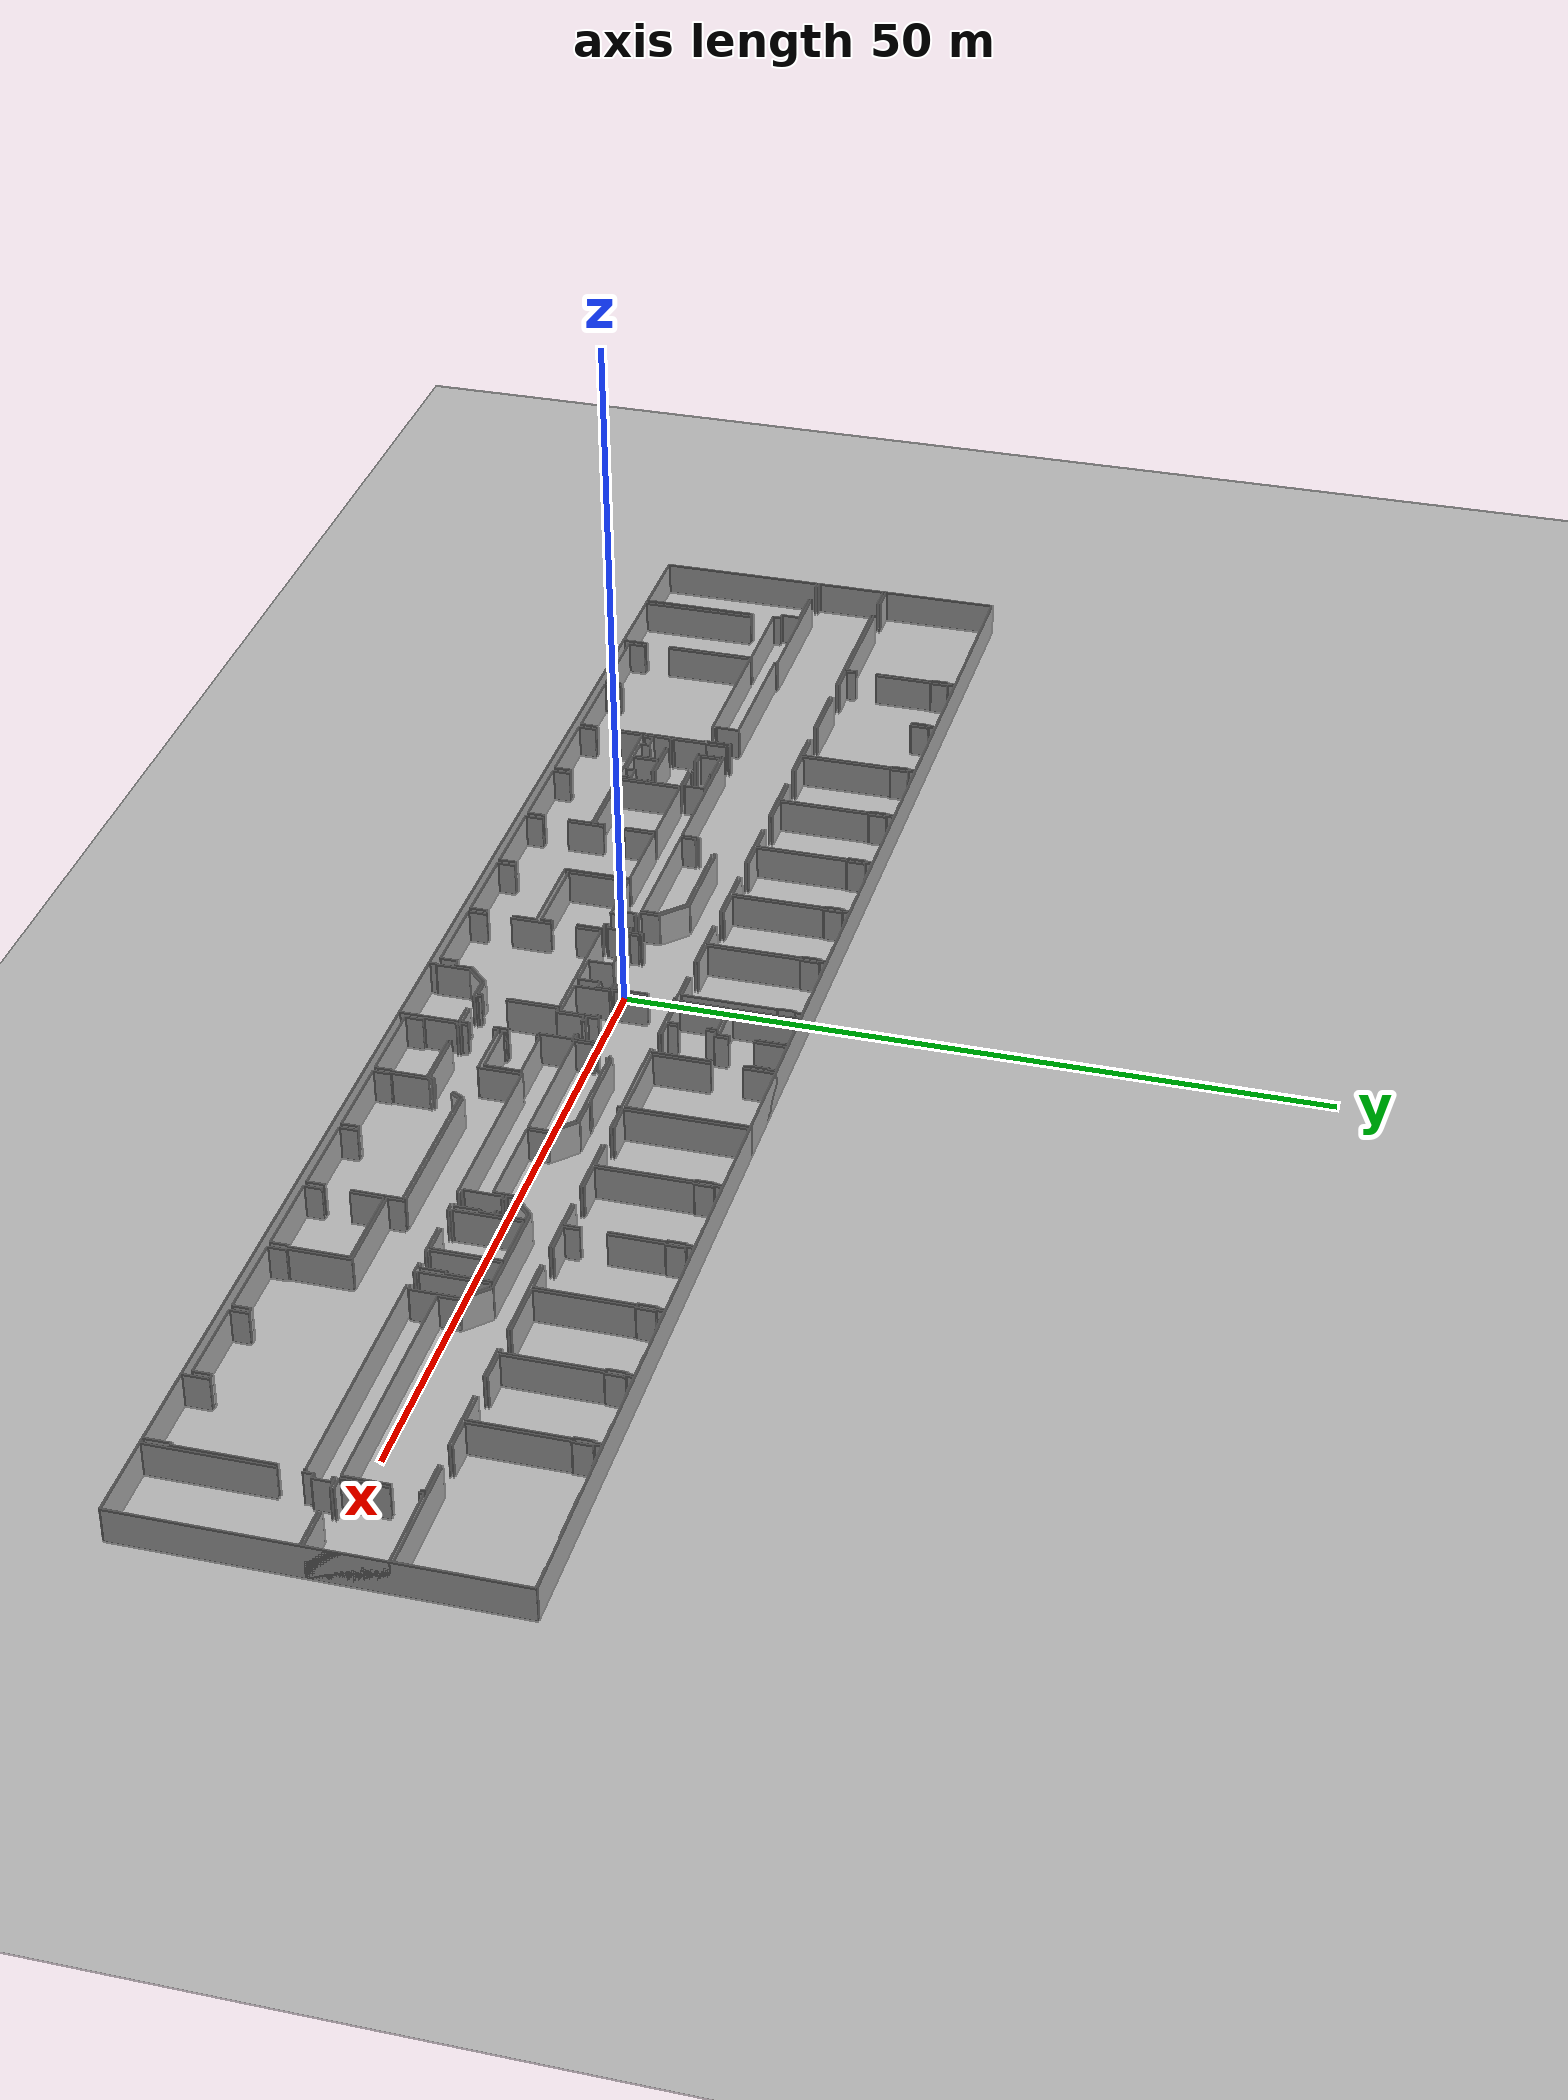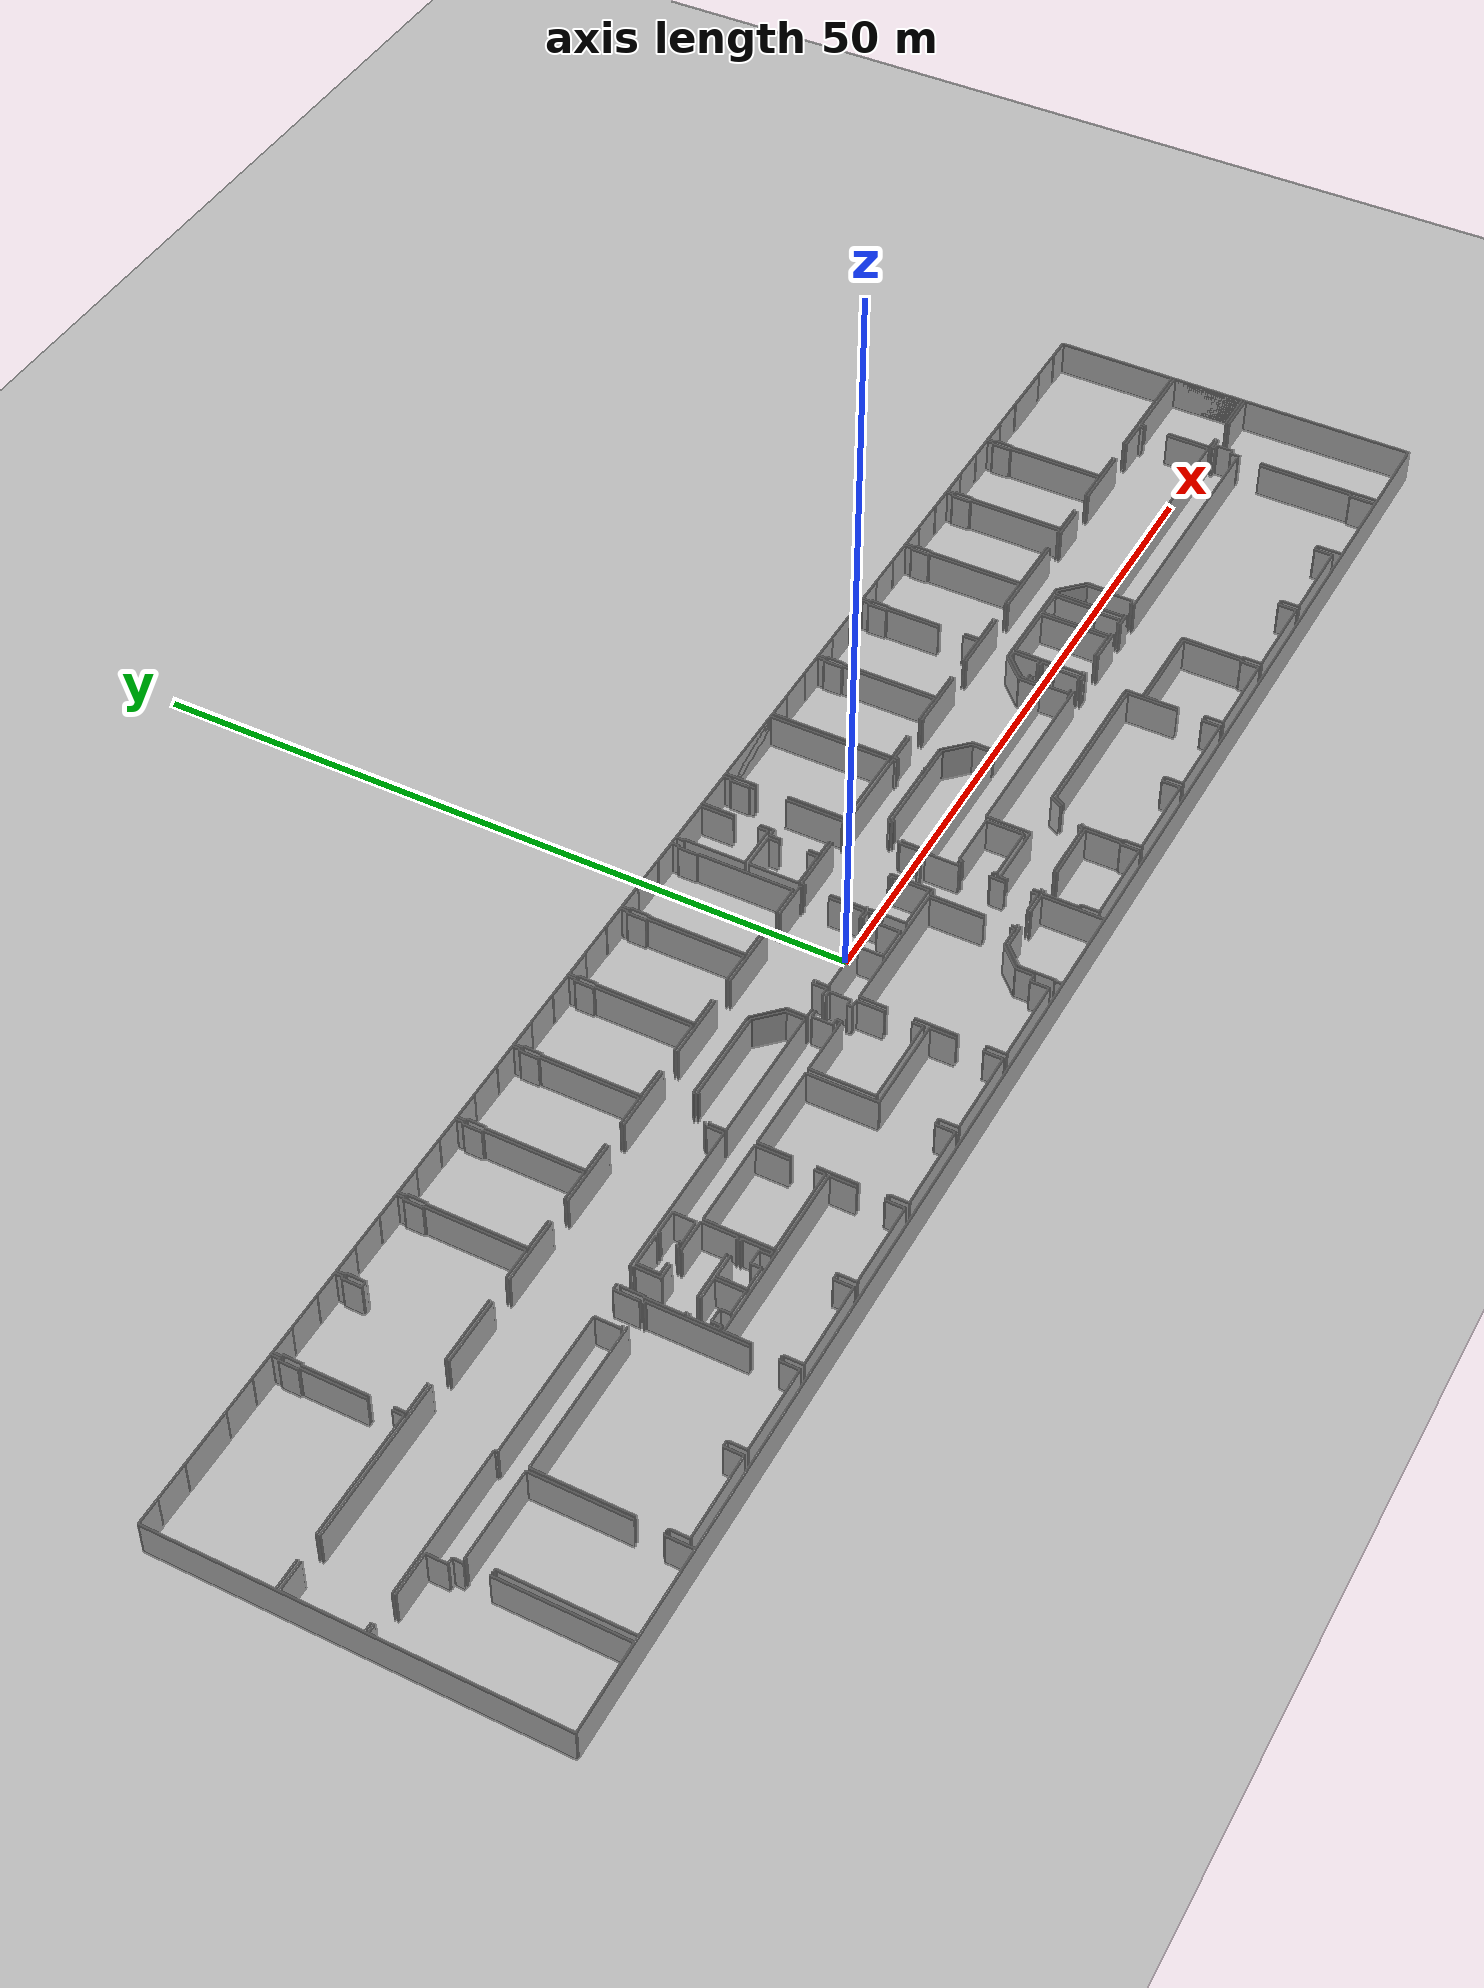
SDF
<sdf version="1.6">
  <world name="default">
    <light name="sun" type="directional">
      <cast_shadows>1</cast_shadows>
      <pose frame="">0 0 10 0 -0 0</pose>
      <diffuse>0.8 0.8 0.8 1</diffuse>
      <specular>0.1 0.1 0.1 1</specular>
      <attenuation>
        <range>1000</range>
        <constant>0.9</constant>
        <linear>0.01</linear>
        <quadratic>0.001</quadratic>
      </attenuation>
      <direction>-0.5 0.5 -1</direction>
    </light>
    <model name="ground_plane">
      <static>1</static>
      <link name="link">
        <collision name="collision">
          <geometry>
            <plane>
              <normal>0 0 1</normal>
              <size>100 100</size>
            </plane>
          </geometry>
          <surface>
            <friction>
              <ode>
                <mu>100</mu>
                <mu2>50</mu2>
              </ode>
              <torsional>
                <ode />
              </torsional>
            </friction>
            <contact>
              <ode />
            </contact>
            <bounce />
          </surface>
          <max_contacts>10</max_contacts>
        </collision>
        <visual name="visual">
          <cast_shadows>0</cast_shadows>
          <geometry>
            <plane>
              <normal>0 0 1</normal>
              <size>100 100</size>
            </plane>
          </geometry>
          <material>
            <script>
              <uri>file://media/materials/scripts/gazebo.material</uri>
              <name>Gazebo/Grey</name>
            </script>
          </material>
        </visual>
        <self_collide>0</self_collide>
        <kinematic>0</kinematic>
        <gravity>1</gravity>
      </link>
    </model>
    <gravity>0 0 -9.8</gravity>
    <magnetic_field>6e-06 2.3e-05 -4.2e-05</magnetic_field>
    <atmosphere type="adiabatic" />
    <physics default="0" name="default_physics" type="ode">
      <max_step_size>0.001</max_step_size>
      <real_time_factor>1</real_time_factor>
      <real_time_update_rate>1000</real_time_update_rate>
    </physics>
    <scene>
      <ambient>0.4 0.4 0.4 1</ambient>
      <background>0.7 0.7 0.7 1</background>
      <shadows>1</shadows>
    </scene>
    <spherical_coordinates>
      <surface_model>EARTH_WGS84</surface_model>
      <latitude_deg>0</latitude_deg>
      <longitude_deg>0</longitude_deg>
      <elevation>0</elevation>
      <heading_deg>0</heading_deg>
    </spherical_coordinates>
  <model name="0510040943_A-40">
		<static>1</static>
		<link name="Wall_0">
			<collision name="Wall_0_Collision">
				<geometry>
					<box>
						<size>2.07870299893 0.1 2.5</size>
					</box>
				</geometry>
				<pose frame="">1.03935149947 0 1.25 0 0 0</pose>
			</collision>
			<visual name="Wall_0_Visual">
				<pose frame="">1.03935149947 0 1.25 0 0 0</pose>
				<geometry>
					<box>
						<size>2.07870299893 0.1 2.5</size>
					</box>
				</geometry>
				<material>
					<script>
						<uri>file://media/materials/scripts/gazebo.material</uri>
						<name>Gazebo/Grey</name>
					</script>
					<ambient>1 1 1 1</ambient>
				</material>
			</visual>
			<pose frame="">0.0133201400518 -8.65606129802 0 0 0 0.0</pose>
		</link>
		<link name="Wall_1">
			<collision name="Wall_1_Collision">
				<geometry>
					<box>
						<size>8.7605926828 0.1 2.5</size>
					</box>
				</geometry>
				<pose frame="">4.3802963414 0 1.25 0 0 0</pose>
			</collision>
			<visual name="Wall_1_Visual">
				<pose frame="">4.3802963414 0 1.25 0 0 0</pose>
				<geometry>
					<box>
						<size>8.7605926828 0.1 2.5</size>
					</box>
				</geometry>
				<material>
					<script>
						<uri>file://media/materials/scripts/gazebo.material</uri>
						<name>Gazebo/Grey</name>
					</script>
					<ambient>1 1 1 1</ambient>
				</material>
			</visual>
			<pose frame="">3.88237682042 -8.65606129802 0 0 0 0.0</pose>
		</link>
		<link name="Wall_2">
			<collision name="Wall_2_Collision">
				<geometry>
					<box>
						<size>0.78487339524 0.1 2.5</size>
					</box>
				</geometry>
				<pose frame="">0.39243669762 0 1.25 0 0 0</pose>
			</collision>
			<visual name="Wall_2_Visual">
				<pose frame="">0.39243669762 0 1.25 0 0 0</pose>
				<geometry>
					<box>
						<size>0.78487339524 0.1 2.5</size>
					</box>
				</geometry>
				<material>
					<script>
						<uri>file://media/materials/scripts/gazebo.material</uri>
						<name>Gazebo/Grey</name>
					</script>
					<ambient>1 1 1 1</ambient>
				</material>
			</visual>
			<pose frame="">12.6429695032 -8.65606129802 0 0 0 1.57079632679</pose>
		</link>
		<link name="Wall_3">
			<collision name="Wall_3_Collision">
				<geometry>
					<box>
						<size>4.40579489521 0.1 2.5</size>
					</box>
				</geometry>
				<pose frame="">2.20289744761 0 1.25 0 0 0</pose>
			</collision>
			<visual name="Wall_3_Visual">
				<pose frame="">2.20289744761 0 1.25 0 0 0</pose>
				<geometry>
					<box>
						<size>4.40579489521 0.1 2.5</size>
					</box>
				</geometry>
				<material>
					<script>
						<uri>file://media/materials/scripts/gazebo.material</uri>
						<name>Gazebo/Grey</name>
					</script>
					<ambient>1 1 1 1</ambient>
				</material>
			</visual>
			<pose frame="">12.6429695032 -6.29446389608 0 0 0 1.57079632679</pose>
		</link>
		<link name="Wall_4">
			<collision name="Wall_4_Collision">
				<geometry>
					<box>
						<size>0.117978383316 0.1 2.5</size>
					</box>
				</geometry>
				<pose frame="">0.0589891916578 0 1.25 0 0 0</pose>
			</collision>
			<visual name="Wall_4_Visual">
				<pose frame="">0.0589891916578 0 1.25 0 0 0</pose>
				<geometry>
					<box>
						<size>0.117978383316 0.1 2.5</size>
					</box>
				</geometry>
				<material>
					<script>
						<uri>file://media/materials/scripts/gazebo.material</uri>
						<name>Gazebo/Grey</name>
					</script>
					<ambient>1 1 1 1</ambient>
				</material>
			</visual>
			<pose frame="">12.6429695032 -1.88866900086 0 0 0 3.14159265359</pose>
		</link>
		<link name="Wall_5">
			<collision name="Wall_5_Collision">
				<geometry>
					<box>
						<size>1.29116557568 0.1 2.5</size>
					</box>
				</geometry>
				<pose frame="">0.645582787842 0 1.25 0 0 0</pose>
			</collision>
			<visual name="Wall_5_Visual">
				<pose frame="">0.645582787842 0 1.25 0 0 0</pose>
				<geometry>
					<box>
						<size>1.29116557568 0.1 2.5</size>
					</box>
				</geometry>
				<material>
					<script>
						<uri>file://media/materials/scripts/gazebo.material</uri>
						<name>Gazebo/Grey</name>
					</script>
					<ambient>1 1 1 1</ambient>
				</material>
			</visual>
			<pose frame="">12.5249911199 -1.88866900086 0 0 0 1.57079632679</pose>
		</link>
		<link name="Wall_6">
			<collision name="Wall_6_Collision">
				<geometry>
					<box>
						<size>0.143223220176 0.1 2.5</size>
					</box>
				</geometry>
				<pose frame="">0.0716116100878 0 1.25 0 0 0</pose>
			</collision>
			<visual name="Wall_6_Visual">
				<pose frame="">0.0716116100878 0 1.25 0 0 0</pose>
				<geometry>
					<box>
						<size>0.143223220176 0.1 2.5</size>
					</box>
				</geometry>
				<material>
					<script>
						<uri>file://media/materials/scripts/gazebo.material</uri>
						<name>Gazebo/Grey</name>
					</script>
					<ambient>1 1 1 1</ambient>
				</material>
			</visual>
			<pose frame="">12.5249911199 -0.597503425179 0 0 0 0.0</pose>
		</link>
		<link name="Wall_7">
			<collision name="Wall_7_Collision">
				<geometry>
					<box>
						<size>0.57948952149 0.1 2.5</size>
					</box>
				</geometry>
				<pose frame="">0.289744760745 0 1.25 0 0 0</pose>
			</collision>
			<visual name="Wall_7_Visual">
				<pose frame="">0.289744760745 0 1.25 0 0 0</pose>
				<geometry>
					<box>
						<size>0.57948952149 0.1 2.5</size>
					</box>
				</geometry>
				<material>
					<script>
						<uri>file://media/materials/scripts/gazebo.material</uri>
						<name>Gazebo/Grey</name>
					</script>
					<ambient>1 1 1 1</ambient>
				</material>
			</visual>
			<pose frame="">12.6682143401 -0.597503425179 0 0 0 1.57079632679</pose>
		</link>
		<link name="Wall_8">
			<collision name="Wall_8_Collision">
				<geometry>
					<box>
						<size>1.88892271782 0.1 2.5</size>
					</box>
				</geometry>
				<pose frame="">0.944461358908 0 1.25 0 0 0</pose>
			</collision>
			<visual name="Wall_8_Visual">
				<pose frame="">0.944461358908 0 1.25 0 0 0</pose>
				<geometry>
					<box>
						<size>1.88892271782 0.1 2.5</size>
					</box>
				</geometry>
				<material>
					<script>
						<uri>file://media/materials/scripts/gazebo.material</uri>
						<name>Gazebo/Grey</name>
					</script>
					<ambient>1 1 1 1</ambient>
				</material>
			</visual>
			<pose frame="">12.6682143401 -0.018013903689 0 0 0 3.14159265359</pose>
		</link>
		<link name="Wall_9">
			<collision name="Wall_9_Collision">
				<geometry>
					<box>
						<size>3.92994874918 0.1 2.5</size>
					</box>
				</geometry>
				<pose frame="">1.96497437459 0 1.25 0 0 0</pose>
			</collision>
			<visual name="Wall_9_Visual">
				<pose frame="">1.96497437459 0 1.25 0 0 0</pose>
				<geometry>
					<box>
						<size>3.92994874918 0.1 2.5</size>
					</box>
				</geometry>
				<material>
					<script>
						<uri>file://media/materials/scripts/gazebo.material</uri>
						<name>Gazebo/Grey</name>
					</script>
					<ambient>1 1 1 1</ambient>
				</material>
			</visual>
			<pose frame="">8.21256406353 -0.018013903689 0 0 0 3.14159265359</pose>
		</link>
		<link name="Wall_10">
			<collision name="Wall_10_Collision">
				<geometry>
					<box>
						<size>1.74544578069 0.1 2.5</size>
					</box>
				</geometry>
				<pose frame="">0.872722890344 0 1.25 0 0 0</pose>
			</collision>
			<visual name="Wall_10_Visual">
				<pose frame="">0.872722890344 0 1.25 0 0 0</pose>
				<geometry>
					<box>
						<size>1.74544578069 0.1 2.5</size>
					</box>
				</geometry>
				<material>
					<script>
						<uri>file://media/materials/scripts/gazebo.material</uri>
						<name>Gazebo/Grey</name>
					</script>
					<ambient>1 1 1 1</ambient>
				</material>
			</visual>
			<pose frame="">1.74544578069 -0.018013903689 0 0 0 3.14159265359</pose>
		</link>
		<link name="Wall_11">
			<collision name="Wall_11_Collision">
				<geometry>
					<box>
						<size>8.63805766436 0.1 2.5</size>
					</box>
				</geometry>
				<pose frame="">4.31902883218 0 1.25 0 0 0</pose>
			</collision>
			<visual name="Wall_11_Visual">
				<pose frame="">4.31902883218 0 1.25 0 0 0</pose>
				<geometry>
					<box>
						<size>8.63805766436 0.1 2.5</size>
					</box>
				</geometry>
				<material>
					<script>
						<uri>file://media/materials/scripts/gazebo.material</uri>
						<name>Gazebo/Grey</name>
					</script>
					<ambient>1 1 1 1</ambient>
				</material>
			</visual>
			<pose frame="">0.0 -0.018013903689 0 0 0 -1.56925429665</pose>
		</link>
		<link name="Wall_12">
			<collision name="Wall_12_Collision">
				<geometry>
					<box>
						<size>5.24661287867 0.1 2.5</size>
					</box>
				</geometry>
				<pose frame="">2.62330643934 0 1.25 0 0 0</pose>
			</collision>
			<visual name="Wall_12_Visual">
				<pose frame="">2.62330643934 0 1.25 0 0 0</pose>
				<geometry>
					<box>
						<size>5.24661287867 0.1 2.5</size>
					</box>
				</geometry>
				<material>
					<script>
						<uri>file://media/materials/scripts/gazebo.material</uri>
						<name>Gazebo/Grey</name>
					</script>
					<ambient>1 1 1 1</ambient>
				</material>
			</visual>
			<pose frame="">0.0147155832953 -14.1396458111 0 0 0 1.57079632679</pose>
		</link>
		<link name="Wall_13">
			<collision name="Wall_13_Collision">
				<geometry>
					<box>
						<size>2.08276247019 0.1 2.5</size>
					</box>
				</geometry>
				<pose frame="">1.04138123509 0 1.25 0 0 0</pose>
			</collision>
			<visual name="Wall_13_Visual">
				<pose frame="">1.04138123509 0 1.25 0 0 0</pose>
				<geometry>
					<box>
						<size>2.08276247019 0.1 2.5</size>
					</box>
				</geometry>
				<material>
					<script>
						<uri>file://media/materials/scripts/gazebo.material</uri>
						<name>Gazebo/Grey</name>
					</script>
					<ambient>1 1 1 1</ambient>
				</material>
			</visual>
			<pose frame="">0.0147155832953 -8.89303293246 0 0 0 0.0</pose>
		</link>
		<link name="Wall_14">
			<collision name="Wall_14_Collision">
				<geometry>
					<box>
						<size>11.2046480946 0.1 2.5</size>
					</box>
				</geometry>
				<pose frame="">5.60232404729 0 1.25 0 0 0</pose>
			</collision>
			<visual name="Wall_14_Visual">
				<pose frame="">5.60232404729 0 1.25 0 0 0</pose>
				<geometry>
					<box>
						<size>11.2046480946 0.1 2.5</size>
					</box>
				</geometry>
				<material>
					<script>
						<uri>file://media/materials/scripts/gazebo.material</uri>
						<name>Gazebo/Grey</name>
					</script>
					<ambient>1 1 1 1</ambient>
				</material>
			</visual>
			<pose frame="">3.87996650936 -8.89303293246 0 0 0 0.0</pose>
		</link>
		<link name="Wall_15">
			<collision name="Wall_15_Collision">
				<geometry>
					<box>
						<size>4.71139696555 0.1 2.5</size>
					</box>
				</geometry>
				<pose frame="">2.35569848277 0 1.25 0 0 0</pose>
			</collision>
			<visual name="Wall_15_Visual">
				<pose frame="">2.35569848277 0 1.25 0 0 0</pose>
				<geometry>
					<box>
						<size>4.71139696555 0.1 2.5</size>
					</box>
				</geometry>
				<material>
					<script>
						<uri>file://media/materials/scripts/gazebo.material</uri>
						<name>Gazebo/Grey</name>
					</script>
					<ambient>1 1 1 1</ambient>
				</material>
			</visual>
			<pose frame="">16.8624092962 -8.89303293246 0 0 0 0.0</pose>
		</link>
		<link name="Wall_16">
			<collision name="Wall_16_Collision">
				<geometry>
					<box>
						<size>4.71456842746 0.1 2.5</size>
					</box>
				</geometry>
				<pose frame="">2.35728421373 0 1.25 0 0 0</pose>
			</collision>
			<visual name="Wall_16_Visual">
				<pose frame="">2.35728421373 0 1.25 0 0 0</pose>
				<geometry>
					<box>
						<size>4.71456842746 0.1 2.5</size>
					</box>
				</geometry>
				<material>
					<script>
						<uri>file://media/materials/scripts/gazebo.material</uri>
						<name>Gazebo/Grey</name>
					</script>
					<ambient>1 1 1 1</ambient>
				</material>
			</visual>
			<pose frame="">23.3612421982 -8.89303293246 0 0 0 0.0</pose>
		</link>
		<link name="Wall_17">
			<collision name="Wall_17_Collision">
				<geometry>
					<box>
						<size>4.71456842746 0.1 2.5</size>
					</box>
				</geometry>
				<pose frame="">2.35728421373 0 1.25 0 0 0</pose>
			</collision>
			<visual name="Wall_17_Visual">
				<pose frame="">2.35728421373 0 1.25 0 0 0</pose>
				<geometry>
					<box>
						<size>4.71456842746 0.1 2.5</size>
					</box>
				</geometry>
				<material>
					<script>
						<uri>file://media/materials/scripts/gazebo.material</uri>
						<name>Gazebo/Grey</name>
					</script>
					<ambient>1 1 1 1</ambient>
				</material>
			</visual>
			<pose frame="">29.852844167 -8.89303293246 0 0 0 0.0</pose>
		</link>
		<link name="Wall_18">
			<collision name="Wall_18_Collision">
				<geometry>
					<box>
						<size>4.72179936063 0.1 2.5</size>
					</box>
				</geometry>
				<pose frame="">2.36089968032 0 1.25 0 0 0</pose>
			</collision>
			<visual name="Wall_18_Visual">
				<pose frame="">2.36089968032 0 1.25 0 0 0</pose>
				<geometry>
					<box>
						<size>4.72179936063 0.1 2.5</size>
					</box>
				</geometry>
				<material>
					<script>
						<uri>file://media/materials/scripts/gazebo.material</uri>
						<name>Gazebo/Grey</name>
					</script>
					<ambient>1 1 1 1</ambient>
				</material>
			</visual>
			<pose frame="">36.3516770691 -8.89303293246 0 0 0 0.0</pose>
		</link>
		<link name="Wall_19">
			<collision name="Wall_19_Collision">
				<geometry>
					<box>
						<size>4.69921855178 0.1 2.5</size>
					</box>
				</geometry>
				<pose frame="">2.34960927589 0 1.25 0 0 0</pose>
			</collision>
			<visual name="Wall_19_Visual">
				<pose frame="">2.34960927589 0 1.25 0 0 0</pose>
				<geometry>
					<box>
						<size>4.69921855178 0.1 2.5</size>
					</box>
				</geometry>
				<material>
					<script>
						<uri>file://media/materials/scripts/gazebo.material</uri>
						<name>Gazebo/Grey</name>
					</script>
					<ambient>1 1 1 1</ambient>
				</material>
			</visual>
			<pose frame="">42.8505099711 -8.89303293246 0 0 0 0.0</pose>
		</link>
		<link name="Wall_20">
			<collision name="Wall_20_Collision">
				<geometry>
					<box>
						<size>4.69059217537 0.1 2.5</size>
					</box>
				</geometry>
				<pose frame="">2.34529608768 0 1.25 0 0 0</pose>
			</collision>
			<visual name="Wall_20_Visual">
				<pose frame="">2.34529608768 0 1.25 0 0 0</pose>
				<geometry>
					<box>
						<size>4.69059217537 0.1 2.5</size>
					</box>
				</geometry>
				<material>
					<script>
						<uri>file://media/materials/scripts/gazebo.material</uri>
						<name>Gazebo/Grey</name>
					</script>
					<ambient>1 1 1 1</ambient>
				</material>
			</visual>
			<pose frame="">49.3622824377 -8.89303293246 0 0 0 0.0</pose>
		</link>
		<link name="Wall_21">
			<collision name="Wall_21_Collision">
				<geometry>
					<box>
						<size>2.69548891257 0.1 2.5</size>
					</box>
				</geometry>
				<pose frame="">1.34774445628 0 1.25 0 0 0</pose>
			</collision>
			<visual name="Wall_21_Visual">
				<pose frame="">1.34774445628 0 1.25 0 0 0</pose>
				<geometry>
					<box>
						<size>2.69548891257 0.1 2.5</size>
					</box>
				</geometry>
				<material>
					<script>
						<uri>file://media/materials/scripts/gazebo.material</uri>
						<name>Gazebo/Grey</name>
					</script>
					<ambient>1 1 1 1</ambient>
				</material>
			</visual>
			<pose frame="">55.8178565992 -8.89303293246 0 0 0 0.0</pose>
		</link>
		<link name="Wall_22">
			<collision name="Wall_22_Collision">
				<geometry>
					<box>
						<size>0.188511696352 0.1 2.5</size>
					</box>
				</geometry>
				<pose frame="">0.0942558481758 0 1.25 0 0 0</pose>
			</collision>
			<visual name="Wall_22_Visual">
				<pose frame="">0.0942558481758 0 1.25 0 0 0</pose>
				<geometry>
					<box>
						<size>0.188511696352 0.1 2.5</size>
					</box>
				</geometry>
				<material>
					<script>
						<uri>file://media/materials/scripts/gazebo.material</uri>
						<name>Gazebo/Grey</name>
					</script>
					<ambient>1 1 1 1</ambient>
				</material>
			</visual>
			<pose frame="">58.5133455117 -8.89303293246 0 0 0 -1.57079632679</pose>
		</link>
		<link name="Wall_23">
			<collision name="Wall_23_Collision">
				<geometry>
					<box>
						<size>2.47729233267 0.1 2.5</size>
					</box>
				</geometry>
				<pose frame="">1.23864616634 0 1.25 0 0 0</pose>
			</collision>
			<visual name="Wall_23_Visual">
				<pose frame="">1.23864616634 0 1.25 0 0 0</pose>
				<geometry>
					<box>
						<size>2.47729233267 0.1 2.5</size>
					</box>
				</geometry>
				<material>
					<script>
						<uri>file://media/materials/scripts/gazebo.material</uri>
						<name>Gazebo/Grey</name>
					</script>
					<ambient>1 1 1 1</ambient>
				</material>
			</visual>
			<pose frame="">58.5133455117 -10.8866138935 0 0 0 -1.57079632679</pose>
		</link>
		<link name="Wall_24">
			<collision name="Wall_24_Collision">
				<geometry>
					<box>
						<size>0.604226924443 0.1 2.5</size>
					</box>
				</geometry>
				<pose frame="">0.302113462222 0 1.25 0 0 0</pose>
			</collision>
			<visual name="Wall_24_Visual">
				<pose frame="">0.302113462222 0 1.25 0 0 0</pose>
				<geometry>
					<box>
						<size>0.604226924443 0.1 2.5</size>
					</box>
				</geometry>
				<material>
					<script>
						<uri>file://media/materials/scripts/gazebo.material</uri>
						<name>Gazebo/Grey</name>
					</script>
					<ambient>1 1 1 1</ambient>
				</material>
			</visual>
			<pose frame="">58.5133455117 -13.3639062262 0 0 0 3.14159265359</pose>
		</link>
		<link name="Wall_25">
			<collision name="Wall_25_Collision">
				<geometry>
					<box>
						<size>0.345562490486 0.1 2.5</size>
					</box>
				</geometry>
				<pose frame="">0.172781245243 0 1.25 0 0 0</pose>
			</collision>
			<visual name="Wall_25_Visual">
				<pose frame="">0.172781245243 0 1.25 0 0 0</pose>
				<geometry>
					<box>
						<size>0.345562490486 0.1 2.5</size>
					</box>
				</geometry>
				<material>
					<script>
						<uri>file://media/materials/scripts/gazebo.material</uri>
						<name>Gazebo/Grey</name>
					</script>
					<ambient>1 1 1 1</ambient>
				</material>
			</visual>
			<pose frame="">51.9345917694 -13.3639062262 0 0 0 3.14159265359</pose>
		</link>
		<link name="Wall_26">
			<collision name="Wall_26_Collision">
				<geometry>
					<box>
						<size>0.968564469478 0.1 2.5</size>
					</box>
				</geometry>
				<pose frame="">0.484282234739 0 1.25 0 0 0</pose>
			</collision>
			<visual name="Wall_26_Visual">
				<pose frame="">0.484282234739 0 1.25 0 0 0</pose>
				<geometry>
					<box>
						<size>0.968564469478 0.1 2.5</size>
					</box>
				</geometry>
				<material>
					<script>
						<uri>file://media/materials/scripts/gazebo.material</uri>
						<name>Gazebo/Grey</name>
					</script>
					<ambient>1 1 1 1</ambient>
				</material>
			</visual>
			<pose frame="">51.5890292789 -13.3639062262 0 0 0 -1.57079632679</pose>
		</link>
		<link name="Wall_27">
			<collision name="Wall_27_Collision">
				<geometry>
					<box>
						<size>0.570355711169 0.1 2.5</size>
					</box>
				</geometry>
				<pose frame="">0.285177855584 0 1.25 0 0 0</pose>
			</collision>
			<visual name="Wall_27_Visual">
				<pose frame="">0.285177855584 0 1.25 0 0 0</pose>
				<geometry>
					<box>
						<size>0.570355711169 0.1 2.5</size>
					</box>
				</geometry>
				<material>
					<script>
						<uri>file://media/materials/scripts/gazebo.material</uri>
						<name>Gazebo/Grey</name>
					</script>
					<ambient>1 1 1 1</ambient>
				</material>
			</visual>
			<pose frame="">51.5890292789 -14.3324706957 0 0 0 3.14159265359</pose>
		</link>
		<link name="Wall_28">
			<collision name="Wall_28_Collision">
				<geometry>
					<box>
						<size>0.60549550921 0.1 2.5</size>
					</box>
				</geometry>
				<pose frame="">0.302747754605 0 1.25 0 0 0</pose>
			</collision>
			<visual name="Wall_28_Visual">
				<pose frame="">0.302747754605 0 1.25 0 0 0</pose>
				<geometry>
					<box>
						<size>0.60549550921 0.1 2.5</size>
					</box>
				</geometry>
				<material>
					<script>
						<uri>file://media/materials/scripts/gazebo.material</uri>
						<name>Gazebo/Grey</name>
					</script>
					<ambient>1 1 1 1</ambient>
				</material>
			</visual>
			<pose frame="">49.6404830771 -14.3324706957 0 0 0 3.14159265359</pose>
		</link>
		<link name="Wall_29">
			<collision name="Wall_29_Collision">
				<geometry>
					<box>
						<size>1.38275739585 0.1 2.5</size>
					</box>
				</geometry>
				<pose frame="">0.691378697925 0 1.25 0 0 0</pose>
			</collision>
			<visual name="Wall_29_Visual">
				<pose frame="">0.691378697925 0 1.25 0 0 0</pose>
				<geometry>
					<box>
						<size>1.38275739585 0.1 2.5</size>
					</box>
				</geometry>
				<material>
					<script>
						<uri>file://media/materials/scripts/gazebo.material</uri>
						<name>Gazebo/Grey</name>
					</script>
					<ambient>1 1 1 1</ambient>
				</material>
			</visual>
			<pose frame="">49.0349875679 -14.3324706957 0 0 0 1.57079632679</pose>
		</link>
		<link name="Wall_30">
			<collision name="Wall_30_Collision">
				<geometry>
					<box>
						<size>2.41902203418 0.1 2.5</size>
					</box>
				</geometry>
				<pose frame="">1.20951101709 0 1.25 0 0 0</pose>
			</collision>
			<visual name="Wall_30_Visual">
				<pose frame="">1.20951101709 0 1.25 0 0 0</pose>
				<geometry>
					<box>
						<size>2.41902203418 0.1 2.5</size>
					</box>
				</geometry>
				<material>
					<script>
						<uri>file://media/materials/scripts/gazebo.material</uri>
						<name>Gazebo/Grey</name>
					</script>
					<ambient>1 1 1 1</ambient>
				</material>
			</visual>
			<pose frame="">49.0349875679 -12.9497132998 0 0 0 2.35971729981</pose>
		</link>
		<link name="Wall_31">
			<collision name="Wall_31_Collision">
				<geometry>
					<box>
						<size>6.8106510377 0.1 2.5</size>
					</box>
				</geometry>
				<pose frame="">3.40532551885 0 1.25 0 0 0</pose>
			</collision>
			<visual name="Wall_31_Visual">
				<pose frame="">3.40532551885 0 1.25 0 0 0</pose>
				<geometry>
					<box>
						<size>6.8106510377 0.1 2.5</size>
					</box>
				</geometry>
				<material>
					<script>
						<uri>file://media/materials/scripts/gazebo.material</uri>
						<name>Gazebo/Grey</name>
					</script>
					<ambient>1 1 1 1</ambient>
				</material>
			</visual>
			<pose frame="">47.3184655199 -11.2452428071 0 0 0 3.14159265359</pose>
		</link>
		<link name="Wall_32">
			<collision name="Wall_32_Collision">
				<geometry>
					<box>
						<size>0.22569146261 0.1 2.5</size>
					</box>
				</geometry>
				<pose frame="">0.112845731305 0 1.25 0 0 0</pose>
			</collision>
			<visual name="Wall_32_Visual">
				<pose frame="">0.112845731305 0 1.25 0 0 0</pose>
				<geometry>
					<box>
						<size>0.22569146261 0.1 2.5</size>
					</box>
				</geometry>
				<material>
					<script>
						<uri>file://media/materials/scripts/gazebo.material</uri>
						<name>Gazebo/Grey</name>
					</script>
					<ambient>1 1 1 1</ambient>
				</material>
			</visual>
			<pose frame="">40.5078144822 -11.2452428071 0 0 0 -2.35619449019</pose>
		</link>
		<link name="Wall_33">
			<collision name="Wall_33_Collision">
				<geometry>
					<box>
						<size>0.31713751447 0.1 2.5</size>
					</box>
				</geometry>
				<pose frame="">0.158568757235 0 1.25 0 0 0</pose>
			</collision>
			<visual name="Wall_33_Visual">
				<pose frame="">0.158568757235 0 1.25 0 0 0</pose>
				<geometry>
					<box>
						<size>0.31713751447 0.1 2.5</size>
					</box>
				</geometry>
				<material>
					<script>
						<uri>file://media/materials/scripts/gazebo.material</uri>
						<name>Gazebo/Grey</name>
					</script>
					<ambient>1 1 1 1</ambient>
				</material>
			</visual>
			<pose frame="">38.7857106612 -12.9251027554 0 0 0 -2.30072736439</pose>
		</link>
		<link name="Wall_34">
			<collision name="Wall_34_Collision">
				<geometry>
					<box>
						<size>1.17838838991 0.1 2.5</size>
					</box>
				</geometry>
				<pose frame="">0.589194194956 0 1.25 0 0 0</pose>
			</collision>
			<visual name="Wall_34_Visual">
				<pose frame="">0.589194194956 0 1.25 0 0 0</pose>
				<geometry>
					<box>
						<size>1.17838838991 0.1 2.5</size>
					</box>
				</geometry>
				<material>
					<script>
						<uri>file://media/materials/scripts/gazebo.material</uri>
						<name>Gazebo/Grey</name>
					</script>
					<ambient>1 1 1 1</ambient>
				</material>
			</visual>
			<pose frame="">38.5742375806 -13.1614400974 0 0 0 -1.57079632679</pose>
		</link>
		<link name="Wall_35">
			<collision name="Wall_35_Collision">
				<geometry>
					<box>
						<size>11.1474349216 0.1 2.5</size>
					</box>
				</geometry>
				<pose frame="">5.5737174608 0 1.25 0 0 0</pose>
			</collision>
			<visual name="Wall_35_Visual">
				<pose frame="">5.5737174608 0 1.25 0 0 0</pose>
				<geometry>
					<box>
						<size>11.1474349216 0.1 2.5</size>
					</box>
				</geometry>
				<material>
					<script>
						<uri>file://media/materials/scripts/gazebo.material</uri>
						<name>Gazebo/Grey</name>
					</script>
					<ambient>1 1 1 1</ambient>
				</material>
			</visual>
			<pose frame="">38.5742375806 -14.3398284873 0 0 0 3.14159265359</pose>
		</link>
		<link name="Wall_36">
			<collision name="Wall_36_Collision">
				<geometry>
					<box>
						<size>0.493606332775 0.1 2.5</size>
					</box>
				</geometry>
				<pose frame="">0.246803166388 0 1.25 0 0 0</pose>
			</collision>
			<visual name="Wall_36_Visual">
				<pose frame="">0.246803166388 0 1.25 0 0 0</pose>
				<geometry>
					<box>
						<size>0.493606332775 0.1 2.5</size>
					</box>
				</geometry>
				<material>
					<script>
						<uri>file://media/materials/scripts/gazebo.material</uri>
						<name>Gazebo/Grey</name>
					</script>
					<ambient>1 1 1 1</ambient>
				</material>
			</visual>
			<pose frame="">26.0096666159 -14.3398284873 0 0 0 3.14159265359</pose>
		</link>
		<link name="Wall_37">
			<collision name="Wall_37_Collision">
				<geometry>
					<box>
						<size>1.75153498757 0.1 2.5</size>
					</box>
				</geometry>
				<pose frame="">0.875767493784 0 1.25 0 0 0</pose>
			</collision>
			<visual name="Wall_37_Visual">
				<pose frame="">0.875767493784 0 1.25 0 0 0</pose>
				<geometry>
					<box>
						<size>1.75153498757 0.1 2.5</size>
					</box>
				</geometry>
				<material>
					<script>
						<uri>file://media/materials/scripts/gazebo.material</uri>
						<name>Gazebo/Grey</name>
					</script>
					<ambient>1 1 1 1</ambient>
				</material>
			</visual>
			<pose frame="">25.5160602831 -14.3398284873 0 0 0 -1.57079632679</pose>
		</link>
		<link name="Wall_38">
			<collision name="Wall_38_Collision">
				<geometry>
					<box>
						<size>0.0550565788806 0.1 2.5</size>
					</box>
				</geometry>
				<pose frame="">0.0275282894403 0 1.25 0 0 0</pose>
			</collision>
			<visual name="Wall_38_Visual">
				<pose frame="">0.0275282894403 0 1.25 0 0 0</pose>
				<geometry>
					<box>
						<size>0.0550565788806 0.1 2.5</size>
					</box>
				</geometry>
				<material>
					<script>
						<uri>file://media/materials/scripts/gazebo.material</uri>
						<name>Gazebo/Grey</name>
					</script>
					<ambient>1 1 1 1</ambient>
				</material>
			</visual>
			<pose frame="">25.5160602831 -16.0913634749 0 0 0 3.14159265359</pose>
		</link>
		<link name="Wall_39">
			<collision name="Wall_39_Collision">
				<geometry>
					<box>
						<size>0.224793220683 0.1 2.5</size>
					</box>
				</geometry>
				<pose frame="">0.112396610342 0 1.25 0 0 0</pose>
			</collision>
			<visual name="Wall_39_Visual">
				<pose frame="">0.112396610342 0 1.25 0 0 0</pose>
				<geometry>
					<box>
						<size>0.224793220683 0.1 2.5</size>
					</box>
				</geometry>
				<material>
					<script>
						<uri>file://media/materials/scripts/gazebo.material</uri>
						<name>Gazebo/Grey</name>
					</script>
					<ambient>1 1 1 1</ambient>
				</material>
			</visual>
			<pose frame="">23.5860354189 -16.0913634749 0 0 0 3.14159265359</pose>
		</link>
		<link name="Wall_40">
			<collision name="Wall_40_Collision">
				<geometry>
					<box>
						<size>1.73453595169 0.1 2.5</size>
					</box>
				</geometry>
				<pose frame="">0.867267975846 0 1.25 0 0 0</pose>
			</collision>
			<visual name="Wall_40_Visual">
				<pose frame="">0.867267975846 0 1.25 0 0 0</pose>
				<geometry>
					<box>
						<size>1.73453595169 0.1 2.5</size>
					</box>
				</geometry>
				<material>
					<script>
						<uri>file://media/materials/scripts/gazebo.material</uri>
						<name>Gazebo/Grey</name>
					</script>
					<ambient>1 1 1 1</ambient>
				</material>
			</visual>
			<pose frame="">23.3612421982 -16.0913634749 0 0 0 1.57079632679</pose>
		</link>
		<link name="Wall_41">
			<collision name="Wall_41_Collision">
				<geometry>
					<box>
						<size>10.3937687116 0.1 2.5</size>
					</box>
				</geometry>
				<pose frame="">5.19688435581 0 1.25 0 0 0</pose>
			</collision>
			<visual name="Wall_41_Visual">
				<pose frame="">5.19688435581 0 1.25 0 0 0</pose>
				<geometry>
					<box>
						<size>10.3937687116 0.1 2.5</size>
					</box>
				</geometry>
				<material>
					<script>
						<uri>file://media/materials/scripts/gazebo.material</uri>
						<name>Gazebo/Grey</name>
					</script>
					<ambient>1 1 1 1</ambient>
				</material>
			</visual>
			<pose frame="">23.3612421982 -14.3568275232 0 0 0 3.14159265359</pose>
		</link>
		<link name="Wall_42">
			<collision name="Wall_42_Collision">
				<geometry>
					<box>
						<size>0.20310042117 0.1 2.5</size>
					</box>
				</geometry>
				<pose frame="">0.101550210585 0 1.25 0 0 0</pose>
			</collision>
			<visual name="Wall_42_Visual">
				<pose frame="">0.101550210585 0 1.25 0 0 0</pose>
				<geometry>
					<box>
						<size>0.20310042117 0.1 2.5</size>
					</box>
				</geometry>
				<material>
					<script>
						<uri>file://media/materials/scripts/gazebo.material</uri>
						<name>Gazebo/Grey</name>
					</script>
					<ambient>1 1 1 1</ambient>
				</material>
			</visual>
			<pose frame="">12.9674734866 -14.3568275232 0 0 0 1.57079632679</pose>
		</link>
		<link name="Wall_43">
			<collision name="Wall_43_Collision">
				<geometry>
					<box>
						<size>10.3198102197 0.1 2.5</size>
					</box>
				</geometry>
				<pose frame="">5.15990510986 0 1.25 0 0 0</pose>
			</collision>
			<visual name="Wall_43_Visual">
				<pose frame="">5.15990510986 0 1.25 0 0 0</pose>
				<geometry>
					<box>
						<size>10.3198102197 0.1 2.5</size>
					</box>
				</geometry>
				<material>
					<script>
						<uri>file://media/materials/scripts/gazebo.material</uri>
						<name>Gazebo/Grey</name>
					</script>
					<ambient>1 1 1 1</ambient>
				</material>
			</visual>
			<pose frame="">12.9674734866 -14.153727102 0 0 0 3.14159265359</pose>
		</link>
		<link name="Wall_44">
			<collision name="Wall_44_Collision">
				<geometry>
					<box>
						<size>0.618722188753 0.1 2.5</size>
					</box>
				</geometry>
				<pose frame="">0.309361094376 0 1.25 0 0 0</pose>
			</collision>
			<visual name="Wall_44_Visual">
				<pose frame="">0.309361094376 0 1.25 0 0 0</pose>
				<geometry>
					<box>
						<size>0.618722188753 0.1 2.5</size>
					</box>
				</geometry>
				<material>
					<script>
						<uri>file://media/materials/scripts/gazebo.material</uri>
						<name>Gazebo/Grey</name>
					</script>
					<ambient>1 1 1 1</ambient>
				</material>
			</visual>
			<pose frame="">0.633277515604 -14.153727102 0 0 0 3.11883202364</pose>
		</link>
		<link name="Wall_45">
			<collision name="Wall_45_Collision">
				<geometry>
					<box>
						<size>12.3845587862 0.1 2.5</size>
					</box>
				</geometry>
				<pose frame="">6.19227939311 0 1.25 0 0 0</pose>
			</collision>
			<visual name="Wall_45_Visual">
				<pose frame="">6.19227939311 0 1.25 0 0 0</pose>
				<geometry>
					<box>
						<size>12.3845587862 0.1 2.5</size>
					</box>
				</geometry>
				<material>
					<script>
						<uri>file://media/materials/scripts/gazebo.material</uri>
						<name>Gazebo/Grey</name>
					</script>
					<ambient>1 1 1 1</ambient>
				</material>
			</visual>
			<pose frame="">0.00976810270462 -26.7413863094 0 0 0 1.57079632679</pose>
		</link>
		<link name="Wall_46">
			<collision name="Wall_46_Collision">
				<geometry>
					<box>
						<size>0.63454610037 0.1 2.5</size>
					</box>
				</geometry>
				<pose frame="">0.317273050185 0 1.25 0 0 0</pose>
			</collision>
			<visual name="Wall_46_Visual">
				<pose frame="">0.317273050185 0 1.25 0 0 0</pose>
				<geometry>
					<box>
						<size>0.63454610037 0.1 2.5</size>
					</box>
				</geometry>
				<material>
					<script>
						<uri>file://media/materials/scripts/gazebo.material</uri>
						<name>Gazebo/Grey</name>
					</script>
					<ambient>1 1 1 1</ambient>
				</material>
			</visual>
			<pose frame="">0.00976810270462 -14.3568275232 0 0 0 0.0</pose>
		</link>
		<link name="Wall_47">
			<collision name="Wall_47_Collision">
				<geometry>
					<box>
						<size>2.96404830771 0.1 2.5</size>
					</box>
				</geometry>
				<pose frame="">1.48202415385 0 1.25 0 0 0</pose>
			</collision>
			<visual name="Wall_47_Visual">
				<pose frame="">1.48202415385 0 1.25 0 0 0</pose>
				<geometry>
					<box>
						<size>2.96404830771 0.1 2.5</size>
					</box>
				</geometry>
				<material>
					<script>
						<uri>file://media/materials/scripts/gazebo.material</uri>
						<name>Gazebo/Grey</name>
					</script>
					<ambient>1 1 1 1</ambient>
				</material>
			</visual>
			<pose frame="">2.63802202263 -14.3568275232 0 0 0 0.0</pose>
		</link>
		<link name="Wall_48">
			<collision name="Wall_48_Collision">
				<geometry>
					<box>
						<size>1.39138377226 0.1 2.5</size>
					</box>
				</geometry>
				<pose frame="">0.695691886132 0 1.25 0 0 0</pose>
			</collision>
			<visual name="Wall_48_Visual">
				<pose frame="">0.695691886132 0 1.25 0 0 0</pose>
				<geometry>
					<box>
						<size>1.39138377226 0.1 2.5</size>
					</box>
				</geometry>
				<material>
					<script>
						<uri>file://media/materials/scripts/gazebo.material</uri>
						<name>Gazebo/Grey</name>
					</script>
					<ambient>1 1 1 1</ambient>
				</material>
			</visual>
			<pose frame="">5.60207033034 -14.3568275232 0 0 0 -1.57079632679</pose>
		</link>
		<link name="Wall_49">
			<collision name="Wall_49_Collision">
				<geometry>
					<box>
						<size>0.431699396154 0.1 2.5</size>
					</box>
				</geometry>
				<pose frame="">0.215849698077 0 1.25 0 0 0</pose>
			</collision>
			<visual name="Wall_49_Visual">
				<pose frame="">0.215849698077 0 1.25 0 0 0</pose>
				<geometry>
					<box>
						<size>0.431699396154 0.1 2.5</size>
					</box>
				</geometry>
				<material>
					<script>
						<uri>file://media/materials/scripts/gazebo.material</uri>
						<name>Gazebo/Grey</name>
					</script>
					<ambient>1 1 1 1</ambient>
				</material>
			</visual>
			<pose frame="">5.60207033034 -15.7482112955 0 0 0 0.0</pose>
		</link>
		<link name="Wall_50">
			<collision name="Wall_50_Collision">
				<geometry>
					<box>
						<size>0.681864312173 0.1 2.5</size>
					</box>
				</geometry>
				<pose frame="">0.340932156087 0 1.25 0 0 0</pose>
			</collision>
			<visual name="Wall_50_Visual">
				<pose frame="">0.340932156087 0 1.25 0 0 0</pose>
				<geometry>
					<box>
						<size>0.681864312173 0.1 2.5</size>
					</box>
				</geometry>
				<material>
					<script>
						<uri>file://media/materials/scripts/gazebo.material</uri>
						<name>Gazebo/Grey</name>
					</script>
					<ambient>1 1 1 1</ambient>
				</material>
			</visual>
			<pose frame="">6.03376972649 -15.7482112955 0 0 0 -1.57079632679</pose>
		</link>
		<link name="Wall_51">
			<collision name="Wall_51_Collision">
				<geometry>
					<box>
						<size>8.67889582382 0.1 2.5</size>
					</box>
				</geometry>
				<pose frame="">4.33944791191 0 1.25 0 0 0</pose>
			</collision>
			<visual name="Wall_51_Visual">
				<pose frame="">4.33944791191 0 1.25 0 0 0</pose>
				<geometry>
					<box>
						<size>8.67889582382 0.1 2.5</size>
					</box>
				</geometry>
				<material>
					<script>
						<uri>file://media/materials/scripts/gazebo.material</uri>
						<name>Gazebo/Grey</name>
					</script>
					<ambient>1 1 1 1</ambient>
				</material>
			</visual>
			<pose frame="">6.03376972649 -18.0373725072 0 0 0 -1.57079632679</pose>
		</link>
		<link name="Wall_52">
			<collision name="Wall_52_Collision">
				<geometry>
					<box>
						<size>6.02405399015 0.1 2.5</size>
					</box>
				</geometry>
				<pose frame="">3.01202699508 0 1.25 0 0 0</pose>
			</collision>
			<visual name="Wall_52_Visual">
				<pose frame="">3.01202699508 0 1.25 0 0 0</pose>
				<geometry>
					<box>
						<size>6.02405399015 0.1 2.5</size>
					</box>
				</geometry>
				<material>
					<script>
						<uri>file://media/materials/scripts/gazebo.material</uri>
						<name>Gazebo/Grey</name>
					</script>
					<ambient>1 1 1 1</ambient>
				</material>
			</visual>
			<pose frame="">6.03376972649 -26.716268331 0 0 0 -3.13742302775</pose>
		</link>
		<link name="Wall_53">
			<collision name="Wall_53_Collision">
				<geometry>
					<box>
						<size>0.802887298929 0.1 2.5</size>
					</box>
				</geometry>
				<pose frame="">0.401443649465 0 1.25 0 0 0</pose>
			</collision>
			<visual name="Wall_53_Visual">
				<pose frame="">0.401443649465 0 1.25 0 0 0</pose>
				<geometry>
					<box>
						<size>0.802887298929 0.1 2.5</size>
					</box>
				</geometry>
				<material>
					<script>
						<uri>file://media/materials/scripts/gazebo.material</uri>
						<name>Gazebo/Grey</name>
					</script>
					<ambient>1 1 1 1</ambient>
				</material>
			</visual>
			<pose frame="">12.8601512153 -8.66785913635 0 0 0 1.57079632679</pose>
		</link>
		<link name="Wall_54">
			<collision name="Wall_54_Collision">
				<geometry>
					<box>
						<size>4.38968386868 0.1 2.5</size>
					</box>
				</geometry>
				<pose frame="">2.19484193434 0 1.25 0 0 0</pose>
			</collision>
			<visual name="Wall_54_Visual">
				<pose frame="">2.19484193434 0 1.25 0 0 0</pose>
				<geometry>
					<box>
						<size>4.38968386868 0.1 2.5</size>
					</box>
				</geometry>
				<material>
					<script>
						<uri>file://media/materials/scripts/gazebo.material</uri>
						<name>Gazebo/Grey</name>
					</script>
					<ambient>1 1 1 1</ambient>
				</material>
			</visual>
			<pose frame="">12.8601512153 -6.28812097224 0 0 0 1.57079632679</pose>
		</link>
		<link name="Wall_55">
			<collision name="Wall_55_Collision">
				<geometry>
					<box>
						<size>0.10440452631 0.1 2.5</size>
					</box>
				</geometry>
				<pose frame="">0.0522022631552 0 1.25 0 0 0</pose>
			</collision>
			<visual name="Wall_55_Visual">
				<pose frame="">0.0522022631552 0 1.25 0 0 0</pose>
				<geometry>
					<box>
						<size>0.10440452631 0.1 2.5</size>
					</box>
				</geometry>
				<material>
					<script>
						<uri>file://media/materials/scripts/gazebo.material</uri>
						<name>Gazebo/Grey</name>
					</script>
					<ambient>1 1 1 1</ambient>
				</material>
			</visual>
			<pose frame="">12.8601512153 -1.89843710357 0 0 0 0.0</pose>
		</link>
		<link name="Wall_56">
			<collision name="Wall_56_Collision">
				<geometry>
					<box>
						<size>1.32452935505 0.1 2.5</size>
					</box>
				</geometry>
				<pose frame="">0.662264677526 0 1.25 0 0 0</pose>
			</collision>
			<visual name="Wall_56_Visual">
				<pose frame="">0.662264677526 0 1.25 0 0 0</pose>
				<geometry>
					<box>
						<size>1.32452935505 0.1 2.5</size>
					</box>
				</geometry>
				<material>
					<script>
						<uri>file://media/materials/scripts/gazebo.material</uri>
						<name>Gazebo/Grey</name>
					</script>
					<ambient>1 1 1 1</ambient>
				</material>
			</visual>
			<pose frame="">12.9645557416 -1.89843710357 0 0 0 1.57079632679</pose>
		</link>
		<link name="Wall_57">
			<collision name="Wall_57_Collision">
				<geometry>
					<box>
						<size>0.126097325823 0.1 2.5</size>
					</box>
				</geometry>
				<pose frame="">0.0630486629117 0 1.25 0 0 0</pose>
			</collision>
			<visual name="Wall_57_Visual">
				<pose frame="">0.0630486629117 0 1.25 0 0 0</pose>
				<geometry>
					<box>
						<size>0.126097325823 0.1 2.5</size>
					</box>
				</geometry>
				<material>
					<script>
						<uri>file://media/materials/scripts/gazebo.material</uri>
						<name>Gazebo/Grey</name>
					</script>
					<ambient>1 1 1 1</ambient>
				</material>
			</visual>
			<pose frame="">12.9645557416 -0.573907748516 0 0 0 3.14159265359</pose>
		</link>
		<link name="Wall_58">
			<collision name="Wall_58_Collision">
				<geometry>
					<box>
						<size>0.55500583549 0.1 2.5</size>
					</box>
				</geometry>
				<pose frame="">0.277502917745 0 1.25 0 0 0</pose>
			</collision>
			<visual name="Wall_58_Visual">
				<pose frame="">0.277502917745 0 1.25 0 0 0</pose>
				<geometry>
					<box>
						<size>0.55500583549 0.1 2.5</size>
					</box>
				</geometry>
				<material>
					<script>
						<uri>file://media/materials/scripts/gazebo.material</uri>
						<name>Gazebo/Grey</name>
					</script>
					<ambient>1 1 1 1</ambient>
				</material>
			</visual>
			<pose frame="">12.8384584158 -0.573907748516 0 0 0 1.57079632679</pose>
		</link>
		<link name="Wall_59">
			<collision name="Wall_59_Collision">
				<geometry>
					<box>
						<size>1.86063327752 0.1 2.5</size>
					</box>
				</geometry>
				<pose frame="">0.930316638758 0 1.25 0 0 0</pose>
			</collision>
			<visual name="Wall_59_Visual">
				<pose frame="">0.930316638758 0 1.25 0 0 0</pose>
				<geometry>
					<box>
						<size>1.86063327752 0.1 2.5</size>
					</box>
				</geometry>
				<material>
					<script>
						<uri>file://media/materials/scripts/gazebo.material</uri>
						<name>Gazebo/Grey</name>
					</script>
					<ambient>1 1 1 1</ambient>
				</material>
			</visual>
			<pose frame="">12.8384584158 -0.0189019130258 0 0 0 0.0</pose>
		</link>
		<link name="Wall_60">
			<collision name="Wall_60_Collision">
				<geometry>
					<box>
						<size>1.90287715025 0.1 2.5</size>
					</box>
				</geometry>
				<pose frame="">0.951438575126 0 1.25 0 0 0</pose>
			</collision>
			<visual name="Wall_60_Visual">
				<pose frame="">0.951438575126 0 1.25 0 0 0</pose>
				<geometry>
					<box>
						<size>1.90287715025 0.1 2.5</size>
					</box>
				</geometry>
				<material>
					<script>
						<uri>file://media/materials/scripts/gazebo.material</uri>
						<name>Gazebo/Grey</name>
					</script>
					<ambient>1 1 1 1</ambient>
				</material>
			</visual>
			<pose frame="">17.249835084 -0.0189019130258 0 0 0 0.0</pose>
		</link>
		<link name="Wall_61">
			<collision name="Wall_61_Collision">
				<geometry>
					<box>
						<size>0.534962196174 0.1 2.5</size>
					</box>
				</geometry>
				<pose frame="">0.267481098087 0 1.25 0 0 0</pose>
			</collision>
			<visual name="Wall_61_Visual">
				<pose frame="">0.267481098087 0 1.25 0 0 0</pose>
				<geometry>
					<box>
						<size>0.534962196174 0.1 2.5</size>
					</box>
				</geometry>
				<material>
					<script>
						<uri>file://media/materials/scripts/gazebo.material</uri>
						<name>Gazebo/Grey</name>
					</script>
					<ambient>1 1 1 1</ambient>
				</material>
			</visual>
			<pose frame="">19.1527122342 -0.0189019130258 0 0 0 -1.57079632679</pose>
		</link>
		<link name="Wall_62">
			<collision name="Wall_62_Collision">
				<geometry>
					<box>
						<size>0.138402598062 0.1 2.5</size>
					</box>
				</geometry>
				<pose frame="">0.0692012990308 0 1.25 0 0 0</pose>
			</collision>
			<visual name="Wall_62_Visual">
				<pose frame="">0.0692012990308 0 1.25 0 0 0</pose>
				<geometry>
					<box>
						<size>0.138402598062 0.1 2.5</size>
					</box>
				</geometry>
				<material>
					<script>
						<uri>file://media/materials/scripts/gazebo.material</uri>
						<name>Gazebo/Grey</name>
					</script>
					<ambient>1 1 1 1</ambient>
				</material>
			</visual>
			<pose frame="">19.1527122342 -0.5538641092 0 0 0 3.14159265359</pose>
		</link>
		<link name="Wall_63">
			<collision name="Wall_63_Collision">
				<geometry>
					<box>
						<size>1.33264829756 0.1 2.5</size>
					</box>
				</geometry>
				<pose frame="">0.66632414878 0 1.25 0 0 0</pose>
			</collision>
			<visual name="Wall_63_Visual">
				<pose frame="">0.66632414878 0 1.25 0 0 0</pose>
				<geometry>
					<box>
						<size>1.33264829756 0.1 2.5</size>
					</box>
				</geometry>
				<material>
					<script>
						<uri>file://media/materials/scripts/gazebo.material</uri>
						<name>Gazebo/Grey</name>
					</script>
					<ambient>1 1 1 1</ambient>
				</material>
			</visual>
			<pose frame="">19.0143096362 -0.5538641092 0 0 0 -1.57079632679</pose>
		</link>
		<link name="Wall_64">
			<collision name="Wall_64_Collision">
				<geometry>
					<box>
						<size>0.427005632516 0.1 2.5</size>
					</box>
				</geometry>
				<pose frame="">0.213502816258 0 1.25 0 0 0</pose>
			</collision>
			<visual name="Wall_64_Visual">
				<pose frame="">0.213502816258 0 1.25 0 0 0</pose>
				<geometry>
					<box>
						<size>0.427005632516 0.1 2.5</size>
					</box>
				</geometry>
				<material>
					<script>
						<uri>file://media/materials/scripts/gazebo.material</uri>
						<name>Gazebo/Grey</name>
					</script>
					<ambient>1 1 1 1</ambient>
				</material>
			</visual>
			<pose frame="">19.0143096362 -1.88651240676 0 0 0 0.0</pose>
		</link>
		<link name="Wall_65">
			<collision name="Wall_65_Collision">
				<geometry>
					<box>
						<size>1.31450753539 0.1 2.5</size>
					</box>
				</geometry>
				<pose frame="">0.657253767697 0 1.25 0 0 0</pose>
			</collision>
			<visual name="Wall_65_Visual">
				<pose frame="">0.657253767697 0 1.25 0 0 0</pose>
				<geometry>
					<box>
						<size>1.31450753539 0.1 2.5</size>
					</box>
				</geometry>
				<material>
					<script>
						<uri>file://media/materials/scripts/gazebo.material</uri>
						<name>Gazebo/Grey</name>
					</script>
					<ambient>1 1 1 1</ambient>
				</material>
			</visual>
			<pose frame="">19.4413152687 -1.88651240676 0 0 0 1.57079632679</pose>
		</link>
		<link name="Wall_66">
			<collision name="Wall_66_Collision">
				<geometry>
					<box>
						<size>0.117217232455 0.1 2.5</size>
					</box>
				</geometry>
				<pose frame="">0.0586086162277 0 1.25 0 0 0</pose>
			</collision>
			<visual name="Wall_66_Visual">
				<pose frame="">0.0586086162277 0 1.25 0 0 0</pose>
				<geometry>
					<box>
						<size>0.117217232455 0.1 2.5</size>
					</box>
				</geometry>
				<material>
					<script>
						<uri>file://media/materials/scripts/gazebo.material</uri>
						<name>Gazebo/Grey</name>
					</script>
					<ambient>1 1 1 1</ambient>
				</material>
			</visual>
			<pose frame="">19.4413152687 -0.572004871366 0 0 0 3.14159265359</pose>
		</link>
		<link name="Wall_67">
			<collision name="Wall_67_Collision">
				<geometry>
					<box>
						<size>0.542954280205 0.1 2.5</size>
					</box>
				</geometry>
				<pose frame="">0.271477140103 0 1.25 0 0 0</pose>
			</collision>
			<visual name="Wall_67_Visual">
				<pose frame="">0.271477140103 0 1.25 0 0 0</pose>
				<geometry>
					<box>
						<size>0.542954280205 0.1 2.5</size>
					</box>
				</geometry>
				<material>
					<script>
						<uri>file://media/materials/scripts/gazebo.material</uri>
						<name>Gazebo/Grey</name>
					</script>
					<ambient>1 1 1 1</ambient>
				</material>
			</visual>
			<pose frame="">19.3240980362 -0.572004871366 0 0 0 1.57079632679</pose>
		</link>
		<link name="Wall_68">
			<collision name="Wall_68_Collision">
				<geometry>
					<box>
						<size>1.85923783427 0.1 2.5</size>
					</box>
				</geometry>
				<pose frame="">0.929618917136 0 1.25 0 0 0</pose>
			</collision>
			<visual name="Wall_68_Visual">
				<pose frame="">0.929618917136 0 1.25 0 0 0</pose>
				<geometry>
					<box>
						<size>1.85923783427 0.1 2.5</size>
					</box>
				</geometry>
				<material>
					<script>
						<uri>file://media/materials/scripts/gazebo.material</uri>
						<name>Gazebo/Grey</name>
					</script>
					<ambient>1 1 1 1</ambient>
				</material>
			</visual>
			<pose frame="">19.3240980362 -0.0290505911605 0 0 0 0.0</pose>
		</link>
		<link name="Wall_69">
			<collision name="Wall_69_Collision">
				<geometry>
					<box>
						<size>1.9085857817 0.1 2.5</size>
					</box>
				</geometry>
				<pose frame="">0.954292890851 0 1.25 0 0 0</pose>
			</collision>
			<visual name="Wall_69_Visual">
				<pose frame="">0.954292890851 0 1.25 0 0 0</pose>
				<geometry>
					<box>
						<size>1.9085857817 0.1 2.5</size>
					</box>
				</geometry>
				<material>
					<script>
						<uri>file://media/materials/scripts/gazebo.material</uri>
						<name>Gazebo/Grey</name>
					</script>
					<ambient>1 1 1 1</ambient>
				</material>
			</visual>
			<pose frame="">23.7335718273 -0.0290505911605 0 0 0 0.0</pose>
		</link>
		<link name="Wall_70">
			<collision name="Wall_70_Collision">
				<geometry>
					<box>
						<size>0.537499365708 0.1 2.5</size>
					</box>
				</geometry>
				<pose frame="">0.268749682854 0 1.25 0 0 0</pose>
			</collision>
			<visual name="Wall_70_Visual">
				<pose frame="">0.268749682854 0 1.25 0 0 0</pose>
				<geometry>
					<box>
						<size>0.537499365708 0.1 2.5</size>
					</box>
				</geometry>
				<material>
					<script>
						<uri>file://media/materials/scripts/gazebo.material</uri>
						<name>Gazebo/Grey</name>
					</script>
					<ambient>1 1 1 1</ambient>
				</material>
			</visual>
			<pose frame="">25.642157609 -0.0290505911605 0 0 0 -1.57079632679</pose>
		</link>
		<link name="Wall_71">
			<collision name="Wall_71_Collision">
				<geometry>
					<box>
						<size>0.120642411326 0.1 2.5</size>
					</box>
				</geometry>
				<pose frame="">0.060321205663 0 1.25 0 0 0</pose>
			</collision>
			<visual name="Wall_71_Visual">
				<pose frame="">0.060321205663 0 1.25 0 0 0</pose>
				<geometry>
					<box>
						<size>0.120642411326 0.1 2.5</size>
					</box>
				</geometry>
				<material>
					<script>
						<uri>file://media/materials/scripts/gazebo.material</uri>
						<name>Gazebo/Grey</name>
					</script>
					<ambient>1 1 1 1</ambient>
				</material>
			</visual>
			<pose frame="">25.642157609 -0.566549956868 0 0 0 3.14159265359</pose>
		</link>
		<link name="Wall_72">
			<collision name="Wall_72_Collision">
				<geometry>
					<box>
						<size>1.29306845283 0.1 2.5</size>
					</box>
				</geometry>
				<pose frame="">0.646534226417 0 1.25 0 0 0</pose>
			</collision>
			<visual name="Wall_72_Visual">
				<pose frame="">0.646534226417 0 1.25 0 0 0</pose>
				<geometry>
					<box>
						<size>1.29306845283 0.1 2.5</size>
					</box>
				</geometry>
				<material>
					<script>
						<uri>file://media/materials/scripts/gazebo.material</uri>
						<name>Gazebo/Grey</name>
					</script>
					<ambient>1 1 1 1</ambient>
				</material>
			</visual>
			<pose frame="">25.5215151976 -0.566549956868 0 0 0 -1.57079632679</pose>
		</link>
		<link name="Wall_73">
			<collision name="Wall_73_Collision">
				<geometry>
					<box>
						<size>0.102755366114 0.1 2.5</size>
					</box>
				</geometry>
				<pose frame="">0.0513776830568 0 1.25 0 0 0</pose>
			</collision>
			<visual name="Wall_73_Visual">
				<pose frame="">0.0513776830568 0 1.25 0 0 0</pose>
				<geometry>
					<box>
						<size>0.102755366114 0.1 2.5</size>
					</box>
				</geometry>
				<material>
					<script>
						<uri>file://media/materials/scripts/gazebo.material</uri>
						<name>Gazebo/Grey</name>
					</script>
					<ambient>1 1 1 1</ambient>
				</material>
			</visual>
			<pose frame="">25.5215151976 -1.8596184097 0 0 0 0.0</pose>
		</link>
		<link name="Wall_74">
			<collision name="Wall_74_Collision">
				<geometry>
					<box>
						<size>6.79403257726 0.1 2.5</size>
					</box>
				</geometry>
				<pose frame="">3.39701628863 0 1.25 0 0 0</pose>
			</collision>
			<visual name="Wall_74_Visual">
				<pose frame="">3.39701628863 0 1.25 0 0 0</pose>
				<geometry>
					<box>
						<size>6.79403257726 0.1 2.5</size>
					</box>
				</geometry>
				<material>
					<script>
						<uri>file://media/materials/scripts/gazebo.material</uri>
						<name>Gazebo/Grey</name>
					</script>
					<ambient>1 1 1 1</ambient>
				</material>
			</visual>
			<pose frame="">25.6242705638 -1.8596184097 0 0 0 -1.57079632679</pose>
		</link>
		<link name="Wall_75">
			<collision name="Wall_75_Collision">
				<geometry>
					<box>
						<size>2.24476074491 0.1 2.5</size>
					</box>
				</geometry>
				<pose frame="">1.12238037246 0 1.25 0 0 0</pose>
			</collision>
			<visual name="Wall_75_Visual">
				<pose frame="">1.12238037246 0 1.25 0 0 0</pose>
				<geometry>
					<box>
						<size>2.24476074491 0.1 2.5</size>
					</box>
				</geometry>
				<material>
					<script>
						<uri>file://media/materials/scripts/gazebo.material</uri>
						<name>Gazebo/Grey</name>
					</script>
					<ambient>1 1 1 1</ambient>
				</material>
			</visual>
			<pose frame="">25.6242705638 -8.65365098696 0 0 0 3.14159265359</pose>
		</link>
		<link name="Wall_76">
			<collision name="Wall_76_Collision">
				<geometry>
					<box>
						<size>4.70505404171 0.1 2.5</size>
					</box>
				</geometry>
				<pose frame="">2.35252702086 0 1.25 0 0 0</pose>
			</collision>
			<visual name="Wall_76_Visual">
				<pose frame="">2.35252702086 0 1.25 0 0 0</pose>
				<geometry>
					<box>
						<size>4.70505404171 0.1 2.5</size>
					</box>
				</geometry>
				<material>
					<script>
						<uri>file://media/materials/scripts/gazebo.material</uri>
						<name>Gazebo/Grey</name>
					</script>
					<ambient>1 1 1 1</ambient>
				</material>
			</visual>
			<pose frame="">21.5990510986 -8.65365098696 0 0 0 3.14159265359</pose>
		</link>
		<link name="Wall_77">
			<collision name="Wall_77_Collision">
				<geometry>
					<box>
						<size>2.22996356701 0.1 2.5</size>
					</box>
				</geometry>
				<pose frame="">1.11498178351 0 1.25 0 0 0</pose>
			</collision>
			<visual name="Wall_77_Visual">
				<pose frame="">1.11498178351 0 1.25 0 0 0</pose>
				<geometry>
					<box>
						<size>2.22996356701 0.1 2.5</size>
					</box>
				</geometry>
				<material>
					<script>
						<uri>file://media/materials/scripts/gazebo.material</uri>
						<name>Gazebo/Grey</name>
					</script>
					<ambient>1 1 1 1</ambient>
				</material>
			</visual>
			<pose frame="">15.0900695184 -8.65365098696 0 0 0 -3.13522113895</pose>
		</link>
		<link name="Wall_78">
			<collision name="Wall_78_Collision">
				<geometry>
					<box>
						<size>6.77804840919 0.1 2.5</size>
					</box>
				</geometry>
				<pose frame="">3.3890242046 0 1.25 0 0 0</pose>
			</collision>
			<visual name="Wall_78_Visual">
				<pose frame="">3.3890242046 0 1.25 0 0 0</pose>
				<geometry>
					<box>
						<size>6.77804840919 0.1 2.5</size>
					</box>
				</geometry>
				<material>
					<script>
						<uri>file://media/materials/scripts/gazebo.material</uri>
						<name>Gazebo/Grey</name>
					</script>
					<ambient>1 1 1 1</ambient>
				</material>
			</visual>
			<pose frame="">25.8514740955 -8.65948647689 0 0 0 1.57079632679</pose>
		</link>
		<link name="Wall_79">
			<collision name="Wall_79_Collision">
				<geometry>
					<box>
						<size>0.0918455371188 0.1 2.5</size>
					</box>
				</geometry>
				<pose frame="">0.0459227685594 0 1.25 0 0 0</pose>
			</collision>
			<visual name="Wall_79_Visual">
				<pose frame="">0.0459227685594 0 1.25 0 0 0</pose>
				<geometry>
					<box>
						<size>0.0918455371188 0.1 2.5</size>
					</box>
				</geometry>
				<material>
					<script>
						<uri>file://media/materials/scripts/gazebo.material</uri>
						<name>Gazebo/Grey</name>
					</script>
					<ambient>1 1 1 1</ambient>
				</material>
			</visual>
			<pose frame="">25.8514740955 -1.88143806769 0 0 0 0.0</pose>
		</link>
		<link name="Wall_80">
			<collision name="Wall_80_Collision">
				<geometry>
					<box>
						<size>1.3259247983 0.1 2.5</size>
					</box>
				</geometry>
				<pose frame="">0.662962399148 0 1.25 0 0 0</pose>
			</collision>
			<visual name="Wall_80_Visual">
				<pose frame="">0.662962399148 0 1.25 0 0 0</pose>
				<geometry>
					<box>
						<size>1.3259247983 0.1 2.5</size>
					</box>
				</geometry>
				<material>
					<script>
						<uri>file://media/materials/scripts/gazebo.material</uri>
						<name>Gazebo/Grey</name>
					</script>
					<ambient>1 1 1 1</ambient>
				</material>
			</visual>
			<pose frame="">25.9433196326 -1.88143806769 0 0 0 1.57079632679</pose>
		</link>
		<link name="Wall_81">
			<collision name="Wall_81_Collision">
				<geometry>
					<box>
						<size>0.120134977419 0.1 2.5</size>
					</box>
				</geometry>
				<pose frame="">0.0600674887096 0 1.25 0 0 0</pose>
			</collision>
			<visual name="Wall_81_Visual">
				<pose frame="">0.0600674887096 0 1.25 0 0 0</pose>
				<geometry>
					<box>
						<size>0.120134977419 0.1 2.5</size>
					</box>
				</geometry>
				<material>
					<script>
						<uri>file://media/materials/scripts/gazebo.material</uri>
						<name>Gazebo/Grey</name>
					</script>
					<ambient>1 1 1 1</ambient>
				</material>
			</visual>
			<pose frame="">25.9433196326 -0.555513269397 0 0 0 3.14159265359</pose>
		</link>
		<link name="Wall_82">
			<collision name="Wall_82_Collision">
				<geometry>
					<box>
						<size>0.526462678236 0.1 2.5</size>
					</box>
				</geometry>
				<pose frame="">0.263231339118 0 1.25 0 0 0</pose>
			</collision>
			<visual name="Wall_82_Visual">
				<pose frame="">0.263231339118 0 1.25 0 0 0</pose>
				<geometry>
					<box>
						<size>0.526462678236 0.1 2.5</size>
					</box>
				</geometry>
				<material>
					<script>
						<uri>file://media/materials/scripts/gazebo.material</uri>
						<name>Gazebo/Grey</name>
					</script>
					<ambient>1 1 1 1</ambient>
				</material>
			</visual>
			<pose frame="">25.8231846552 -0.555513269397 0 0 0 1.57079632679</pose>
		</link>
		<link name="Wall_83">
			<collision name="Wall_83_Collision">
				<geometry>
					<box>
						<size>1.85923783427 0.1 2.5</size>
					</box>
				</geometry>
				<pose frame="">0.929618917136 0 1.25 0 0 0</pose>
			</collision>
			<visual name="Wall_83_Visual">
				<pose frame="">0.929618917136 0 1.25 0 0 0</pose>
				<geometry>
					<box>
						<size>1.85923783427 0.1 2.5</size>
					</box>
				</geometry>
				<material>
					<script>
						<uri>file://media/materials/scripts/gazebo.material</uri>
						<name>Gazebo/Grey</name>
					</script>
					<ambient>1 1 1 1</ambient>
				</material>
			</visual>
			<pose frame="">25.8231846552 -0.0290505911605 0 0 0 0.0</pose>
		</link>
		<link name="Wall_84">
			<collision name="Wall_84_Collision">
				<geometry>
					<box>
						<size>1.88663926524 0.1 2.5</size>
					</box>
				</geometry>
				<pose frame="">0.943319632618 0 1.25 0 0 0</pose>
			</collision>
			<visual name="Wall_84_Visual">
				<pose frame="">0.943319632618 0 1.25 0 0 0</pose>
				<geometry>
					<box>
						<size>1.88663926524 0.1 2.5</size>
					</box>
				</geometry>
				<material>
					<script>
						<uri>file://media/materials/scripts/gazebo.material</uri>
						<name>Gazebo/Grey</name>
					</script>
					<ambient>1 1 1 1</ambient>
				</material>
			</visual>
			<pose frame="">30.2381133607 -0.0290505911605 0 0 0 0.0</pose>
		</link>
		<link name="Wall_85">
			<collision name="Wall_85_Collision">
				<geometry>
					<box>
						<size>0.537499365708 0.1 2.5</size>
					</box>
				</geometry>
				<pose frame="">0.268749682854 0 1.25 0 0 0</pose>
			</collision>
			<visual name="Wall_85_Visual">
				<pose frame="">0.268749682854 0 1.25 0 0 0</pose>
				<geometry>
					<box>
						<size>0.537499365708 0.1 2.5</size>
					</box>
				</geometry>
				<material>
					<script>
						<uri>file://media/materials/scripts/gazebo.material</uri>
						<name>Gazebo/Grey</name>
					</script>
					<ambient>1 1 1 1</ambient>
				</material>
			</visual>
			<pose frame="">32.124752626 -0.0290505911605 0 0 0 -1.57079632679</pose>
		</link>
		<link name="Wall_86">
			<collision name="Wall_86_Collision">
				<geometry>
					<box>
						<size>0.131552240321 0.1 2.5</size>
					</box>
				</geometry>
				<pose frame="">0.0657761201604 0 1.25 0 0 0</pose>
			</collision>
			<visual name="Wall_86_Visual">
				<pose frame="">0.0657761201604 0 1.25 0 0 0</pose>
				<geometry>
					<box>
						<size>0.131552240321 0.1 2.5</size>
					</box>
				</geometry>
				<material>
					<script>
						<uri>file://media/materials/scripts/gazebo.material</uri>
						<name>Gazebo/Grey</name>
					</script>
					<ambient>1 1 1 1</ambient>
				</material>
			</visual>
			<pose frame="">32.124752626 -0.566549956868 0 0 0 3.14159265359</pose>
		</link>
		<link name="Wall_87">
			<collision name="Wall_87_Collision">
				<geometry>
					<box>
						<size>1.31298523367 0.1 2.5</size>
					</box>
				</geometry>
				<pose frame="">0.656492616837 0 1.25 0 0 0</pose>
			</collision>
			<visual name="Wall_87_Visual">
				<pose frame="">0.656492616837 0 1.25 0 0 0</pose>
				<geometry>
					<box>
						<size>1.31298523367 0.1 2.5</size>
					</box>
				</geometry>
				<material>
					<script>
						<uri>file://media/materials/scripts/gazebo.material</uri>
						<name>Gazebo/Grey</name>
					</script>
					<ambient>1 1 1 1</ambient>
				</material>
			</visual>
			<pose frame="">31.9932003856 -0.566549956868 0 0 0 -1.57079632679</pose>
		</link>
		<link name="Wall_88">
			<collision name="Wall_88_Collision">
				<geometry>
					<box>
						<size>0.138656315015 0.1 2.5</size>
					</box>
				</geometry>
				<pose frame="">0.0693281575075 0 1.25 0 0 0</pose>
			</collision>
			<visual name="Wall_88_Visual">
				<pose frame="">0.0693281575075 0 1.25 0 0 0</pose>
				<geometry>
					<box>
						<size>0.138656315015 0.1 2.5</size>
					</box>
				</geometry>
				<material>
					<script>
						<uri>file://media/materials/scripts/gazebo.material</uri>
						<name>Gazebo/Grey</name>
					</script>
					<ambient>1 1 1 1</ambient>
				</material>
			</visual>
			<pose frame="">31.9932003856 -1.87953519054 0 0 0 0.0</pose>
		</link>
		<link name="Wall_89">
			<collision name="Wall_89_Collision">
				<geometry>
					<box>
						<size>6.78743593647 0.1 2.5</size>
					</box>
				</geometry>
				<pose frame="">3.39371796823 0 1.25 0 0 0</pose>
			</collision>
			<visual name="Wall_89_Visual">
				<pose frame="">3.39371796823 0 1.25 0 0 0</pose>
				<geometry>
					<box>
						<size>6.78743593647 0.1 2.5</size>
					</box>
				</geometry>
				<material>
					<script>
						<uri>file://media/materials/scripts/gazebo.material</uri>
						<name>Gazebo/Grey</name>
					</script>
					<ambient>1 1 1 1</ambient>
				</material>
			</visual>
			<pose frame="">32.1318567007 -1.87953519054 0 0 0 -1.57079632679</pose>
		</link>
		<link name="Wall_90">
			<collision name="Wall_90_Collision">
				<geometry>
					<box>
						<size>2.24476074491 0.1 2.5</size>
					</box>
				</geometry>
				<pose frame="">1.12238037246 0 1.25 0 0 0</pose>
			</collision>
			<visual name="Wall_90_Visual">
				<pose frame="">1.12238037246 0 1.25 0 0 0</pose>
				<geometry>
					<box>
						<size>2.24476074491 0.1 2.5</size>
					</box>
				</geometry>
				<material>
					<script>
						<uri>file://media/materials/scripts/gazebo.material</uri>
						<name>Gazebo/Grey</name>
					</script>
					<ambient>1 1 1 1</ambient>
				</material>
			</visual>
			<pose frame="">32.1318567007 -8.66697112701 0 0 0 3.14159265359</pose>
		</link>
		<link name="Wall_91">
			<collision name="Wall_91_Collision">
				<geometry>
					<box>
						<size>2.23132629949 0.1 2.5</size>
					</box>
				</geometry>
				<pose frame="">1.11566314974 0 1.25 0 0 0</pose>
			</collision>
			<visual name="Wall_91_Visual">
				<pose frame="">1.11566314974 0 1.25 0 0 0</pose>
				<geometry>
					<box>
						<size>2.23132629949 0.1 2.5</size>
					</box>
				</geometry>
				<material>
					<script>
						<uri>file://media/materials/scripts/gazebo.material</uri>
						<name>Gazebo/Grey</name>
					</script>
					<ambient>1 1 1 1</ambient>
				</material>
			</visual>
			<pose frame="">28.0827878419 -8.66697112701 0 0 0 3.13823829696</pose>
		</link>
		<link name="Wall_92">
			<collision name="Wall_92_Collision">
				<geometry>
					<box>
						<size>6.78642106866 0.1 2.5</size>
					</box>
				</geometry>
				<pose frame="">3.39321053433 0 1.25 0 0 0</pose>
			</collision>
			<visual name="Wall_92_Visual">
				<pose frame="">3.39321053433 0 1.25 0 0 0</pose>
				<geometry>
					<box>
						<size>6.78642106866 0.1 2.5</size>
					</box>
				</geometry>
				<material>
					<script>
						<uri>file://media/materials/scripts/gazebo.material</uri>
						<name>Gazebo/Grey</name>
					</script>
					<ambient>1 1 1 1</ambient>
				</material>
			</visual>
			<pose frame="">32.3336885371 -8.6659562592 0 0 0 1.57079632679</pose>
		</link>
		<link name="Wall_93">
			<collision name="Wall_93_Collision">
				<geometry>
					<box>
						<size>0.107322271274 0.1 2.5</size>
					</box>
				</geometry>
				<pose frame="">0.0536611356371 0 1.25 0 0 0</pose>
			</collision>
			<visual name="Wall_93_Visual">
				<pose frame="">0.0536611356371 0 1.25 0 0 0</pose>
				<geometry>
					<box>
						<size>0.107322271274 0.1 2.5</size>
					</box>
				</geometry>
				<material>
					<script>
						<uri>file://media/materials/scripts/gazebo.material</uri>
						<name>Gazebo/Grey</name>
					</script>
					<ambient>1 1 1 1</ambient>
				</material>
			</visual>
			<pose frame="">32.3336885371 -1.87953519054 0 0 0 0.0</pose>
		</link>
		<link name="Wall_94">
			<collision name="Wall_94_Collision">
				<geometry>
					<box>
						<size>1.31197036586 0.1 2.5</size>
					</box>
				</geometry>
				<pose frame="">0.65598518293 0 1.25 0 0 0</pose>
			</collision>
			<visual name="Wall_94_Visual">
				<pose frame="">0.65598518293 0 1.25 0 0 0</pose>
				<geometry>
					<box>
						<size>1.31197036586 0.1 2.5</size>
					</box>
				</geometry>
				<material>
					<script>
						<uri>file://media/materials/scripts/gazebo.material</uri>
						<name>Gazebo/Grey</name>
					</script>
					<ambient>1 1 1 1</ambient>
				</material>
			</visual>
			<pose frame="">32.4410108083 -1.87953519054 0 0 0 1.57079632679</pose>
		</link>
		<link name="Wall_95">
			<collision name="Wall_95_Collision">
				<geometry>
					<box>
						<size>0.138783173492 0.1 2.5</size>
					</box>
				</geometry>
				<pose frame="">0.0693915867458 0 1.25 0 0 0</pose>
			</collision>
			<visual name="Wall_95_Visual">
				<pose frame="">0.0693915867458 0 1.25 0 0 0</pose>
				<geometry>
					<box>
						<size>0.138783173492 0.1 2.5</size>
					</box>
				</geometry>
				<material>
					<script>
						<uri>file://media/materials/scripts/gazebo.material</uri>
						<name>Gazebo/Grey</name>
					</script>
					<ambient>1 1 1 1</ambient>
				</material>
			</visual>
			<pose frame="">32.4410108083 -0.567564824682 0 0 0 3.14159265359</pose>
		</link>
		<link name="Wall_96">
			<collision name="Wall_96_Collision">
				<geometry>
					<box>
						<size>0.548662911656 0.1 2.5</size>
					</box>
				</geometry>
				<pose frame="">0.274331455828 0 1.25 0 0 0</pose>
			</collision>
			<visual name="Wall_96_Visual">
				<pose frame="">0.274331455828 0 1.25 0 0 0</pose>
				<geometry>
					<box>
						<size>0.548662911656 0.1 2.5</size>
					</box>
				</geometry>
				<material>
					<script>
						<uri>file://media/materials/scripts/gazebo.material</uri>
						<name>Gazebo/Grey</name>
					</script>
					<ambient>1 1 1 1</ambient>
				</material>
			</visual>
			<pose frame="">32.3022276349 -0.567564824682 0 0 0 1.57079632679</pose>
		</link>
		<link name="Wall_97">
			<collision name="Wall_97_Collision">
				<geometry>
					<box>
						<size>1.86063327752 0.1 2.5</size>
					</box>
				</geometry>
				<pose frame="">0.930316638758 0 1.25 0 0 0</pose>
			</collision>
			<visual name="Wall_97_Visual">
				<pose frame="">0.930316638758 0 1.25 0 0 0</pose>
				<geometry>
					<box>
						<size>1.86063327752 0.1 2.5</size>
					</box>
				</geometry>
				<material>
					<script>
						<uri>file://media/materials/scripts/gazebo.material</uri>
						<name>Gazebo/Grey</name>
					</script>
					<ambient>1 1 1 1</ambient>
				</material>
			</visual>
			<pose frame="">32.3022276349 -0.0189019130258 0 0 0 0.0</pose>
		</link>
		<link name="Wall_98">
			<collision name="Wall_98_Collision">
				<geometry>
					<box>
						<size>1.91112295124 0.1 2.5</size>
					</box>
				</geometry>
				<pose frame="">0.955561475618 0 1.25 0 0 0</pose>
			</collision>
			<visual name="Wall_98_Visual">
				<pose frame="">0.955561475618 0 1.25 0 0 0</pose>
				<geometry>
					<box>
						<size>1.91112295124 0.1 2.5</size>
					</box>
				</geometry>
				<material>
					<script>
						<uri>file://media/materials/scripts/gazebo.material</uri>
						<name>Gazebo/Grey</name>
					</script>
					<ambient>1 1 1 1</ambient>
				</material>
			</visual>
			<pose frame="">36.7171563404 -0.0189019130258 0 0 0 0.0</pose>
		</link>
		<link name="Wall_99">
			<collision name="Wall_99_Collision">
				<geometry>
					<box>
						<size>0.542446846298 0.1 2.5</size>
					</box>
				</geometry>
				<pose frame="">0.271223423149 0 1.25 0 0 0</pose>
			</collision>
			<visual name="Wall_99_Visual">
				<pose frame="">0.271223423149 0 1.25 0 0 0</pose>
				<geometry>
					<box>
						<size>0.542446846298 0.1 2.5</size>
					</box>
				</geometry>
				<material>
					<script>
						<uri>file://media/materials/scripts/gazebo.material</uri>
						<name>Gazebo/Grey</name>
					</script>
					<ambient>1 1 1 1</ambient>
				</material>
			</visual>
			<pose frame="">38.6282792916 -0.0189019130258 0 0 0 -1.57079632679</pose>
		</link>
		<link name="Wall_100">
			<collision name="Wall_100_Collision">
				<geometry>
					<box>
						<size>0.132440249657 0.1 2.5</size>
					</box>
				</geometry>
				<pose frame="">0.0662201248287 0 1.25 0 0 0</pose>
			</collision>
			<visual name="Wall_100_Visual">
				<pose frame="">0.0662201248287 0 1.25 0 0 0</pose>
				<geometry>
					<box>
						<size>0.132440249657 0.1 2.5</size>
					</box>
				</geometry>
				<material>
					<script>
						<uri>file://media/materials/scripts/gazebo.material</uri>
						<name>Gazebo/Grey</name>
					</script>
					<ambient>1 1 1 1</ambient>
				</material>
			</visual>
			<pose frame="">38.6282792916 -0.561348759324 0 0 0 3.14159265359</pose>
		</link>
		<link name="Wall_101">
			<collision name="Wall_101_Collision">
				<geometry>
					<box>
						<size>1.29103871721 0.1 2.5</size>
					</box>
				</geometry>
				<pose frame="">0.645519358604 0 1.25 0 0 0</pose>
			</collision>
			<visual name="Wall_101_Visual">
				<pose frame="">0.645519358604 0 1.25 0 0 0</pose>
				<geometry>
					<box>
						<size>1.29103871721 0.1 2.5</size>
					</box>
				</geometry>
				<material>
					<script>
						<uri>file://media/materials/scripts/gazebo.material</uri>
						<name>Gazebo/Grey</name>
					</script>
					<ambient>1 1 1 1</ambient>
				</material>
			</visual>
			<pose frame="">38.495839042 -0.561348759324 0 0 0 -1.57079632679</pose>
		</link>
		<link name="Wall_102">
			<collision name="Wall_102_Collision">
				<geometry>
					<box>
						<size>0.111635459481 0.1 2.5</size>
					</box>
				</geometry>
				<pose frame="">0.0558177297407 0 1.25 0 0 0</pose>
			</collision>
			<visual name="Wall_102_Visual">
				<pose frame="">0.0558177297407 0 1.25 0 0 0</pose>
				<geometry>
					<box>
						<size>0.111635459481 0.1 2.5</size>
					</box>
				</geometry>
				<material>
					<script>
						<uri>file://media/materials/scripts/gazebo.material</uri>
						<name>Gazebo/Grey</name>
					</script>
					<ambient>1 1 1 1</ambient>
				</material>
			</visual>
			<pose frame="">38.495839042 -1.85238747653 0 0 0 0.0</pose>
		</link>
		<link name="Wall_103">
			<collision name="Wall_103_Collision">
				<geometry>
					<box>
						<size>6.81356878267 0.1 2.5</size>
					</box>
				</geometry>
				<pose frame="">3.40678439133 0 1.25 0 0 0</pose>
			</collision>
			<visual name="Wall_103_Visual">
				<pose frame="">3.40678439133 0 1.25 0 0 0</pose>
				<geometry>
					<box>
						<size>6.81356878267 0.1 2.5</size>
					</box>
				</geometry>
				<material>
					<script>
						<uri>file://media/materials/scripts/gazebo.material</uri>
						<name>Gazebo/Grey</name>
					</script>
					<ambient>1 1 1 1</ambient>
				</material>
			</visual>
			<pose frame="">38.6074745014 -1.85238747653 0 0 0 -1.57079632679</pose>
		</link>
		<link name="Wall_104">
			<collision name="Wall_104_Collision">
				<geometry>
					<box>
						<size>2.22459024712 0.1 2.5</size>
					</box>
				</geometry>
				<pose frame="">1.11229512356 0 1.25 0 0 0</pose>
			</collision>
			<visual name="Wall_104_Visual">
				<pose frame="">1.11229512356 0 1.25 0 0 0</pose>
				<geometry>
					<box>
						<size>2.22459024712 0.1 2.5</size>
					</box>
				</geometry>
				<material>
					<script>
						<uri>file://media/materials/scripts/gazebo.material</uri>
						<name>Gazebo/Grey</name>
					</script>
					<ambient>1 1 1 1</ambient>
				</material>
			</visual>
			<pose frame="">38.6074745014 -8.6659562592 0 0 0 3.14159265359</pose>
		</link>
		<link name="Wall_105">
			<collision name="Wall_105_Collision">
				<geometry>
					<box>
						<size>2.25516314 0.1 2.5</size>
					</box>
				</geometry>
				<pose frame="">1.12758157 0 1.25 0 0 0</pose>
			</collision>
			<visual name="Wall_105_Visual">
				<pose frame="">1.12758157 0 1.25 0 0 0</pose>
				<geometry>
					<box>
						<size>2.25516314 0.1 2.5</size>
					</box>
				</geometry>
				<material>
					<script>
						<uri>file://media/materials/scripts/gazebo.material</uri>
						<name>Gazebo/Grey</name>
					</script>
					<ambient>1 1 1 1</ambient>
				</material>
			</visual>
			<pose frame="">34.5888516771 -8.6659562592 0 0 0 3.14159265359</pose>
		</link>
		<link name="Wall_106">
			<collision name="Wall_106_Collision">
				<geometry>
					<box>
						<size>2.22712741665 0.1 2.5</size>
					</box>
				</geometry>
				<pose frame="">1.11356370833 0 1.25 0 0 0</pose>
			</collision>
			<visual name="Wall_106_Visual">
				<pose frame="">1.11356370833 0 1.25 0 0 0</pose>
				<geometry>
					<box>
						<size>2.22712741665 0.1 2.5</size>
					</box>
				</geometry>
				<material>
					<script>
						<uri>file://media/materials/scripts/gazebo.material</uri>
						<name>Gazebo/Grey</name>
					</script>
					<ambient>1 1 1 1</ambient>
				</material>
			</visual>
			<pose frame="">38.8298574111 -8.65656873192 0 0 0 0.0</pose>
		</link>
		<link name="Wall_107">
			<collision name="Wall_107_Collision">
				<geometry>
					<box>
						<size>2.23499264221 0.1 2.5</size>
					</box>
				</geometry>
				<pose frame="">1.1174963211 0 1.25 0 0 0</pose>
			</collision>
			<visual name="Wall_107_Visual">
				<pose frame="">1.1174963211 0 1.25 0 0 0</pose>
				<geometry>
					<box>
						<size>2.23499264221 0.1 2.5</size>
					</box>
				</geometry>
				<material>
					<script>
						<uri>file://media/materials/scripts/gazebo.material</uri>
						<name>Gazebo/Grey</name>
					</script>
					<ambient>1 1 1 1</ambient>
				</material>
			</visual>
			<pose frame="">42.8586289136 -8.65656873192 0 0 0 0.0</pose>
		</link>
		<link name="Wall_108">
			<collision name="Wall_108_Collision">
				<geometry>
					<box>
						<size>6.76789973106 0.1 2.5</size>
					</box>
				</geometry>
				<pose frame="">3.38394986553 0 1.25 0 0 0</pose>
			</collision>
			<visual name="Wall_108_Visual">
				<pose frame="">3.38394986553 0 1.25 0 0 0</pose>
				<geometry>
					<box>
						<size>6.76789973106 0.1 2.5</size>
					</box>
				</geometry>
				<material>
					<script>
						<uri>file://media/materials/scripts/gazebo.material</uri>
						<name>Gazebo/Grey</name>
					</script>
					<ambient>1 1 1 1</ambient>
				</material>
			</visual>
			<pose frame="">45.0936215558 -8.65656873192 0 0 0 1.57079632679</pose>
		</link>
		<link name="Wall_109">
			<collision name="Wall_109_Collision">
				<geometry>
					<box>
						<size>0.110620591668 0.1 2.5</size>
					</box>
				</geometry>
				<pose frame="">0.055310295834 0 1.25 0 0 0</pose>
			</collision>
			<visual name="Wall_109_Visual">
				<pose frame="">0.055310295834 0 1.25 0 0 0</pose>
				<geometry>
					<box>
						<size>0.110620591668 0.1 2.5</size>
					</box>
				</geometry>
				<material>
					<script>
						<uri>file://media/materials/scripts/gazebo.material</uri>
						<name>Gazebo/Grey</name>
					</script>
					<ambient>1 1 1 1</ambient>
				</material>
			</visual>
			<pose frame="">45.0936215558 -1.88866900086 0 0 0 3.14159265359</pose>
		</link>
		<link name="Wall_110">
			<collision name="Wall_110_Collision">
				<geometry>
					<box>
						<size>1.30562744203 0.1 2.5</size>
					</box>
				</geometry>
				<pose frame="">0.652813721013 0 1.25 0 0 0</pose>
			</collision>
			<visual name="Wall_110_Visual">
				<pose frame="">0.652813721013 0 1.25 0 0 0</pose>
				<geometry>
					<box>
						<size>1.30562744203 0.1 2.5</size>
					</box>
				</geometry>
				<material>
					<script>
						<uri>file://media/materials/scripts/gazebo.material</uri>
						<name>Gazebo/Grey</name>
					</script>
					<ambient>1 1 1 1</ambient>
				</material>
			</visual>
			<pose frame="">44.9830009641 -1.88866900086 0 0 0 1.57079632679</pose>
		</link>
		<link name="Wall_111">
			<collision name="Wall_111_Collision">
				<geometry>
					<box>
						<size>0.15223017202 0.1 2.5</size>
					</box>
				</geometry>
				<pose frame="">0.07611508601 0 1.25 0 0 0</pose>
			</collision>
			<visual name="Wall_111_Visual">
				<pose frame="">0.07611508601 0 1.25 0 0 0</pose>
				<geometry>
					<box>
						<size>0.15223017202 0.1 2.5</size>
					</box>
				</geometry>
				<material>
					<script>
						<uri>file://media/materials/scripts/gazebo.material</uri>
						<name>Gazebo/Grey</name>
					</script>
					<ambient>1 1 1 1</ambient>
				</material>
			</visual>
			<pose frame="">44.9830009641 -0.583041558837 0 0 0 0.0</pose>
		</link>
		<link name="Wall_112">
			<collision name="Wall_112_Collision">
				<geometry>
					<box>
						<size>0.551200081189 0.1 2.5</size>
					</box>
				</geometry>
				<pose frame="">0.275600040595 0 1.25 0 0 0</pose>
			</collision>
			<visual name="Wall_112_Visual">
				<pose frame="">0.275600040595 0 1.25 0 0 0</pose>
				<geometry>
					<box>
						<size>0.551200081189 0.1 2.5</size>
					</box>
				</geometry>
				<material>
					<script>
						<uri>file://media/materials/scripts/gazebo.material</uri>
						<name>Gazebo/Grey</name>
					</script>
					<ambient>1 1 1 1</ambient>
				</material>
			</visual>
			<pose frame="">45.1352311361 -0.583041558837 0 0 0 1.57079632679</pose>
		</link>
		<link name="Wall_113">
			<collision name="Wall_113_Collision">
				<geometry>
					<box>
						<size>1.89653422642 0.1 2.5</size>
					</box>
				</geometry>
				<pose frame="">0.948267113209 0 1.25 0 0 0</pose>
			</collision>
			<visual name="Wall_113_Visual">
				<pose frame="">0.948267113209 0 1.25 0 0 0</pose>
				<geometry>
					<box>
						<size>1.89653422642 0.1 2.5</size>
					</box>
				</geometry>
				<material>
					<script>
						<uri>file://media/materials/scripts/gazebo.material</uri>
						<name>Gazebo/Grey</name>
					</script>
					<ambient>1 1 1 1</ambient>
				</material>
			</visual>
			<pose frame="">45.1352311361 -0.0318414776475 0 0 0 3.14159265359</pose>
		</link>
		<link name="Wall_114">
			<collision name="Wall_114_Collision">
				<geometry>
					<box>
						<size>1.88587811438 0.1 2.5</size>
					</box>
				</geometry>
				<pose frame="">0.942939057188 0 1.25 0 0 0</pose>
			</collision>
			<visual name="Wall_114_Visual">
				<pose frame="">0.942939057188 0 1.25 0 0 0</pose>
				<geometry>
					<box>
						<size>1.88587811438 0.1 2.5</size>
					</box>
				</geometry>
				<material>
					<script>
						<uri>file://media/materials/scripts/gazebo.material</uri>
						<name>Gazebo/Grey</name>
					</script>
					<ambient>1 1 1 1</ambient>
				</material>
			</visual>
			<pose frame="">40.6844014817 -0.0318414776475 0 0 0 3.14159265359</pose>
		</link>
		<link name="Wall_115">
			<collision name="Wall_115_Collision">
				<geometry>
					<box>
						<size>0.529507281677 0.1 2.5</size>
					</box>
				</geometry>
				<pose frame="">0.264753640838 0 1.25 0 0 0</pose>
			</collision>
			<visual name="Wall_115_Visual">
				<pose frame="">0.264753640838 0 1.25 0 0 0</pose>
				<geometry>
					<box>
						<size>0.529507281677 0.1 2.5</size>
					</box>
				</geometry>
				<material>
					<script>
						<uri>file://media/materials/scripts/gazebo.material</uri>
						<name>Gazebo/Grey</name>
					</script>
					<ambient>1 1 1 1</ambient>
				</material>
			</visual>
			<pose frame="">38.7985233673 -0.0318414776475 0 0 0 -1.57079632679</pose>
		</link>
		<link name="Wall_116">
			<collision name="Wall_116_Collision">
				<geometry>
					<box>
						<size>0.126097325823 0.1 2.5</size>
					</box>
				</geometry>
				<pose frame="">0.0630486629117 0 1.25 0 0 0</pose>
			</collision>
			<visual name="Wall_116_Visual">
				<pose frame="">0.0630486629117 0 1.25 0 0 0</pose>
				<geometry>
					<box>
						<size>0.126097325823 0.1 2.5</size>
					</box>
				</geometry>
				<material>
					<script>
						<uri>file://media/materials/scripts/gazebo.material</uri>
						<name>Gazebo/Grey</name>
					</script>
					<ambient>1 1 1 1</ambient>
				</material>
			</visual>
			<pose frame="">38.7985233673 -0.561348759324 0 0 0 0.0</pose>
		</link>
		<link name="Wall_117">
			<collision name="Wall_117_Collision">
				<geometry>
					<box>
						<size>1.30550058355 0.1 2.5</size>
					</box>
				</geometry>
				<pose frame="">0.652750291774 0 1.25 0 0 0</pose>
			</collision>
			<visual name="Wall_117_Visual">
				<pose frame="">0.652750291774 0 1.25 0 0 0</pose>
				<geometry>
					<box>
						<size>1.30550058355 0.1 2.5</size>
					</box>
				</geometry>
				<material>
					<script>
						<uri>file://media/materials/scripts/gazebo.material</uri>
						<name>Gazebo/Grey</name>
					</script>
					<ambient>1 1 1 1</ambient>
				</material>
			</visual>
			<pose frame="">38.9246206932 -0.561348759324 0 0 0 -1.57079632679</pose>
		</link>
		<link name="Wall_118">
			<collision name="Wall_118_Collision">
				<geometry>
					<box>
						<size>0.106814837367 0.1 2.5</size>
					</box>
				</geometry>
				<pose frame="">0.0534074186837 0 1.25 0 0 0</pose>
			</collision>
			<visual name="Wall_118_Visual">
				<pose frame="">0.0534074186837 0 1.25 0 0 0</pose>
				<geometry>
					<box>
						<size>0.106814837367 0.1 2.5</size>
					</box>
				</geometry>
				<material>
					<script>
						<uri>file://media/materials/scripts/gazebo.material</uri>
						<name>Gazebo/Grey</name>
					</script>
					<ambient>1 1 1 1</ambient>
				</material>
			</visual>
			<pose frame="">38.9246206932 -1.86684934287 0 0 0 3.14159265359</pose>
		</link>
		<link name="Wall_119">
			<collision name="Wall_119_Collision">
				<geometry>
					<box>
						<size>6.78973008462 0.1 2.5</size>
					</box>
				</geometry>
				<pose frame="">3.39486504231 0 1.25 0 0 0</pose>
			</collision>
			<visual name="Wall_119_Visual">
				<pose frame="">3.39486504231 0 1.25 0 0 0</pose>
				<geometry>
					<box>
						<size>6.78973008462 0.1 2.5</size>
					</box>
				</geometry>
				<material>
					<script>
						<uri>file://media/materials/scripts/gazebo.material</uri>
						<name>Gazebo/Grey</name>
					</script>
					<ambient>1 1 1 1</ambient>
				</material>
			</visual>
			<pose frame="">38.8178058558 -1.86684934287 0 0 0 -1.56902135762</pose>
		</link>
		<link name="Wall_120">
			<collision name="Wall_120_Collision">
				<geometry>
					<box>
						<size>6.77868270158 0.1 2.5</size>
					</box>
				</geometry>
				<pose frame="">3.38934135079 0 1.25 0 0 0</pose>
			</collision>
			<visual name="Wall_120_Visual">
				<pose frame="">3.38934135079 0 1.25 0 0 0</pose>
				<geometry>
					<box>
						<size>6.77868270158 0.1 2.5</size>
					</box>
				</geometry>
				<material>
					<script>
						<uri>file://media/materials/scripts/gazebo.material</uri>
						<name>Gazebo/Grey</name>
					</script>
					<ambient>1 1 1 1</ambient>
				</material>
			</visual>
			<pose frame="">45.3404881514 -8.66785913635 0 0 0 1.57079632679</pose>
		</link>
		<link name="Wall_121">
			<collision name="Wall_121_Collision">
				<geometry>
					<box>
						<size>0.0945095651291 0.1 2.5</size>
					</box>
				</geometry>
				<pose frame="">0.0472547825646 0 1.25 0 0 0</pose>
			</collision>
			<visual name="Wall_121_Visual">
				<pose frame="">0.0472547825646 0 1.25 0 0 0</pose>
				<geometry>
					<box>
						<size>0.0945095651291 0.1 2.5</size>
					</box>
				</geometry>
				<material>
					<script>
						<uri>file://media/materials/scripts/gazebo.material</uri>
						<name>Gazebo/Grey</name>
					</script>
					<ambient>1 1 1 1</ambient>
				</material>
			</visual>
			<pose frame="">45.3404881514 -1.88917643477 0 0 0 0.0</pose>
		</link>
		<link name="Wall_122">
			<collision name="Wall_122_Collision">
				<geometry>
					<box>
						<size>1.33049170346 0.1 2.5</size>
					</box>
				</geometry>
				<pose frame="">0.665245851728 0 1.25 0 0 0</pose>
			</collision>
			<visual name="Wall_122_Visual">
				<pose frame="">0.665245851728 0 1.25 0 0 0</pose>
				<geometry>
					<box>
						<size>1.33049170346 0.1 2.5</size>
					</box>
				</geometry>
				<material>
					<script>
						<uri>file://media/materials/scripts/gazebo.material</uri>
						<name>Gazebo/Grey</name>
					</script>
					<ambient>1 1 1 1</ambient>
				</material>
			</visual>
			<pose frame="">45.4349977165 -1.88917643477 0 0 0 1.57079632679</pose>
		</link>
		<link name="Wall_123">
			<collision name="Wall_123_Collision">
				<geometry>
					<box>
						<size>0.128761353834 0.1 2.5</size>
					</box>
				</geometry>
				<pose frame="">0.0643806769168 0 1.25 0 0 0</pose>
			</collision>
			<visual name="Wall_123_Visual">
				<pose frame="">0.0643806769168 0 1.25 0 0 0</pose>
				<geometry>
					<box>
						<size>0.128761353834 0.1 2.5</size>
					</box>
				</geometry>
				<material>
					<script>
						<uri>file://media/materials/scripts/gazebo.material</uri>
						<name>Gazebo/Grey</name>
					</script>
					<ambient>1 1 1 1</ambient>
				</material>
			</visual>
			<pose frame="">45.4349977165 -0.558684731314 0 0 0 3.14159265359</pose>
		</link>
		<link name="Wall_124">
			<collision name="Wall_124_Collision">
				<geometry>
					<box>
						<size>0.519866037449 0.1 2.5</size>
					</box>
				</geometry>
				<pose frame="">0.259933018724 0 1.25 0 0 0</pose>
			</collision>
			<visual name="Wall_124_Visual">
				<pose frame="">0.259933018724 0 1.25 0 0 0</pose>
				<geometry>
					<box>
						<size>0.519866037449 0.1 2.5</size>
					</box>
				</geometry>
				<material>
					<script>
						<uri>file://media/materials/scripts/gazebo.material</uri>
						<name>Gazebo/Grey</name>
					</script>
					<ambient>1 1 1 1</ambient>
				</material>
			</visual>
			<pose frame="">45.3062363627 -0.558684731314 0 0 0 1.57079632679</pose>
		</link>
		<link name="Wall_125">
			<collision name="Wall_125_Collision">
				<geometry>
					<box>
						<size>1.85048459938 0.1 2.5</size>
					</box>
				</geometry>
				<pose frame="">0.92524229969 0 1.25 0 0 0</pose>
			</collision>
			<visual name="Wall_125_Visual">
				<pose frame="">0.92524229969 0 1.25 0 0 0</pose>
				<geometry>
					<box>
						<size>1.85048459938 0.1 2.5</size>
					</box>
				</geometry>
				<material>
					<script>
						<uri>file://media/materials/scripts/gazebo.material</uri>
						<name>Gazebo/Grey</name>
					</script>
					<ambient>1 1 1 1</ambient>
				</material>
			</visual>
			<pose frame="">45.3062363627 -0.0388186938651 0 0 0 0.0</pose>
		</link>
		<link name="Wall_126">
			<collision name="Wall_126_Collision">
				<geometry>
					<box>
						<size>1.88384837875 0.1 2.5</size>
					</box>
				</geometry>
				<pose frame="">0.941924189374 0 1.25 0 0 0</pose>
			</collision>
			<visual name="Wall_126_Visual">
				<pose frame="">0.941924189374 0 1.25 0 0 0</pose>
				<geometry>
					<box>
						<size>1.88384837875 0.1 2.5</size>
					</box>
				</geometry>
				<material>
					<script>
						<uri>file://media/materials/scripts/gazebo.material</uri>
						<name>Gazebo/Grey</name>
					</script>
					<ambient>1 1 1 1</ambient>
				</material>
			</visual>
			<pose frame="">49.722433653 -0.0388186938651 0 0 0 0.0</pose>
		</link>
		<link name="Wall_127">
			<collision name="Wall_127_Collision">
				<geometry>
					<box>
						<size>0.505531029583 0.1 2.5</size>
					</box>
				</geometry>
				<pose frame="">0.252765514792 0 1.25 0 0 0</pose>
			</collision>
			<visual name="Wall_127_Visual">
				<pose frame="">0.252765514792 0 1.25 0 0 0</pose>
				<geometry>
					<box>
						<size>0.505531029583 0.1 2.5</size>
					</box>
				</geometry>
				<material>
					<script>
						<uri>file://media/materials/scripts/gazebo.material</uri>
						<name>Gazebo/Grey</name>
					</script>
					<ambient>1 1 1 1</ambient>
				</material>
			</visual>
			<pose frame="">51.6062820318 -0.0388186938651 0 0 0 -1.57079632679</pose>
		</link>
		<link name="Wall_128">
			<collision name="Wall_128_Collision">
				<geometry>
					<box>
						<size>0.138402598062 0.1 2.5</size>
					</box>
				</geometry>
				<pose frame="">0.0692012990308 0 1.25 0 0 0</pose>
			</collision>
			<visual name="Wall_128_Visual">
				<pose frame="">0.0692012990308 0 1.25 0 0 0</pose>
				<geometry>
					<box>
						<size>0.138402598062 0.1 2.5</size>
					</box>
				</geometry>
				<material>
					<script>
						<uri>file://media/materials/scripts/gazebo.material</uri>
						<name>Gazebo/Grey</name>
					</script>
					<ambient>1 1 1 1</ambient>
				</material>
			</visual>
			<pose frame="">51.6062820318 -0.544349723449 0 0 0 3.14159265359</pose>
		</link>
		<link name="Wall_129">
			<collision name="Wall_129_Collision">
				<geometry>
					<box>
						<size>1.33061856193 0.1 2.5</size>
					</box>
				</geometry>
				<pose frame="">0.665309280966 0 1.25 0 0 0</pose>
			</collision>
			<visual name="Wall_129_Visual">
				<pose frame="">0.665309280966 0 1.25 0 0 0</pose>
				<geometry>
					<box>
						<size>1.33061856193 0.1 2.5</size>
					</box>
				</geometry>
				<material>
					<script>
						<uri>file://media/materials/scripts/gazebo.material</uri>
						<name>Gazebo/Grey</name>
					</script>
					<ambient>1 1 1 1</ambient>
				</material>
			</visual>
			<pose frame="">51.4678794337 -0.544349723449 0 0 0 -1.57079632679</pose>
		</link>
		<link name="Wall_130">
			<collision name="Wall_130_Collision">
				<geometry>
					<box>
						<size>0.124067590196 0.1 2.5</size>
					</box>
				</geometry>
				<pose frame="">0.0620337950982 0 1.25 0 0 0</pose>
			</collision>
			<visual name="Wall_130_Visual">
				<pose frame="">0.0620337950982 0 1.25 0 0 0</pose>
				<geometry>
					<box>
						<size>0.124067590196 0.1 2.5</size>
					</box>
				</geometry>
				<material>
					<script>
						<uri>file://media/materials/scripts/gazebo.material</uri>
						<name>Gazebo/Grey</name>
					</script>
					<ambient>1 1 1 1</ambient>
				</material>
			</visual>
			<pose frame="">51.4678794337 -1.87496828538 0 0 0 0.0</pose>
		</link>
		<link name="Wall_131">
			<collision name="Wall_131_Collision">
				<geometry>
					<box>
						<size>6.78654792713 0.1 2.5</size>
					</box>
				</geometry>
				<pose frame="">3.39327396357 0 1.25 0 0 0</pose>
			</collision>
			<visual name="Wall_131_Visual">
				<pose frame="">3.39327396357 0 1.25 0 0 0</pose>
				<geometry>
					<box>
						<size>6.78654792713 0.1 2.5</size>
					</box>
				</geometry>
				<material>
					<script>
						<uri>file://media/materials/scripts/gazebo.material</uri>
						<name>Gazebo/Grey</name>
					</script>
					<ambient>1 1 1 1</ambient>
				</material>
			</visual>
			<pose frame="">51.5919470239 -1.87496828538 0 0 0 -1.57079632679</pose>
		</link>
		<link name="Wall_132">
			<collision name="Wall_132_Collision">
				<geometry>
					<box>
						<size>2.22712741665 0.1 2.5</size>
					</box>
				</geometry>
				<pose frame="">1.11356370833 0 1.25 0 0 0</pose>
			</collision>
			<visual name="Wall_132_Visual">
				<pose frame="">1.11356370833 0 1.25 0 0 0</pose>
				<geometry>
					<box>
						<size>2.22712741665 0.1 2.5</size>
					</box>
				</geometry>
				<material>
					<script>
						<uri>file://media/materials/scripts/gazebo.material</uri>
						<name>Gazebo/Grey</name>
					</script>
					<ambient>1 1 1 1</ambient>
				</material>
			</visual>
			<pose frame="">51.5919470239 -8.66151621251 0 0 0 3.14159265359</pose>
		</link>
		<link name="Wall_133">
			<collision name="Wall_133_Collision">
				<geometry>
					<box>
						<size>2.21876382367 0.1 2.5</size>
					</box>
				</geometry>
				<pose frame="">1.10938191184 0 1.25 0 0 0</pose>
			</collision>
			<visual name="Wall_133_Visual">
				<pose frame="">1.10938191184 0 1.25 0 0 0</pose>
				<geometry>
					<box>
						<size>2.21876382367 0.1 2.5</size>
					</box>
				</geometry>
				<material>
					<script>
						<uri>file://media/materials/scripts/gazebo.material</uri>
						<name>Gazebo/Grey</name>
					</script>
					<ambient>1 1 1 1</ambient>
				</material>
			</visual>
			<pose frame="">47.5592429086 -8.66151621251 0 0 0 -3.13873388493</pose>
		</link>
		<link name="Wall_134">
			<collision name="Wall_134_Collision">
				<geometry>
					<box>
						<size>6.77043690059 0.1 2.5</size>
					</box>
				</geometry>
				<pose frame="">3.3852184503 0 1.25 0 0 0</pose>
			</collision>
			<visual name="Wall_134_Visual">
				<pose frame="">3.3852184503 0 1.25 0 0 0</pose>
				<geometry>
					<box>
						<size>6.77043690059 0.1 2.5</size>
					</box>
				</geometry>
				<material>
					<script>
						<uri>file://media/materials/scripts/gazebo.material</uri>
						<name>Gazebo/Grey</name>
					</script>
					<ambient>1 1 1 1</ambient>
				</material>
			</visual>
			<pose frame="">51.8304409601 -8.65606129802 0 0 0 1.57079632679</pose>
		</link>
		<link name="Wall_135">
			<collision name="Wall_135_Collision">
				<geometry>
					<box>
						<size>0.0929872634089 0.1 2.5</size>
					</box>
				</geometry>
				<pose frame="">0.0464936317045 0 1.25 0 0 0</pose>
			</collision>
			<visual name="Wall_135_Visual">
				<pose frame="">0.0464936317045 0 1.25 0 0 0</pose>
				<geometry>
					<box>
						<size>0.0929872634089 0.1 2.5</size>
					</box>
				</geometry>
				<material>
					<script>
						<uri>file://media/materials/scripts/gazebo.material</uri>
						<name>Gazebo/Grey</name>
					</script>
					<ambient>1 1 1 1</ambient>
				</material>
			</visual>
			<pose frame="">51.8304409601 -1.88562439742 0 0 0 0.0</pose>
		</link>
		<link name="Wall_136">
			<collision name="Wall_136_Collision">
				<geometry>
					<box>
						<size>1.33937179682 0.1 2.5</size>
					</box>
				</geometry>
				<pose frame="">0.669685898412 0 1.25 0 0 0</pose>
			</collision>
			<visual name="Wall_136_Visual">
				<pose frame="">0.669685898412 0 1.25 0 0 0</pose>
				<geometry>
					<box>
						<size>1.33937179682 0.1 2.5</size>
					</box>
				</geometry>
				<material>
					<script>
						<uri>file://media/materials/scripts/gazebo.material</uri>
						<name>Gazebo/Grey</name>
					</script>
					<ambient>1 1 1 1</ambient>
				</material>
			</visual>
			<pose frame="">51.9234282235 -1.88562439742 0 0 0 1.57079632679</pose>
		</link>
		<link name="Wall_137">
			<collision name="Wall_137_Collision">
				<geometry>
					<box>
						<size>0.12432130715 0.1 2.5</size>
					</box>
				</geometry>
				<pose frame="">0.0621606535749 0 1.25 0 0 0</pose>
			</collision>
			<visual name="Wall_137_Visual">
				<pose frame="">0.0621606535749 0 1.25 0 0 0</pose>
				<geometry>
					<box>
						<size>0.12432130715 0.1 2.5</size>
					</box>
				</geometry>
				<material>
					<script>
						<uri>file://media/materials/scripts/gazebo.material</uri>
						<name>Gazebo/Grey</name>
					</script>
					<ambient>1 1 1 1</ambient>
				</material>
			</visual>
			<pose frame="">51.9234282235 -0.546252600599 0 0 0 3.14159265359</pose>
		</link>
		<link name="Wall_138">
			<collision name="Wall_138_Collision">
				<geometry>
					<box>
						<size>0.50185213376 0.1 2.5</size>
					</box>
				</geometry>
				<pose frame="">0.25092606688 0 1.25 0 0 0</pose>
			</collision>
			<visual name="Wall_138_Visual">
				<pose frame="">0.25092606688 0 1.25 0 0 0</pose>
				<geometry>
					<box>
						<size>0.50185213376 0.1 2.5</size>
					</box>
				</geometry>
				<material>
					<script>
						<uri>file://media/materials/scripts/gazebo.material</uri>
						<name>Gazebo/Grey</name>
					</script>
					<ambient>1 1 1 1</ambient>
				</material>
			</visual>
			<pose frame="">51.7991069163 -0.546252600599 0 0 0 1.57079632679</pose>
		</link>
		<link name="Wall_139">
			<collision name="Wall_139_Collision">
				<geometry>
					<box>
						<size>1.8536560613 0.1 2.5</size>
					</box>
				</geometry>
				<pose frame="">0.926828030649 0 1.25 0 0 0</pose>
			</collision>
			<visual name="Wall_139_Visual">
				<pose frame="">0.926828030649 0 1.25 0 0 0</pose>
				<geometry>
					<box>
						<size>1.8536560613 0.1 2.5</size>
					</box>
				</geometry>
				<material>
					<script>
						<uri>file://media/materials/scripts/gazebo.material</uri>
						<name>Gazebo/Grey</name>
					</script>
					<ambient>1 1 1 1</ambient>
				</material>
			</visual>
			<pose frame="">51.7991069163 -0.0444004668392 0 0 0 0.0</pose>
		</link>
		<link name="Wall_140">
			<collision name="Wall_140_Collision">
				<geometry>
					<box>
						<size>1.89526564165 0.1 2.5</size>
					</box>
				</geometry>
				<pose frame="">0.947632820825 0 1.25 0 0 0</pose>
			</collision>
			<visual name="Wall_140_Visual">
				<pose frame="">0.947632820825 0 1.25 0 0 0</pose>
				<geometry>
					<box>
						<size>1.89526564165 0.1 2.5</size>
					</box>
				</geometry>
				<material>
					<script>
						<uri>file://media/materials/scripts/gazebo.material</uri>
						<name>Gazebo/Grey</name>
					</script>
					<ambient>1 1 1 1</ambient>
				</material>
			</visual>
			<pose frame="">56.2114984523 -0.0444004668392 0 0 0 0.0</pose>
		</link>
		<link name="Wall_141">
			<collision name="Wall_141_Collision">
				<geometry>
					<box>
						<size>0.510097934744 0.1 2.5</size>
					</box>
				</geometry>
				<pose frame="">0.255048967372 0 1.25 0 0 0</pose>
			</collision>
			<visual name="Wall_141_Visual">
				<pose frame="">0.255048967372 0 1.25 0 0 0</pose>
				<geometry>
					<box>
						<size>0.510097934744 0.1 2.5</size>
					</box>
				</geometry>
				<material>
					<script>
						<uri>file://media/materials/scripts/gazebo.material</uri>
						<name>Gazebo/Grey</name>
					</script>
					<ambient>1 1 1 1</ambient>
				</material>
			</visual>
			<pose frame="">58.106764094 -0.0444004668392 0 0 0 -1.57079632679</pose>
		</link>
		<link name="Wall_142">
			<collision name="Wall_142_Collision">
				<geometry>
					<box>
						<size>0.141066626072 0.1 2.5</size>
					</box>
				</geometry>
				<pose frame="">0.070533313036 0 1.25 0 0 0</pose>
			</collision>
			<visual name="Wall_142_Visual">
				<pose frame="">0.070533313036 0 1.25 0 0 0</pose>
				<geometry>
					<box>
						<size>0.141066626072 0.1 2.5</size>
					</box>
				</geometry>
				<material>
					<script>
						<uri>file://media/materials/scripts/gazebo.material</uri>
						<name>Gazebo/Grey</name>
					</script>
					<ambient>1 1 1 1</ambient>
				</material>
			</visual>
			<pose frame="">58.106764094 -0.554498401583 0 0 0 3.14159265359</pose>
		</link>
		<link name="Wall_143">
			<collision name="Wall_143_Collision">
				<geometry>
					<box>
						<size>1.31869386512 0.1 2.5</size>
					</box>
				</geometry>
				<pose frame="">0.659346932562 0 1.25 0 0 0</pose>
			</collision>
			<visual name="Wall_143_Visual">
				<pose frame="">0.659346932562 0 1.25 0 0 0</pose>
				<geometry>
					<box>
						<size>1.31869386512 0.1 2.5</size>
					</box>
				</geometry>
				<material>
					<script>
						<uri>file://media/materials/scripts/gazebo.material</uri>
						<name>Gazebo/Grey</name>
					</script>
					<ambient>1 1 1 1</ambient>
				</material>
			</visual>
			<pose frame="">57.9656974679 -0.554498401583 0 0 0 -1.57079632679</pose>
		</link>
		<link name="Wall_144">
			<collision name="Wall_144_Collision">
				<geometry>
					<box>
						<size>0.0695184452225 0.1 2.5</size>
					</box>
				</geometry>
				<pose frame="">0.0347592226112 0 1.25 0 0 0</pose>
			</collision>
			<visual name="Wall_144_Visual">
				<pose frame="">0.0347592226112 0 1.25 0 0 0</pose>
				<geometry>
					<box>
						<size>0.0695184452225 0.1 2.5</size>
					</box>
				</geometry>
				<material>
					<script>
						<uri>file://media/materials/scripts/gazebo.material</uri>
						<name>Gazebo/Grey</name>
					</script>
					<ambient>1 1 1 1</ambient>
				</material>
			</visual>
			<pose frame="">57.9656974679 -1.87319226671 0 0 0 0.0</pose>
		</link>
		<link name="Wall_145">
			<collision name="Wall_145_Collision">
				<geometry>
					<box>
						<size>6.78464504998 0.1 2.5</size>
					</box>
				</geometry>
				<pose frame="">3.39232252499 0 1.25 0 0 0</pose>
			</collision>
			<visual name="Wall_145_Visual">
				<pose frame="">3.39232252499 0 1.25 0 0 0</pose>
				<geometry>
					<box>
						<size>6.78464504998 0.1 2.5</size>
					</box>
				</geometry>
				<material>
					<script>
						<uri>file://media/materials/scripts/gazebo.material</uri>
						<name>Gazebo/Grey</name>
					</script>
					<ambient>1 1 1 1</ambient>
				</material>
			</visual>
			<pose frame="">58.0352159131 -1.87319226671 0 0 0 -1.57079632679</pose>
		</link>
		<link name="Wall_146">
			<collision name="Wall_146_Collision">
				<geometry>
					<box>
						<size>2.17207083777 0.1 2.5</size>
					</box>
				</geometry>
				<pose frame="">1.08603541889 0 1.25 0 0 0</pose>
			</collision>
			<visual name="Wall_146_Visual">
				<pose frame="">1.08603541889 0 1.25 0 0 0</pose>
				<geometry>
					<box>
						<size>2.17207083777 0.1 2.5</size>
					</box>
				</geometry>
				<material>
					<script>
						<uri>file://media/materials/scripts/gazebo.material</uri>
						<name>Gazebo/Grey</name>
					</script>
					<ambient>1 1 1 1</ambient>
				</material>
			</visual>
			<pose frame="">58.0352159131 -8.65783731669 0 0 0 3.14159265359</pose>
		</link>
		<link name="Wall_147">
			<collision name="Wall_147_Collision">
				<geometry>
					<box>
						<size>2.22662069105 0.1 2.5</size>
					</box>
				</geometry>
				<pose frame="">1.11331034552 0 1.25 0 0 0</pose>
			</collision>
			<visual name="Wall_147_Visual">
				<pose frame="">1.11331034552 0 1.25 0 0 0</pose>
				<geometry>
					<box>
						<size>2.22662069105 0.1 2.5</size>
					</box>
				</geometry>
				<material>
					<script>
						<uri>file://media/materials/scripts/gazebo.material</uri>
						<name>Gazebo/Grey</name>
					</script>
					<ambient>1 1 1 1</ambient>
				</material>
			</visual>
			<pose frame="">54.0570609428 -8.65783731669 0 0 0 3.14079502386</pose>
		</link>
		<link name="Wall_148">
			<collision name="Wall_148_Collision">
				<geometry>
					<box>
						<size>8.60950423707 0.1 2.5</size>
					</box>
				</geometry>
				<pose frame="">4.30475211854 0 1.25 0 0 0</pose>
			</collision>
			<visual name="Wall_148_Visual">
				<pose frame="">4.30475211854 0 1.25 0 0 0</pose>
				<geometry>
					<box>
						<size>8.60950423707 0.1 2.5</size>
					</box>
				</geometry>
				<material>
					<script>
						<uri>file://media/materials/scripts/gazebo.material</uri>
						<name>Gazebo/Grey</name>
					</script>
					<ambient>1 1 1 1</ambient>
				</material>
			</visual>
			<pose frame="">6.49033338408 -26.7307301974 0 0 0 1.57079632679</pose>
		</link>
		<link name="Wall_149">
			<collision name="Wall_149_Collision">
				<geometry>
					<box>
						<size>0.232024153854 0.1 2.5</size>
					</box>
				</geometry>
				<pose frame="">0.116012076927 0 1.25 0 0 0</pose>
			</collision>
			<visual name="Wall_149_Visual">
				<pose frame="">0.116012076927 0 1.25 0 0 0</pose>
				<geometry>
					<box>
						<size>0.232024153854 0.1 2.5</size>
					</box>
				</geometry>
				<material>
					<script>
						<uri>file://media/materials/scripts/gazebo.material</uri>
						<name>Gazebo/Grey</name>
					</script>
					<ambient>1 1 1 1</ambient>
				</material>
			</visual>
			<pose frame="">6.49033338408 -18.1212259603 0 0 0 3.14159265359</pose>
		</link>
		<link name="Wall_150">
			<collision name="Wall_150_Collision">
				<geometry>
					<box>
						<size>0.0725630486629 0.1 2.5</size>
					</box>
				</geometry>
				<pose frame="">0.0362815243315 0 1.25 0 0 0</pose>
			</collision>
			<visual name="Wall_150_Visual">
				<pose frame="">0.0362815243315 0 1.25 0 0 0</pose>
				<geometry>
					<box>
						<size>0.0725630486629 0.1 2.5</size>
					</box>
				</geometry>
				<material>
					<script>
						<uri>file://media/materials/scripts/gazebo.material</uri>
						<name>Gazebo/Grey</name>
					</script>
					<ambient>1 1 1 1</ambient>
				</material>
			</visual>
			<pose frame="">6.25830923022 -18.1212259603 0 0 0 1.57079632679</pose>
		</link>
		<link name="Wall_151">
			<collision name="Wall_151_Collision">
				<geometry>
					<box>
						<size>0.116836657025 0.1 2.5</size>
					</box>
				</geometry>
				<pose frame="">0.0584183285127 0 1.25 0 0 0</pose>
			</collision>
			<visual name="Wall_151_Visual">
				<pose frame="">0.0584183285127 0 1.25 0 0 0</pose>
				<geometry>
					<box>
						<size>0.116836657025 0.1 2.5</size>
					</box>
				</geometry>
				<material>
					<script>
						<uri>file://media/materials/scripts/gazebo.material</uri>
						<name>Gazebo/Grey</name>
					</script>
					<ambient>1 1 1 1</ambient>
				</material>
			</visual>
			<pose frame="">6.25830923022 -16.4584919064 0 0 0 1.57079632679</pose>
		</link>
		<link name="Wall_152">
			<collision name="Wall_152_Collision">
				<geometry>
					<box>
						<size>6.36829552951 0.1 2.5</size>
					</box>
				</geometry>
				<pose frame="">3.18414776475 0 1.25 0 0 0</pose>
			</collision>
			<visual name="Wall_152_Visual">
				<pose frame="">3.18414776475 0 1.25 0 0 0</pose>
				<geometry>
					<box>
						<size>6.36829552951 0.1 2.5</size>
					</box>
				</geometry>
				<material>
					<script>
						<uri>file://media/materials/scripts/gazebo.material</uri>
						<name>Gazebo/Grey</name>
					</script>
					<ambient>1 1 1 1</ambient>
				</material>
			</visual>
			<pose frame="">6.25830923022 -16.3416552494 0 0 0 0.0</pose>
		</link>
		<link name="Wall_153">
			<collision name="Wall_153_Collision">
				<geometry>
					<box>
						<size>6.6506824986 0.1 2.5</size>
					</box>
				</geometry>
				<pose frame="">3.3253412493 0 1.25 0 0 0</pose>
			</collision>
			<visual name="Wall_153_Visual">
				<pose frame="">3.3253412493 0 1.25 0 0 0</pose>
				<geometry>
					<box>
						<size>6.6506824986 0.1 2.5</size>
					</box>
				</geometry>
				<material>
					<script>
						<uri>file://media/materials/scripts/gazebo.material</uri>
						<name>Gazebo/Grey</name>
					</script>
					<ambient>1 1 1 1</ambient>
				</material>
			</visual>
			<pose frame="">12.6266047597 -16.3416552494 0 0 0 -1.57079632679</pose>
		</link>
		<link name="Wall_154">
			<collision name="Wall_154_Collision">
				<geometry>
					<box>
						<size>0.10097934744 0.1 2.5</size>
					</box>
				</geometry>
				<pose frame="">0.05048967372 0 1.25 0 0 0</pose>
			</collision>
			<visual name="Wall_154_Visual">
				<pose frame="">0.05048967372 0 1.25 0 0 0</pose>
				<geometry>
					<box>
						<size>0.10097934744 0.1 2.5</size>
					</box>
				</geometry>
				<material>
					<script>
						<uri>file://media/materials/scripts/gazebo.material</uri>
						<name>Gazebo/Grey</name>
					</script>
					<ambient>1 1 1 1</ambient>
				</material>
			</visual>
			<pose frame="">12.6266047597 -24.7805348353 0 0 0 -1.57079632679</pose>
		</link>
		<link name="Wall_155">
			<collision name="Wall_155_Collision">
				<geometry>
					<box>
						<size>0.0908306693053 0.1 2.5</size>
					</box>
				</geometry>
				<pose frame="">0.0454153346527 0 1.25 0 0 0</pose>
			</collision>
			<visual name="Wall_155_Visual">
				<pose frame="">0.0454153346527 0 1.25 0 0 0</pose>
				<geometry>
					<box>
						<size>0.0908306693053 0.1 2.5</size>
					</box>
				</geometry>
				<material>
					<script>
						<uri>file://media/materials/scripts/gazebo.material</uri>
						<name>Gazebo/Grey</name>
					</script>
					<ambient>1 1 1 1</ambient>
				</material>
			</visual>
			<pose frame="">12.6266047597 -24.8815141828 0 0 0 3.14159265359</pose>
		</link>
		<link name="Wall_156">
			<collision name="Wall_156_Collision">
				<geometry>
					<box>
						<size>1.84401481707 0.1 2.5</size>
					</box>
				</geometry>
				<pose frame="">0.922007408535 0 1.25 0 0 0</pose>
			</collision>
			<visual name="Wall_156_Visual">
				<pose frame="">0.922007408535 0 1.25 0 0 0</pose>
				<geometry>
					<box>
						<size>1.84401481707 0.1 2.5</size>
					</box>
				</geometry>
				<material>
					<script>
						<uri>file://media/materials/scripts/gazebo.material</uri>
						<name>Gazebo/Grey</name>
					</script>
					<ambient>1 1 1 1</ambient>
				</material>
			</visual>
			<pose frame="">12.5357740904 -24.8815141828 0 0 0 -1.57079632679</pose>
		</link>
		<link name="Wall_157">
			<collision name="Wall_157_Collision">
				<geometry>
					<box>
						<size>6.04544294377 0.1 2.5</size>
					</box>
				</geometry>
				<pose frame="">3.02272147189 0 1.25 0 0 0</pose>
			</collision>
			<visual name="Wall_157_Visual">
				<pose frame="">3.02272147189 0 1.25 0 0 0</pose>
				<geometry>
					<box>
						<size>6.04544294377 0.1 2.5</size>
					</box>
				</geometry>
				<material>
					<script>
						<uri>file://media/materials/scripts/gazebo.material</uri>
						<name>Gazebo/Grey</name>
					</script>
					<ambient>1 1 1 1</ambient>
				</material>
			</visual>
			<pose frame="">12.5357740904 -26.7255289998 0 0 0 -3.14073230337</pose>
		</link>
		<link name="Wall_158">
			<collision name="Wall_158_Collision">
				<geometry>
					<box>
						<size>1.2905312833 0.1 2.5</size>
					</box>
				</geometry>
				<pose frame="">0.64526564165 0 1.25 0 0 0</pose>
			</collision>
			<visual name="Wall_158_Visual">
				<pose frame="">0.64526564165 0 1.25 0 0 0</pose>
				<geometry>
					<box>
						<size>1.2905312833 0.1 2.5</size>
					</box>
				</geometry>
				<material>
					<script>
						<uri>file://media/materials/scripts/gazebo.material</uri>
						<name>Gazebo/Grey</name>
					</script>
					<ambient>1 1 1 1</ambient>
				</material>
			</visual>
			<pose frame="">12.9977926625 -26.1750900695 0 0 0 1.57079632679</pose>
		</link>
		<link name="Wall_159">
			<collision name="Wall_159_Collision">
				<geometry>
					<box>
						<size>0.134343126808 0.1 2.5</size>
					</box>
				</geometry>
				<pose frame="">0.0671715634039 0 1.25 0 0 0</pose>
			</collision>
			<visual name="Wall_159_Visual">
				<pose frame="">0.0671715634039 0 1.25 0 0 0</pose>
				<geometry>
					<box>
						<size>0.134343126808 0.1 2.5</size>
					</box>
				</geometry>
				<material>
					<script>
						<uri>file://media/materials/scripts/gazebo.material</uri>
						<name>Gazebo/Grey</name>
					</script>
					<ambient>1 1 1 1</ambient>
				</material>
			</visual>
			<pose frame="">12.9977926625 -24.8845587862 0 0 0 3.14159265359</pose>
		</link>
		<link name="Wall_160">
			<collision name="Wall_160_Collision">
				<geometry>
					<box>
						<size>0.0877860658649 0.1 2.5</size>
					</box>
				</geometry>
				<pose frame="">0.0438930329325 0 1.25 0 0 0</pose>
			</collision>
			<visual name="Wall_160_Visual">
				<pose frame="">0.0438930329325 0 1.25 0 0 0</pose>
				<geometry>
					<box>
						<size>0.0877860658649 0.1 2.5</size>
					</box>
				</geometry>
				<material>
					<script>
						<uri>file://media/materials/scripts/gazebo.material</uri>
						<name>Gazebo/Grey</name>
					</script>
					<ambient>1 1 1 1</ambient>
				</material>
			</visual>
			<pose frame="">12.8634495357 -24.8845587862 0 0 0 1.57079632679</pose>
		</link>
		<link name="Wall_161">
			<collision name="Wall_161_Collision">
				<geometry>
					<box>
						<size>6.61668442685 0.1 2.5</size>
					</box>
				</geometry>
				<pose frame="">3.30834221343 0 1.25 0 0 0</pose>
			</collision>
			<visual name="Wall_161_Visual">
				<pose frame="">3.30834221343 0 1.25 0 0 0</pose>
				<geometry>
					<box>
						<size>6.61668442685 0.1 2.5</size>
					</box>
				</geometry>
				<material>
					<script>
						<uri>file://media/materials/scripts/gazebo.material</uri>
						<name>Gazebo/Grey</name>
					</script>
					<ambient>1 1 1 1</ambient>
				</material>
			</visual>
			<pose frame="">12.8634495357 -22.989420003 0 0 0 1.57079632679</pose>
		</link>
		<link name="Wall_162">
			<collision name="Wall_162_Collision">
				<geometry>
					<box>
						<size>10.7565839549 0.1 2.5</size>
					</box>
				</geometry>
				<pose frame="">5.37829197747 0 1.25 0 0 0</pose>
			</collision>
			<visual name="Wall_162_Visual">
				<pose frame="">5.37829197747 0 1.25 0 0 0</pose>
				<geometry>
					<box>
						<size>10.7565839549 0.1 2.5</size>
					</box>
				</geometry>
				<material>
					<script>
						<uri>file://media/materials/scripts/gazebo.material</uri>
						<name>Gazebo/Grey</name>
					</script>
					<ambient>1 1 1 1</ambient>
				</material>
			</visual>
			<pose frame="">12.8634495357 -16.3727355762 0 0 0 0.0</pose>
		</link>
		<link name="Wall_163">
			<collision name="Wall_163_Collision">
				<geometry>
					<box>
						<size>0.191936875222 0.1 2.5</size>
					</box>
				</geometry>
				<pose frame="">0.095968437611 0 1.25 0 0 0</pose>
			</collision>
			<visual name="Wall_163_Visual">
				<pose frame="">0.095968437611 0 1.25 0 0 0</pose>
				<geometry>
					<box>
						<size>0.191936875222 0.1 2.5</size>
					</box>
				</geometry>
				<material>
					<script>
						<uri>file://media/materials/scripts/gazebo.material</uri>
						<name>Gazebo/Grey</name>
					</script>
					<ambient>1 1 1 1</ambient>
				</material>
			</visual>
			<pose frame="">25.4301770944 -16.3727355762 0 0 0 0.0</pose>
		</link>
		<link name="Wall_164">
			<collision name="Wall_164_Collision">
				<geometry>
					<box>
						<size>6.59105901456 0.1 2.5</size>
					</box>
				</geometry>
				<pose frame="">3.29552950728 0 1.25 0 0 0</pose>
			</collision>
			<visual name="Wall_164_Visual">
				<pose frame="">3.29552950728 0 1.25 0 0 0</pose>
				<geometry>
					<box>
						<size>6.59105901456 0.1 2.5</size>
					</box>
				</geometry>
				<material>
					<script>
						<uri>file://media/materials/scripts/gazebo.material</uri>
						<name>Gazebo/Grey</name>
					</script>
					<ambient>1 1 1 1</ambient>
				</material>
			</visual>
			<pose frame="">25.6221139697 -16.3727355762 0 0 0 -1.57079632679</pose>
		</link>
		<link name="Wall_165">
			<collision name="Wall_165_Collision">
				<geometry>
					<box>
						<size>0.0822042928909 0.1 2.5</size>
					</box>
				</geometry>
				<pose frame="">0.0411021464454 0 1.25 0 0 0</pose>
			</collision>
			<visual name="Wall_165_Visual">
				<pose frame="">0.0411021464454 0 1.25 0 0 0</pose>
				<geometry>
					<box>
						<size>0.0822042928909 0.1 2.5</size>
					</box>
				</geometry>
				<material>
					<script>
						<uri>file://media/materials/scripts/gazebo.material</uri>
						<name>Gazebo/Grey</name>
					</script>
					<ambient>1 1 1 1</ambient>
				</material>
			</visual>
			<pose frame="">25.6221139697 -24.7858628914 0 0 0 -1.57079632679</pose>
		</link>
		<link name="Wall_166">
			<collision name="Wall_166_Collision">
				<geometry>
					<box>
						<size>0.106053686507 0.1 2.5</size>
					</box>
				</geometry>
				<pose frame="">0.0530268432537 0 1.25 0 0 0</pose>
			</collision>
			<visual name="Wall_166_Visual">
				<pose frame="">0.0530268432537 0 1.25 0 0 0</pose>
				<geometry>
					<box>
						<size>0.106053686507 0.1 2.5</size>
					</box>
				</geometry>
				<material>
					<script>
						<uri>file://media/materials/scripts/gazebo.material</uri>
						<name>Gazebo/Grey</name>
					</script>
					<ambient>1 1 1 1</ambient>
				</material>
			</visual>
			<pose frame="">25.6221139697 -24.8680671842 0 0 0 3.14159265359</pose>
		</link>
		<link name="Wall_167">
			<collision name="Wall_167_Collision">
				<geometry>
					<box>
						<size>1.28748667986 0.1 2.5</size>
					</box>
				</geometry>
				<pose frame="">0.64374333993 0 1.25 0 0 0</pose>
			</collision>
			<visual name="Wall_167_Visual">
				<pose frame="">0.64374333993 0 1.25 0 0 0</pose>
				<geometry>
					<box>
						<size>1.28748667986 0.1 2.5</size>
					</box>
				</geometry>
				<material>
					<script>
						<uri>file://media/materials/scripts/gazebo.material</uri>
						<name>Gazebo/Grey</name>
					</script>
					<ambient>1 1 1 1</ambient>
				</material>
			</visual>
			<pose frame="">25.5160602831 -24.8680671842 0 0 0 -1.57079632679</pose>
		</link>
		<link name="Wall_168">
			<collision name="Wall_168_Collision">
				<geometry>
					<box>
						<size>6.06776779824 0.1 2.5</size>
					</box>
				</geometry>
				<pose frame="">3.03388389912 0 1.25 0 0 0</pose>
			</collision>
			<visual name="Wall_168_Visual">
				<pose frame="">3.03388389912 0 1.25 0 0 0</pose>
				<geometry>
					<box>
						<size>6.06776779824 0.1 2.5</size>
					</box>
				</geometry>
				<material>
					<script>
						<uri>file://media/materials/scripts/gazebo.material</uri>
						<name>Gazebo/Grey</name>
					</script>
					<ambient>1 1 1 1</ambient>
				</material>
			</visual>
			<pose frame="">25.5160602831 -26.1555538641 0 0 0 3.14159265359</pose>
		</link>
		<link name="Wall_169">
			<collision name="Wall_169_Collision">
				<geometry>
					<box>
						<size>1.28038260517 0.1 2.5</size>
					</box>
				</geometry>
				<pose frame="">0.640191302583 0 1.25 0 0 0</pose>
			</collision>
			<visual name="Wall_169_Visual">
				<pose frame="">0.640191302583 0 1.25 0 0 0</pose>
				<geometry>
					<box>
						<size>1.28038260517 0.1 2.5</size>
					</box>
				</geometry>
				<material>
					<script>
						<uri>file://media/materials/scripts/gazebo.material</uri>
						<name>Gazebo/Grey</name>
					</script>
					<ambient>1 1 1 1</ambient>
				</material>
			</visual>
			<pose frame="">19.4482924849 -26.1555538641 0 0 0 1.57079632679</pose>
		</link>
		<link name="Wall_170">
			<collision name="Wall_170_Collision">
				<geometry>
					<box>
						<size>0.441467498858 0.1 2.5</size>
					</box>
				</geometry>
				<pose frame="">0.220733749429 0 1.25 0 0 0</pose>
			</collision>
			<visual name="Wall_170_Visual">
				<pose frame="">0.220733749429 0 1.25 0 0 0</pose>
				<geometry>
					<box>
						<size>0.441467498858 0.1 2.5</size>
					</box>
				</geometry>
				<material>
					<script>
						<uri>file://media/materials/scripts/gazebo.material</uri>
						<name>Gazebo/Grey</name>
					</script>
					<ambient>1 1 1 1</ambient>
				</material>
			</visual>
			<pose frame="">19.4482924849 -24.8751712589 0 0 0 3.14159265359</pose>
		</link>
		<link name="Wall_171">
			<collision name="Wall_171_Collision">
				<geometry>
					<box>
						<size>1.29294159436 0.1 2.5</size>
					</box>
				</geometry>
				<pose frame="">0.646470797179 0 1.25 0 0 0</pose>
			</collision>
			<visual name="Wall_171_Visual">
				<pose frame="">0.646470797179 0 1.25 0 0 0</pose>
				<geometry>
					<box>
						<size>1.29294159436 0.1 2.5</size>
					</box>
				</geometry>
				<material>
					<script>
						<uri>file://media/materials/scripts/gazebo.material</uri>
						<name>Gazebo/Grey</name>
					</script>
					<ambient>1 1 1 1</ambient>
				</material>
			</visual>
			<pose frame="">19.006824986 -24.8751712589 0 0 0 -1.57079632679</pose>
		</link>
		<link name="Wall_172">
			<collision name="Wall_172_Collision">
				<geometry>
					<box>
						<size>6.00903637424 0.1 2.5</size>
					</box>
				</geometry>
				<pose frame="">3.00451818712 0 1.25 0 0 0</pose>
			</collision>
			<visual name="Wall_172_Visual">
				<pose frame="">3.00451818712 0 1.25 0 0 0</pose>
				<geometry>
					<box>
						<size>6.00903637424 0.1 2.5</size>
					</box>
				</geometry>
				<material>
					<script>
						<uri>file://media/materials/scripts/gazebo.material</uri>
						<name>Gazebo/Grey</name>
					</script>
					<ambient>1 1 1 1</ambient>
				</material>
			</visual>
			<pose frame="">19.006824986 -26.1681128533 0 0 0 -3.14043153268</pose>
		</link>
		<link name="Wall_173">
			<collision name="Wall_173_Collision">
				<geometry>
					<box>
						<size>1.3128583752 0.1 2.5</size>
					</box>
				</geometry>
				<pose frame="">0.656429187598 0 1.25 0 0 0</pose>
			</collision>
			<visual name="Wall_173_Visual">
				<pose frame="">0.656429187598 0 1.25 0 0 0</pose>
				<geometry>
					<box>
						<size>1.3128583752 0.1 2.5</size>
					</box>
				</geometry>
				<material>
					<script>
						<uri>file://media/materials/scripts/gazebo.material</uri>
						<name>Gazebo/Grey</name>
					</script>
					<ambient>1 1 1 1</ambient>
				</material>
			</visual>
			<pose frame="">25.9506774243 -26.1795301162 0 0 0 1.57079632679</pose>
		</link>
		<link name="Wall_174">
			<collision name="Wall_174_Collision">
				<geometry>
					<box>
						<size>0.101613639823 0.1 2.5</size>
					</box>
				</geometry>
				<pose frame="">0.0508068199117 0 1.25 0 0 0</pose>
			</collision>
			<visual name="Wall_174_Visual">
				<pose frame="">0.0508068199117 0 1.25 0 0 0</pose>
				<geometry>
					<box>
						<size>0.101613639823 0.1 2.5</size>
					</box>
				</geometry>
				<material>
					<script>
						<uri>file://media/materials/scripts/gazebo.material</uri>
						<name>Gazebo/Grey</name>
					</script>
					<ambient>1 1 1 1</ambient>
				</material>
			</visual>
			<pose frame="">25.9506774243 -24.866671741 0 0 0 3.14159265359</pose>
		</link>
		<link name="Wall_175">
			<collision name="Wall_175_Collision">
				<geometry>
					<box>
						<size>0.0725630486629 0.1 2.5</size>
					</box>
				</geometry>
				<pose frame="">0.0362815243315 0 1.25 0 0 0</pose>
			</collision>
			<visual name="Wall_175_Visual">
				<pose frame="">0.0362815243315 0 1.25 0 0 0</pose>
				<geometry>
					<box>
						<size>0.0725630486629 0.1 2.5</size>
					</box>
				</geometry>
				<material>
					<script>
						<uri>file://media/materials/scripts/gazebo.material</uri>
						<name>Gazebo/Grey</name>
					</script>
					<ambient>1 1 1 1</ambient>
				</material>
			</visual>
			<pose frame="">25.8490637844 -24.866671741 0 0 0 1.57079632679</pose>
		</link>
		<link name="Wall_176">
			<collision name="Wall_176_Collision">
				<geometry>
					<box>
						<size>1.78286903131 0.1 2.5</size>
					</box>
				</geometry>
				<pose frame="">0.891434515654 0 1.25 0 0 0</pose>
			</collision>
			<visual name="Wall_176_Visual">
				<pose frame="">0.891434515654 0 1.25 0 0 0</pose>
				<geometry>
					<box>
						<size>1.78286903131 0.1 2.5</size>
					</box>
				</geometry>
				<material>
					<script>
						<uri>file://media/materials/scripts/gazebo.material</uri>
						<name>Gazebo/Grey</name>
					</script>
					<ambient>1 1 1 1</ambient>
				</material>
			</visual>
			<pose frame="">25.8490637844 -22.9868828335 0 0 0 1.57079632679</pose>
		</link>
		<link name="Wall_177">
			<collision name="Wall_177_Collision">
				<geometry>
					<box>
						<size>12.7376059268 0.1 2.5</size>
					</box>
				</geometry>
				<pose frame="">6.36880296341 0 1.25 0 0 0</pose>
			</collision>
			<visual name="Wall_177_Visual">
				<pose frame="">6.36880296341 0 1.25 0 0 0</pose>
				<geometry>
					<box>
						<size>12.7376059268 0.1 2.5</size>
					</box>
				</geometry>
				<material>
					<script>
						<uri>file://media/materials/scripts/gazebo.material</uri>
						<name>Gazebo/Grey</name>
					</script>
					<ambient>1 1 1 1</ambient>
				</material>
			</visual>
			<pose frame="">25.8490637844 -21.2040138022 0 0 0 0.0</pose>
		</link>
		<link name="Wall_178">
			<collision name="Wall_178_Collision">
				<geometry>
					<box>
						<size>1.77754097529 0.1 2.5</size>
					</box>
				</geometry>
				<pose frame="">0.888770487644 0 1.25 0 0 0</pose>
			</collision>
			<visual name="Wall_178_Visual">
				<pose frame="">0.888770487644 0 1.25 0 0 0</pose>
				<geometry>
					<box>
						<size>1.77754097529 0.1 2.5</size>
					</box>
				</geometry>
				<material>
					<script>
						<uri>file://media/materials/scripts/gazebo.material</uri>
						<name>Gazebo/Grey</name>
					</script>
					<ambient>1 1 1 1</ambient>
				</material>
			</visual>
			<pose frame="">38.5866697113 -21.2040138022 0 0 0 -1.57079632679</pose>
		</link>
		<link name="Wall_179">
			<collision name="Wall_179_Collision">
				<geometry>
					<box>
						<size>0.0942558481758 0.1 2.5</size>
					</box>
				</geometry>
				<pose frame="">0.0471279240879 0 1.25 0 0 0</pose>
			</collision>
			<visual name="Wall_179_Visual">
				<pose frame="">0.0471279240879 0 1.25 0 0 0</pose>
				<geometry>
					<box>
						<size>0.0942558481758 0.1 2.5</size>
					</box>
				</geometry>
				<material>
					<script>
						<uri>file://media/materials/scripts/gazebo.material</uri>
						<name>Gazebo/Grey</name>
					</script>
					<ambient>1 1 1 1</ambient>
				</material>
			</visual>
			<pose frame="">38.5866697113 -24.7724158928 0 0 0 -1.57079632679</pose>
		</link>
		<link name="Wall_180">
			<collision name="Wall_180_Collision">
				<geometry>
					<box>
						<size>0.10250164916 0.1 2.5</size>
					</box>
				</geometry>
				<pose frame="">0.0512508245801 0 1.25 0 0 0</pose>
			</collision>
			<visual name="Wall_180_Visual">
				<pose frame="">0.0512508245801 0 1.25 0 0 0</pose>
				<geometry>
					<box>
						<size>0.10250164916 0.1 2.5</size>
					</box>
				</geometry>
				<material>
					<script>
						<uri>file://media/materials/scripts/gazebo.material</uri>
						<name>Gazebo/Grey</name>
					</script>
					<ambient>1 1 1 1</ambient>
				</material>
			</visual>
			<pose frame="">38.5866697113 -24.866671741 0 0 0 3.14159265359</pose>
		</link>
		<link name="Wall_181">
			<collision name="Wall_181_Collision">
				<geometry>
					<box>
						<size>1.27657685087 0.1 2.5</size>
					</box>
				</geometry>
				<pose frame="">0.638288425433 0 1.25 0 0 0</pose>
			</collision>
			<visual name="Wall_181_Visual">
				<pose frame="">0.638288425433 0 1.25 0 0 0</pose>
				<geometry>
					<box>
						<size>1.27657685087 0.1 2.5</size>
					</box>
				</geometry>
				<material>
					<script>
						<uri>file://media/materials/scripts/gazebo.material</uri>
						<name>Gazebo/Grey</name>
					</script>
					<ambient>1 1 1 1</ambient>
				</material>
			</visual>
			<pose frame="">38.4841680621 -24.866671741 0 0 0 -1.57079632679</pose>
		</link>
		<link name="Wall_182">
			<collision name="Wall_182_Collision">
				<geometry>
					<box>
						<size>6.02679251028 0.1 2.5</size>
					</box>
				</geometry>
				<pose frame="">3.01339625514 0 1.25 0 0 0</pose>
			</collision>
			<visual name="Wall_182_Visual">
				<pose frame="">3.01339625514 0 1.25 0 0 0</pose>
				<geometry>
					<box>
						<size>6.02679251028 0.1 2.5</size>
					</box>
				</geometry>
				<material>
					<script>
						<uri>file://media/materials/scripts/gazebo.material</uri>
						<name>Gazebo/Grey</name>
					</script>
					<ambient>1 1 1 1</ambient>
				</material>
			</visual>
			<pose frame="">38.4841680621 -26.1432485919 0 0 0 3.14159265359</pose>
		</link>
		<link name="Wall_183">
			<collision name="Wall_183_Collision">
				<geometry>
					<box>
						<size>1.28304663318 0.1 2.5</size>
					</box>
				</geometry>
				<pose frame="">0.641523316588 0 1.25 0 0 0</pose>
			</collision>
			<visual name="Wall_183_Visual">
				<pose frame="">0.641523316588 0 1.25 0 0 0</pose>
				<geometry>
					<box>
						<size>1.28304663318 0.1 2.5</size>
					</box>
				</geometry>
				<material>
					<script>
						<uri>file://media/materials/scripts/gazebo.material</uri>
						<name>Gazebo/Grey</name>
					</script>
					<ambient>1 1 1 1</ambient>
				</material>
			</visual>
			<pose frame="">32.4573755518 -26.1432485919 0 0 0 1.57079632679</pose>
		</link>
		<link name="Wall_184">
			<collision name="Wall_184_Collision">
				<geometry>
					<box>
						<size>0.468615212869 0.1 2.5</size>
					</box>
				</geometry>
				<pose frame="">0.234307606434 0 1.25 0 0 0</pose>
			</collision>
			<visual name="Wall_184_Visual">
				<pose frame="">0.234307606434 0 1.25 0 0 0</pose>
				<geometry>
					<box>
						<size>0.468615212869 0.1 2.5</size>
					</box>
				</geometry>
				<material>
					<script>
						<uri>file://media/materials/scripts/gazebo.material</uri>
						<name>Gazebo/Grey</name>
					</script>
					<ambient>1 1 1 1</ambient>
				</material>
			</visual>
			<pose frame="">32.4573755518 -24.8602019587 0 0 0 3.14159265359</pose>
		</link>
		<link name="Wall_185">
			<collision name="Wall_185_Collision">
				<geometry>
					<box>
						<size>1.29382960369 0.1 2.5</size>
					</box>
				</geometry>
				<pose frame="">0.646914801847 0 1.25 0 0 0</pose>
			</collision>
			<visual name="Wall_185_Visual">
				<pose frame="">0.646914801847 0 1.25 0 0 0</pose>
				<geometry>
					<box>
						<size>1.29382960369 0.1 2.5</size>
					</box>
				</geometry>
				<material>
					<script>
						<uri>file://media/materials/scripts/gazebo.material</uri>
						<name>Gazebo/Grey</name>
					</script>
					<ambient>1 1 1 1</ambient>
				</material>
			</visual>
			<pose frame="">31.988760339 -24.8602019587 0 0 0 -1.57079632679</pose>
		</link>
		<link name="Wall_186">
			<collision name="Wall_186_Collision">
				<geometry>
					<box>
						<size>6.03813675409 0.1 2.5</size>
					</box>
				</geometry>
				<pose frame="">3.01906837704 0 1.25 0 0 0</pose>
			</collision>
			<visual name="Wall_186_Visual">
				<pose frame="">3.01906837704 0 1.25 0 0 0</pose>
				<geometry>
					<box>
						<size>6.03813675409 0.1 2.5</size>
					</box>
				</geometry>
				<material>
					<script>
						<uri>file://media/materials/scripts/gazebo.material</uri>
						<name>Gazebo/Grey</name>
					</script>
					<ambient>1 1 1 1</ambient>
				</material>
			</visual>
			<pose frame="">31.988760339 -26.1540315624 0 0 0 -3.13736972346</pose>
		</link>
		<link name="Wall_187">
			<collision name="Wall_187_Collision">
				<geometry>
					<box>
						<size>1.29408332065 0.1 2.5</size>
					</box>
				</geometry>
				<pose frame="">0.647041660324 0 1.25 0 0 0</pose>
			</collision>
			<visual name="Wall_187_Visual">
				<pose frame="">0.647041660324 0 1.25 0 0 0</pose>
				<geometry>
					<box>
						<size>1.29408332065 0.1 2.5</size>
					</box>
				</geometry>
				<material>
					<script>
						<uri>file://media/materials/scripts/gazebo.material</uri>
						<name>Gazebo/Grey</name>
					</script>
					<ambient>1 1 1 1</ambient>
				</material>
			</visual>
			<pose frame="">38.9595067742 -26.1676054194 0 0 0 1.57079632679</pose>
		</link>
		<link name="Wall_188">
			<collision name="Wall_188_Collision">
				<geometry>
					<box>
						<size>0.105292535647 0.1 2.5</size>
					</box>
				</geometry>
				<pose frame="">0.0526462678236 0 1.25 0 0 0</pose>
			</collision>
			<visual name="Wall_188_Visual">
				<pose frame="">0.0526462678236 0 1.25 0 0 0</pose>
				<geometry>
					<box>
						<size>0.105292535647 0.1 2.5</size>
					</box>
				</geometry>
				<material>
					<script>
						<uri>file://media/materials/scripts/gazebo.material</uri>
						<name>Gazebo/Grey</name>
					</script>
					<ambient>1 1 1 1</ambient>
				</material>
			</visual>
			<pose frame="">38.9595067742 -24.8735220987 0 0 0 3.14159265359</pose>
		</link>
		<link name="Wall_189">
			<collision name="Wall_189_Collision">
				<geometry>
					<box>
						<size>0.0876592073882 0.1 2.5</size>
					</box>
				</geometry>
				<pose frame="">0.0438296036941 0 1.25 0 0 0</pose>
			</collision>
			<visual name="Wall_189_Visual">
				<pose frame="">0.0438296036941 0 1.25 0 0 0</pose>
				<geometry>
					<box>
						<size>0.0876592073882 0.1 2.5</size>
					</box>
				</geometry>
				<material>
					<script>
						<uri>file://media/materials/scripts/gazebo.material</uri>
						<name>Gazebo/Grey</name>
					</script>
					<ambient>1 1 1 1</ambient>
				</material>
			</visual>
			<pose frame="">38.8542142386 -24.8735220987 0 0 0 1.57079632679</pose>
		</link>
		<link name="Wall_190">
			<collision name="Wall_190_Collision">
				<geometry>
					<box>
						<size>2.75156035926 0.1 2.5</size>
					</box>
				</geometry>
				<pose frame="">1.37578017963 0 1.25 0 0 0</pose>
			</collision>
			<visual name="Wall_190_Visual">
				<pose frame="">1.37578017963 0 1.25 0 0 0</pose>
				<geometry>
					<box>
						<size>2.75156035926 0.1 2.5</size>
					</box>
				</geometry>
				<material>
					<script>
						<uri>file://media/materials/scripts/gazebo.material</uri>
						<name>Gazebo/Grey</name>
					</script>
					<ambient>1 1 1 1</ambient>
				</material>
			</visual>
			<pose frame="">38.8542142386 -22.997919521 0 0 0 1.57079632679</pose>
		</link>
		<link name="Wall_191">
			<collision name="Wall_191_Collision">
				<geometry>
					<box>
						<size>2.30336936114 0.1 2.5</size>
					</box>
				</geometry>
				<pose frame="">1.15168468057 0 1.25 0 0 0</pose>
			</collision>
			<visual name="Wall_191_Visual">
				<pose frame="">1.15168468057 0 1.25 0 0 0</pose>
				<geometry>
					<box>
						<size>2.30336936114 0.1 2.5</size>
					</box>
				</geometry>
				<material>
					<script>
						<uri>file://media/materials/scripts/gazebo.material</uri>
						<name>Gazebo/Grey</name>
					</script>
					<ambient>1 1 1 1</ambient>
				</material>
			</visual>
			<pose frame="">38.8542142386 -18.6620236464 0 0 0 1.57079632679</pose>
		</link>
		<link name="Wall_192">
			<collision name="Wall_192_Collision">
				<geometry>
					<box>
						<size>6.10874308621 0.1 2.5</size>
					</box>
				</geometry>
				<pose frame="">3.05437154311 0 1.25 0 0 0</pose>
			</collision>
			<visual name="Wall_192_Visual">
				<pose frame="">3.05437154311 0 1.25 0 0 0</pose>
				<geometry>
					<box>
						<size>6.10874308621 0.1 2.5</size>
					</box>
				</geometry>
				<material>
					<script>
						<uri>file://media/materials/scripts/gazebo.material</uri>
						<name>Gazebo/Grey</name>
					</script>
					<ambient>1 1 1 1</ambient>
				</material>
			</visual>
			<pose frame="">38.8542142386 -16.3586542853 0 0 0 0.0</pose>
		</link>
		<link name="Wall_193">
			<collision name="Wall_193_Collision">
				<geometry>
					<box>
						<size>4.85423961029 0.1 2.5</size>
					</box>
				</geometry>
				<pose frame="">2.42711980515 0 1.25 0 0 0</pose>
			</collision>
			<visual name="Wall_193_Visual">
				<pose frame="">2.42711980515 0 1.25 0 0 0</pose>
				<geometry>
					<box>
						<size>4.85423961029 0.1 2.5</size>
					</box>
				</geometry>
				<material>
					<script>
						<uri>file://media/materials/scripts/gazebo.material</uri>
						<name>Gazebo/Grey</name>
					</script>
					<ambient>1 1 1 1</ambient>
				</material>
			</visual>
			<pose frame="">44.9629573248 -16.3586542853 0 0 0 -1.57079632679</pose>
		</link>
		<link name="Wall_194">
			<collision name="Wall_194_Collision">
				<geometry>
					<box>
						<size>6.68962805095 0.1 2.5</size>
					</box>
				</geometry>
				<pose frame="">3.34481402547 0 1.25 0 0 0</pose>
			</collision>
			<visual name="Wall_194_Visual">
				<pose frame="">3.34481402547 0 1.25 0 0 0</pose>
				<geometry>
					<box>
						<size>6.68962805095 0.1 2.5</size>
					</box>
				</geometry>
				<material>
					<script>
						<uri>file://media/materials/scripts/gazebo.material</uri>
						<name>Gazebo/Grey</name>
					</script>
					<ambient>1 1 1 1</ambient>
				</material>
			</visual>
			<pose frame="">44.9629573248 -21.2128938956 0 0 0 0.0</pose>
		</link>
		<link name="Wall_195">
			<collision name="Wall_195_Collision">
				<geometry>
					<box>
						<size>1.77703354138 0.1 2.5</size>
					</box>
				</geometry>
				<pose frame="">0.888516770691 0 1.25 0 0 0</pose>
			</collision>
			<visual name="Wall_195_Visual">
				<pose frame="">0.888516770691 0 1.25 0 0 0</pose>
				<geometry>
					<box>
						<size>1.77703354138 0.1 2.5</size>
					</box>
				</geometry>
				<material>
					<script>
						<uri>file://media/materials/scripts/gazebo.material</uri>
						<name>Gazebo/Grey</name>
					</script>
					<ambient>1 1 1 1</ambient>
				</material>
			</visual>
			<pose frame="">51.6525853758 -21.2128938956 0 0 0 -1.57079632679</pose>
		</link>
		<link name="Wall_196">
			<collision name="Wall_196_Collision">
				<geometry>
					<box>
						<size>0.0986958948597 0.1 2.5</size>
					</box>
				</geometry>
				<pose frame="">0.0493479474298 0 1.25 0 0 0</pose>
			</collision>
			<visual name="Wall_196_Visual">
				<pose frame="">0.0493479474298 0 1.25 0 0 0</pose>
				<geometry>
					<box>
						<size>0.0986958948597 0.1 2.5</size>
					</box>
				</geometry>
				<material>
					<script>
						<uri>file://media/materials/scripts/gazebo.material</uri>
						<name>Gazebo/Grey</name>
					</script>
					<ambient>1 1 1 1</ambient>
				</material>
			</visual>
			<pose frame="">51.6525853758 -24.7858628914 0 0 0 -1.57079632679</pose>
		</link>
		<link name="Wall_197">
			<collision name="Wall_197_Collision">
				<geometry>
					<box>
						<size>0.178743593647 0.1 2.5</size>
					</box>
				</geometry>
				<pose frame="">0.0893717968235 0 1.25 0 0 0</pose>
			</collision>
			<visual name="Wall_197_Visual">
				<pose frame="">0.0893717968235 0 1.25 0 0 0</pose>
				<geometry>
					<box>
						<size>0.178743593647 0.1 2.5</size>
					</box>
				</geometry>
				<material>
					<script>
						<uri>file://media/materials/scripts/gazebo.material</uri>
						<name>Gazebo/Grey</name>
					</script>
					<ambient>1 1 1 1</ambient>
				</material>
			</visual>
			<pose frame="">51.6525853758 -24.8845587862 0 0 0 3.14159265359</pose>
		</link>
		<link name="Wall_198">
			<collision name="Wall_198_Collision">
				<geometry>
					<box>
						<size>1.28038260517 0.1 2.5</size>
					</box>
				</geometry>
				<pose frame="">0.640191302583 0 1.25 0 0 0</pose>
			</collision>
			<visual name="Wall_198_Visual">
				<pose frame="">0.640191302583 0 1.25 0 0 0</pose>
				<geometry>
					<box>
						<size>1.28038260517 0.1 2.5</size>
					</box>
				</geometry>
				<material>
					<script>
						<uri>file://media/materials/scripts/gazebo.material</uri>
						<name>Gazebo/Grey</name>
					</script>
					<ambient>1 1 1 1</ambient>
				</material>
			</visual>
			<pose frame="">51.4738417821 -24.8845587862 0 0 0 -1.57079632679</pose>
		</link>
		<link name="Wall_199">
			<collision name="Wall_199_Collision">
				<geometry>
					<box>
						<size>6.0266656518 0.1 2.5</size>
					</box>
				</geometry>
				<pose frame="">3.0133328259 0 1.25 0 0 0</pose>
			</collision>
			<visual name="Wall_199_Visual">
				<pose frame="">3.0133328259 0 1.25 0 0 0</pose>
				<geometry>
					<box>
						<size>6.0266656518 0.1 2.5</size>
					</box>
				</geometry>
				<material>
					<script>
						<uri>file://media/materials/scripts/gazebo.material</uri>
						<name>Gazebo/Grey</name>
					</script>
					<ambient>1 1 1 1</ambient>
				</material>
			</visual>
			<pose frame="">51.4738417821 -26.1649413914 0 0 0 3.14159265359</pose>
		</link>
		<link name="Wall_200">
			<collision name="Wall_200_Collision">
				<geometry>
					<box>
						<size>1.30550058355 0.1 2.5</size>
					</box>
				</geometry>
				<pose frame="">0.652750291774 0 1.25 0 0 0</pose>
			</collision>
			<visual name="Wall_200_Visual">
				<pose frame="">0.652750291774 0 1.25 0 0 0</pose>
				<geometry>
					<box>
						<size>1.30550058355 0.1 2.5</size>
					</box>
				</geometry>
				<material>
					<script>
						<uri>file://media/materials/scripts/gazebo.material</uri>
						<name>Gazebo/Grey</name>
					</script>
					<ambient>1 1 1 1</ambient>
				</material>
			</visual>
			<pose frame="">45.4471761303 -26.1649413914 0 0 0 1.57079632679</pose>
		</link>
		<link name="Wall_201">
			<collision name="Wall_201_Collision">
				<geometry>
					<box>
						<size>0.471406099356 0.1 2.5</size>
					</box>
				</geometry>
				<pose frame="">0.235703049678 0 1.25 0 0 0</pose>
			</collision>
			<visual name="Wall_201_Visual">
				<pose frame="">0.235703049678 0 1.25 0 0 0</pose>
				<geometry>
					<box>
						<size>0.471406099356 0.1 2.5</size>
					</box>
				</geometry>
				<material>
					<script>
						<uri>file://media/materials/scripts/gazebo.material</uri>
						<name>Gazebo/Grey</name>
					</script>
					<ambient>1 1 1 1</ambient>
				</material>
			</visual>
			<pose frame="">45.4471761303 -24.8594408078 0 0 0 3.14159265359</pose>
		</link>
		<link name="Wall_202">
			<collision name="Wall_202_Collision">
				<geometry>
					<box>
						<size>1.30550058355 0.1 2.5</size>
					</box>
				</geometry>
				<pose frame="">0.652750291774 0 1.25 0 0 0</pose>
			</collision>
			<visual name="Wall_202_Visual">
				<pose frame="">0.652750291774 0 1.25 0 0 0</pose>
				<geometry>
					<box>
						<size>1.30550058355 0.1 2.5</size>
					</box>
				</geometry>
				<material>
					<script>
						<uri>file://media/materials/scripts/gazebo.material</uri>
						<name>Gazebo/Grey</name>
					</script>
					<ambient>1 1 1 1</ambient>
				</material>
			</visual>
			<pose frame="">44.975770031 -24.8594408078 0 0 0 -1.57079632679</pose>
		</link>
		<link name="Wall_203">
			<collision name="Wall_203_Collision">
				<geometry>
					<box>
						<size>6.01626384653 0.1 2.5</size>
					</box>
				</geometry>
				<pose frame="">3.00813192327 0 1.25 0 0 0</pose>
			</collision>
			<visual name="Wall_203_Visual">
				<pose frame="">3.00813192327 0 1.25 0 0 0</pose>
				<geometry>
					<box>
						<size>6.01626384653 0.1 2.5</size>
					</box>
				</geometry>
				<material>
					<script>
						<uri>file://media/materials/scripts/gazebo.material</uri>
						<name>Gazebo/Grey</name>
					</script>
					<ambient>1 1 1 1</ambient>
				</material>
			</visual>
			<pose frame="">44.975770031 -26.1649413914 0 0 0 -3.14114984919</pose>
		</link>
		<link name="Wall_204">
			<collision name="Wall_204_Collision">
				<geometry>
					<box>
						<size>1.36207946415 0.1 2.5</size>
					</box>
				</geometry>
				<pose frame="">0.681039732075 0 1.25 0 0 0</pose>
			</collision>
			<visual name="Wall_204_Visual">
				<pose frame="">0.681039732075 0 1.25 0 0 0</pose>
				<geometry>
					<box>
						<size>1.36207946415 0.1 2.5</size>
					</box>
				</geometry>
				<material>
					<script>
						<uri>file://media/materials/scripts/gazebo.material</uri>
						<name>Gazebo/Grey</name>
					</script>
					<ambient>1 1 1 1</ambient>
				</material>
			</visual>
			<pose frame="">51.9425838535 -26.1654488253 0 0 0 1.57079632679</pose>
		</link>
		<link name="Wall_205">
			<collision name="Wall_205_Collision">
				<geometry>
					<box>
						<size>2.93246054701 0.1 2.5</size>
					</box>
				</geometry>
				<pose frame="">1.46623027351 0 1.25 0 0 0</pose>
			</collision>
			<visual name="Wall_205_Visual">
				<pose frame="">1.46623027351 0 1.25 0 0 0</pose>
				<geometry>
					<box>
						<size>2.93246054701 0.1 2.5</size>
					</box>
				</geometry>
				<material>
					<script>
						<uri>file://media/materials/scripts/gazebo.material</uri>
						<name>Gazebo/Grey</name>
					</script>
					<ambient>1 1 1 1</ambient>
				</material>
			</visual>
			<pose frame="">51.9425838535 -22.997919521 0 0 0 1.57079632679</pose>
		</link>
		<link name="Wall_206">
			<collision name="Wall_206_Collision">
				<geometry>
					<box>
						<size>1.87141624803 0.1 2.5</size>
					</box>
				</geometry>
				<pose frame="">0.935708124017 0 1.25 0 0 0</pose>
			</collision>
			<visual name="Wall_206_Visual">
				<pose frame="">0.935708124017 0 1.25 0 0 0</pose>
				<geometry>
					<box>
						<size>1.87141624803 0.1 2.5</size>
					</box>
				</geometry>
				<material>
					<script>
						<uri>file://media/materials/scripts/gazebo.material</uri>
						<name>Gazebo/Grey</name>
					</script>
					<ambient>1 1 1 1</ambient>
				</material>
			</visual>
			<pose frame="">51.9425838535 -18.2300705333 0 0 0 1.57079632679</pose>
		</link>
		<link name="Wall_207">
			<collision name="Wall_207_Collision">
				<geometry>
					<box>
						<size>9.5381082864 0.1 2.5</size>
					</box>
				</geometry>
				<pose frame="">4.7690541432 0 1.25 0 0 0</pose>
			</collision>
			<visual name="Wall_207_Visual">
				<pose frame="">4.7690541432 0 1.25 0 0 0</pose>
				<geometry>
					<box>
						<size>9.5381082864 0.1 2.5</size>
					</box>
				</geometry>
				<material>
					<script>
						<uri>file://media/materials/scripts/gazebo.material</uri>
						<name>Gazebo/Grey</name>
					</script>
					<ambient>1 1 1 1</ambient>
				</material>
			</visual>
			<pose frame="">51.9425838535 -16.3586542853 0 0 0 0.0</pose>
		</link>
		<link name="Wall_208">
			<collision name="Wall_208_Collision">
				<geometry>
					<box>
						<size>3.75323489116 0.1 2.5</size>
					</box>
				</geometry>
				<pose frame="">1.87661744558 0 1.25 0 0 0</pose>
			</collision>
			<visual name="Wall_208_Visual">
				<pose frame="">1.87661744558 0 1.25 0 0 0</pose>
				<geometry>
					<box>
						<size>3.75323489116 0.1 2.5</size>
					</box>
				</geometry>
				<material>
					<script>
						<uri>file://media/materials/scripts/gazebo.material</uri>
						<name>Gazebo/Grey</name>
					</script>
					<ambient>1 1 1 1</ambient>
				</material>
			</visual>
			<pose frame="">61.4806921398 -16.3586542853 0 0 0 -1.57079632679</pose>
		</link>
		<link name="Wall_209">
			<collision name="Wall_209_Collision">
				<geometry>
					<box>
						<size>0.314862739128 0.1 2.5</size>
					</box>
				</geometry>
				<pose frame="">0.157431369564 0 1.25 0 0 0</pose>
			</collision>
			<visual name="Wall_209_Visual">
				<pose frame="">0.157431369564 0 1.25 0 0 0</pose>
				<geometry>
					<box>
						<size>0.314862739128 0.1 2.5</size>
					</box>
				</geometry>
				<material>
					<script>
						<uri>file://media/materials/scripts/gazebo.material</uri>
						<name>Gazebo/Grey</name>
					</script>
					<ambient>1 1 1 1</ambient>
				</material>
			</visual>
			<pose frame="">61.4806921398 -21.9002131222 0 0 0 -1.57079632679</pose>
		</link>
		<link name="Wall_210">
			<collision name="Wall_210_Collision">
				<geometry>
					<box>
						<size>1.50948901406 0.1 2.5</size>
					</box>
				</geometry>
				<pose frame="">0.754744507028 0 1.25 0 0 0</pose>
			</collision>
			<visual name="Wall_210_Visual">
				<pose frame="">0.754744507028 0 1.25 0 0 0</pose>
				<geometry>
					<box>
						<size>1.50948901406 0.1 2.5</size>
					</box>
				</geometry>
				<material>
					<script>
						<uri>file://media/materials/scripts/gazebo.material</uri>
						<name>Gazebo/Grey</name>
					</script>
					<ambient>1 1 1 1</ambient>
				</material>
			</visual>
			<pose frame="">61.4806921398 -22.2150758614 0 0 0 3.14159265359</pose>
		</link>
		<link name="Wall_211">
			<collision name="Wall_211_Collision">
				<geometry>
					<box>
						<size>2.03349565865 0.1 2.5</size>
					</box>
				</geometry>
				<pose frame="">1.01674782932 0 1.25 0 0 0</pose>
			</collision>
			<visual name="Wall_211_Visual">
				<pose frame="">1.01674782932 0 1.25 0 0 0</pose>
				<geometry>
					<box>
						<size>2.03349565865 0.1 2.5</size>
					</box>
				</geometry>
				<material>
					<script>
						<uri>file://media/materials/scripts/gazebo.material</uri>
						<name>Gazebo/Grey</name>
					</script>
					<ambient>1 1 1 1</ambient>
				</material>
			</visual>
			<pose frame="">59.9712031258 -22.2150758614 0 0 0 -2.36162034898</pose>
		</link>
		<link name="Wall_212">
			<collision name="Wall_212_Collision">
				<geometry>
					<box>
						<size>1.23585527985 0.1 2.5</size>
					</box>
				</geometry>
				<pose frame="">0.617927639925 0 1.25 0 0 0</pose>
			</collision>
			<visual name="Wall_212_Visual">
				<pose frame="">0.617927639925 0 1.25 0 0 0</pose>
				<geometry>
					<box>
						<size>1.23585527985 0.1 2.5</size>
					</box>
				</geometry>
				<material>
					<script>
						<uri>file://media/materials/scripts/gazebo.material</uri>
						<name>Gazebo/Grey</name>
					</script>
					<ambient>1 1 1 1</ambient>
				</material>
			</visual>
			<pose frame="">58.5255239255 -23.645151469 0 0 0 -1.57079632679</pose>
		</link>
		<link name="Wall_213">
			<collision name="Wall_213_Collision">
				<geometry>
					<box>
						<size>0.552595524433 0.1 2.5</size>
					</box>
				</geometry>
				<pose frame="">0.276297762216 0 1.25 0 0 0</pose>
			</collision>
			<visual name="Wall_213_Visual">
				<pose frame="">0.276297762216 0 1.25 0 0 0</pose>
				<geometry>
					<box>
						<size>0.552595524433 0.1 2.5</size>
					</box>
				</geometry>
				<material>
					<script>
						<uri>file://media/materials/scripts/gazebo.material</uri>
						<name>Gazebo/Grey</name>
					</script>
					<ambient>1 1 1 1</ambient>
				</material>
			</visual>
			<pose frame="">58.5255239255 -24.8810067489 0 0 0 3.14159265359</pose>
		</link>
		<link name="Wall_214">
			<collision name="Wall_214_Collision">
				<geometry>
					<box>
						<size>1.26845790836 0.1 2.5</size>
					</box>
				</geometry>
				<pose frame="">0.634228954179 0 1.25 0 0 0</pose>
			</collision>
			<visual name="Wall_214_Visual">
				<pose frame="">0.634228954179 0 1.25 0 0 0</pose>
				<geometry>
					<box>
						<size>1.26845790836 0.1 2.5</size>
					</box>
				</geometry>
				<material>
					<script>
						<uri>file://media/materials/scripts/gazebo.material</uri>
						<name>Gazebo/Grey</name>
					</script>
					<ambient>1 1 1 1</ambient>
				</material>
			</visual>
			<pose frame="">57.9729284011 -24.8810067489 0 0 0 -1.57079632679</pose>
		</link>
		<link name="Wall_215">
			<collision name="Wall_215_Collision">
				<geometry>
					<box>
						<size>6.03036573158 0.1 2.5</size>
					</box>
				</geometry>
				<pose frame="">3.01518286579 0 1.25 0 0 0</pose>
			</collision>
			<visual name="Wall_215_Visual">
				<pose frame="">3.01518286579 0 1.25 0 0 0</pose>
				<geometry>
					<box>
						<size>6.03036573158 0.1 2.5</size>
					</box>
				</geometry>
				<material>
					<script>
						<uri>file://media/materials/scripts/gazebo.material</uri>
						<name>Gazebo/Grey</name>
					</script>
					<ambient>1 1 1 1</ambient>
				</material>
			</visual>
			<pose frame="">57.9729284011 -26.1494646572 0 0 0 -3.13894203711</pose>
		</link>
		<link name="Wall_216">
			<collision name="Wall_216_Collision">
				<geometry>
					<box>
						<size>4.62069315472 0.1 2.5</size>
					</box>
				</geometry>
				<pose frame="">2.31034657736 0 1.25 0 0 0</pose>
			</collision>
			<visual name="Wall_216_Visual">
				<pose frame="">2.31034657736 0 1.25 0 0 0</pose>
				<geometry>
					<box>
						<size>4.62069315472 0.1 2.5</size>
					</box>
				</geometry>
				<material>
					<script>
						<uri>file://media/materials/scripts/gazebo.material</uri>
						<name>Gazebo/Grey</name>
					</script>
					<ambient>1 1 1 1</ambient>
				</material>
			</visual>
			<pose frame="">32.3386360177 -20.968691328 0 0 0 1.57079632679</pose>
		</link>
		<link name="Wall_217">
			<collision name="Wall_217_Collision">
				<geometry>
					<box>
						<size>6.25805551327 0.1 2.5</size>
					</box>
				</geometry>
				<pose frame="">3.12902775663 0 1.25 0 0 0</pose>
			</collision>
			<visual name="Wall_217_Visual">
				<pose frame="">3.12902775663 0 1.25 0 0 0</pose>
				<geometry>
					<box>
						<size>6.25805551327 0.1 2.5</size>
					</box>
				</geometry>
				<material>
					<script>
						<uri>file://media/materials/scripts/gazebo.material</uri>
						<name>Gazebo/Grey</name>
					</script>
					<ambient>1 1 1 1</ambient>
				</material>
			</visual>
			<pose frame="">32.3386360177 -16.3479981732 0 0 0 0.0</pose>
		</link>
		<link name="Wall_218">
			<collision name="Wall_218_Collision">
				<geometry>
					<box>
						<size>2.29588471102 0.1 2.5</size>
					</box>
				</geometry>
				<pose frame="">1.14794235551 0 1.25 0 0 0</pose>
			</collision>
			<visual name="Wall_218_Visual">
				<pose frame="">1.14794235551 0 1.25 0 0 0</pose>
				<geometry>
					<box>
						<size>2.29588471102 0.1 2.5</size>
					</box>
				</geometry>
				<material>
					<script>
						<uri>file://media/materials/scripts/gazebo.material</uri>
						<name>Gazebo/Grey</name>
					</script>
					<ambient>1 1 1 1</ambient>
				</material>
			</visual>
			<pose frame="">38.5966915309 -16.3479981732 0 0 0 -1.57079632679</pose>
		</link>
		<link name="Wall_219">
			<collision name="Wall_219_Collision">
				<geometry>
					<box>
						<size>0.739204343634 0.1 2.5</size>
					</box>
				</geometry>
				<pose frame="">0.369602171817 0 1.25 0 0 0</pose>
			</collision>
			<visual name="Wall_219_Visual">
				<pose frame="">0.369602171817 0 1.25 0 0 0</pose>
				<geometry>
					<box>
						<size>0.739204343634 0.1 2.5</size>
					</box>
				</geometry>
				<material>
					<script>
						<uri>file://media/materials/scripts/gazebo.material</uri>
						<name>Gazebo/Grey</name>
					</script>
					<ambient>1 1 1 1</ambient>
				</material>
			</visual>
			<pose frame="">38.5966915309 -20.2263155224 0 0 0 -1.57079632679</pose>
		</link>
		<link name="Wall_220">
			<collision name="Wall_220_Collision">
				<geometry>
					<box>
						<size>6.25805631689 0.1 2.5</size>
					</box>
				</geometry>
				<pose frame="">3.12902815844 0 1.25 0 0 0</pose>
			</collision>
			<visual name="Wall_220_Visual">
				<pose frame="">3.12902815844 0 1.25 0 0 0</pose>
				<geometry>
					<box>
						<size>6.25805631689 0.1 2.5</size>
					</box>
				</geometry>
				<material>
					<script>
						<uri>file://media/materials/scripts/gazebo.material</uri>
						<name>Gazebo/Grey</name>
					</script>
					<ambient>1 1 1 1</ambient>
				</material>
			</visual>
			<pose frame="">38.5966915309 -20.965519866 0 0 0 -3.14108587291</pose>
		</link>
		<link name="Wall_221">
			<collision name="Wall_221_Collision">
				<geometry>
					<box>
						<size>6.23166895012 0.1 2.5</size>
					</box>
				</geometry>
				<pose frame="">3.11583447506 0 1.25 0 0 0</pose>
			</collision>
			<visual name="Wall_221_Visual">
				<pose frame="">3.11583447506 0 1.25 0 0 0</pose>
				<geometry>
					<box>
						<size>6.23166895012 0.1 2.5</size>
					</box>
				</geometry>
				<material>
					<script>
						<uri>file://media/materials/scripts/gazebo.material</uri>
						<name>Gazebo/Grey</name>
					</script>
					<ambient>1 1 1 1</ambient>
				</material>
			</visual>
			<pose frame="">45.3444207642 -20.846272898 0 0 0 0.0</pose>
		</link>
		<link name="Wall_222">
			<collision name="Wall_222_Collision">
				<geometry>
					<box>
						<size>0.781194499416 0.1 2.5</size>
					</box>
				</geometry>
				<pose frame="">0.390597249708 0 1.25 0 0 0</pose>
			</collision>
			<visual name="Wall_222_Visual">
				<pose frame="">0.390597249708 0 1.25 0 0 0</pose>
				<geometry>
					<box>
						<size>0.781194499416 0.1 2.5</size>
					</box>
				</geometry>
				<material>
					<script>
						<uri>file://media/materials/scripts/gazebo.material</uri>
						<name>Gazebo/Grey</name>
					</script>
					<ambient>1 1 1 1</ambient>
				</material>
			</visual>
			<pose frame="">51.5760897143 -20.846272898 0 0 0 1.57079632679</pose>
		</link>
		<link name="Wall_223">
			<collision name="Wall_223_Collision">
				<geometry>
					<box>
						<size>1.87572943624 0.1 2.5</size>
					</box>
				</geometry>
				<pose frame="">0.93786471812 0 1.25 0 0 0</pose>
			</collision>
			<visual name="Wall_223_Visual">
				<pose frame="">0.93786471812 0 1.25 0 0 0</pose>
				<geometry>
					<box>
						<size>1.87572943624 0.1 2.5</size>
					</box>
				</geometry>
				<material>
					<script>
						<uri>file://media/materials/scripts/gazebo.material</uri>
						<name>Gazebo/Grey</name>
					</script>
					<ambient>1 1 1 1</ambient>
				</material>
			</visual>
			<pose frame="">51.5760897143 -18.2300705333 0 0 0 1.57079632679</pose>
		</link>
		<link name="Wall_224">
			<collision name="Wall_224_Collision">
				<geometry>
					<box>
						<size>0.560714466941 0.1 2.5</size>
					</box>
				</geometry>
				<pose frame="">0.28035723347 0 1.25 0 0 0</pose>
			</collision>
			<visual name="Wall_224_Visual">
				<pose frame="">0.28035723347 0 1.25 0 0 0</pose>
				<geometry>
					<box>
						<size>0.560714466941 0.1 2.5</size>
					</box>
				</geometry>
				<material>
					<script>
						<uri>file://media/materials/scripts/gazebo.material</uri>
						<name>Gazebo/Grey</name>
					</script>
					<ambient>1 1 1 1</ambient>
				</material>
			</visual>
			<pose frame="">51.5760897143 -16.3543410971 0 0 0 3.14159265359</pose>
		</link>
		<link name="Wall_225">
			<collision name="Wall_225_Collision">
				<geometry>
					<box>
						<size>0.334272086061 0.1 2.5</size>
					</box>
				</geometry>
				<pose frame="">0.16713604303 0 1.25 0 0 0</pose>
			</collision>
			<visual name="Wall_225_Visual">
				<pose frame="">0.16713604303 0 1.25 0 0 0</pose>
				<geometry>
					<box>
						<size>0.334272086061 0.1 2.5</size>
					</box>
				</geometry>
				<material>
					<script>
						<uri>file://media/materials/scripts/gazebo.material</uri>
						<name>Gazebo/Grey</name>
					</script>
					<ambient>1 1 1 1</ambient>
				</material>
			</visual>
			<pose frame="">51.0153752474 -16.3543410971 0 0 0 1.57079632679</pose>
		</link>
		<link name="Wall_226">
			<collision name="Wall_226_Collision">
				<geometry>
					<box>
						<size>0.447810422692 0.1 2.5</size>
					</box>
				</geometry>
				<pose frame="">0.223905211346 0 1.25 0 0 0</pose>
			</collision>
			<visual name="Wall_226_Visual">
				<pose frame="">0.223905211346 0 1.25 0 0 0</pose>
				<geometry>
					<box>
						<size>0.447810422692 0.1 2.5</size>
					</box>
				</geometry>
				<material>
					<script>
						<uri>file://media/materials/scripts/gazebo.material</uri>
						<name>Gazebo/Grey</name>
					</script>
					<ambient>1 1 1 1</ambient>
				</material>
			</visual>
			<pose frame="">51.0153752474 -16.020069011 0 0 0 0.0</pose>
		</link>
		<link name="Wall_227">
			<collision name="Wall_227_Collision">
				<geometry>
					<box>
						<size>1.44035114426 0.1 2.5</size>
					</box>
				</geometry>
				<pose frame="">0.720175572132 0 1.25 0 0 0</pose>
			</collision>
			<visual name="Wall_227_Visual">
				<pose frame="">0.720175572132 0 1.25 0 0 0</pose>
				<geometry>
					<box>
						<size>1.44035114426 0.1 2.5</size>
					</box>
				</geometry>
				<material>
					<script>
						<uri>file://media/materials/scripts/gazebo.material</uri>
						<name>Gazebo/Grey</name>
					</script>
					<ambient>1 1 1 1</ambient>
				</material>
			</visual>
			<pose frame="">51.4631856701 -16.020069011 0 0 0 1.57079632679</pose>
		</link>
		<link name="Wall_228">
			<collision name="Wall_228_Collision">
				<geometry>
					<box>
						<size>0.451996752423 0.1 2.5</size>
					</box>
				</geometry>
				<pose frame="">0.225998376211 0 1.25 0 0 0</pose>
			</collision>
			<visual name="Wall_228_Visual">
				<pose frame="">0.225998376211 0 1.25 0 0 0</pose>
				<geometry>
					<box>
						<size>0.451996752423 0.1 2.5</size>
					</box>
				</geometry>
				<material>
					<script>
						<uri>file://media/materials/scripts/gazebo.material</uri>
						<name>Gazebo/Grey</name>
					</script>
					<ambient>1 1 1 1</ambient>
				</material>
			</visual>
			<pose frame="">51.4631856701 -14.5797178667 0 0 0 3.14159265359</pose>
		</link>
		<link name="Wall_229">
			<collision name="Wall_229_Collision">
				<geometry>
					<box>
						<size>0.460369411884 0.1 2.5</size>
					</box>
				</geometry>
				<pose frame="">0.230184705942 0 1.25 0 0 0</pose>
			</collision>
			<visual name="Wall_229_Visual">
				<pose frame="">0.230184705942 0 1.25 0 0 0</pose>
				<geometry>
					<box>
						<size>0.460369411884 0.1 2.5</size>
					</box>
				</geometry>
				<material>
					<script>
						<uri>file://media/materials/scripts/gazebo.material</uri>
						<name>Gazebo/Grey</name>
					</script>
					<ambient>1 1 1 1</ambient>
				</material>
			</visual>
			<pose frame="">49.6341401532 -14.5797178667 0 0 0 3.14159265359</pose>
		</link>
		<link name="Wall_230">
			<collision name="Wall_230_Collision">
				<geometry>
					<box>
						<size>1.42132237276 0.1 2.5</size>
					</box>
				</geometry>
				<pose frame="">0.71066118638 0 1.25 0 0 0</pose>
			</collision>
			<visual name="Wall_230_Visual">
				<pose frame="">0.71066118638 0 1.25 0 0 0</pose>
				<geometry>
					<box>
						<size>1.42132237276 0.1 2.5</size>
					</box>
				</geometry>
				<material>
					<script>
						<uri>file://media/materials/scripts/gazebo.material</uri>
						<name>Gazebo/Grey</name>
					</script>
					<ambient>1 1 1 1</ambient>
				</material>
			</visual>
			<pose frame="">49.1737707414 -14.5797178667 0 0 0 -1.57079632679</pose>
		</link>
		<link name="Wall_231">
			<collision name="Wall_231_Collision">
				<geometry>
					<box>
						<size>0.45402648805 0.1 2.5</size>
					</box>
				</geometry>
				<pose frame="">0.227013244025 0 1.25 0 0 0</pose>
			</collision>
			<visual name="Wall_231_Visual">
				<pose frame="">0.227013244025 0 1.25 0 0 0</pose>
				<geometry>
					<box>
						<size>0.45402648805 0.1 2.5</size>
					</box>
				</geometry>
				<material>
					<script>
						<uri>file://media/materials/scripts/gazebo.material</uri>
						<name>Gazebo/Grey</name>
					</script>
					<ambient>1 1 1 1</ambient>
				</material>
			</visual>
			<pose frame="">49.1737707414 -16.0010402395 0 0 0 0.0</pose>
		</link>
		<link name="Wall_232">
			<collision name="Wall_232_Collision">
				<geometry>
					<box>
						<size>0.346957933729 0.1 2.5</size>
					</box>
				</geometry>
				<pose frame="">0.173478966865 0 1.25 0 0 0</pose>
			</collision>
			<visual name="Wall_232_Visual">
				<pose frame="">0.173478966865 0 1.25 0 0 0</pose>
				<geometry>
					<box>
						<size>0.346957933729 0.1 2.5</size>
					</box>
				</geometry>
				<material>
					<script>
						<uri>file://media/materials/scripts/gazebo.material</uri>
						<name>Gazebo/Grey</name>
					</script>
					<ambient>1 1 1 1</ambient>
				</material>
			</visual>
			<pose frame="">49.6277972294 -16.0010402395 0 0 0 -1.57079632679</pose>
		</link>
		<link name="Wall_233">
			<collision name="Wall_233_Collision">
				<geometry>
					<box>
						<size>4.28883137971 0.1 2.5</size>
					</box>
				</geometry>
				<pose frame="">2.14441568986 0 1.25 0 0 0</pose>
			</collision>
			<visual name="Wall_233_Visual">
				<pose frame="">2.14441568986 0 1.25 0 0 0</pose>
				<geometry>
					<box>
						<size>4.28883137971 0.1 2.5</size>
					</box>
				</geometry>
				<material>
					<script>
						<uri>file://media/materials/scripts/gazebo.material</uri>
						<name>Gazebo/Grey</name>
					</script>
					<ambient>1 1 1 1</ambient>
				</material>
			</visual>
			<pose frame="">49.6277972294 -16.3479981732 0 0 0 3.14159265359</pose>
		</link>
		<link name="Wall_234">
			<collision name="Wall_234_Collision">
				<geometry>
					<box>
						<size>4.49827803222 0.1 2.5</size>
					</box>
				</geometry>
				<pose frame="">2.24913901611 0 1.25 0 0 0</pose>
			</collision>
			<visual name="Wall_234_Visual">
				<pose frame="">2.24913901611 0 1.25 0 0 0</pose>
				<geometry>
					<box>
						<size>4.49827803222 0.1 2.5</size>
					</box>
				</geometry>
				<material>
					<script>
						<uri>file://media/materials/scripts/gazebo.material</uri>
						<name>Gazebo/Grey</name>
					</script>
					<ambient>1 1 1 1</ambient>
				</material>
			</visual>
			<pose frame="">45.3389658497 -16.3479981732 0 0 0 -1.56958365924</pose>
		</link>
		<link name="Wall_235">
			<collision name="Wall_235_Collision">
				<geometry>
					<box>
						<size>2.60097934744 0.1 2.5</size>
					</box>
				</geometry>
				<pose frame="">1.30048967372 0 1.25 0 0 0</pose>
			</collision>
			<visual name="Wall_235_Visual">
				<pose frame="">1.30048967372 0 1.25 0 0 0</pose>
				<geometry>
					<box>
						<size>2.60097934744 0.1 2.5</size>
					</box>
				</geometry>
				<material>
					<script>
						<uri>file://media/materials/scripts/gazebo.material</uri>
						<name>Gazebo/Grey</name>
					</script>
					<ambient>1 1 1 1</ambient>
				</material>
			</visual>
			<pose frame="">25.8453848886 -18.7607195413 0 0 0 1.57079632679</pose>
		</link>
		<link name="Wall_236">
			<collision name="Wall_236_Collision">
				<geometry>
					<box>
						<size>0.0804282742173 0.1 2.5</size>
					</box>
				</geometry>
				<pose frame="">0.0402141371086 0 1.25 0 0 0</pose>
			</collision>
			<visual name="Wall_236_Visual">
				<pose frame="">0.0402141371086 0 1.25 0 0 0</pose>
				<geometry>
					<box>
						<size>0.0804282742173 0.1 2.5</size>
					</box>
				</geometry>
				<material>
					<script>
						<uri>file://media/materials/scripts/gazebo.material</uri>
						<name>Gazebo/Grey</name>
					</script>
					<ambient>1 1 1 1</ambient>
				</material>
			</visual>
			<pose frame="">25.8453848886 -16.1597401938 0 0 0 0.0</pose>
		</link>
		<link name="Wall_237">
			<collision name="Wall_237_Collision">
				<geometry>
					<box>
						<size>1.5576952352 0.1 2.5</size>
					</box>
				</geometry>
				<pose frame="">0.778847617598 0 1.25 0 0 0</pose>
			</collision>
			<visual name="Wall_237_Visual">
				<pose frame="">0.778847617598 0 1.25 0 0 0</pose>
				<geometry>
					<box>
						<size>1.5576952352 0.1 2.5</size>
					</box>
				</geometry>
				<material>
					<script>
						<uri>file://media/materials/scripts/gazebo.material</uri>
						<name>Gazebo/Grey</name>
					</script>
					<ambient>1 1 1 1</ambient>
				</material>
			</visual>
			<pose frame="">25.9258131628 -16.1597401938 0 0 0 1.57079632679</pose>
		</link>
		<link name="Wall_238">
			<collision name="Wall_238_Collision">
				<geometry>
					<box>
						<size>0.0832191607043 0.1 2.5</size>
					</box>
				</geometry>
				<pose frame="">0.0416095803522 0 1.25 0 0 0</pose>
			</collision>
			<visual name="Wall_238_Visual">
				<pose frame="">0.0416095803522 0 1.25 0 0 0</pose>
				<geometry>
					<box>
						<size>0.0832191607043 0.1 2.5</size>
					</box>
				</geometry>
				<material>
					<script>
						<uri>file://media/materials/scripts/gazebo.material</uri>
						<name>Gazebo/Grey</name>
					</script>
					<ambient>1 1 1 1</ambient>
				</material>
			</visual>
			<pose frame="">25.9258131628 -14.6020449586 0 0 0 0.0</pose>
		</link>
		<link name="Wall_239">
			<collision name="Wall_239_Collision">
				<geometry>
					<box>
						<size>0.0912112447354 0.1 2.5</size>
					</box>
				</geometry>
				<pose frame="">0.0456056223677 0 1.25 0 0 0</pose>
			</collision>
			<visual name="Wall_239_Visual">
				<pose frame="">0.0456056223677 0 1.25 0 0 0</pose>
				<geometry>
					<box>
						<size>0.0912112447354 0.1 2.5</size>
					</box>
				</geometry>
				<material>
					<script>
						<uri>file://media/materials/scripts/gazebo.material</uri>
						<name>Gazebo/Grey</name>
					</script>
					<ambient>1 1 1 1</ambient>
				</material>
			</visual>
			<pose frame="">27.4062515857 -14.6020449586 0 0 0 0.0</pose>
		</link>
		<link name="Wall_240">
			<collision name="Wall_240_Collision">
				<geometry>
					<box>
						<size>1.74227431877 0.1 2.5</size>
					</box>
				</geometry>
				<pose frame="">0.871137159385 0 1.25 0 0 0</pose>
			</collision>
			<visual name="Wall_240_Visual">
				<pose frame="">0.871137159385 0 1.25 0 0 0</pose>
				<geometry>
					<box>
						<size>1.74227431877 0.1 2.5</size>
					</box>
				</geometry>
				<material>
					<script>
						<uri>file://media/materials/scripts/gazebo.material</uri>
						<name>Gazebo/Grey</name>
					</script>
					<ambient>1 1 1 1</ambient>
				</material>
			</visual>
			<pose frame="">27.4974628305 -14.6020449586 0 0 0 -1.57079632679</pose>
		</link>
		<link name="Wall_241">
			<collision name="Wall_241_Collision">
				<geometry>
					<box>
						<size>1.10747450145 0.1 2.5</size>
					</box>
				</geometry>
				<pose frame="">0.553737250723 0 1.25 0 0 0</pose>
			</collision>
			<visual name="Wall_241_Visual">
				<pose frame="">0.553737250723 0 1.25 0 0 0</pose>
				<geometry>
					<box>
						<size>1.10747450145 0.1 2.5</size>
					</box>
				</geometry>
				<material>
					<script>
						<uri>file://media/materials/scripts/gazebo.material</uri>
						<name>Gazebo/Grey</name>
					</script>
					<ambient>1 1 1 1</ambient>
				</material>
			</visual>
			<pose frame="">27.4974628305 -16.3443192774 0 0 0 0.0</pose>
		</link>
		<link name="Wall_242">
			<collision name="Wall_242_Collision">
				<geometry>
					<box>
						<size>2.33254681078 0.1 2.5</size>
					</box>
				</geometry>
				<pose frame="">1.16627340539 0 1.25 0 0 0</pose>
			</collision>
			<visual name="Wall_242_Visual">
				<pose frame="">1.16627340539 0 1.25 0 0 0</pose>
				<geometry>
					<box>
						<size>2.33254681078 0.1 2.5</size>
					</box>
				</geometry>
				<material>
					<script>
						<uri>file://media/materials/scripts/gazebo.material</uri>
						<name>Gazebo/Grey</name>
					</script>
					<ambient>1 1 1 1</ambient>
				</material>
			</visual>
			<pose frame="">29.7919520982 -16.3443192774 0 0 0 0.0</pose>
		</link>
		<link name="Wall_243">
			<collision name="Wall_243_Collision">
				<geometry>
					<box>
						<size>2.40904247222 0.1 2.5</size>
					</box>
				</geometry>
				<pose frame="">1.20452123611 0 1.25 0 0 0</pose>
			</collision>
			<visual name="Wall_243_Visual">
				<pose frame="">1.20452123611 0 1.25 0 0 0</pose>
				<geometry>
					<box>
						<size>2.40904247222 0.1 2.5</size>
					</box>
				</geometry>
				<material>
					<script>
						<uri>file://media/materials/scripts/gazebo.material</uri>
						<name>Gazebo/Grey</name>
					</script>
					<ambient>1 1 1 1</ambient>
				</material>
			</visual>
			<pose frame="">32.124498909 -16.3443192774 0 0 0 -1.57079632679</pose>
		</link>
		<link name="Wall_244">
			<collision name="Wall_244_Collision">
				<geometry>
					<box>
						<size>0.19853351601 0.1 2.5</size>
					</box>
				</geometry>
				<pose frame="">0.0992667580048 0 1.25 0 0 0</pose>
			</collision>
			<visual name="Wall_244_Visual">
				<pose frame="">0.0992667580048 0 1.25 0 0 0</pose>
				<geometry>
					<box>
						<size>0.19853351601 0.1 2.5</size>
					</box>
				</geometry>
				<material>
					<script>
						<uri>file://media/materials/scripts/gazebo.material</uri>
						<name>Gazebo/Grey</name>
					</script>
					<ambient>1 1 1 1</ambient>
				</material>
			</visual>
			<pose frame="">32.124498909 -18.7533617496 0 0 0 3.14159265359</pose>
		</link>
		<link name="Wall_245">
			<collision name="Wall_245_Collision">
				<geometry>
					<box>
						<size>3.4815040341 0.1 2.5</size>
					</box>
				</geometry>
				<pose frame="">1.74075201705 0 1.25 0 0 0</pose>
			</collision>
			<visual name="Wall_245_Visual">
				<pose frame="">1.74075201705 0 1.25 0 0 0</pose>
				<geometry>
					<box>
						<size>3.4815040341 0.1 2.5</size>
					</box>
				</geometry>
				<material>
					<script>
						<uri>file://media/materials/scripts/gazebo.material</uri>
						<name>Gazebo/Grey</name>
					</script>
					<ambient>1 1 1 1</ambient>
				</material>
			</visual>
			<pose frame="">30.7224590247 -18.7533617496 0 0 0 3.14159265359</pose>
		</link>
		<link name="Wall_246">
			<collision name="Wall_246_Collision">
				<geometry>
					<box>
						<size>0.203487204978 0.1 2.5</size>
					</box>
				</geometry>
				<pose frame="">0.101743602489 0 1.25 0 0 0</pose>
			</collision>
			<visual name="Wall_246_Visual">
				<pose frame="">0.101743602489 0 1.25 0 0 0</pose>
				<geometry>
					<box>
						<size>0.203487204978 0.1 2.5</size>
					</box>
				</geometry>
				<material>
					<script>
						<uri>file://media/materials/scripts/gazebo.material</uri>
						<name>Gazebo/Grey</name>
					</script>
					<ambient>1 1 1 1</ambient>
				</material>
			</visual>
			<pose frame="">26.0487390267 -18.7533617496 0 0 0 -3.10542627202</pose>
		</link>
		<link name="Wall_247">
			<collision name="Wall_247_Collision">
				<geometry>
					<box>
						<size>0.281372101284 0.1 2.5</size>
					</box>
				</geometry>
				<pose frame="">0.140686050642 0 1.25 0 0 0</pose>
			</collision>
			<visual name="Wall_247_Visual">
				<pose frame="">0.140686050642 0 1.25 0 0 0</pose>
				<geometry>
					<box>
						<size>0.281372101284 0.1 2.5</size>
					</box>
				</geometry>
				<material>
					<script>
						<uri>file://media/materials/scripts/gazebo.material</uri>
						<name>Gazebo/Grey</name>
					</script>
					<ambient>1 1 1 1</ambient>
				</material>
			</visual>
			<pose frame="">25.8436088699 -20.9511848582 0 0 0 0.0</pose>
		</link>
		<link name="Wall_248">
			<collision name="Wall_248_Collision">
				<geometry>
					<box>
						<size>0.686684934287 0.1 2.5</size>
					</box>
				</geometry>
				<pose frame="">0.343342467144 0 1.25 0 0 0</pose>
			</collision>
			<visual name="Wall_248_Visual">
				<pose frame="">0.343342467144 0 1.25 0 0 0</pose>
				<geometry>
					<box>
						<size>0.686684934287 0.1 2.5</size>
					</box>
				</geometry>
				<material>
					<script>
						<uri>file://media/materials/scripts/gazebo.material</uri>
						<name>Gazebo/Grey</name>
					</script>
					<ambient>1 1 1 1</ambient>
				</material>
			</visual>
			<pose frame="">26.1249809712 -20.9511848582 0 0 0 1.57079632679</pose>
		</link>
		<link name="Wall_249">
			<collision name="Wall_249_Collision">
				<geometry>
					<box>
						<size>0.996853909778 0.1 2.5</size>
					</box>
				</geometry>
				<pose frame="">0.498426954889 0 1.25 0 0 0</pose>
			</collision>
			<visual name="Wall_249_Visual">
				<pose frame="">0.498426954889 0 1.25 0 0 0</pose>
				<geometry>
					<box>
						<size>0.996853909778 0.1 2.5</size>
					</box>
				</geometry>
				<material>
					<script>
						<uri>file://media/materials/scripts/gazebo.material</uri>
						<name>Gazebo/Grey</name>
					</script>
					<ambient>1 1 1 1</ambient>
				</material>
			</visual>
			<pose frame="">26.1249809712 -20.2644999239 0 0 0 0.0</pose>
		</link>
		<link name="Wall_250">
			<collision name="Wall_250_Collision">
				<geometry>
					<box>
						<size>0.686684934287 0.1 2.5</size>
					</box>
				</geometry>
				<pose frame="">0.343342467144 0 1.25 0 0 0</pose>
			</collision>
			<visual name="Wall_250_Visual">
				<pose frame="">0.343342467144 0 1.25 0 0 0</pose>
				<geometry>
					<box>
						<size>0.686684934287 0.1 2.5</size>
					</box>
				</geometry>
				<material>
					<script>
						<uri>file://media/materials/scripts/gazebo.material</uri>
						<name>Gazebo/Grey</name>
					</script>
					<ambient>1 1 1 1</ambient>
				</material>
			</visual>
			<pose frame="">27.121834881 -20.2644999239 0 0 0 -1.57079632679</pose>
		</link>
		<link name="Wall_251">
			<collision name="Wall_251_Collision">
				<geometry>
					<box>
						<size>1.75496016644 0.1 2.5</size>
					</box>
				</geometry>
				<pose frame="">0.877480083219 0 1.25 0 0 0</pose>
			</collision>
			<visual name="Wall_251_Visual">
				<pose frame="">0.877480083219 0 1.25 0 0 0</pose>
				<geometry>
					<box>
						<size>1.75496016644 0.1 2.5</size>
					</box>
				</geometry>
				<material>
					<script>
						<uri>file://media/materials/scripts/gazebo.material</uri>
						<name>Gazebo/Grey</name>
					</script>
					<ambient>1 1 1 1</ambient>
				</material>
			</visual>
			<pose frame="">27.121834881 -20.9511848582 0 0 0 0.0</pose>
		</link>
		<link name="Wall_252">
			<collision name="Wall_252_Collision">
				<geometry>
					<box>
						<size>1.96960470899 0.1 2.5</size>
					</box>
				</geometry>
				<pose frame="">0.984802354493 0 1.25 0 0 0</pose>
			</collision>
			<visual name="Wall_252_Visual">
				<pose frame="">0.984802354493 0 1.25 0 0 0</pose>
				<geometry>
					<box>
						<size>1.96960470899 0.1 2.5</size>
					</box>
				</geometry>
				<material>
					<script>
						<uri>file://media/materials/scripts/gazebo.material</uri>
						<name>Gazebo/Grey</name>
					</script>
					<ambient>1 1 1 1</ambient>
				</material>
			</visual>
			<pose frame="">28.8767950474 -20.9511848582 0 0 0 1.57079632679</pose>
		</link>
		<link name="Wall_253">
			<collision name="Wall_253_Collision">
				<geometry>
					<box>
						<size>1.63101943472 0.1 2.5</size>
					</box>
				</geometry>
				<pose frame="">0.815509717359 0 1.25 0 0 0</pose>
			</collision>
			<visual name="Wall_253_Visual">
				<pose frame="">0.815509717359 0 1.25 0 0 0</pose>
				<geometry>
					<box>
						<size>1.63101943472 0.1 2.5</size>
					</box>
				</geometry>
				<material>
					<script>
						<uri>file://media/materials/scripts/gazebo.material</uri>
						<name>Gazebo/Grey</name>
					</script>
					<ambient>1 1 1 1</ambient>
				</material>
			</visual>
			<pose frame="">28.8767950474 -18.9815801492 0 0 0 3.14159265359</pose>
		</link>
		<link name="Wall_254">
			<collision name="Wall_254_Collision">
				<geometry>
					<box>
						<size>0.219338306186 0.1 2.5</size>
					</box>
				</geometry>
				<pose frame="">0.109669153093 0 1.25 0 0 0</pose>
			</collision>
			<visual name="Wall_254_Visual">
				<pose frame="">0.109669153093 0 1.25 0 0 0</pose>
				<geometry>
					<box>
						<size>0.219338306186 0.1 2.5</size>
					</box>
				</geometry>
				<material>
					<script>
						<uri>file://media/materials/scripts/gazebo.material</uri>
						<name>Gazebo/Grey</name>
					</script>
					<ambient>1 1 1 1</ambient>
				</material>
			</visual>
			<pose frame="">26.0487390267 -18.9815801492 0 0 0 3.14159265359</pose>
		</link>
		<link name="Wall_255">
			<collision name="Wall_255_Collision">
				<geometry>
					<box>
						<size>1.96965595503 0.1 2.5</size>
					</box>
				</geometry>
				<pose frame="">0.984827977513 0 1.25 0 0 0</pose>
			</collision>
			<visual name="Wall_255_Visual">
				<pose frame="">0.984827977513 0 1.25 0 0 0</pose>
				<geometry>
					<box>
						<size>1.96965595503 0.1 2.5</size>
					</box>
				</geometry>
				<material>
					<script>
						<uri>file://media/materials/scripts/gazebo.material</uri>
						<name>Gazebo/Grey</name>
					</script>
					<ambient>1 1 1 1</ambient>
				</material>
			</visual>
			<pose frame="">25.8294007206 -18.9815801492 0 0 0 -1.56358274588</pose>
		</link>
		<link name="Wall_256">
			<collision name="Wall_256_Collision">
				<geometry>
					<box>
						<size>1.9553965596 0.1 2.5</size>
					</box>
				</geometry>
				<pose frame="">0.977698279799 0 1.25 0 0 0</pose>
			</collision>
			<visual name="Wall_256_Visual">
				<pose frame="">0.977698279799 0 1.25 0 0 0</pose>
				<geometry>
					<box>
						<size>1.9553965596 0.1 2.5</size>
					</box>
				</geometry>
				<material>
					<script>
						<uri>file://media/materials/scripts/gazebo.material</uri>
						<name>Gazebo/Grey</name>
					</script>
					<ambient>1 1 1 1</ambient>
				</material>
			</visual>
			<pose frame="">29.0961333536 -20.9560054803 0 0 0 1.57079632679</pose>
		</link>
		<link name="Wall_257">
			<collision name="Wall_257_Collision">
				<geometry>
					<box>
						<size>1.61681128533 0.1 2.5</size>
					</box>
				</geometry>
				<pose frame="">0.808405642665 0 1.25 0 0 0</pose>
			</collision>
			<visual name="Wall_257_Visual">
				<pose frame="">0.808405642665 0 1.25 0 0 0</pose>
				<geometry>
					<box>
						<size>1.61681128533 0.1 2.5</size>
					</box>
				</geometry>
				<material>
					<script>
						<uri>file://media/materials/scripts/gazebo.material</uri>
						<name>Gazebo/Grey</name>
					</script>
					<ambient>1 1 1 1</ambient>
				</material>
			</visual>
			<pose frame="">29.0961333536 -19.0006089207 0 0 0 0.0</pose>
		</link>
		<link name="Wall_258">
			<collision name="Wall_258_Collision">
				<geometry>
					<box>
						<size>0.201831836403 0.1 2.5</size>
					</box>
				</geometry>
				<pose frame="">0.100915918202 0 1.25 0 0 0</pose>
			</collision>
			<visual name="Wall_258_Visual">
				<pose frame="">0.100915918202 0 1.25 0 0 0</pose>
				<geometry>
					<box>
						<size>0.201831836403 0.1 2.5</size>
					</box>
				</geometry>
				<material>
					<script>
						<uri>file://media/materials/scripts/gazebo.material</uri>
						<name>Gazebo/Grey</name>
					</script>
					<ambient>1 1 1 1</ambient>
				</material>
			</visual>
			<pose frame="">31.9049068859 -19.0006089207 0 0 0 0.0</pose>
		</link>
		<link name="Wall_259">
			<collision name="Wall_259_Collision">
				<geometry>
					<box>
						<size>1.97683564216 0.1 2.5</size>
					</box>
				</geometry>
				<pose frame="">0.988417821079 0 1.25 0 0 0</pose>
			</collision>
			<visual name="Wall_259_Visual">
				<pose frame="">0.988417821079 0 1.25 0 0 0</pose>
				<geometry>
					<box>
						<size>1.97683564216 0.1 2.5</size>
					</box>
				</geometry>
				<material>
					<script>
						<uri>file://media/materials/scripts/gazebo.material</uri>
						<name>Gazebo/Grey</name>
					</script>
					<ambient>1 1 1 1</ambient>
				</material>
			</visual>
			<pose frame="">32.1067387223 -19.0006089207 0 0 0 -1.57079632679</pose>
		</link>
		<link name="Wall_260">
			<collision name="Wall_260_Collision">
				<geometry>
					<box>
						<size>0.271223423149 0.1 2.5</size>
					</box>
				</geometry>
				<pose frame="">0.135611711575 0 1.25 0 0 0</pose>
			</collision>
			<visual name="Wall_260_Visual">
				<pose frame="">0.135611711575 0 1.25 0 0 0</pose>
				<geometry>
					<box>
						<size>0.271223423149 0.1 2.5</size>
					</box>
				</geometry>
				<material>
					<script>
						<uri>file://media/materials/scripts/gazebo.material</uri>
						<name>Gazebo/Grey</name>
					</script>
					<ambient>1 1 1 1</ambient>
				</material>
			</visual>
			<pose frame="">32.1067387223 -20.9774445628 0 0 0 3.14159265359</pose>
		</link>
		<link name="Wall_261">
			<collision name="Wall_261_Collision">
				<geometry>
					<box>
						<size>0.719033845842 0.1 2.5</size>
					</box>
				</geometry>
				<pose frame="">0.359516922921 0 1.25 0 0 0</pose>
			</collision>
			<visual name="Wall_261_Visual">
				<pose frame="">0.359516922921 0 1.25 0 0 0</pose>
				<geometry>
					<box>
						<size>0.719033845842 0.1 2.5</size>
					</box>
				</geometry>
				<material>
					<script>
						<uri>file://media/materials/scripts/gazebo.material</uri>
						<name>Gazebo/Grey</name>
					</script>
					<ambient>1 1 1 1</ambient>
				</material>
			</visual>
			<pose frame="">31.8355152991 -20.9774445628 0 0 0 1.57079632679</pose>
		</link>
		<link name="Wall_262">
			<collision name="Wall_262_Collision">
				<geometry>
					<box>
						<size>1.04696300807 0.1 2.5</size>
					</box>
				</geometry>
				<pose frame="">0.523481504034 0 1.25 0 0 0</pose>
			</collision>
			<visual name="Wall_262_Visual">
				<pose frame="">0.523481504034 0 1.25 0 0 0</pose>
				<geometry>
					<box>
						<size>1.04696300807 0.1 2.5</size>
					</box>
				</geometry>
				<material>
					<script>
						<uri>file://media/materials/scripts/gazebo.material</uri>
						<name>Gazebo/Grey</name>
					</script>
					<ambient>1 1 1 1</ambient>
				</material>
			</visual>
			<pose frame="">31.8355152991 -20.258410717 0 0 0 3.14159265359</pose>
		</link>
		<link name="Wall_263">
			<collision name="Wall_263_Collision">
				<geometry>
					<box>
						<size>0.693789008982 0.1 2.5</size>
					</box>
				</geometry>
				<pose frame="">0.346894504491 0 1.25 0 0 0</pose>
			</collision>
			<visual name="Wall_263_Visual">
				<pose frame="">0.346894504491 0 1.25 0 0 0</pose>
				<geometry>
					<box>
						<size>0.693789008982 0.1 2.5</size>
					</box>
				</geometry>
				<material>
					<script>
						<uri>file://media/materials/scripts/gazebo.material</uri>
						<name>Gazebo/Grey</name>
					</script>
					<ambient>1 1 1 1</ambient>
				</material>
			</visual>
			<pose frame="">30.7885522911 -20.258410717 0 0 0 -1.57079632679</pose>
		</link>
		<link name="Wall_264">
			<collision name="Wall_264_Collision">
				<geometry>
					<box>
						<size>1.69242321644 0.1 2.5</size>
					</box>
				</geometry>
				<pose frame="">0.846211608221 0 1.25 0 0 0</pose>
			</collision>
			<visual name="Wall_264_Visual">
				<pose frame="">0.846211608221 0 1.25 0 0 0</pose>
				<geometry>
					<box>
						<size>1.69242321644 0.1 2.5</size>
					</box>
				</geometry>
				<material>
					<script>
						<uri>file://media/materials/scripts/gazebo.material</uri>
						<name>Gazebo/Grey</name>
					</script>
					<ambient>1 1 1 1</ambient>
				</material>
			</visual>
			<pose frame="">30.7885522911 -20.952199726 0 0 0 -3.13934395039</pose>
		</link>
		<link name="Wall_265">
			<collision name="Wall_265_Collision">
				<geometry>
					<box>
						<size>1.52407773887 0.1 2.5</size>
					</box>
				</geometry>
				<pose frame="">0.762038869437 0 1.25 0 0 0</pose>
			</collision>
			<visual name="Wall_265_Visual">
				<pose frame="">0.762038869437 0 1.25 0 0 0</pose>
				<geometry>
					<box>
						<size>1.52407773887 0.1 2.5</size>
					</box>
				</geometry>
				<material>
					<script>
						<uri>file://media/materials/scripts/gazebo.material</uri>
						<name>Gazebo/Grey</name>
					</script>
					<ambient>1 1 1 1</ambient>
				</material>
			</visual>
			<pose frame="">27.7425534074 -16.1141980007 0 0 0 1.57079632679</pose>
		</link>
		<link name="Wall_266">
			<collision name="Wall_266_Collision">
				<geometry>
					<box>
						<size>2.22636626579 0.1 2.5</size>
					</box>
				</geometry>
				<pose frame="">1.1131831329 0 1.25 0 0 0</pose>
			</collision>
			<visual name="Wall_266_Visual">
				<pose frame="">1.1131831329 0 1.25 0 0 0</pose>
				<geometry>
					<box>
						<size>2.22636626579 0.1 2.5</size>
					</box>
				</geometry>
				<material>
					<script>
						<uri>file://media/materials/scripts/gazebo.material</uri>
						<name>Gazebo/Grey</name>
					</script>
					<ambient>1 1 1 1</ambient>
				</material>
			</visual>
			<pose frame="">27.7425534074 -14.5901202618 0 0 0 0.0</pose>
		</link>
		<link name="Wall_267">
			<collision name="Wall_267_Collision">
				<geometry>
					<box>
						<size>0.131805957274 0.1 2.5</size>
					</box>
				</geometry>
				<pose frame="">0.065902978637 0 1.25 0 0 0</pose>
			</collision>
			<visual name="Wall_267_Visual">
				<pose frame="">0.065902978637 0 1.25 0 0 0</pose>
				<geometry>
					<box>
						<size>0.131805957274 0.1 2.5</size>
					</box>
				</geometry>
				<material>
					<script>
						<uri>file://media/materials/scripts/gazebo.material</uri>
						<name>Gazebo/Grey</name>
					</script>
					<ambient>1 1 1 1</ambient>
				</material>
			</visual>
			<pose frame="">29.9689196732 -14.5901202618 0 0 0 -1.57079632679</pose>
		</link>
		<link name="Wall_268">
			<collision name="Wall_268_Collision">
				<geometry>
					<box>
						<size>0.194347186279 0.1 2.5</size>
					</box>
				</geometry>
				<pose frame="">0.0971735931395 0 1.25 0 0 0</pose>
			</collision>
			<visual name="Wall_268_Visual">
				<pose frame="">0.0971735931395 0 1.25 0 0 0</pose>
				<geometry>
					<box>
						<size>0.194347186279 0.1 2.5</size>
					</box>
				</geometry>
				<material>
					<script>
						<uri>file://media/materials/scripts/gazebo.material</uri>
						<name>Gazebo/Grey</name>
					</script>
					<ambient>1 1 1 1</ambient>
				</material>
			</visual>
			<pose frame="">29.9689196732 -15.9135078906 0 0 0 -1.57079632679</pose>
		</link>
		<link name="Wall_269">
			<collision name="Wall_269_Collision">
				<geometry>
					<box>
						<size>0.156797077181 0.1 2.5</size>
					</box>
				</geometry>
				<pose frame="">0.0783985385903 0 1.25 0 0 0</pose>
			</collision>
			<visual name="Wall_269_Visual">
				<pose frame="">0.0783985385903 0 1.25 0 0 0</pose>
				<geometry>
					<box>
						<size>0.156797077181 0.1 2.5</size>
					</box>
				</geometry>
				<material>
					<script>
						<uri>file://media/materials/scripts/gazebo.material</uri>
						<name>Gazebo/Grey</name>
					</script>
					<ambient>1 1 1 1</ambient>
				</material>
			</visual>
			<pose frame="">29.9689196732 -16.1078550769 0 0 0 3.14159265359</pose>
		</link>
		<link name="Wall_270">
			<collision name="Wall_270_Collision">
				<geometry>
					<box>
						<size>0.880928097781 0.1 2.5</size>
					</box>
				</geometry>
				<pose frame="">0.44046404889 0 1.25 0 0 0</pose>
			</collision>
			<visual name="Wall_270_Visual">
				<pose frame="">0.44046404889 0 1.25 0 0 0</pose>
				<geometry>
					<box>
						<size>0.880928097781 0.1 2.5</size>
					</box>
				</geometry>
				<material>
					<script>
						<uri>file://media/materials/scripts/gazebo.material</uri>
						<name>Gazebo/Grey</name>
					</script>
					<ambient>1 1 1 1</ambient>
				</material>
			</visual>
			<pose frame="">28.6234586695 -16.1078550769 0 0 0 -3.1343923172</pose>
		</link>
		<link name="Wall_271">
			<collision name="Wall_271_Collision">
				<geometry>
					<box>
						<size>0.205130156797 0.1 2.5</size>
					</box>
				</geometry>
				<pose frame="">0.102565078399 0 1.25 0 0 0</pose>
			</collision>
			<visual name="Wall_271_Visual">
				<pose frame="">0.102565078399 0 1.25 0 0 0</pose>
				<geometry>
					<box>
						<size>0.205130156797 0.1 2.5</size>
					</box>
				</geometry>
				<material>
					<script>
						<uri>file://media/materials/scripts/gazebo.material</uri>
						<name>Gazebo/Grey</name>
					</script>
					<ambient>1 1 1 1</ambient>
				</material>
			</visual>
			<pose frame="">30.2551123966 -16.134495357 0 0 0 1.57079632679</pose>
		</link>
		<link name="Wall_272">
			<collision name="Wall_272_Collision">
				<geometry>
					<box>
						<size>0.137007154818 0.1 2.5</size>
					</box>
				</geometry>
				<pose frame="">0.068503577409 0 1.25 0 0 0</pose>
			</collision>
			<visual name="Wall_272_Visual">
				<pose frame="">0.068503577409 0 1.25 0 0 0</pose>
				<geometry>
					<box>
						<size>0.137007154818 0.1 2.5</size>
					</box>
				</geometry>
				<material>
					<script>
						<uri>file://media/materials/scripts/gazebo.material</uri>
						<name>Gazebo/Grey</name>
					</script>
					<ambient>1 1 1 1</ambient>
				</material>
			</visual>
			<pose frame="">30.2551123966 -14.7282691429 0 0 0 1.57079632679</pose>
		</link>
		<link name="Wall_273">
			<collision name="Wall_273_Collision">
				<geometry>
					<box>
						<size>1.71842492515 0.1 2.5</size>
					</box>
				</geometry>
				<pose frame="">0.859212462577 0 1.25 0 0 0</pose>
			</collision>
			<visual name="Wall_273_Visual">
				<pose frame="">0.859212462577 0 1.25 0 0 0</pose>
				<geometry>
					<box>
						<size>1.71842492515 0.1 2.5</size>
					</box>
				</geometry>
				<material>
					<script>
						<uri>file://media/materials/scripts/gazebo.material</uri>
						<name>Gazebo/Grey</name>
					</script>
					<ambient>1 1 1 1</ambient>
				</material>
			</visual>
			<pose frame="">30.2551123966 -14.5912619881 0 0 0 0.0</pose>
		</link>
		<link name="Wall_274">
			<collision name="Wall_274_Collision">
				<geometry>
					<box>
						<size>1.50733241995 0.1 2.5</size>
					</box>
				</geometry>
				<pose frame="">0.753666209976 0 1.25 0 0 0</pose>
			</collision>
			<visual name="Wall_274_Visual">
				<pose frame="">0.753666209976 0 1.25 0 0 0</pose>
				<geometry>
					<box>
						<size>1.50733241995 0.1 2.5</size>
					</box>
				</geometry>
				<material>
					<script>
						<uri>file://media/materials/scripts/gazebo.material</uri>
						<name>Gazebo/Grey</name>
					</script>
					<ambient>1 1 1 1</ambient>
				</material>
			</visual>
			<pose frame="">31.9735373218 -14.5912619881 0 0 0 -1.57079632679</pose>
		</link>
		<link name="Wall_275">
			<collision name="Wall_275_Collision">
				<geometry>
					<box>
						<size>1.71879990154 0.1 2.5</size>
					</box>
				</geometry>
				<pose frame="">0.859399950768 0 1.25 0 0 0</pose>
			</collision>
			<visual name="Wall_275_Visual">
				<pose frame="">0.859399950768 0 1.25 0 0 0</pose>
				<geometry>
					<box>
						<size>1.71879990154 0.1 2.5</size>
					</box>
				</geometry>
				<material>
					<script>
						<uri>file://media/materials/scripts/gazebo.material</uri>
						<name>Gazebo/Grey</name>
					</script>
					<ambient>1 1 1 1</ambient>
				</material>
			</visual>
			<pose frame="">31.9735373218 -16.0985944081 0 0 0 -3.12070391614</pose>
		</link>
		<link name="Wall_276">
			<collision name="Wall_276_Collision">
				<geometry>
					<box>
						<size>1.08768457908 0.1 2.5</size>
					</box>
				</geometry>
				<pose frame="">0.543842289542 0 1.25 0 0 0</pose>
			</collision>
			<visual name="Wall_276_Visual">
				<pose frame="">0.543842289542 0 1.25 0 0 0</pose>
				<geometry>
					<box>
						<size>1.08768457908 0.1 2.5</size>
					</box>
				</geometry>
				<material>
					<script>
						<uri>file://media/materials/scripts/gazebo.material</uri>
						<name>Gazebo/Grey</name>
					</script>
					<ambient>1 1 1 1</ambient>
				</material>
			</visual>
			<pose frame="">38.8241487796 -14.3347541483 0 0 0 1.57079632679</pose>
		</link>
		<link name="Wall_277">
			<collision name="Wall_277_Collision">
				<geometry>
					<box>
						<size>0.165056967533 0.1 2.5</size>
					</box>
				</geometry>
				<pose frame="">0.0825284837664 0 1.25 0 0 0</pose>
			</collision>
			<visual name="Wall_277_Visual">
				<pose frame="">0.0825284837664 0 1.25 0 0 0</pose>
				<geometry>
					<box>
						<size>0.165056967533 0.1 2.5</size>
					</box>
				</geometry>
				<material>
					<script>
						<uri>file://media/materials/scripts/gazebo.material</uri>
						<name>Gazebo/Grey</name>
					</script>
					<ambient>1 1 1 1</ambient>
				</material>
			</visual>
			<pose frame="">38.8241487796 -13.2470695692 0 0 0 0.719046903674</pose>
		</link>
		<link name="Wall_278">
			<collision name="Wall_278_Collision">
				<geometry>
					<box>
						<size>0.14860998133 0.1 2.5</size>
					</box>
				</geometry>
				<pose frame="">0.0743049906648 0 1.25 0 0 0</pose>
			</collision>
			<visual name="Wall_278_Visual">
				<pose frame="">0.0743049906648 0 1.25 0 0 0</pose>
				<geometry>
					<box>
						<size>0.14860998133 0.1 2.5</size>
					</box>
				</geometry>
				<material>
					<script>
						<uri>file://media/materials/scripts/gazebo.material</uri>
						<name>Gazebo/Grey</name>
					</script>
					<ambient>1 1 1 1</ambient>
				</material>
			</visual>
			<pose frame="">40.4990612473 -11.5895367128 0 0 0 0.740111926595</pose>
		</link>
		<link name="Wall_279">
			<collision name="Wall_279_Collision">
				<geometry>
					<box>
						<size>6.60031968336 0.1 2.5</size>
					</box>
				</geometry>
				<pose frame="">3.30015984168 0 1.25 0 0 0</pose>
			</collision>
			<visual name="Wall_279_Visual">
				<pose frame="">3.30015984168 0 1.25 0 0 0</pose>
				<geometry>
					<box>
						<size>6.60031968336 0.1 2.5</size>
					</box>
				</geometry>
				<material>
					<script>
						<uri>file://media/materials/scripts/gazebo.material</uri>
						<name>Gazebo/Grey</name>
					</script>
					<ambient>1 1 1 1</ambient>
				</material>
			</visual>
			<pose frame="">40.6087938296 -11.4893185163 0 0 0 0.0</pose>
		</link>
		<link name="Wall_280">
			<collision name="Wall_280_Collision">
				<geometry>
					<box>
						<size>2.21225329095 0.1 2.5</size>
					</box>
				</geometry>
				<pose frame="">1.10612664548 0 1.25 0 0 0</pose>
			</collision>
			<visual name="Wall_280_Visual">
				<pose frame="">1.10612664548 0 1.25 0 0 0</pose>
				<geometry>
					<box>
						<size>2.21225329095 0.1 2.5</size>
					</box>
				</geometry>
				<material>
					<script>
						<uri>file://media/materials/scripts/gazebo.material</uri>
						<name>Gazebo/Grey</name>
					</script>
					<ambient>1 1 1 1</ambient>
				</material>
			</visual>
			<pose frame="">47.209113513 -11.4893185163 0 0 0 -0.788479817741</pose>
		</link>
		<link name="Wall_281">
			<collision name="Wall_281_Collision">
				<geometry>
					<box>
						<size>1.27124879484 0.1 2.5</size>
					</box>
				</geometry>
				<pose frame="">0.635624397422 0 1.25 0 0 0</pose>
			</collision>
			<visual name="Wall_281_Visual">
				<pose frame="">0.635624397422 0 1.25 0 0 0</pose>
				<geometry>
					<box>
						<size>1.27124879484 0.1 2.5</size>
					</box>
				</geometry>
				<material>
					<script>
						<uri>file://media/materials/scripts/gazebo.material</uri>
						<name>Gazebo/Grey</name>
					</script>
					<ambient>1 1 1 1</ambient>
				</material>
			</visual>
			<pose frame="">48.7685847668 -13.0584310144 0 0 0 -1.57079632679</pose>
		</link>
		<link name="Wall_282">
			<collision name="Wall_282_Collision">
				<geometry>
					<box>
						<size>9.94443728185 0.1 2.5</size>
					</box>
				</geometry>
				<pose frame="">4.97221864093 0 1.25 0 0 0</pose>
			</collision>
			<visual name="Wall_282_Visual">
				<pose frame="">4.97221864093 0 1.25 0 0 0</pose>
				<geometry>
					<box>
						<size>9.94443728185 0.1 2.5</size>
					</box>
				</geometry>
				<material>
					<script>
						<uri>file://media/materials/scripts/gazebo.material</uri>
						<name>Gazebo/Grey</name>
					</script>
					<ambient>1 1 1 1</ambient>
				</material>
			</visual>
			<pose frame="">48.7685847668 -14.3296798092 0 0 0 -3.14108238447</pose>
		</link>
		<link name="Wall_283">
			<collision name="Wall_283_Collision">
				<geometry>
					<box>
						<size>2.30222763485 0.1 2.5</size>
					</box>
				</geometry>
				<pose frame="">1.15111381743 0 1.25 0 0 0</pose>
			</collision>
			<visual name="Wall_283_Visual">
				<pose frame="">1.15111381743 0 1.25 0 0 0</pose>
				<geometry>
					<box>
						<size>2.30222763485 0.1 2.5</size>
					</box>
				</geometry>
				<material>
					<script>
						<uri>file://media/materials/scripts/gazebo.material</uri>
						<name>Gazebo/Grey</name>
					</script>
					<ambient>1 1 1 1</ambient>
				</material>
			</visual>
			<pose frame="">55.6585223525 -16.1081087938 0 0 0 0.0</pose>
		</link>
		<link name="Wall_284">
			<collision name="Wall_284_Collision">
				<geometry>
					<box>
						<size>1.58484294921 0.1 2.5</size>
					</box>
				</geometry>
				<pose frame="">0.792421474603 0 1.25 0 0 0</pose>
			</collision>
			<visual name="Wall_284_Visual">
				<pose frame="">0.792421474603 0 1.25 0 0 0</pose>
				<geometry>
					<box>
						<size>1.58484294921 0.1 2.5</size>
					</box>
				</geometry>
				<material>
					<script>
						<uri>file://media/materials/scripts/gazebo.material</uri>
						<name>Gazebo/Grey</name>
					</script>
					<ambient>1 1 1 1</ambient>
				</material>
			</visual>
			<pose frame="">57.9607499873 -16.1081087938 0 0 0 1.57079632679</pose>
		</link>
		<link name="Wall_285">
			<collision name="Wall_285_Collision">
				<geometry>
					<box>
						<size>0.617166489065 0.1 2.5</size>
					</box>
				</geometry>
				<pose frame="">0.308583244532 0 1.25 0 0 0</pose>
			</collision>
			<visual name="Wall_285_Visual">
				<pose frame="">0.308583244532 0 1.25 0 0 0</pose>
				<geometry>
					<box>
						<size>0.617166489065 0.1 2.5</size>
					</box>
				</geometry>
				<material>
					<script>
						<uri>file://media/materials/scripts/gazebo.material</uri>
						<name>Gazebo/Grey</name>
					</script>
					<ambient>1 1 1 1</ambient>
				</material>
			</visual>
			<pose frame="">57.9607499873 -14.5232658446 0 0 0 0.0</pose>
		</link>
		<link name="Wall_286">
			<collision name="Wall_286_Collision">
				<geometry>
					<box>
						<size>0.934185822297 0.1 2.5</size>
					</box>
				</geometry>
				<pose frame="">0.467092911148 0 1.25 0 0 0</pose>
			</collision>
			<visual name="Wall_286_Visual">
				<pose frame="">0.467092911148 0 1.25 0 0 0</pose>
				<geometry>
					<box>
						<size>0.934185822297 0.1 2.5</size>
					</box>
				</geometry>
				<material>
					<script>
						<uri>file://media/materials/scripts/gazebo.material</uri>
						<name>Gazebo/Grey</name>
					</script>
					<ambient>1 1 1 1</ambient>
				</material>
			</visual>
			<pose frame="">58.5779164764 -14.5232658446 0 0 0 1.57079632679</pose>
		</link>
		<link name="Wall_287">
			<collision name="Wall_287_Collision">
				<geometry>
					<box>
						<size>0.6838940478 0.1 2.5</size>
					</box>
				</geometry>
				<pose frame="">0.3419470239 0 1.25 0 0 0</pose>
			</collision>
			<visual name="Wall_287_Visual">
				<pose frame="">0.3419470239 0 1.25 0 0 0</pose>
				<geometry>
					<box>
						<size>0.6838940478 0.1 2.5</size>
					</box>
				</geometry>
				<material>
					<script>
						<uri>file://media/materials/scripts/gazebo.material</uri>
						<name>Gazebo/Grey</name>
					</script>
					<ambient>1 1 1 1</ambient>
				</material>
			</visual>
			<pose frame="">58.5779164764 -13.5890800223 0 0 0 3.14159265359</pose>
		</link>
		<link name="Wall_288">
			<collision name="Wall_288_Collision">
				<geometry>
					<box>
						<size>0.0946364236058 0.1 2.5</size>
					</box>
				</geometry>
				<pose frame="">0.0473182118029 0 1.25 0 0 0</pose>
			</collision>
			<visual name="Wall_288_Visual">
				<pose frame="">0.0473182118029 0 1.25 0 0 0</pose>
				<geometry>
					<box>
						<size>0.0946364236058 0.1 2.5</size>
					</box>
				</geometry>
				<material>
					<script>
						<uri>file://media/materials/scripts/gazebo.material</uri>
						<name>Gazebo/Grey</name>
					</script>
					<ambient>1 1 1 1</ambient>
				</material>
			</visual>
			<pose frame="">51.9236819404 -13.5890800223 0 0 0 3.14159265359</pose>
		</link>
		<link name="Wall_289">
			<collision name="Wall_289_Collision">
				<geometry>
					<box>
						<size>0.740599786878 0.1 2.5</size>
					</box>
				</geometry>
				<pose frame="">0.370299893439 0 1.25 0 0 0</pose>
			</collision>
			<visual name="Wall_289_Visual">
				<pose frame="">0.370299893439 0 1.25 0 0 0</pose>
				<geometry>
					<box>
						<size>0.740599786878 0.1 2.5</size>
					</box>
				</geometry>
				<material>
					<script>
						<uri>file://media/materials/scripts/gazebo.material</uri>
						<name>Gazebo/Grey</name>
					</script>
					<ambient>1 1 1 1</ambient>
				</material>
			</visual>
			<pose frame="">51.8290455168 -13.5890800223 0 0 0 -1.57079632679</pose>
		</link>
		<link name="Wall_290">
			<collision name="Wall_290_Collision">
				<geometry>
					<box>
						<size>3.81577612016 0.1 2.5</size>
					</box>
				</geometry>
				<pose frame="">1.90788806008 0 1.25 0 0 0</pose>
			</collision>
			<visual name="Wall_290_Visual">
				<pose frame="">1.90788806008 0 1.25 0 0 0</pose>
				<geometry>
					<box>
						<size>3.81577612016 0.1 2.5</size>
					</box>
				</geometry>
				<material>
					<script>
						<uri>file://media/materials/scripts/gazebo.material</uri>
						<name>Gazebo/Grey</name>
					</script>
					<ambient>1 1 1 1</ambient>
				</material>
			</visual>
			<pose frame="">51.8290455168 -14.3296798092 0 0 0 0.0</pose>
		</link>
		<link name="Wall_291">
			<collision name="Wall_291_Collision">
				<geometry>
					<box>
						<size>1.77848175784 0.1 2.5</size>
					</box>
				</geometry>
				<pose frame="">0.889240878918 0 1.25 0 0 0</pose>
			</collision>
			<visual name="Wall_291_Visual">
				<pose frame="">0.889240878918 0 1.25 0 0 0</pose>
				<geometry>
					<box>
						<size>1.77848175784 0.1 2.5</size>
					</box>
				</geometry>
				<material>
					<script>
						<uri>file://media/materials/scripts/gazebo.material</uri>
						<name>Gazebo/Grey</name>
					</script>
					<ambient>1 1 1 1</ambient>
				</material>
			</visual>
			<pose frame="">55.644821637 -14.3296798092 0 0 0 -1.56309264868</pose>
		</link>
		<link name="Wall_292">
			<collision name="Wall_292_Collision">
				<geometry>
					<box>
						<size>0.301669457553 0.1 2.5</size>
					</box>
				</geometry>
				<pose frame="">0.150834728777 0 1.25 0 0 0</pose>
			</collision>
			<visual name="Wall_292_Visual">
				<pose frame="">0.150834728777 0 1.25 0 0 0</pose>
				<geometry>
					<box>
						<size>0.301669457553 0.1 2.5</size>
					</box>
				</geometry>
				<material>
					<script>
						<uri>file://media/materials/scripts/gazebo.material</uri>
						<name>Gazebo/Grey</name>
					</script>
					<ambient>1 1 1 1</ambient>
				</material>
			</visual>
			<pose frame="">61.6914040696 -22.2080986452 0 0 0 1.57079632679</pose>
		</link>
		<link name="Wall_293">
			<collision name="Wall_293_Collision">
				<geometry>
					<box>
						<size>3.75716750393 0.1 2.5</size>
					</box>
				</geometry>
				<pose frame="">1.87858375197 0 1.25 0 0 0</pose>
			</collision>
			<visual name="Wall_293_Visual">
				<pose frame="">1.87858375197 0 1.25 0 0 0</pose>
				<geometry>
					<box>
						<size>3.75716750393 0.1 2.5</size>
					</box>
				</geometry>
				<material>
					<script>
						<uri>file://media/materials/scripts/gazebo.material</uri>
						<name>Gazebo/Grey</name>
					</script>
					<ambient>1 1 1 1</ambient>
				</material>
			</visual>
			<pose frame="">61.6914040696 -20.1158217892 0 0 0 1.57079632679</pose>
		</link>
		<link name="Wall_294">
			<collision name="Wall_294_Collision">
				<geometry>
					<box>
						<size>0.487897701324 0.1 2.5</size>
					</box>
				</geometry>
				<pose frame="">0.243948850662 0 1.25 0 0 0</pose>
			</collision>
			<visual name="Wall_294_Visual">
				<pose frame="">0.243948850662 0 1.25 0 0 0</pose>
				<geometry>
					<box>
						<size>0.487897701324 0.1 2.5</size>
					</box>
				</geometry>
				<material>
					<script>
						<uri>file://media/materials/scripts/gazebo.material</uri>
						<name>Gazebo/Grey</name>
					</script>
					<ambient>1 1 1 1</ambient>
				</material>
			</visual>
			<pose frame="">61.6914040696 -16.3586542853 0 0 0 0.0</pose>
		</link>
		<link name="Wall_295">
			<collision name="Wall_295_Collision">
				<geometry>
					<box>
						<size>1.99040949916 0.1 2.5</size>
					</box>
				</geometry>
				<pose frame="">0.995204749581 0 1.25 0 0 0</pose>
			</collision>
			<visual name="Wall_295_Visual">
				<pose frame="">0.995204749581 0 1.25 0 0 0</pose>
				<geometry>
					<box>
						<size>1.99040949916 0.1 2.5</size>
					</box>
				</geometry>
				<material>
					<script>
						<uri>file://media/materials/scripts/gazebo.material</uri>
						<name>Gazebo/Grey</name>
					</script>
					<ambient>1 1 1 1</ambient>
				</material>
			</visual>
			<pose frame="">62.1793017709 -16.3586542853 0 0 0 1.57079632679</pose>
		</link>
		<link name="Wall_296">
			<collision name="Wall_296_Collision">
				<geometry>
					<box>
						<size>0.547140609936 0.1 2.5</size>
					</box>
				</geometry>
				<pose frame="">0.273570304968 0 1.25 0 0 0</pose>
			</collision>
			<visual name="Wall_296_Visual">
				<pose frame="">0.273570304968 0 1.25 0 0 0</pose>
				<geometry>
					<box>
						<size>0.547140609936 0.1 2.5</size>
					</box>
				</geometry>
				<material>
					<script>
						<uri>file://media/materials/scripts/gazebo.material</uri>
						<name>Gazebo/Grey</name>
					</script>
					<ambient>1 1 1 1</ambient>
				</material>
			</visual>
			<pose frame="">62.1793017709 -14.3682447861 0 0 0 0.0</pose>
		</link>
		<link name="Wall_297">
			<collision name="Wall_297_Collision">
				<geometry>
					<box>
						<size>0.232277870807 0.1 2.5</size>
					</box>
				</geometry>
				<pose frame="">0.116138935404 0 1.25 0 0 0</pose>
			</collision>
			<visual name="Wall_297_Visual">
				<pose frame="">0.116138935404 0 1.25 0 0 0</pose>
				<geometry>
					<box>
						<size>0.232277870807 0.1 2.5</size>
					</box>
				</geometry>
				<material>
					<script>
						<uri>file://media/materials/scripts/gazebo.material</uri>
						<name>Gazebo/Grey</name>
					</script>
					<ambient>1 1 1 1</ambient>
				</material>
			</visual>
			<pose frame="">62.7264423809 -14.3682447861 0 0 0 1.57079632679</pose>
		</link>
		<link name="Wall_298">
			<collision name="Wall_298_Collision">
				<geometry>
					<box>
						<size>0.530775866443 0.1 2.5</size>
					</box>
				</geometry>
				<pose frame="">0.265387933222 0 1.25 0 0 0</pose>
			</collision>
			<visual name="Wall_298_Visual">
				<pose frame="">0.265387933222 0 1.25 0 0 0</pose>
				<geometry>
					<box>
						<size>0.530775866443 0.1 2.5</size>
					</box>
				</geometry>
				<material>
					<script>
						<uri>file://media/materials/scripts/gazebo.material</uri>
						<name>Gazebo/Grey</name>
					</script>
					<ambient>1 1 1 1</ambient>
				</material>
			</visual>
			<pose frame="">62.7264423809 -14.1359669153 0 0 0 3.14159265359</pose>
		</link>
		<link name="Wall_299">
			<collision name="Wall_299_Collision">
				<geometry>
					<box>
						<size>0.767113208505 0.1 2.5</size>
					</box>
				</geometry>
				<pose frame="">0.383556604252 0 1.25 0 0 0</pose>
			</collision>
			<visual name="Wall_299_Visual">
				<pose frame="">0.383556604252 0 1.25 0 0 0</pose>
				<geometry>
					<box>
						<size>0.767113208505 0.1 2.5</size>
					</box>
				</geometry>
				<material>
					<script>
						<uri>file://media/materials/scripts/gazebo.material</uri>
						<name>Gazebo/Grey</name>
					</script>
					<ambient>1 1 1 1</ambient>
				</material>
			</visual>
			<pose frame="">62.1956665144 -14.1359669153 0 0 0 1.57079632679</pose>
		</link>
		<link name="Wall_300">
			<collision name="Wall_300_Collision">
				<geometry>
					<box>
						<size>0.394022428579 0.1 2.5</size>
					</box>
				</geometry>
				<pose frame="">0.197011214289 0 1.25 0 0 0</pose>
			</collision>
			<visual name="Wall_300_Visual">
				<pose frame="">0.197011214289 0 1.25 0 0 0</pose>
				<geometry>
					<box>
						<size>0.394022428579 0.1 2.5</size>
					</box>
				</geometry>
				<material>
					<script>
						<uri>file://media/materials/scripts/gazebo.material</uri>
						<name>Gazebo/Grey</name>
					</script>
					<ambient>1 1 1 1</ambient>
				</material>
			</visual>
			<pose frame="">62.1956665144 -13.3688537068 0 0 0 3.14159265359</pose>
		</link>
		<link name="Wall_301">
			<collision name="Wall_301_Collision">
				<geometry>
					<box>
						<size>0.147916983813 0.1 2.5</size>
					</box>
				</geometry>
				<pose frame="">0.0739584919064 0 1.25 0 0 0</pose>
			</collision>
			<visual name="Wall_301_Visual">
				<pose frame="">0.0739584919064 0 1.25 0 0 0</pose>
				<geometry>
					<box>
						<size>0.147916983813 0.1 2.5</size>
					</box>
				</geometry>
				<material>
					<script>
						<uri>file://media/materials/scripts/gazebo.material</uri>
						<name>Gazebo/Grey</name>
					</script>
					<ambient>1 1 1 1</ambient>
				</material>
			</visual>
			<pose frame="">58.9172629015 -13.3688537068 0 0 0 3.14159265359</pose>
		</link>
		<link name="Wall_302">
			<collision name="Wall_302_Collision">
				<geometry>
					<box>
						<size>2.48909017101 0.1 2.5</size>
					</box>
				</geometry>
				<pose frame="">1.2445450855 0 1.25 0 0 0</pose>
			</collision>
			<visual name="Wall_302_Visual">
				<pose frame="">1.2445450855 0 1.25 0 0 0</pose>
				<geometry>
					<box>
						<size>2.48909017101 0.1 2.5</size>
					</box>
				</geometry>
				<material>
					<script>
						<uri>file://media/materials/scripts/gazebo.material</uri>
						<name>Gazebo/Grey</name>
					</script>
					<ambient>1 1 1 1</ambient>
				</material>
			</visual>
			<pose frame="">58.7693459177 -13.3688537068 0 0 0 1.57079632679</pose>
		</link>
		<link name="Wall_303">
			<collision name="Wall_303_Collision">
				<geometry>
					<box>
						<size>0.220733749429 0.1 2.5</size>
					</box>
				</geometry>
				<pose frame="">0.110366874715 0 1.25 0 0 0</pose>
			</collision>
			<visual name="Wall_303_Visual">
				<pose frame="">0.110366874715 0 1.25 0 0 0</pose>
				<geometry>
					<box>
						<size>0.220733749429 0.1 2.5</size>
					</box>
				</geometry>
				<material>
					<script>
						<uri>file://media/materials/scripts/gazebo.material</uri>
						<name>Gazebo/Grey</name>
					</script>
					<ambient>1 1 1 1</ambient>
				</material>
			</visual>
			<pose frame="">58.7693459177 -9.10108083422 0 0 0 1.57079632679</pose>
		</link>
		<link name="Wall_304">
			<collision name="Wall_304_Collision">
				<geometry>
					<box>
						<size>4.1033642868 0.1 2.5</size>
					</box>
				</geometry>
				<pose frame="">2.0516821434 0 1.25 0 0 0</pose>
			</collision>
			<visual name="Wall_304_Visual">
				<pose frame="">2.0516821434 0 1.25 0 0 0</pose>
				<geometry>
					<box>
						<size>4.1033642868 0.1 2.5</size>
					</box>
				</geometry>
				<material>
					<script>
						<uri>file://media/materials/scripts/gazebo.material</uri>
						<name>Gazebo/Grey</name>
					</script>
					<ambient>1 1 1 1</ambient>
				</material>
			</visual>
			<pose frame="">58.7693459177 -8.88034708479 0 0 0 0.0</pose>
		</link>
		<link name="Wall_305">
			<collision name="Wall_305_Collision">
				<geometry>
					<box>
						<size>6.81027046227 0.1 2.5</size>
					</box>
				</geometry>
				<pose frame="">3.40513523114 0 1.25 0 0 0</pose>
			</collision>
			<visual name="Wall_305_Visual">
				<pose frame="">3.40513523114 0 1.25 0 0 0</pose>
				<geometry>
					<box>
						<size>6.81027046227 0.1 2.5</size>
					</box>
				</geometry>
				<material>
					<script>
						<uri>file://media/materials/scripts/gazebo.material</uri>
						<name>Gazebo/Grey</name>
					</script>
					<ambient>1 1 1 1</ambient>
				</material>
			</visual>
			<pose frame="">64.6714365454 -8.88034708479 0 0 0 0.0</pose>
		</link>
		<link name="Wall_306">
			<collision name="Wall_306_Collision">
				<geometry>
					<box>
						<size>0.237859643781 0.1 2.5</size>
					</box>
				</geometry>
				<pose frame="">0.118929821891 0 1.25 0 0 0</pose>
			</collision>
			<visual name="Wall_306_Visual">
				<pose frame="">0.118929821891 0 1.25 0 0 0</pose>
				<geometry>
					<box>
						<size>0.237859643781 0.1 2.5</size>
					</box>
				</geometry>
				<material>
					<script>
						<uri>file://media/materials/scripts/gazebo.material</uri>
						<name>Gazebo/Grey</name>
					</script>
					<ambient>1 1 1 1</ambient>
				</material>
			</visual>
			<pose frame="">71.4817070077 -8.88034708479 0 0 0 -1.57079632679</pose>
		</link>
		<link name="Wall_307">
			<collision name="Wall_307_Collision">
				<geometry>
					<box>
						<size>0.0882934997717 0.1 2.5</size>
					</box>
				</geometry>
				<pose frame="">0.0441467498858 0 1.25 0 0 0</pose>
			</collision>
			<visual name="Wall_307_Visual">
				<pose frame="">0.0441467498858 0 1.25 0 0 0</pose>
				<geometry>
					<box>
						<size>0.0882934997717 0.1 2.5</size>
					</box>
				</geometry>
				<material>
					<script>
						<uri>file://media/materials/scripts/gazebo.material</uri>
						<name>Gazebo/Grey</name>
					</script>
					<ambient>1 1 1 1</ambient>
				</material>
			</visual>
			<pose frame="">71.4817070077 -10.9481402547 0 0 0 -1.57079632679</pose>
		</link>
		<link name="Wall_308">
			<collision name="Wall_308_Collision">
				<geometry>
					<box>
						<size>5.00126858477 0.1 2.5</size>
					</box>
				</geometry>
				<pose frame="">2.50063429238 0 1.25 0 0 0</pose>
			</collision>
			<visual name="Wall_308_Visual">
				<pose frame="">2.50063429238 0 1.25 0 0 0</pose>
				<geometry>
					<box>
						<size>5.00126858477 0.1 2.5</size>
					</box>
				</geometry>
				<material>
					<script>
						<uri>file://media/materials/scripts/gazebo.material</uri>
						<name>Gazebo/Grey</name>
					</script>
					<ambient>1 1 1 1</ambient>
				</material>
			</visual>
			<pose frame="">71.4817070077 -11.0364337545 0 0 0 3.14159265359</pose>
		</link>
		<link name="Wall_309">
			<collision name="Wall_309_Collision">
				<geometry>
					<box>
						<size>0.411017431588 0.1 2.5</size>
					</box>
				</geometry>
				<pose frame="">0.205508715794 0 1.25 0 0 0</pose>
			</collision>
			<visual name="Wall_309_Visual">
				<pose frame="">0.205508715794 0 1.25 0 0 0</pose>
				<geometry>
					<box>
						<size>0.411017431588 0.1 2.5</size>
					</box>
				</geometry>
				<material>
					<script>
						<uri>file://media/materials/scripts/gazebo.material</uri>
						<name>Gazebo/Grey</name>
					</script>
					<ambient>1 1 1 1</ambient>
				</material>
			</visual>
			<pose frame="">66.4804384229 -11.0364337545 0 0 0 -2.3544485295</pose>
		</link>
		<link name="Wall_310">
			<collision name="Wall_310_Collision">
				<geometry>
					<box>
						<size>0.254203908047 0.1 2.5</size>
					</box>
				</geometry>
				<pose frame="">0.127101954023 0 1.25 0 0 0</pose>
			</collision>
			<visual name="Wall_310_Visual">
				<pose frame="">0.127101954023 0 1.25 0 0 0</pose>
				<geometry>
					<box>
						<size>0.254203908047 0.1 2.5</size>
					</box>
				</geometry>
				<material>
					<script>
						<uri>file://media/materials/scripts/gazebo.material</uri>
						<name>Gazebo/Grey</name>
					</script>
					<ambient>1 1 1 1</ambient>
				</material>
			</visual>
			<pose frame="">65.0339980718 -12.4547115238 0 0 0 -2.28662178168</pose>
		</link>
		<link name="Wall_311">
			<collision name="Wall_311_Collision">
				<geometry>
					<box>
						<size>1.50022834526 0.1 2.5</size>
					</box>
				</geometry>
				<pose frame="">0.750114172629 0 1.25 0 0 0</pose>
			</collision>
			<visual name="Wall_311_Visual">
				<pose frame="">0.750114172629 0 1.25 0 0 0</pose>
				<geometry>
					<box>
						<size>1.50022834526 0.1 2.5</size>
					</box>
				</geometry>
				<material>
					<script>
						<uri>file://media/materials/scripts/gazebo.material</uri>
						<name>Gazebo/Grey</name>
					</script>
					<ambient>1 1 1 1</ambient>
				</material>
			</visual>
			<pose frame="">64.8671791749 -12.6465215406 0 0 0 -1.57079632679</pose>
		</link>
		<link name="Wall_312">
			<collision name="Wall_312_Collision">
				<geometry>
					<box>
						<size>0.559699599127 0.1 2.5</size>
					</box>
				</geometry>
				<pose frame="">0.279849799564 0 1.25 0 0 0</pose>
			</collision>
			<visual name="Wall_312_Visual">
				<pose frame="">0.279849799564 0 1.25 0 0 0</pose>
				<geometry>
					<box>
						<size>0.559699599127 0.1 2.5</size>
					</box>
				</geometry>
				<material>
					<script>
						<uri>file://media/materials/scripts/gazebo.material</uri>
						<name>Gazebo/Grey</name>
					</script>
					<ambient>1 1 1 1</ambient>
				</material>
			</visual>
			<pose frame="">64.8671791749 -14.1467498858 0 0 0 3.14159265359</pose>
		</link>
		<link name="Wall_313">
			<collision name="Wall_313_Collision">
				<geometry>
					<box>
						<size>0.213122240828 0.1 2.5</size>
					</box>
				</geometry>
				<pose frame="">0.106561120414 0 1.25 0 0 0</pose>
			</collision>
			<visual name="Wall_313_Visual">
				<pose frame="">0.106561120414 0 1.25 0 0 0</pose>
				<geometry>
					<box>
						<size>0.213122240828 0.1 2.5</size>
					</box>
				</geometry>
				<material>
					<script>
						<uri>file://media/materials/scripts/gazebo.material</uri>
						<name>Gazebo/Grey</name>
					</script>
					<ambient>1 1 1 1</ambient>
				</material>
			</visual>
			<pose frame="">64.3074795758 -14.1467498858 0 0 0 -1.57079632679</pose>
		</link>
		<link name="Wall_314">
			<collision name="Wall_314_Collision">
				<geometry>
					<box>
						<size>0.564900796671 0.1 2.5</size>
					</box>
				</geometry>
				<pose frame="">0.282450398336 0 1.25 0 0 0</pose>
			</collision>
			<visual name="Wall_314_Visual">
				<pose frame="">0.282450398336 0 1.25 0 0 0</pose>
				<geometry>
					<box>
						<size>0.564900796671 0.1 2.5</size>
					</box>
				</geometry>
				<material>
					<script>
						<uri>file://media/materials/scripts/gazebo.material</uri>
						<name>Gazebo/Grey</name>
					</script>
					<ambient>1 1 1 1</ambient>
				</material>
			</visual>
			<pose frame="">64.3074795758 -14.3598721267 0 0 0 0.0</pose>
		</link>
		<link name="Wall_315">
			<collision name="Wall_315_Collision">
				<geometry>
					<box>
						<size>2.39178971939 0.1 2.5</size>
					</box>
				</geometry>
				<pose frame="">1.19589485969 0 1.25 0 0 0</pose>
			</collision>
			<visual name="Wall_315_Visual">
				<pose frame="">1.19589485969 0 1.25 0 0 0</pose>
				<geometry>
					<box>
						<size>2.39178971939 0.1 2.5</size>
					</box>
				</geometry>
				<material>
					<script>
						<uri>file://media/materials/scripts/gazebo.material</uri>
						<name>Gazebo/Grey</name>
					</script>
					<ambient>1 1 1 1</ambient>
				</material>
			</visual>
			<pose frame="">64.8723803725 -14.3598721267 0 0 0 -1.57079632679</pose>
		</link>
		<link name="Wall_316">
			<collision name="Wall_316_Collision">
				<geometry>
					<box>
						<size>0.0627949459583 0.1 2.5</size>
					</box>
				</geometry>
				<pose frame="">0.0313974729791 0 1.25 0 0 0</pose>
			</collision>
			<visual name="Wall_316_Visual">
				<pose frame="">0.0313974729791 0 1.25 0 0 0</pose>
				<geometry>
					<box>
						<size>0.0627949459583 0.1 2.5</size>
					</box>
				</geometry>
				<material>
					<script>
						<uri>file://media/materials/scripts/gazebo.material</uri>
						<name>Gazebo/Grey</name>
					</script>
					<ambient>1 1 1 1</ambient>
				</material>
			</visual>
			<pose frame="">64.8723803725 -16.751661846 0 0 0 0.0</pose>
		</link>
		<link name="Wall_317">
			<collision name="Wall_317_Collision">
				<geometry>
					<box>
						<size>0.0819505759375 0.1 2.5</size>
					</box>
				</geometry>
				<pose frame="">0.0409752879687 0 1.25 0 0 0</pose>
			</collision>
			<visual name="Wall_317_Visual">
				<pose frame="">0.0409752879687 0 1.25 0 0 0</pose>
				<geometry>
					<box>
						<size>0.0819505759375 0.1 2.5</size>
					</box>
				</geometry>
				<material>
					<script>
						<uri>file://media/materials/scripts/gazebo.material</uri>
						<name>Gazebo/Grey</name>
					</script>
					<ambient>1 1 1 1</ambient>
				</material>
			</visual>
			<pose frame="">64.9351753184 -16.751661846 0 0 0 -1.57079632679</pose>
		</link>
		<link name="Wall_318">
			<collision name="Wall_318_Collision">
				<geometry>
					<box>
						<size>0.0986958948597 0.1 2.5</size>
					</box>
				</geometry>
				<pose frame="">0.0493479474299 0 1.25 0 0 0</pose>
			</collision>
			<visual name="Wall_318_Visual">
				<pose frame="">0.0493479474299 0 1.25 0 0 0</pose>
				<geometry>
					<box>
						<size>0.0986958948597 0.1 2.5</size>
					</box>
				</geometry>
				<material>
					<script>
						<uri>file://media/materials/scripts/gazebo.material</uri>
						<name>Gazebo/Grey</name>
					</script>
					<ambient>1 1 1 1</ambient>
				</material>
			</visual>
			<pose frame="">64.9351753184 -18.8351854671 0 0 0 -1.57079632679</pose>
		</link>
		<link name="Wall_319">
			<collision name="Wall_319_Collision">
				<geometry>
					<box>
						<size>0.0627949459583 0.1 2.5</size>
					</box>
				</geometry>
				<pose frame="">0.0313974729791 0 1.25 0 0 0</pose>
			</collision>
			<visual name="Wall_319_Visual">
				<pose frame="">0.0313974729791 0 1.25 0 0 0</pose>
				<geometry>
					<box>
						<size>0.0627949459583 0.1 2.5</size>
					</box>
				</geometry>
				<material>
					<script>
						<uri>file://media/materials/scripts/gazebo.material</uri>
						<name>Gazebo/Grey</name>
					</script>
					<ambient>1 1 1 1</ambient>
				</material>
			</visual>
			<pose frame="">64.9351753184 -18.933881362 0 0 0 3.14159265359</pose>
		</link>
		<link name="Wall_320">
			<collision name="Wall_320_Collision">
				<geometry>
					<box>
						<size>1.00471913533 0.1 2.5</size>
					</box>
				</geometry>
				<pose frame="">0.502359567666 0 1.25 0 0 0</pose>
			</collision>
			<visual name="Wall_320_Visual">
				<pose frame="">0.502359567666 0 1.25 0 0 0</pose>
				<geometry>
					<box>
						<size>1.00471913533 0.1 2.5</size>
					</box>
				</geometry>
				<material>
					<script>
						<uri>file://media/materials/scripts/gazebo.material</uri>
						<name>Gazebo/Grey</name>
					</script>
					<ambient>1 1 1 1</ambient>
				</material>
			</visual>
			<pose frame="">64.8723803725 -18.933881362 0 0 0 -1.57079632679</pose>
		</link>
		<link name="Wall_321">
			<collision name="Wall_321_Collision">
				<geometry>
					<box>
						<size>0.471532957832 0.1 2.5</size>
					</box>
				</geometry>
				<pose frame="">0.235766478916 0 1.25 0 0 0</pose>
			</collision>
			<visual name="Wall_321_Visual">
				<pose frame="">0.235766478916 0 1.25 0 0 0</pose>
				<geometry>
					<box>
						<size>0.471532957832 0.1 2.5</size>
					</box>
				</geometry>
				<material>
					<script>
						<uri>file://media/materials/scripts/gazebo.material</uri>
						<name>Gazebo/Grey</name>
					</script>
					<ambient>1 1 1 1</ambient>
				</material>
			</visual>
			<pose frame="">64.8723803725 -21.7260364338 0 0 0 -1.57079632679</pose>
		</link>
		<link name="Wall_322">
			<collision name="Wall_322_Collision">
				<geometry>
					<box>
						<size>1.58496980768 0.1 2.5</size>
					</box>
				</geometry>
				<pose frame="">0.792484903841 0 1.25 0 0 0</pose>
			</collision>
			<visual name="Wall_322_Visual">
				<pose frame="">0.792484903841 0 1.25 0 0 0</pose>
				<geometry>
					<box>
						<size>1.58496980768 0.1 2.5</size>
					</box>
				</geometry>
				<material>
					<script>
						<uri>file://media/materials/scripts/gazebo.material</uri>
						<name>Gazebo/Grey</name>
					</script>
					<ambient>1 1 1 1</ambient>
				</material>
			</visual>
			<pose frame="">64.8723803725 -22.1975693916 0 0 0 3.14159265359</pose>
		</link>
		<link name="Wall_323">
			<collision name="Wall_323_Collision">
				<geometry>
					<box>
						<size>0.204006614323 0.1 2.5</size>
					</box>
				</geometry>
				<pose frame="">0.102003307161 0 1.25 0 0 0</pose>
			</collision>
			<visual name="Wall_323_Visual">
				<pose frame="">0.102003307161 0 1.25 0 0 0</pose>
				<geometry>
					<box>
						<size>0.204006614323 0.1 2.5</size>
					</box>
				</geometry>
				<material>
					<script>
						<uri>file://media/materials/scripts/gazebo.material</uri>
						<name>Gazebo/Grey</name>
					</script>
					<ambient>1 1 1 1</ambient>
				</material>
			</visual>
			<pose frame="">61.8951387832 -22.1975693916 0 0 0 -3.08995739704</pose>
		</link>
		<link name="Wall_324">
			<collision name="Wall_324_Collision">
				<geometry>
					<box>
						<size>0.52976099863 0.1 2.5</size>
					</box>
				</geometry>
				<pose frame="">0.264880499315 0 1.25 0 0 0</pose>
			</collision>
			<visual name="Wall_324_Visual">
				<pose frame="">0.264880499315 0 1.25 0 0 0</pose>
				<geometry>
					<box>
						<size>0.52976099863 0.1 2.5</size>
					</box>
				</geometry>
				<material>
					<script>
						<uri>file://media/materials/scripts/gazebo.material</uri>
						<name>Gazebo/Grey</name>
					</script>
					<ambient>1 1 1 1</ambient>
				</material>
			</visual>
			<pose frame="">58.7037600852 -26.7169026234 0 0 0 1.57079632679</pose>
		</link>
		<link name="Wall_325">
			<collision name="Wall_325_Collision">
				<geometry>
					<box>
						<size>0.0882934997717 0.1 2.5</size>
					</box>
				</geometry>
				<pose frame="">0.0441467498858 0 1.25 0 0 0</pose>
			</collision>
			<visual name="Wall_325_Visual">
				<pose frame="">0.0441467498858 0 1.25 0 0 0</pose>
				<geometry>
					<box>
						<size>0.0882934997717 0.1 2.5</size>
					</box>
				</geometry>
				<material>
					<script>
						<uri>file://media/materials/scripts/gazebo.material</uri>
						<name>Gazebo/Grey</name>
					</script>
					<ambient>1 1 1 1</ambient>
				</material>
			</visual>
			<pose frame="">58.7037600852 -26.1871416248 0 0 0 0.0</pose>
		</link>
		<link name="Wall_326">
			<collision name="Wall_326_Collision">
				<geometry>
					<box>
						<size>2.4472268737 0.1 2.5</size>
					</box>
				</geometry>
				<pose frame="">1.22361343685 0 1.25 0 0 0</pose>
			</collision>
			<visual name="Wall_326_Visual">
				<pose frame="">1.22361343685 0 1.25 0 0 0</pose>
				<geometry>
					<box>
						<size>2.4472268737 0.1 2.5</size>
					</box>
				</geometry>
				<material>
					<script>
						<uri>file://media/materials/scripts/gazebo.material</uri>
						<name>Gazebo/Grey</name>
					</script>
					<ambient>1 1 1 1</ambient>
				</material>
			</visual>
			<pose frame="">58.792053585 -26.1871416248 0 0 0 1.57079632679</pose>
		</link>
		<link name="Wall_327">
			<collision name="Wall_327_Collision">
				<geometry>
					<box>
						<size>1.82401592795 0.1 2.5</size>
					</box>
				</geometry>
				<pose frame="">0.912007963974 0 1.25 0 0 0</pose>
			</collision>
			<visual name="Wall_327_Visual">
				<pose frame="">0.912007963974 0 1.25 0 0 0</pose>
				<geometry>
					<box>
						<size>1.82401592795 0.1 2.5</size>
					</box>
				</geometry>
				<material>
					<script>
						<uri>file://media/materials/scripts/gazebo.material</uri>
						<name>Gazebo/Grey</name>
					</script>
					<ambient>1 1 1 1</ambient>
				</material>
			</visual>
			<pose frame="">58.792053585 -23.7399147511 0 0 0 0.787857094214</pose>
		</link>
		<link name="Wall_328">
			<collision name="Wall_328_Collision">
				<geometry>
					<box>
						<size>1.78274217283 0.1 2.5</size>
					</box>
				</geometry>
				<pose frame="">0.891371086416 0 1.25 0 0 0</pose>
			</collision>
			<visual name="Wall_328_Visual">
				<pose frame="">0.891371086416 0 1.25 0 0 0</pose>
				<geometry>
					<box>
						<size>1.78274217283 0.1 2.5</size>
					</box>
				</geometry>
				<material>
					<script>
						<uri>file://media/materials/scripts/gazebo.material</uri>
						<name>Gazebo/Grey</name>
					</script>
					<ambient>1 1 1 1</ambient>
				</material>
			</visual>
			<pose frame="">60.0786522555 -22.4469731567 0 0 0 0.0</pose>
		</link>
		<link name="Wall_329">
			<collision name="Wall_329_Collision">
				<geometry>
					<box>
						<size>1.57951489319 0.1 2.5</size>
					</box>
				</geometry>
				<pose frame="">0.789757446593 0 1.25 0 0 0</pose>
			</collision>
			<visual name="Wall_329_Visual">
				<pose frame="">0.789757446593 0 1.25 0 0 0</pose>
				<geometry>
					<box>
						<size>1.57951489319 0.1 2.5</size>
					</box>
				</geometry>
				<material>
					<script>
						<uri>file://media/materials/scripts/gazebo.material</uri>
						<name>Gazebo/Grey</name>
					</script>
					<ambient>1 1 1 1</ambient>
				</material>
			</visual>
			<pose frame="">63.2763738773 -22.4469731567 0 0 0 0.0</pose>
		</link>
		<link name="Wall_330">
			<collision name="Wall_330_Collision">
				<geometry>
					<box>
						<size>4.27525752271 0.1 2.5</size>
					</box>
				</geometry>
				<pose frame="">2.13762876135 0 1.25 0 0 0</pose>
			</collision>
			<visual name="Wall_330_Visual">
				<pose frame="">2.13762876135 0 1.25 0 0 0</pose>
				<geometry>
					<box>
						<size>4.27525752271 0.1 2.5</size>
					</box>
				</geometry>
				<material>
					<script>
						<uri>file://media/materials/scripts/gazebo.material</uri>
						<name>Gazebo/Grey</name>
					</script>
					<ambient>1 1 1 1</ambient>
				</material>
			</visual>
			<pose frame="">64.8558887705 -22.4469731567 0 0 0 -1.57079632679</pose>
		</link>
		<link name="Wall_331">
			<collision name="Wall_331_Collision">
				<geometry>
					<box>
						<size>6.15213099242 0.1 2.5</size>
					</box>
				</geometry>
				<pose frame="">3.07606549621 0 1.25 0 0 0</pose>
			</collision>
			<visual name="Wall_331_Visual">
				<pose frame="">3.07606549621 0 1.25 0 0 0</pose>
				<geometry>
					<box>
						<size>6.15213099242 0.1 2.5</size>
					</box>
				</geometry>
				<material>
					<script>
						<uri>file://media/materials/scripts/gazebo.material</uri>
						<name>Gazebo/Grey</name>
					</script>
					<ambient>1 1 1 1</ambient>
				</material>
			</visual>
			<pose frame="">64.8558887705 -26.7222306795 0 0 0 3.140726603</pose>
		</link>
		<link name="Wall_332">
			<collision name="Wall_332_Collision">
				<geometry>
					<box>
						<size>1.2845689349 0.1 2.5</size>
					</box>
				</geometry>
				<pose frame="">0.642284467448 0 1.25 0 0 0</pose>
			</collision>
			<visual name="Wall_332_Visual">
				<pose frame="">0.642284467448 0 1.25 0 0 0</pose>
				<geometry>
					<box>
						<size>1.2845689349 0.1 2.5</size>
					</box>
				</geometry>
				<material>
					<script>
						<uri>file://media/materials/scripts/gazebo.material</uri>
						<name>Gazebo/Grey</name>
					</script>
					<ambient>1 1 1 1</ambient>
				</material>
			</visual>
			<pose frame="">65.3092809662 -26.1676054194 0 0 0 1.57079632679</pose>
		</link>
		<link name="Wall_333">
			<collision name="Wall_333_Collision">
				<geometry>
					<box>
						<size>0.208555335668 0.1 2.5</size>
					</box>
				</geometry>
				<pose frame="">0.104277667834 0 1.25 0 0 0</pose>
			</collision>
			<visual name="Wall_333_Visual">
				<pose frame="">0.104277667834 0 1.25 0 0 0</pose>
				<geometry>
					<box>
						<size>0.208555335668 0.1 2.5</size>
					</box>
				</geometry>
				<material>
					<script>
						<uri>file://media/materials/scripts/gazebo.material</uri>
						<name>Gazebo/Grey</name>
					</script>
					<ambient>1 1 1 1</ambient>
				</material>
			</visual>
			<pose frame="">65.3092809662 -24.8830364845 0 0 0 3.14159265359</pose>
		</link>
		<link name="Wall_334">
			<collision name="Wall_334_Collision">
				<geometry>
					<box>
						<size>2.45496524078 0.1 2.5</size>
					</box>
				</geometry>
				<pose frame="">1.22748262039 0 1.25 0 0 0</pose>
			</collision>
			<visual name="Wall_334_Visual">
				<pose frame="">1.22748262039 0 1.25 0 0 0</pose>
				<geometry>
					<box>
						<size>2.45496524078 0.1 2.5</size>
					</box>
				</geometry>
				<material>
					<script>
						<uri>file://media/materials/scripts/gazebo.material</uri>
						<name>Gazebo/Grey</name>
					</script>
					<ambient>1 1 1 1</ambient>
				</material>
			</visual>
			<pose frame="">65.1007256305 -24.8830364845 0 0 0 1.57079632679</pose>
		</link>
		<link name="Wall_335">
			<collision name="Wall_335_Collision">
				<geometry>
					<box>
						<size>0.288603034455 0.1 2.5</size>
					</box>
				</geometry>
				<pose frame="">0.144301517227 0 1.25 0 0 0</pose>
			</collision>
			<visual name="Wall_335_Visual">
				<pose frame="">0.144301517227 0 1.25 0 0 0</pose>
				<geometry>
					<box>
						<size>0.288603034455 0.1 2.5</size>
					</box>
				</geometry>
				<material>
					<script>
						<uri>file://media/materials/scripts/gazebo.material</uri>
						<name>Gazebo/Grey</name>
					</script>
					<ambient>1 1 1 1</ambient>
				</material>
			</visual>
			<pose frame="">65.1007256305 -22.4280712437 0 0 0 0.0</pose>
		</link>
		<link name="Wall_336">
			<collision name="Wall_336_Collision">
				<geometry>
					<box>
						<size>4.28007814482 0.1 2.5</size>
					</box>
				</geometry>
				<pose frame="">2.14003907241 0 1.25 0 0 0</pose>
			</collision>
			<visual name="Wall_336_Visual">
				<pose frame="">2.14003907241 0 1.25 0 0 0</pose>
				<geometry>
					<box>
						<size>4.28007814482 0.1 2.5</size>
					</box>
				</geometry>
				<material>
					<script>
						<uri>file://media/materials/scripts/gazebo.material</uri>
						<name>Gazebo/Grey</name>
					</script>
					<ambient>1 1 1 1</ambient>
				</material>
			</visual>
			<pose frame="">67.1852641193 -22.4280712437 0 0 0 0.0</pose>
		</link>
		<link name="Wall_337">
			<collision name="Wall_337_Collision">
				<geometry>
					<box>
						<size>2.44583143046 0.1 2.5</size>
					</box>
				</geometry>
				<pose frame="">1.22291571523 0 1.25 0 0 0</pose>
			</collision>
			<visual name="Wall_337_Visual">
				<pose frame="">1.22291571523 0 1.25 0 0 0</pose>
				<geometry>
					<box>
						<size>2.44583143046 0.1 2.5</size>
					</box>
				</geometry>
				<material>
					<script>
						<uri>file://media/materials/scripts/gazebo.material</uri>
						<name>Gazebo/Grey</name>
					</script>
					<ambient>1 1 1 1</ambient>
				</material>
			</visual>
			<pose frame="">71.4653422642 -22.4280712437 0 0 0 -1.57079632679</pose>
		</link>
		<link name="Wall_338">
			<collision name="Wall_338_Collision">
				<geometry>
					<box>
						<size>0.117090373979 0.1 2.5</size>
					</box>
				</geometry>
				<pose frame="">0.0585451869894 0 1.25 0 0 0</pose>
			</collision>
			<visual name="Wall_338_Visual">
				<pose frame="">0.0585451869894 0 1.25 0 0 0</pose>
				<geometry>
					<box>
						<size>0.117090373979 0.1 2.5</size>
					</box>
				</geometry>
				<material>
					<script>
						<uri>file://media/materials/scripts/gazebo.material</uri>
						<name>Gazebo/Grey</name>
					</script>
					<ambient>1 1 1 1</ambient>
				</material>
			</visual>
			<pose frame="">71.4653422642 -24.8739026742 0 0 0 3.14159265359</pose>
		</link>
		<link name="Wall_339">
			<collision name="Wall_339_Collision">
				<geometry>
					<box>
						<size>1.29103871721 0.1 2.5</size>
					</box>
				</geometry>
				<pose frame="">0.645519358604 0 1.25 0 0 0</pose>
			</collision>
			<visual name="Wall_339_Visual">
				<pose frame="">0.645519358604 0 1.25 0 0 0</pose>
				<geometry>
					<box>
						<size>1.29103871721 0.1 2.5</size>
					</box>
				</geometry>
				<material>
					<script>
						<uri>file://media/materials/scripts/gazebo.material</uri>
						<name>Gazebo/Grey</name>
					</script>
					<ambient>1 1 1 1</ambient>
				</material>
			</visual>
			<pose frame="">71.3482518902 -24.8739026742 0 0 0 -1.57079632679</pose>
		</link>
		<link name="Wall_340">
			<collision name="Wall_340_Collision">
				<geometry>
					<box>
						<size>6.03897151164 0.1 2.5</size>
					</box>
				</geometry>
				<pose frame="">3.01948575582 0 1.25 0 0 0</pose>
			</collision>
			<visual name="Wall_340_Visual">
				<pose frame="">3.01948575582 0 1.25 0 0 0</pose>
				<geometry>
					<box>
						<size>6.03897151164 0.1 2.5</size>
					</box>
				</geometry>
				<material>
					<script>
						<uri>file://media/materials/scripts/gazebo.material</uri>
						<name>Gazebo/Grey</name>
					</script>
					<ambient>1 1 1 1</ambient>
				</material>
			</visual>
			<pose frame="">71.3482518902 -26.1649413914 0 0 0 -3.14115151422</pose>
		</link>
		<link name="Wall_341">
			<collision name="Wall_341_Collision">
				<geometry>
					<box>
						<size>0.226949814787 0.1 2.5</size>
					</box>
				</geometry>
				<pose frame="">0.113474907393 0 1.25 0 0 0</pose>
			</collision>
			<visual name="Wall_341_Visual">
				<pose frame="">0.113474907393 0 1.25 0 0 0</pose>
				<geometry>
					<box>
						<size>0.226949814787 0.1 2.5</size>
					</box>
				</geometry>
				<material>
					<script>
						<uri>file://media/materials/scripts/gazebo.material</uri>
						<name>Gazebo/Grey</name>
					</script>
					<ambient>1 1 1 1</ambient>
				</material>
			</visual>
			<pose frame="">65.3063632212 -19.1656517989 0 0 0 1.57079632679</pose>
		</link>
		<link name="Wall_342">
			<collision name="Wall_342_Collision">
				<geometry>
					<box>
						<size>0.0891815091084 0.1 2.5</size>
					</box>
				</geometry>
				<pose frame="">0.0445907545542 0 1.25 0 0 0</pose>
			</collision>
			<visual name="Wall_342_Visual">
				<pose frame="">0.0445907545542 0 1.25 0 0 0</pose>
				<geometry>
					<box>
						<size>0.0891815091084 0.1 2.5</size>
					</box>
				</geometry>
				<material>
					<script>
						<uri>file://media/materials/scripts/gazebo.material</uri>
						<name>Gazebo/Grey</name>
					</script>
					<ambient>1 1 1 1</ambient>
				</material>
			</visual>
			<pose frame="">65.3063632212 -18.9387019841 0 0 0 3.14159265359</pose>
		</link>
		<link name="Wall_343">
			<collision name="Wall_343_Collision">
				<geometry>
					<box>
						<size>0.0763688029634 0.1 2.5</size>
					</box>
				</geometry>
				<pose frame="">0.0381844014817 0 1.25 0 0 0</pose>
			</collision>
			<visual name="Wall_343_Visual">
				<pose frame="">0.0381844014817 0 1.25 0 0 0</pose>
				<geometry>
					<box>
						<size>0.0763688029634 0.1 2.5</size>
					</box>
				</geometry>
				<material>
					<script>
						<uri>file://media/materials/scripts/gazebo.material</uri>
						<name>Gazebo/Grey</name>
					</script>
					<ambient>1 1 1 1</ambient>
				</material>
			</visual>
			<pose frame="">65.2171817121 -18.9387019841 0 0 0 1.57079632679</pose>
		</link>
		<link name="Wall_344">
			<collision name="Wall_344_Collision">
				<geometry>
					<box>
						<size>0.0946364236058 0.1 2.5</size>
					</box>
				</geometry>
				<pose frame="">0.0473182118029 0 1.25 0 0 0</pose>
			</collision>
			<visual name="Wall_344_Visual">
				<pose frame="">0.0473182118029 0 1.25 0 0 0</pose>
				<geometry>
					<box>
						<size>0.0946364236058 0.1 2.5</size>
					</box>
				</geometry>
				<material>
					<script>
						<uri>file://media/materials/scripts/gazebo.material</uri>
						<name>Gazebo/Grey</name>
					</script>
					<ambient>1 1 1 1</ambient>
				</material>
			</visual>
			<pose frame="">65.2171817121 -16.8588572588 0 0 0 1.57079632679</pose>
		</link>
		<link name="Wall_345">
			<collision name="Wall_345_Collision">
				<geometry>
					<box>
						<size>0.0900695184452 0.1 2.5</size>
					</box>
				</geometry>
				<pose frame="">0.0450347592226 0 1.25 0 0 0</pose>
			</collision>
			<visual name="Wall_345_Visual">
				<pose frame="">0.0450347592226 0 1.25 0 0 0</pose>
				<geometry>
					<box>
						<size>0.0900695184452 0.1 2.5</size>
					</box>
				</geometry>
				<material>
					<script>
						<uri>file://media/materials/scripts/gazebo.material</uri>
						<name>Gazebo/Grey</name>
					</script>
					<ambient>1 1 1 1</ambient>
				</material>
			</visual>
			<pose frame="">65.2171817121 -16.7642208352 0 0 0 0.0</pose>
		</link>
		<link name="Wall_346">
			<collision name="Wall_346_Collision">
				<geometry>
					<box>
						<size>0.214390825595 0.1 2.5</size>
					</box>
				</geometry>
				<pose frame="">0.107195412797 0 1.25 0 0 0</pose>
			</collision>
			<visual name="Wall_346_Visual">
				<pose frame="">0.107195412797 0 1.25 0 0 0</pose>
				<geometry>
					<box>
						<size>0.214390825595 0.1 2.5</size>
					</box>
				</geometry>
				<material>
					<script>
						<uri>file://media/materials/scripts/gazebo.material</uri>
						<name>Gazebo/Grey</name>
					</script>
					<ambient>1 1 1 1</ambient>
				</material>
			</visual>
			<pose frame="">65.3072512305 -16.7642208352 0 0 0 1.57079632679</pose>
		</link>
		<link name="Wall_347">
			<collision name="Wall_347_Collision">
				<geometry>
					<box>
						<size>3.96090221749 0.1 2.5</size>
					</box>
				</geometry>
				<pose frame="">1.98045110874 0 1.25 0 0 0</pose>
			</collision>
			<visual name="Wall_347_Visual">
				<pose frame="">1.98045110874 0 1.25 0 0 0</pose>
				<geometry>
					<box>
						<size>3.96090221749 0.1 2.5</size>
					</box>
				</geometry>
				<material>
					<script>
						<uri>file://media/materials/scripts/gazebo.material</uri>
						<name>Gazebo/Grey</name>
					</script>
					<ambient>1 1 1 1</ambient>
				</material>
			</visual>
			<pose frame="">65.3072512305 -16.5498300096 0 0 0 0.0</pose>
		</link>
		<link name="Wall_348">
			<collision name="Wall_348_Collision">
				<geometry>
					<box>
						<size>2.60275536611 0.1 2.5</size>
					</box>
				</geometry>
				<pose frame="">1.30137768306 0 1.25 0 0 0</pose>
			</collision>
			<visual name="Wall_348_Visual">
				<pose frame="">1.30137768306 0 1.25 0 0 0</pose>
				<geometry>
					<box>
						<size>2.60275536611 0.1 2.5</size>
					</box>
				</geometry>
				<material>
					<script>
						<uri>file://media/materials/scripts/gazebo.material</uri>
						<name>Gazebo/Grey</name>
					</script>
					<ambient>1 1 1 1</ambient>
				</material>
			</visual>
			<pose frame="">69.268153448 -16.5498300096 0 0 0 -1.57079632679</pose>
		</link>
		<link name="Wall_349">
			<collision name="Wall_349_Collision">
				<geometry>
					<box>
						<size>3.96181177402 0.1 2.5</size>
					</box>
				</geometry>
				<pose frame="">1.98090588701 0 1.25 0 0 0</pose>
			</collision>
			<visual name="Wall_349_Visual">
				<pose frame="">1.98090588701 0 1.25 0 0 0</pose>
				<geometry>
					<box>
						<size>3.96181177402 0.1 2.5</size>
					</box>
				</geometry>
				<material>
					<script>
						<uri>file://media/materials/scripts/gazebo.material</uri>
						<name>Gazebo/Grey</name>
					</script>
					<ambient>1 1 1 1</ambient>
				</material>
			</visual>
			<pose frame="">69.268153448 -19.1525853758 0 0 0 -3.13829455476</pose>
		</link>
		<link name="Wall_350">
			<collision name="Wall_350_Collision">
				<geometry>
					<box>
						<size>0.460369411884 0.1 2.5</size>
					</box>
				</geometry>
				<pose frame="">0.230184705942 0 1.25 0 0 0</pose>
			</collision>
			<visual name="Wall_350_Visual">
				<pose frame="">0.230184705942 0 1.25 0 0 0</pose>
				<geometry>
					<box>
						<size>0.460369411884 0.1 2.5</size>
					</box>
				</geometry>
				<material>
					<script>
						<uri>file://media/materials/scripts/gazebo.material</uri>
						<name>Gazebo/Grey</name>
					</script>
					<ambient>1 1 1 1</ambient>
				</material>
			</visual>
			<pose frame="">65.1370071548 -22.2135535596 0 0 0 1.57079632679</pose>
		</link>
		<link name="Wall_351">
			<collision name="Wall_351_Collision">
				<geometry>
					<box>
						<size>0.460496270361 0.1 2.5</size>
					</box>
				</geometry>
				<pose frame="">0.23024813518 0 1.25 0 0 0</pose>
			</collision>
			<visual name="Wall_351_Visual">
				<pose frame="">0.23024813518 0 1.25 0 0 0</pose>
				<geometry>
					<box>
						<size>0.460496270361 0.1 2.5</size>
					</box>
				</geometry>
				<material>
					<script>
						<uri>file://media/materials/scripts/gazebo.material</uri>
						<name>Gazebo/Grey</name>
					</script>
					<ambient>1 1 1 1</ambient>
				</material>
			</visual>
			<pose frame="">65.1370071548 -19.9496371848 0 0 0 1.57079632679</pose>
		</link>
		<link name="Wall_352">
			<collision name="Wall_352_Collision">
				<geometry>
					<box>
						<size>4.48419343381 0.1 2.5</size>
					</box>
				</geometry>
				<pose frame="">2.2420967169 0 1.25 0 0 0</pose>
			</collision>
			<visual name="Wall_352_Visual">
				<pose frame="">2.2420967169 0 1.25 0 0 0</pose>
				<geometry>
					<box>
						<size>4.48419343381 0.1 2.5</size>
					</box>
				</geometry>
				<material>
					<script>
						<uri>file://media/materials/scripts/gazebo.material</uri>
						<name>Gazebo/Grey</name>
					</script>
					<ambient>1 1 1 1</ambient>
				</material>
			</visual>
			<pose frame="">65.1370071548 -19.4891409144 0 0 0 0.0</pose>
		</link>
		<link name="Wall_353">
			<collision name="Wall_353_Collision">
				<geometry>
					<box>
						<size>3.1158979043 0.1 2.5</size>
					</box>
				</geometry>
				<pose frame="">1.55794895215 0 1.25 0 0 0</pose>
			</collision>
			<visual name="Wall_353_Visual">
				<pose frame="">1.55794895215 0 1.25 0 0 0</pose>
				<geometry>
					<box>
						<size>3.1158979043 0.1 2.5</size>
					</box>
				</geometry>
				<material>
					<script>
						<uri>file://media/materials/scripts/gazebo.material</uri>
						<name>Gazebo/Grey</name>
					</script>
					<ambient>1 1 1 1</ambient>
				</material>
			</visual>
			<pose frame="">69.6212005886 -19.4891409144 0 0 0 1.57079632679</pose>
		</link>
		<link name="Wall_354">
			<collision name="Wall_354_Collision">
				<geometry>
					<box>
						<size>13.3045364591 0.1 2.5</size>
					</box>
				</geometry>
				<pose frame="">6.65226822956 0 1.25 0 0 0</pose>
			</collision>
			<visual name="Wall_354_Visual">
				<pose frame="">6.65226822956 0 1.25 0 0 0</pose>
				<geometry>
					<box>
						<size>13.3045364591 0.1 2.5</size>
					</box>
				</geometry>
				<material>
					<script>
						<uri>file://media/materials/scripts/gazebo.material</uri>
						<name>Gazebo/Grey</name>
					</script>
					<ambient>1 1 1 1</ambient>
				</material>
			</visual>
			<pose frame="">69.6212005886 -16.3732430101 0 0 0 0.0</pose>
		</link>
		<link name="Wall_355">
			<collision name="Wall_355_Collision">
				<geometry>
					<box>
						<size>0.408103719491 0.1 2.5</size>
					</box>
				</geometry>
				<pose frame="">0.204051859745 0 1.25 0 0 0</pose>
			</collision>
			<visual name="Wall_355_Visual">
				<pose frame="">0.204051859745 0 1.25 0 0 0</pose>
				<geometry>
					<box>
						<size>0.408103719491 0.1 2.5</size>
					</box>
				</geometry>
				<material>
					<script>
						<uri>file://media/materials/scripts/gazebo.material</uri>
						<name>Gazebo/Grey</name>
					</script>
					<ambient>1 1 1 1</ambient>
				</material>
			</visual>
			<pose frame="">84.140153245 -16.3732430101 0 0 0 0.0</pose>
		</link>
		<link name="Wall_356">
			<collision name="Wall_356_Collision">
				<geometry>
					<box>
						<size>11.4354036637 0.1 2.5</size>
					</box>
				</geometry>
				<pose frame="">5.71770183184 0 1.25 0 0 0</pose>
			</collision>
			<visual name="Wall_356_Visual">
				<pose frame="">5.71770183184 0 1.25 0 0 0</pose>
				<geometry>
					<box>
						<size>11.4354036637 0.1 2.5</size>
					</box>
				</geometry>
				<material>
					<script>
						<uri>file://media/materials/scripts/gazebo.material</uri>
						<name>Gazebo/Grey</name>
					</script>
					<ambient>1 1 1 1</ambient>
				</material>
			</visual>
			<pose frame="">84.5482569645 -19.3194042726 0 0 0 3.14159265359</pose>
		</link>
		<link name="Wall_357">
			<collision name="Wall_357_Collision">
				<geometry>
					<box>
						<size>0.946027916308 0.1 2.5</size>
					</box>
				</geometry>
				<pose frame="">0.473013958154 0 1.25 0 0 0</pose>
			</collision>
			<visual name="Wall_357_Visual">
				<pose frame="">0.473013958154 0 1.25 0 0 0</pose>
				<geometry>
					<box>
						<size>0.946027916308 0.1 2.5</size>
					</box>
				</geometry>
				<material>
					<script>
						<uri>file://media/materials/scripts/gazebo.material</uri>
						<name>Gazebo/Grey</name>
					</script>
					<ambient>1 1 1 1</ambient>
				</material>
			</visual>
			<pose frame="">73.1128533009 -19.3194042726 0 0 0 -2.06755315701</pose>
		</link>
		<link name="Wall_358">
			<collision name="Wall_358_Collision">
				<geometry>
					<box>
						<size>0.389584385353 0.1 2.5</size>
					</box>
				</geometry>
				<pose frame="">0.194792192677 0 1.25 0 0 0</pose>
			</collision>
			<visual name="Wall_358_Visual">
				<pose frame="">0.194792192677 0 1.25 0 0 0</pose>
				<geometry>
					<box>
						<size>0.389584385353 0.1 2.5</size>
					</box>
				</geometry>
				<material>
					<script>
						<uri>file://media/materials/scripts/gazebo.material</uri>
						<name>Gazebo/Grey</name>
					</script>
					<ambient>1 1 1 1</ambient>
				</material>
			</visual>
			<pose frame="">71.6601968844 -21.8639315979 0 0 0 -2.07625019987</pose>
		</link>
		<link name="Wall_359">
			<collision name="Wall_359_Collision">
				<geometry>
					<box>
						<size>4.26485512762 0.1 2.5</size>
					</box>
				</geometry>
				<pose frame="">2.13242756381 0 1.25 0 0 0</pose>
			</collision>
			<visual name="Wall_359_Visual">
				<pose frame="">2.13242756381 0 1.25 0 0 0</pose>
				<geometry>
					<box>
						<size>4.26485512762 0.1 2.5</size>
					</box>
				</geometry>
				<material>
					<script>
						<uri>file://media/materials/scripts/gazebo.material</uri>
						<name>Gazebo/Grey</name>
					</script>
					<ambient>1 1 1 1</ambient>
				</material>
			</visual>
			<pose frame="">71.4715583295 -22.2048003248 0 0 0 3.14159265359</pose>
		</link>
		<link name="Wall_360">
			<collision name="Wall_360_Collision">
				<geometry>
					<box>
						<size>0.263757200116 0.1 2.5</size>
					</box>
				</geometry>
				<pose frame="">0.131878600058 0 1.25 0 0 0</pose>
			</collision>
			<visual name="Wall_360_Visual">
				<pose frame="">0.131878600058 0 1.25 0 0 0</pose>
				<geometry>
					<box>
						<size>0.263757200116 0.1 2.5</size>
					</box>
				</geometry>
				<material>
					<script>
						<uri>file://media/materials/scripts/gazebo.material</uri>
						<name>Gazebo/Grey</name>
					</script>
					<ambient>1 1 1 1</ambient>
				</material>
			</visual>
			<pose frame="">65.4006190694 -22.2048003248 0 0 0 -3.10839984435</pose>
		</link>
		<link name="Wall_361">
			<collision name="Wall_361_Collision">
				<geometry>
					<box>
						<size>1.2475262597 0.1 2.5</size>
					</box>
				</geometry>
				<pose frame="">0.623763129852 0 1.25 0 0 0</pose>
			</collision>
			<visual name="Wall_361_Visual">
				<pose frame="">0.623763129852 0 1.25 0 0 0</pose>
				<geometry>
					<box>
						<size>1.2475262597 0.1 2.5</size>
					</box>
				</geometry>
				<material>
					<script>
						<uri>file://media/materials/scripts/gazebo.material</uri>
						<name>Gazebo/Grey</name>
					</script>
					<ambient>1 1 1 1</ambient>
				</material>
			</visual>
			<pose frame="">71.7835033237 -26.1432485919 0 0 0 1.57079632679</pose>
		</link>
		<link name="Wall_362">
			<collision name="Wall_362_Collision">
				<geometry>
					<box>
						<size>0.0943827066525 0.1 2.5</size>
					</box>
				</geometry>
				<pose frame="">0.0471913533262 0 1.25 0 0 0</pose>
			</collision>
			<visual name="Wall_362_Visual">
				<pose frame="">0.0471913533262 0 1.25 0 0 0</pose>
				<geometry>
					<box>
						<size>0.0943827066525 0.1 2.5</size>
					</box>
				</geometry>
				<material>
					<script>
						<uri>file://media/materials/scripts/gazebo.material</uri>
						<name>Gazebo/Grey</name>
					</script>
					<ambient>1 1 1 1</ambient>
				</material>
			</visual>
			<pose frame="">71.7835033237 -24.8957223322 0 0 0 3.14159265359</pose>
		</link>
		<link name="Wall_363">
			<collision name="Wall_363_Collision">
				<geometry>
					<box>
						<size>2.67265438677 0.1 2.5</size>
					</box>
				</geometry>
				<pose frame="">1.33632719338 0 1.25 0 0 0</pose>
			</collision>
			<visual name="Wall_363_Visual">
				<pose frame="">1.33632719338 0 1.25 0 0 0</pose>
				<geometry>
					<box>
						<size>2.67265438677 0.1 2.5</size>
					</box>
				</geometry>
				<material>
					<script>
						<uri>file://media/materials/scripts/gazebo.material</uri>
						<name>Gazebo/Grey</name>
					</script>
					<ambient>1 1 1 1</ambient>
				</material>
			</visual>
			<pose frame="">71.689120617 -24.8957223322 0 0 0 1.57079632679</pose>
		</link>
		<link name="Wall_364">
			<collision name="Wall_364_Collision">
				<geometry>
					<box>
						<size>0.2685784502 0.1 2.5</size>
					</box>
				</geometry>
				<pose frame="">0.1342892251 0 1.25 0 0 0</pose>
			</collision>
			<visual name="Wall_364_Visual">
				<pose frame="">0.1342892251 0 1.25 0 0 0</pose>
				<geometry>
					<box>
						<size>0.2685784502 0.1 2.5</size>
					</box>
				</geometry>
				<material>
					<script>
						<uri>file://media/materials/scripts/gazebo.material</uri>
						<name>Gazebo/Grey</name>
					</script>
					<ambient>1 1 1 1</ambient>
				</material>
			</visual>
			<pose frame="">71.689120617 -22.2230679454 0 0 0 1.02997180427</pose>
		</link>
		<link name="Wall_365">
			<collision name="Wall_365_Collision">
				<geometry>
					<box>
						<size>0.794951667548 0.1 2.5</size>
					</box>
				</geometry>
				<pose frame="">0.397475833774 0 1.25 0 0 0</pose>
			</collision>
			<visual name="Wall_365_Visual">
				<pose frame="">0.397475833774 0 1.25 0 0 0</pose>
				<geometry>
					<box>
						<size>0.794951667548 0.1 2.5</size>
					</box>
				</geometry>
				<material>
					<script>
						<uri>file://media/materials/scripts/gazebo.material</uri>
						<name>Gazebo/Grey</name>
					</script>
					<ambient>1 1 1 1</ambient>
				</material>
			</visual>
			<pose frame="">72.8553305932 -20.247500888 0 0 0 1.06374432177</pose>
		</link>
		<link name="Wall_366">
			<collision name="Wall_366_Collision">
				<geometry>
					<box>
						<size>11.1999543309 0.1 2.5</size>
					</box>
				</geometry>
				<pose frame="">5.59997716547 0 1.25 0 0 0</pose>
			</collision>
			<visual name="Wall_366_Visual">
				<pose frame="">5.59997716547 0 1.25 0 0 0</pose>
				<geometry>
					<box>
						<size>11.1999543309 0.1 2.5</size>
					</box>
				</geometry>
				<material>
					<script>
						<uri>file://media/materials/scripts/gazebo.material</uri>
						<name>Gazebo/Grey</name>
					</script>
					<ambient>1 1 1 1</ambient>
				</material>
			</visual>
			<pose frame="">73.2413609377 -19.5525701527 0 0 0 0.0</pose>
		</link>
		<link name="Wall_367">
			<collision name="Wall_367_Collision">
				<geometry>
					<box>
						<size>3.52869538743 0.1 2.5</size>
					</box>
				</geometry>
				<pose frame="">1.76434769371 0 1.25 0 0 0</pose>
			</collision>
			<visual name="Wall_367_Visual">
				<pose frame="">1.76434769371 0 1.25 0 0 0</pose>
				<geometry>
					<box>
						<size>3.52869538743 0.1 2.5</size>
					</box>
				</geometry>
				<material>
					<script>
						<uri>file://media/materials/scripts/gazebo.material</uri>
						<name>Gazebo/Grey</name>
					</script>
					<ambient>1 1 1 1</ambient>
				</material>
			</visual>
			<pose frame="">84.4413152687 -19.5525701527 0 0 0 -1.57079632679</pose>
		</link>
		<link name="Wall_368">
			<collision name="Wall_368_Collision">
				<geometry>
					<box>
						<size>0.115568072259 0.1 2.5</size>
					</box>
				</geometry>
				<pose frame="">0.0577840361293 0 1.25 0 0 0</pose>
			</collision>
			<visual name="Wall_368_Visual">
				<pose frame="">0.0577840361293 0 1.25 0 0 0</pose>
				<geometry>
					<box>
						<size>0.115568072259 0.1 2.5</size>
					</box>
				</geometry>
				<material>
					<script>
						<uri>file://media/materials/scripts/gazebo.material</uri>
						<name>Gazebo/Grey</name>
					</script>
					<ambient>1 1 1 1</ambient>
				</material>
			</visual>
			<pose frame="">84.4413152687 -24.8789770132 0 0 0 3.14159265359</pose>
		</link>
		<link name="Wall_369">
			<collision name="Wall_369_Collision">
				<geometry>
					<box>
						<size>1.26351042777 0.1 2.5</size>
					</box>
				</geometry>
				<pose frame="">0.631755213883 0 1.25 0 0 0</pose>
			</collision>
			<visual name="Wall_369_Visual">
				<pose frame="">0.631755213883 0 1.25 0 0 0</pose>
				<geometry>
					<box>
						<size>1.26351042777 0.1 2.5</size>
					</box>
				</geometry>
				<material>
					<script>
						<uri>file://media/materials/scripts/gazebo.material</uri>
						<name>Gazebo/Grey</name>
					</script>
					<ambient>1 1 1 1</ambient>
				</material>
			</visual>
			<pose frame="">84.3257471964 -24.8789770132 0 0 0 -1.57079632679</pose>
		</link>
		<link name="Wall_370">
			<collision name="Wall_370_Collision">
				<geometry>
					<box>
						<size>6.03770233927 0.1 2.5</size>
					</box>
				</geometry>
				<pose frame="">3.01885116964 0 1.25 0 0 0</pose>
			</collision>
			<visual name="Wall_370_Visual">
				<pose frame="">3.01885116964 0 1.25 0 0 0</pose>
				<geometry>
					<box>
						<size>6.03770233927 0.1 2.5</size>
					</box>
				</geometry>
				<material>
					<script>
						<uri>file://media/materials/scripts/gazebo.material</uri>
						<name>Gazebo/Grey</name>
					</script>
					<ambient>1 1 1 1</ambient>
				</material>
			</visual>
			<pose frame="">84.3257471964 -26.142487441 0 0 0 3.14159265359</pose>
		</link>
		<link name="Wall_371">
			<collision name="Wall_371_Collision">
				<geometry>
					<box>
						<size>1.26782361597 0.1 2.5</size>
					</box>
				</geometry>
				<pose frame="">0.633911807987 0 1.25 0 0 0</pose>
			</collision>
			<visual name="Wall_371_Visual">
				<pose frame="">0.633911807987 0 1.25 0 0 0</pose>
				<geometry>
					<box>
						<size>1.26782361597 0.1 2.5</size>
					</box>
				</geometry>
				<material>
					<script>
						<uri>file://media/materials/scripts/gazebo.material</uri>
						<name>Gazebo/Grey</name>
					</script>
					<ambient>1 1 1 1</ambient>
				</material>
			</visual>
			<pose frame="">78.2880448572 -26.142487441 0 0 0 1.57079632679</pose>
		</link>
		<link name="Wall_372">
			<collision name="Wall_372_Collision">
				<geometry>
					<box>
						<size>0.433729131781 0.1 2.5</size>
					</box>
				</geometry>
				<pose frame="">0.21686456589 0 1.25 0 0 0</pose>
			</collision>
			<visual name="Wall_372_Visual">
				<pose frame="">0.21686456589 0 1.25 0 0 0</pose>
				<geometry>
					<box>
						<size>0.433729131781 0.1 2.5</size>
					</box>
				</geometry>
				<material>
					<script>
						<uri>file://media/materials/scripts/gazebo.material</uri>
						<name>Gazebo/Grey</name>
					</script>
					<ambient>1 1 1 1</ambient>
				</material>
			</visual>
			<pose frame="">78.2880448572 -24.874663825 0 0 0 3.14159265359</pose>
		</link>
		<link name="Wall_373">
			<collision name="Wall_373_Collision">
				<geometry>
					<box>
						<size>1.27619627544 0.1 2.5</size>
					</box>
				</geometry>
				<pose frame="">0.638098137718 0 1.25 0 0 0</pose>
			</collision>
			<visual name="Wall_373_Visual">
				<pose frame="">0.638098137718 0 1.25 0 0 0</pose>
				<geometry>
					<box>
						<size>1.27619627544 0.1 2.5</size>
					</box>
				</geometry>
				<material>
					<script>
						<uri>file://media/materials/scripts/gazebo.material</uri>
						<name>Gazebo/Grey</name>
					</script>
					<ambient>1 1 1 1</ambient>
				</material>
			</visual>
			<pose frame="">77.8543157254 -24.874663825 0 0 0 -1.57079632679</pose>
		</link>
		<link name="Wall_374">
			<collision name="Wall_374_Collision">
				<geometry>
					<box>
						<size>6.07081717329 0.1 2.5</size>
					</box>
				</geometry>
				<pose frame="">3.03540858664 0 1.25 0 0 0</pose>
			</collision>
			<visual name="Wall_374_Visual">
				<pose frame="">3.03540858664 0 1.25 0 0 0</pose>
				<geometry>
					<box>
						<size>6.07081717329 0.1 2.5</size>
					</box>
				</geometry>
				<material>
					<script>
						<uri>file://media/materials/scripts/gazebo.material</uri>
						<name>Gazebo/Grey</name>
					</script>
					<ambient>1 1 1 1</ambient>
				</material>
			</visual>
			<pose frame="">77.8543157254 -26.1508601005 0 0 0 3.14033886676</pose>
		</link>
		<link name="Wall_375">
			<collision name="Wall_375_Collision">
				<geometry>
					<box>
						<size>1.26617445578 0.1 2.5</size>
					</box>
				</geometry>
				<pose frame="">0.633087227889 0 1.25 0 0 0</pose>
			</collision>
			<visual name="Wall_375_Visual">
				<pose frame="">0.633087227889 0 1.25 0 0 0</pose>
				<geometry>
					<box>
						<size>1.26617445578 0.1 2.5</size>
					</box>
				</geometry>
				<material>
					<script>
						<uri>file://media/materials/scripts/gazebo.material</uri>
						<name>Gazebo/Grey</name>
					</script>
					<ambient>1 1 1 1</ambient>
				</material>
			</visual>
			<pose frame="">84.7962652864 -26.1654488253 0 0 0 1.57079632679</pose>
		</link>
		<link name="Wall_376">
			<collision name="Wall_376_Collision">
				<geometry>
					<box>
						<size>0.12394073172 0.1 2.5</size>
					</box>
				</geometry>
				<pose frame="">0.0619703658598 0 1.25 0 0 0</pose>
			</collision>
			<visual name="Wall_376_Visual">
				<pose frame="">0.0619703658598 0 1.25 0 0 0</pose>
				<geometry>
					<box>
						<size>0.12394073172 0.1 2.5</size>
					</box>
				</geometry>
				<material>
					<script>
						<uri>file://media/materials/scripts/gazebo.material</uri>
						<name>Gazebo/Grey</name>
					</script>
					<ambient>1 1 1 1</ambient>
				</material>
			</visual>
			<pose frame="">84.7962652864 -24.8992743695 0 0 0 3.14159265359</pose>
		</link>
		<link name="Wall_377">
			<collision name="Wall_377_Collision">
				<geometry>
					<box>
						<size>2.35347845943 0.1 2.5</size>
					</box>
				</geometry>
				<pose frame="">1.17673922972 0 1.25 0 0 0</pose>
			</collision>
			<visual name="Wall_377_Visual">
				<pose frame="">1.17673922972 0 1.25 0 0 0</pose>
				<geometry>
					<box>
						<size>2.35347845943 0.1 2.5</size>
					</box>
				</geometry>
				<material>
					<script>
						<uri>file://media/materials/scripts/gazebo.material</uri>
						<name>Gazebo/Grey</name>
					</script>
					<ambient>1 1 1 1</ambient>
				</material>
			</visual>
			<pose frame="">84.6723245547 -23.0825341249 0 0 0 1.57079632679</pose>
		</link>
		<link name="Wall_378">
			<collision name="Wall_378_Collision">
				<geometry>
					<box>
						<size>6.27759171868 0.1 2.5</size>
					</box>
				</geometry>
				<pose frame="">3.13879585934 0 1.25 0 0 0</pose>
			</collision>
			<visual name="Wall_378_Visual">
				<pose frame="">3.13879585934 0 1.25 0 0 0</pose>
				<geometry>
					<box>
						<size>6.27759171868 0.1 2.5</size>
					</box>
				</geometry>
				<material>
					<script>
						<uri>file://media/materials/scripts/gazebo.material</uri>
						<name>Gazebo/Grey</name>
					</script>
					<ambient>1 1 1 1</ambient>
				</material>
			</visual>
			<pose frame="">84.6723245547 -20.7290556655 0 0 0 0.0</pose>
		</link>
		<link name="Wall_379">
			<collision name="Wall_379_Collision">
				<geometry>
					<box>
						<size>4.1594357335 0.1 2.5</size>
					</box>
				</geometry>
				<pose frame="">2.07971786675 0 1.25 0 0 0</pose>
			</collision>
			<visual name="Wall_379_Visual">
				<pose frame="">2.07971786675 0 1.25 0 0 0</pose>
				<geometry>
					<box>
						<size>4.1594357335 0.1 2.5</size>
					</box>
				</geometry>
				<material>
					<script>
						<uri>file://media/materials/scripts/gazebo.material</uri>
						<name>Gazebo/Grey</name>
					</script>
					<ambient>1 1 1 1</ambient>
				</material>
			</visual>
			<pose frame="">90.9499162734 -20.7290556655 0 0 0 -1.57079632679</pose>
		</link>
		<link name="Wall_380">
			<collision name="Wall_380_Collision">
				<geometry>
					<box>
						<size>0.134089409854 0.1 2.5</size>
					</box>
				</geometry>
				<pose frame="">0.0670447049272 0 1.25 0 0 0</pose>
			</collision>
			<visual name="Wall_380_Visual">
				<pose frame="">0.0670447049272 0 1.25 0 0 0</pose>
				<geometry>
					<box>
						<size>0.134089409854 0.1 2.5</size>
					</box>
				</geometry>
				<material>
					<script>
						<uri>file://media/materials/scripts/gazebo.material</uri>
						<name>Gazebo/Grey</name>
					</script>
					<ambient>1 1 1 1</ambient>
				</material>
			</visual>
			<pose frame="">90.9499162734 -24.888491399 0 0 0 3.14159265359</pose>
		</link>
		<link name="Wall_381">
			<collision name="Wall_381_Collision">
				<geometry>
					<box>
						<size>1.26921905922 0.1 2.5</size>
					</box>
				</geometry>
				<pose frame="">0.634609529609 0 1.25 0 0 0</pose>
			</collision>
			<visual name="Wall_381_Visual">
				<pose frame="">0.634609529609 0 1.25 0 0 0</pose>
				<geometry>
					<box>
						<size>1.26921905922 0.1 2.5</size>
					</box>
				</geometry>
				<material>
					<script>
						<uri>file://media/materials/scripts/gazebo.material</uri>
						<name>Gazebo/Grey</name>
					</script>
					<ambient>1 1 1 1</ambient>
				</material>
			</visual>
			<pose frame="">90.8158268636 -24.888491399 0 0 0 -1.57079632679</pose>
		</link>
		<link name="Wall_382">
			<collision name="Wall_382_Collision">
				<geometry>
					<box>
						<size>6.01956655108 0.1 2.5</size>
					</box>
				</geometry>
				<pose frame="">3.00978327554 0 1.25 0 0 0</pose>
			</collision>
			<visual name="Wall_382_Visual">
				<pose frame="">3.00978327554 0 1.25 0 0 0</pose>
				<geometry>
					<box>
						<size>6.01956655108 0.1 2.5</size>
					</box>
				</geometry>
				<material>
					<script>
						<uri>file://media/materials/scripts/gazebo.material</uri>
						<name>Gazebo/Grey</name>
					</script>
					<ambient>1 1 1 1</ambient>
				</material>
			</visual>
			<pose frame="">90.8158268636 -26.1577104582 0 0 0 -3.14030711764</pose>
		</link>
		<link name="Wall_383">
			<collision name="Wall_383_Collision">
				<geometry>
					<box>
						<size>1.27467397371 0.1 2.5</size>
					</box>
				</geometry>
				<pose frame="">0.637336986857 0 1.25 0 0 0</pose>
			</collision>
			<visual name="Wall_383_Visual">
				<pose frame="">0.637336986857 0 1.25 0 0 0</pose>
				<geometry>
					<box>
						<size>1.27467397371 0.1 2.5</size>
					</box>
				</geometry>
				<material>
					<script>
						<uri>file://media/materials/scripts/gazebo.material</uri>
						<name>Gazebo/Grey</name>
					</script>
					<ambient>1 1 1 1</ambient>
				</material>
			</visual>
			<pose frame="">91.2902775663 -26.1558075811 0 0 0 1.57079632679</pose>
		</link>
		<link name="Wall_384">
			<collision name="Wall_384_Collision">
				<geometry>
					<box>
						<size>0.111889176435 0.1 2.5</size>
					</box>
				</geometry>
				<pose frame="">0.0559445882174 0 1.25 0 0 0</pose>
			</collision>
			<visual name="Wall_384_Visual">
				<pose frame="">0.0559445882174 0 1.25 0 0 0</pose>
				<geometry>
					<box>
						<size>0.111889176435 0.1 2.5</size>
					</box>
				</geometry>
				<material>
					<script>
						<uri>file://media/materials/scripts/gazebo.material</uri>
						<name>Gazebo/Grey</name>
					</script>
					<ambient>1 1 1 1</ambient>
				</material>
			</visual>
			<pose frame="">91.2902775663 -24.8811336073 0 0 0 3.14159265359</pose>
		</link>
		<link name="Wall_385">
			<collision name="Wall_385_Collision">
				<geometry>
					<box>
						<size>4.35593951388 0.1 2.5</size>
					</box>
				</geometry>
				<pose frame="">2.17796975694 0 1.25 0 0 0</pose>
			</collision>
			<visual name="Wall_385_Visual">
				<pose frame="">2.17796975694 0 1.25 0 0 0</pose>
				<geometry>
					<box>
						<size>4.35593951388 0.1 2.5</size>
					</box>
				</geometry>
				<material>
					<script>
						<uri>file://media/materials/scripts/gazebo.material</uri>
						<name>Gazebo/Grey</name>
					</script>
					<ambient>1 1 1 1</ambient>
				</material>
			</visual>
			<pose frame="">91.1783883899 -24.8811336073 0 0 0 1.57079632679</pose>
		</link>
		<link name="Wall_386">
			<collision name="Wall_386_Collision">
				<geometry>
					<box>
						<size>6.50682498605 0.1 2.5</size>
					</box>
				</geometry>
				<pose frame="">3.25341249302 0 1.25 0 0 0</pose>
			</collision>
			<visual name="Wall_386_Visual">
				<pose frame="">3.25341249302 0 1.25 0 0 0</pose>
				<geometry>
					<box>
						<size>6.50682498605 0.1 2.5</size>
					</box>
				</geometry>
				<material>
					<script>
						<uri>file://media/materials/scripts/gazebo.material</uri>
						<name>Gazebo/Grey</name>
					</script>
					<ambient>1 1 1 1</ambient>
				</material>
			</visual>
			<pose frame="">91.1783883899 -20.5251940935 0 0 0 3.14159265359</pose>
		</link>
		<link name="Wall_387">
			<collision name="Wall_387_Collision">
				<geometry>
					<box>
						<size>1.18942507738 0.1 2.5</size>
					</box>
				</geometry>
				<pose frame="">0.594712538692 0 1.25 0 0 0</pose>
			</collision>
			<visual name="Wall_387_Visual">
				<pose frame="">0.594712538692 0 1.25 0 0 0</pose>
				<geometry>
					<box>
						<size>1.18942507738 0.1 2.5</size>
					</box>
				</geometry>
				<material>
					<script>
						<uri>file://media/materials/scripts/gazebo.material</uri>
						<name>Gazebo/Grey</name>
					</script>
					<ambient>1 1 1 1</ambient>
				</material>
			</visual>
			<pose frame="">84.6715634039 -20.5251940935 0 0 0 1.57079632679</pose>
		</link>
		<link name="Wall_388">
			<collision name="Wall_388_Collision">
				<geometry>
					<box>
						<size>0.276044045263 0.1 2.5</size>
					</box>
				</geometry>
				<pose frame="">0.138022022632 0 1.25 0 0 0</pose>
			</collision>
			<visual name="Wall_388_Visual">
				<pose frame="">0.138022022632 0 1.25 0 0 0</pose>
				<geometry>
					<box>
						<size>0.276044045263 0.1 2.5</size>
					</box>
				</geometry>
				<material>
					<script>
						<uri>file://media/materials/scripts/gazebo.material</uri>
						<name>Gazebo/Grey</name>
					</script>
					<ambient>1 1 1 1</ambient>
				</material>
			</visual>
			<pose frame="">84.6715634039 -16.3500279089 0 0 0 0.0</pose>
		</link>
		<link name="Wall_389">
			<collision name="Wall_389_Collision">
				<geometry>
					<box>
						<size>2.49391079312 0.1 2.5</size>
					</box>
				</geometry>
				<pose frame="">1.24695539656 0 1.25 0 0 0</pose>
			</collision>
			<visual name="Wall_389_Visual">
				<pose frame="">1.24695539656 0 1.25 0 0 0</pose>
				<geometry>
					<box>
						<size>2.49391079312 0.1 2.5</size>
					</box>
				</geometry>
				<material>
					<script>
						<uri>file://media/materials/scripts/gazebo.material</uri>
						<name>Gazebo/Grey</name>
					</script>
					<ambient>1 1 1 1</ambient>
				</material>
			</visual>
			<pose frame="">86.7723397777 -16.3500279089 0 0 0 0.0</pose>
		</link>
		<link name="Wall_390">
			<collision name="Wall_390_Collision">
				<geometry>
					<box>
						<size>0.978459430659 0.1 2.5</size>
					</box>
				</geometry>
				<pose frame="">0.48922971533 0 1.25 0 0 0</pose>
			</collision>
			<visual name="Wall_390_Visual">
				<pose frame="">0.48922971533 0 1.25 0 0 0</pose>
				<geometry>
					<box>
						<size>0.978459430659 0.1 2.5</size>
					</box>
				</geometry>
				<material>
					<script>
						<uri>file://media/materials/scripts/gazebo.material</uri>
						<name>Gazebo/Grey</name>
					</script>
					<ambient>1 1 1 1</ambient>
				</material>
			</visual>
			<pose frame="">90.4461612625 -16.3500279089 0 0 0 0.0</pose>
		</link>
		<link name="Wall_391">
			<collision name="Wall_391_Collision">
				<geometry>
					<box>
						<size>17.8513979804 0.1 2.5</size>
					</box>
				</geometry>
				<pose frame="">8.92569899021 0 1.25 0 0 0</pose>
			</collision>
			<visual name="Wall_391_Visual">
				<pose frame="">8.92569899021 0 1.25 0 0 0</pose>
				<geometry>
					<box>
						<size>17.8513979804 0.1 2.5</size>
					</box>
				</geometry>
				<material>
					<script>
						<uri>file://media/materials/scripts/gazebo.material</uri>
						<name>Gazebo/Grey</name>
					</script>
					<ambient>1 1 1 1</ambient>
				</material>
			</visual>
			<pose frame="">92.6523570305 -16.3500279089 0 0 0 0.0</pose>
		</link>
		<link name="Wall_392">
			<collision name="Wall_392_Collision">
				<geometry>
					<box>
						<size>0.0984421779063 0.1 2.5</size>
					</box>
				</geometry>
				<pose frame="">0.0492210889532 0 1.25 0 0 0</pose>
			</collision>
			<visual name="Wall_392_Visual">
				<pose frame="">0.0492210889532 0 1.25 0 0 0</pose>
				<geometry>
					<box>
						<size>0.0984421779063 0.1 2.5</size>
					</box>
				</geometry>
				<material>
					<script>
						<uri>file://media/materials/scripts/gazebo.material</uri>
						<name>Gazebo/Grey</name>
					</script>
					<ambient>1 1 1 1</ambient>
				</material>
			</visual>
			<pose frame="">110.503755011 -16.3500279089 0 0 0 -1.57079632679</pose>
		</link>
		<link name="Wall_393">
			<collision name="Wall_393_Collision">
				<geometry>
					<box>
						<size>6.82194144213 0.1 2.5</size>
					</box>
				</geometry>
				<pose frame="">3.41097072106 0 1.25 0 0 0</pose>
			</collision>
			<visual name="Wall_393_Visual">
				<pose frame="">3.41097072106 0 1.25 0 0 0</pose>
				<geometry>
					<box>
						<size>6.82194144213 0.1 2.5</size>
					</box>
				</geometry>
				<material>
					<script>
						<uri>file://media/materials/scripts/gazebo.material</uri>
						<name>Gazebo/Grey</name>
					</script>
					<ambient>1 1 1 1</ambient>
				</material>
			</visual>
			<pose frame="">110.503755011 -18.0695945603 0 0 0 -1.57079632679</pose>
		</link>
		<link name="Wall_394">
			<collision name="Wall_394_Collision">
				<geometry>
					<box>
						<size>0.186608819201 0.1 2.5</size>
					</box>
				</geometry>
				<pose frame="">0.0933044096006 0 1.25 0 0 0</pose>
			</collision>
			<visual name="Wall_394_Visual">
				<pose frame="">0.0933044096006 0 1.25 0 0 0</pose>
				<geometry>
					<box>
						<size>0.186608819201 0.1 2.5</size>
					</box>
				</geometry>
				<material>
					<script>
						<uri>file://media/materials/scripts/gazebo.material</uri>
						<name>Gazebo/Grey</name>
					</script>
					<ambient>1 1 1 1</ambient>
				</material>
			</visual>
			<pose frame="">110.503755011 -24.8915360024 0 0 0 3.14159265359</pose>
		</link>
		<link name="Wall_395">
			<collision name="Wall_395_Collision">
				<geometry>
					<box>
						<size>1.83120211093 0.1 2.5</size>
					</box>
				</geometry>
				<pose frame="">0.915601055463 0 1.25 0 0 0</pose>
			</collision>
			<visual name="Wall_395_Visual">
				<pose frame="">0.915601055463 0 1.25 0 0 0</pose>
				<geometry>
					<box>
						<size>1.83120211093 0.1 2.5</size>
					</box>
				</geometry>
				<material>
					<script>
						<uri>file://media/materials/scripts/gazebo.material</uri>
						<name>Gazebo/Grey</name>
					</script>
					<ambient>1 1 1 1</ambient>
				</material>
			</visual>
			<pose frame="">110.317146192 -24.8915360024 0 0 0 -1.57079632679</pose>
		</link>
		<link name="Wall_396">
			<collision name="Wall_396_Collision">
				<geometry>
					<box>
						<size>6.05470137515 0.1 2.5</size>
					</box>
				</geometry>
				<pose frame="">3.02735068757 0 1.25 0 0 0</pose>
			</collision>
			<visual name="Wall_396_Visual">
				<pose frame="">3.02735068757 0 1.25 0 0 0</pose>
				<geometry>
					<box>
						<size>6.05470137515 0.1 2.5</size>
					</box>
				</geometry>
				<material>
					<script>
						<uri>file://media/materials/scripts/gazebo.material</uri>
						<name>Gazebo/Grey</name>
					</script>
					<ambient>1 1 1 1</ambient>
				</material>
			</visual>
			<pose frame="">110.317146192 -26.7227381134 0 0 0 3.14159265359</pose>
		</link>
		<link name="Wall_397">
			<collision name="Wall_397_Collision">
				<geometry>
					<box>
						<size>1.83970162886 0.1 2.5</size>
					</box>
				</geometry>
				<pose frame="">0.919850814431 0 1.25 0 0 0</pose>
			</collision>
			<visual name="Wall_397_Visual">
				<pose frame="">0.919850814431 0 1.25 0 0 0</pose>
				<geometry>
					<box>
						<size>1.83970162886 0.1 2.5</size>
					</box>
				</geometry>
				<material>
					<script>
						<uri>file://media/materials/scripts/gazebo.material</uri>
						<name>Gazebo/Grey</name>
					</script>
					<ambient>1 1 1 1</ambient>
				</material>
			</visual>
			<pose frame="">104.262444817 -26.7227381134 0 0 0 1.57079632679</pose>
		</link>
		<link name="Wall_398">
			<collision name="Wall_398_Collision">
				<geometry>
					<box>
						<size>0.433729131781 0.1 2.5</size>
					</box>
				</geometry>
				<pose frame="">0.21686456589 0 1.25 0 0 0</pose>
			</collision>
			<visual name="Wall_398_Visual">
				<pose frame="">0.21686456589 0 1.25 0 0 0</pose>
				<geometry>
					<box>
						<size>0.433729131781 0.1 2.5</size>
					</box>
				</geometry>
				<material>
					<script>
						<uri>file://media/materials/scripts/gazebo.material</uri>
						<name>Gazebo/Grey</name>
					</script>
					<ambient>1 1 1 1</ambient>
				</material>
			</visual>
			<pose frame="">104.262444817 -24.8830364845 0 0 0 3.14159265359</pose>
		</link>
		<link name="Wall_399">
			<collision name="Wall_399_Collision">
				<geometry>
					<box>
						<size>1.2845689349 0.1 2.5</size>
					</box>
				</geometry>
				<pose frame="">0.642284467448 0 1.25 0 0 0</pose>
			</collision>
			<visual name="Wall_399_Visual">
				<pose frame="">0.642284467448 0 1.25 0 0 0</pose>
				<geometry>
					<box>
						<size>1.2845689349 0.1 2.5</size>
					</box>
				</geometry>
				<material>
					<script>
						<uri>file://media/materials/scripts/gazebo.material</uri>
						<name>Gazebo/Grey</name>
					</script>
					<ambient>1 1 1 1</ambient>
				</material>
			</visual>
			<pose frame="">103.828715685 -24.8830364845 0 0 0 -1.57079632679</pose>
		</link>
		<link name="Wall_400">
			<collision name="Wall_400_Collision">
				<geometry>
					<box>
						<size>6.03985893337 0.1 2.5</size>
					</box>
				</geometry>
				<pose frame="">3.01992946669 0 1.25 0 0 0</pose>
			</collision>
			<visual name="Wall_400_Visual">
				<pose frame="">3.01992946669 0 1.25 0 0 0</pose>
				<geometry>
					<box>
						<size>6.03985893337 0.1 2.5</size>
					</box>
				</geometry>
				<material>
					<script>
						<uri>file://media/materials/scripts/gazebo.material</uri>
						<name>Gazebo/Grey</name>
					</script>
					<ambient>1 1 1 1</ambient>
				</material>
			</visual>
			<pose frame="">103.828715685 -26.1676054194 0 0 0 3.14159265359</pose>
		</link>
		<link name="Wall_401">
			<collision name="Wall_401_Collision">
				<geometry>
					<box>
						<size>1.27974831278 0.1 2.5</size>
					</box>
				</geometry>
				<pose frame="">0.639874156391 0 1.25 0 0 0</pose>
			</collision>
			<visual name="Wall_401_Visual">
				<pose frame="">0.639874156391 0 1.25 0 0 0</pose>
				<geometry>
					<box>
						<size>1.27974831278 0.1 2.5</size>
					</box>
				</geometry>
				<material>
					<script>
						<uri>file://media/materials/scripts/gazebo.material</uri>
						<name>Gazebo/Grey</name>
					</script>
					<ambient>1 1 1 1</ambient>
				</material>
			</visual>
			<pose frame="">97.7888567514 -26.1676054194 0 0 0 1.57079632679</pose>
		</link>
		<link name="Wall_402">
			<collision name="Wall_402_Collision">
				<geometry>
					<box>
						<size>0.460369411884 0.1 2.5</size>
					</box>
				</geometry>
				<pose frame="">0.230184705942 0 1.25 0 0 0</pose>
			</collision>
			<visual name="Wall_402_Visual">
				<pose frame="">0.230184705942 0 1.25 0 0 0</pose>
				<geometry>
					<box>
						<size>0.460369411884 0.1 2.5</size>
					</box>
				</geometry>
				<material>
					<script>
						<uri>file://media/materials/scripts/gazebo.material</uri>
						<name>Gazebo/Grey</name>
					</script>
					<ambient>1 1 1 1</ambient>
				</material>
			</visual>
			<pose frame="">97.7888567514 -24.8878571066 0 0 0 3.14159265359</pose>
		</link>
		<link name="Wall_403">
			<collision name="Wall_403_Collision">
				<geometry>
					<box>
						<size>1.2676967575 0.1 2.5</size>
					</box>
				</geometry>
				<pose frame="">0.633848378749 0 1.25 0 0 0</pose>
			</collision>
			<visual name="Wall_403_Visual">
				<pose frame="">0.633848378749 0 1.25 0 0 0</pose>
				<geometry>
					<box>
						<size>1.2676967575 0.1 2.5</size>
					</box>
				</geometry>
				<material>
					<script>
						<uri>file://media/materials/scripts/gazebo.material</uri>
						<name>Gazebo/Grey</name>
					</script>
					<ambient>1 1 1 1</ambient>
				</material>
			</visual>
			<pose frame="">97.3284873395 -24.8878571066 0 0 0 -1.57079632679</pose>
		</link>
		<link name="Wall_404">
			<collision name="Wall_404_Collision">
				<geometry>
					<box>
						<size>6.03820977851 0.1 2.5</size>
					</box>
				</geometry>
				<pose frame="">3.01910488925 0 1.25 0 0 0</pose>
			</collision>
			<visual name="Wall_404_Visual">
				<pose frame="">3.01910488925 0 1.25 0 0 0</pose>
				<geometry>
					<box>
						<size>6.03820977851 0.1 2.5</size>
					</box>
				</geometry>
				<material>
					<script>
						<uri>file://media/materials/scripts/gazebo.material</uri>
						<name>Gazebo/Grey</name>
					</script>
					<ambient>1 1 1 1</ambient>
				</material>
			</visual>
			<pose frame="">97.3284873395 -26.1555538641 0 0 0 -3.14155063502</pose>
		</link>
		<link name="Wall_405">
			<collision name="Wall_405_Collision">
				<geometry>
					<box>
						<size>2.7241589283 0.1 2.5</size>
					</box>
				</geometry>
				<pose frame="">1.36207946415 0 1.25 0 0 0</pose>
			</collision>
			<visual name="Wall_405_Visual">
				<pose frame="">1.36207946415 0 1.25 0 0 0</pose>
				<geometry>
					<box>
						<size>2.7241589283 0.1 2.5</size>
					</box>
				</geometry>
				<material>
					<script>
						<uri>file://media/materials/scripts/gazebo.material</uri>
						<name>Gazebo/Grey</name>
					</script>
					<ambient>1 1 1 1</ambient>
				</material>
			</visual>
			<pose frame="">82.5804282742 -16.093520069 0 0 0 1.57079632679</pose>
		</link>
		<link name="Wall_406">
			<collision name="Wall_406_Collision">
				<geometry>
					<box>
						<size>0.383746891967 0.1 2.5</size>
					</box>
				</geometry>
				<pose frame="">0.191873445984 0 1.25 0 0 0</pose>
			</collision>
			<visual name="Wall_406_Visual">
				<pose frame="">0.191873445984 0 1.25 0 0 0</pose>
				<geometry>
					<box>
						<size>0.383746891967 0.1 2.5</size>
					</box>
				</geometry>
				<material>
					<script>
						<uri>file://media/materials/scripts/gazebo.material</uri>
						<name>Gazebo/Grey</name>
					</script>
					<ambient>1 1 1 1</ambient>
				</material>
			</visual>
			<pose frame="">82.5804282742 -13.3693611407 0 0 0 0.0</pose>
		</link>
		<link name="Wall_407">
			<collision name="Wall_407_Collision">
				<geometry>
					<box>
						<size>0.345308773532 0.1 2.5</size>
					</box>
				</geometry>
				<pose frame="">0.172654386766 0 1.25 0 0 0</pose>
			</collision>
			<visual name="Wall_407_Visual">
				<pose frame="">0.172654386766 0 1.25 0 0 0</pose>
				<geometry>
					<box>
						<size>0.345308773532 0.1 2.5</size>
					</box>
				</geometry>
				<material>
					<script>
						<uri>file://media/materials/scripts/gazebo.material</uri>
						<name>Gazebo/Grey</name>
					</script>
					<ambient>1 1 1 1</ambient>
				</material>
			</visual>
			<pose frame="">84.1919115035 -13.3693611407 0 0 0 0.0</pose>
		</link>
		<link name="Wall_408">
			<collision name="Wall_408_Collision">
				<geometry>
					<box>
						<size>0.968818186431 0.1 2.5</size>
					</box>
				</geometry>
				<pose frame="">0.484409093216 0 1.25 0 0 0</pose>
			</collision>
			<visual name="Wall_408_Visual">
				<pose frame="">0.484409093216 0 1.25 0 0 0</pose>
				<geometry>
					<box>
						<size>0.968818186431 0.1 2.5</size>
					</box>
				</geometry>
				<material>
					<script>
						<uri>file://media/materials/scripts/gazebo.material</uri>
						<name>Gazebo/Grey</name>
					</script>
					<ambient>1 1 1 1</ambient>
				</material>
			</visual>
			<pose frame="">84.5372202771 -13.3693611407 0 0 0 -1.57079632679</pose>
		</link>
		<link name="Wall_409">
			<collision name="Wall_409_Collision">
				<geometry>
					<box>
						<size>0.201324402497 0.1 2.5</size>
					</box>
				</geometry>
				<pose frame="">0.100662201248 0 1.25 0 0 0</pose>
			</collision>
			<visual name="Wall_409_Visual">
				<pose frame="">0.100662201248 0 1.25 0 0 0</pose>
				<geometry>
					<box>
						<size>0.201324402497 0.1 2.5</size>
					</box>
				</geometry>
				<material>
					<script>
						<uri>file://media/materials/scripts/gazebo.material</uri>
						<name>Gazebo/Grey</name>
					</script>
					<ambient>1 1 1 1</ambient>
				</material>
			</visual>
			<pose frame="">84.5372202771 -14.3381793271 0 0 0 3.14159265359</pose>
		</link>
		<link name="Wall_410">
			<collision name="Wall_410_Collision">
				<geometry>
					<box>
						<size>1.78413761608 0.1 2.5</size>
					</box>
				</geometry>
				<pose frame="">0.892068808038 0 1.25 0 0 0</pose>
			</collision>
			<visual name="Wall_410_Visual">
				<pose frame="">0.892068808038 0 1.25 0 0 0</pose>
				<geometry>
					<box>
						<size>1.78413761608 0.1 2.5</size>
					</box>
				</geometry>
				<material>
					<script>
						<uri>file://media/materials/scripts/gazebo.material</uri>
						<name>Gazebo/Grey</name>
					</script>
					<ambient>1 1 1 1</ambient>
				</material>
			</visual>
			<pose frame="">84.3358958746 -14.3381793271 0 0 0 -1.57079632679</pose>
		</link>
		<link name="Wall_411">
			<collision name="Wall_411_Collision">
				<geometry>
					<box>
						<size>0.201451260973 0.1 2.5</size>
					</box>
				</geometry>
				<pose frame="">0.100725630487 0 1.25 0 0 0</pose>
			</collision>
			<visual name="Wall_411_Visual">
				<pose frame="">0.100725630487 0 1.25 0 0 0</pose>
				<geometry>
					<box>
						<size>0.201451260973 0.1 2.5</size>
					</box>
				</geometry>
				<material>
					<script>
						<uri>file://media/materials/scripts/gazebo.material</uri>
						<name>Gazebo/Grey</name>
					</script>
					<ambient>1 1 1 1</ambient>
				</material>
			</visual>
			<pose frame="">84.3358958746 -16.1223169432 0 0 0 3.14159265359</pose>
		</link>
		<link name="Wall_412">
			<collision name="Wall_412_Collision">
				<geometry>
					<box>
						<size>0.363197502507 0.1 2.5</size>
					</box>
				</geometry>
				<pose frame="">0.181598751253 0 1.25 0 0 0</pose>
			</collision>
			<visual name="Wall_412_Visual">
				<pose frame="">0.181598751253 0 1.25 0 0 0</pose>
				<geometry>
					<box>
						<size>0.363197502507 0.1 2.5</size>
					</box>
				</geometry>
				<material>
					<script>
						<uri>file://media/materials/scripts/gazebo.material</uri>
						<name>Gazebo/Grey</name>
					</script>
					<ambient>1 1 1 1</ambient>
				</material>
			</visual>
			<pose frame="">82.9424823667 -16.1223169432 0 0 0 3.06222225227</pose>
		</link>
		<link name="Wall_413">
			<collision name="Wall_413_Collision">
				<geometry>
					<box>
						<size>0.391865834475 0.1 2.5</size>
					</box>
				</geometry>
				<pose frame="">0.195932917238 0 1.25 0 0 0</pose>
			</collision>
			<visual name="Wall_413_Visual">
				<pose frame="">0.195932917238 0 1.25 0 0 0</pose>
				<geometry>
					<box>
						<size>0.391865834475 0.1 2.5</size>
					</box>
				</geometry>
				<material>
					<script>
						<uri>file://media/materials/scripts/gazebo.material</uri>
						<name>Gazebo/Grey</name>
					</script>
					<ambient>1 1 1 1</ambient>
				</material>
			</visual>
			<pose frame="">82.576115086 -13.1377175623 0 0 0 1.57079632679</pose>
		</link>
		<link name="Wall_414">
			<collision name="Wall_414_Collision">
				<geometry>
					<box>
						<size>2.07329721891 0.1 2.5</size>
					</box>
				</geometry>
				<pose frame="">1.03664860945 0 1.25 0 0 0</pose>
			</collision>
			<visual name="Wall_414_Visual">
				<pose frame="">1.03664860945 0 1.25 0 0 0</pose>
				<geometry>
					<box>
						<size>2.07329721891 0.1 2.5</size>
					</box>
				</geometry>
				<material>
					<script>
						<uri>file://media/materials/scripts/gazebo.material</uri>
						<name>Gazebo/Grey</name>
					</script>
					<ambient>1 1 1 1</ambient>
				</material>
			</visual>
			<pose frame="">82.576115086 -12.7458517278 0 0 0 0.78725858612</pose>
		</link>
		<link name="Wall_415">
			<collision name="Wall_415_Collision">
				<geometry>
					<box>
						<size>0.50451616177 0.1 2.5</size>
					</box>
				</geometry>
				<pose frame="">0.252258080885 0 1.25 0 0 0</pose>
			</collision>
			<visual name="Wall_415_Visual">
				<pose frame="">0.252258080885 0 1.25 0 0 0</pose>
				<geometry>
					<box>
						<size>0.50451616177 0.1 2.5</size>
					</box>
				</geometry>
				<material>
					<script>
						<uri>file://media/materials/scripts/gazebo.material</uri>
						<name>Gazebo/Grey</name>
					</script>
					<ambient>1 1 1 1</ambient>
				</material>
			</visual>
			<pose frame="">84.0394276146 -11.2770842848 0 0 0 0.0</pose>
		</link>
		<link name="Wall_416">
			<collision name="Wall_416_Collision">
				<geometry>
					<box>
						<size>1.86520018268 0.1 2.5</size>
					</box>
				</geometry>
				<pose frame="">0.932600091338 0 1.25 0 0 0</pose>
			</collision>
			<visual name="Wall_416_Visual">
				<pose frame="">0.932600091338 0 1.25 0 0 0</pose>
				<geometry>
					<box>
						<size>1.86520018268 0.1 2.5</size>
					</box>
				</geometry>
				<material>
					<script>
						<uri>file://media/materials/scripts/gazebo.material</uri>
						<name>Gazebo/Grey</name>
					</script>
					<ambient>1 1 1 1</ambient>
				</material>
			</visual>
			<pose frame="">84.5439437763 -11.2770842848 0 0 0 -1.57079632679</pose>
		</link>
		<link name="Wall_417">
			<collision name="Wall_417_Collision">
				<geometry>
					<box>
						<size>0.327929162227 0.1 2.5</size>
					</box>
				</geometry>
				<pose frame="">0.163964581113 0 1.25 0 0 0</pose>
			</collision>
			<visual name="Wall_417_Visual">
				<pose frame="">0.163964581113 0 1.25 0 0 0</pose>
				<geometry>
					<box>
						<size>0.327929162227 0.1 2.5</size>
					</box>
				</geometry>
				<material>
					<script>
						<uri>file://media/materials/scripts/gazebo.material</uri>
						<name>Gazebo/Grey</name>
					</script>
					<ambient>1 1 1 1</ambient>
				</material>
			</visual>
			<pose frame="">84.5439437763 -13.1422844674 0 0 0 3.14159265359</pose>
		</link>
		<link name="Wall_418">
			<collision name="Wall_418_Collision">
				<geometry>
					<box>
						<size>0.433118917314 0.1 2.5</size>
					</box>
				</geometry>
				<pose frame="">0.216559458657 0 1.25 0 0 0</pose>
			</collision>
			<visual name="Wall_418_Visual">
				<pose frame="">0.216559458657 0 1.25 0 0 0</pose>
				<geometry>
					<box>
						<size>0.433118917314 0.1 2.5</size>
					</box>
				</geometry>
				<material>
					<script>
						<uri>file://media/materials/scripts/gazebo.material</uri>
						<name>Gazebo/Grey</name>
					</script>
					<ambient>1 1 1 1</ambient>
				</material>
			</visual>
			<pose frame="">83.0092099254 -13.1422844674 0 0 0 3.13104822894</pose>
		</link>
		<link name="Wall_419">
			<collision name="Wall_419_Collision">
				<geometry>
					<box>
						<size>4.81275688842 0.1 2.5</size>
					</box>
				</geometry>
				<pose frame="">2.40637844421 0 1.25 0 0 0</pose>
			</collision>
			<visual name="Wall_419_Visual">
				<pose frame="">2.40637844421 0 1.25 0 0 0</pose>
				<geometry>
					<box>
						<size>4.81275688842 0.1 2.5</size>
					</box>
				</geometry>
				<material>
					<script>
						<uri>file://media/materials/scripts/gazebo.material</uri>
						<name>Gazebo/Grey</name>
					</script>
					<ambient>1 1 1 1</ambient>
				</material>
			</visual>
			<pose frame="">84.7956309941 -16.0903486071 0 0 0 1.57079632679</pose>
		</link>
		<link name="Wall_420">
			<collision name="Wall_420_Collision">
				<geometry>
					<box>
						<size>4.05477749023 0.1 2.5</size>
					</box>
				</geometry>
				<pose frame="">2.02738874512 0 1.25 0 0 0</pose>
			</collision>
			<visual name="Wall_420_Visual">
				<pose frame="">2.02738874512 0 1.25 0 0 0</pose>
				<geometry>
					<box>
						<size>4.05477749023 0.1 2.5</size>
					</box>
				</geometry>
				<material>
					<script>
						<uri>file://media/materials/scripts/gazebo.material</uri>
						<name>Gazebo/Grey</name>
					</script>
					<ambient>1 1 1 1</ambient>
				</material>
			</visual>
			<pose frame="">84.7956309941 -11.2775917187 0 0 0 0.0</pose>
		</link>
		<link name="Wall_421">
			<collision name="Wall_421_Collision">
				<geometry>
					<box>
						<size>4.84282234739 0.1 2.5</size>
					</box>
				</geometry>
				<pose frame="">2.42141117369 0 1.25 0 0 0</pose>
			</collision>
			<visual name="Wall_421_Visual">
				<pose frame="">2.42141117369 0 1.25 0 0 0</pose>
				<geometry>
					<box>
						<size>4.84282234739 0.1 2.5</size>
					</box>
				</geometry>
				<material>
					<script>
						<uri>file://media/materials/scripts/gazebo.material</uri>
						<name>Gazebo/Grey</name>
					</script>
					<ambient>1 1 1 1</ambient>
				</material>
			</visual>
			<pose frame="">88.8504084843 -11.2775917187 0 0 0 -1.57079632679</pose>
		</link>
		<link name="Wall_422">
			<collision name="Wall_422_Collision">
				<geometry>
					<box>
						<size>2.07312122596 0.1 2.5</size>
					</box>
				</geometry>
				<pose frame="">1.03656061298 0 1.25 0 0 0</pose>
			</collision>
			<visual name="Wall_422_Visual">
				<pose frame="">1.03656061298 0 1.25 0 0 0</pose>
				<geometry>
					<box>
						<size>2.07312122596 0.1 2.5</size>
					</box>
				</geometry>
				<material>
					<script>
						<uri>file://media/materials/scripts/gazebo.material</uri>
						<name>Gazebo/Grey</name>
					</script>
					<ambient>1 1 1 1</ambient>
				</material>
			</visual>
			<pose frame="">88.8504084843 -16.1204140661 0 0 0 3.14159265359</pose>
		</link>
		<link name="Wall_423">
			<collision name="Wall_423_Collision">
				<geometry>
					<box>
						<size>0.157037984799 0.1 2.5</size>
					</box>
				</geometry>
				<pose frame="">0.0785189923997 0 1.25 0 0 0</pose>
			</collision>
			<visual name="Wall_423_Visual">
				<pose frame="">0.0785189923997 0 1.25 0 0 0</pose>
				<geometry>
					<box>
						<size>0.157037984799 0.1 2.5</size>
					</box>
				</geometry>
				<material>
					<script>
						<uri>file://media/materials/scripts/gazebo.material</uri>
						<name>Gazebo/Grey</name>
					</script>
					<ambient>1 1 1 1</ambient>
				</material>
			</visual>
			<pose frame="">84.9497640432 -16.1204140661 0 0 0 2.94894990966</pose>
		</link>
		<link name="Wall_424">
			<collision name="Wall_424_Collision">
				<geometry>
					<box>
						<size>4.85157558228 0.1 2.5</size>
					</box>
				</geometry>
				<pose frame="">2.42578779114 0 1.25 0 0 0</pose>
			</collision>
			<visual name="Wall_424_Visual">
				<pose frame="">2.42578779114 0 1.25 0 0 0</pose>
				<geometry>
					<box>
						<size>4.85157558228 0.1 2.5</size>
					</box>
				</geometry>
				<material>
					<script>
						<uri>file://media/materials/scripts/gazebo.material</uri>
						<name>Gazebo/Grey</name>
					</script>
					<ambient>1 1 1 1</ambient>
				</material>
			</visual>
			<pose frame="">89.0731719694 -16.1330999137 0 0 0 1.57079632679</pose>
		</link>
		<link name="Wall_425">
			<collision name="Wall_425_Collision">
				<geometry>
					<box>
						<size>1.96021718171 0.1 2.5</size>
					</box>
				</geometry>
				<pose frame="">0.980108590856 0 1.25 0 0 0</pose>
			</collision>
			<visual name="Wall_425_Visual">
				<pose frame="">0.980108590856 0 1.25 0 0 0</pose>
				<geometry>
					<box>
						<size>1.96021718171 0.1 2.5</size>
					</box>
				</geometry>
				<material>
					<script>
						<uri>file://media/materials/scripts/gazebo.material</uri>
						<name>Gazebo/Grey</name>
					</script>
					<ambient>1 1 1 1</ambient>
				</material>
			</visual>
			<pose frame="">89.0731719694 -11.2815243315 0 0 0 0.0</pose>
		</link>
		<link name="Wall_426">
			<collision name="Wall_426_Collision">
				<geometry>
					<box>
						<size>3.07492261633 0.1 2.5</size>
					</box>
				</geometry>
				<pose frame="">1.53746130816 0 1.25 0 0 0</pose>
			</collision>
			<visual name="Wall_426_Visual">
				<pose frame="">1.53746130816 0 1.25 0 0 0</pose>
				<geometry>
					<box>
						<size>3.07492261633 0.1 2.5</size>
					</box>
				</geometry>
				<material>
					<script>
						<uri>file://media/materials/scripts/gazebo.material</uri>
						<name>Gazebo/Grey</name>
					</script>
					<ambient>1 1 1 1</ambient>
				</material>
			</visual>
			<pose frame="">91.0333891511 -11.2815243315 0 0 0 -1.57079632679</pose>
		</link>
		<link name="Wall_427">
			<collision name="Wall_427_Collision">
				<geometry>
					<box>
						<size>0.200182676206 0.1 2.5</size>
					</box>
				</geometry>
				<pose frame="">0.100091338103 0 1.25 0 0 0</pose>
			</collision>
			<visual name="Wall_427_Visual">
				<pose frame="">0.100091338103 0 1.25 0 0 0</pose>
				<geometry>
					<box>
						<size>0.200182676206 0.1 2.5</size>
					</box>
				</geometry>
				<material>
					<script>
						<uri>file://media/materials/scripts/gazebo.material</uri>
						<name>Gazebo/Grey</name>
					</script>
					<ambient>1 1 1 1</ambient>
				</material>
			</visual>
			<pose frame="">91.0333891511 -14.3564469478 0 0 0 3.14159265359</pose>
		</link>
		<link name="Wall_428">
			<collision name="Wall_428_Collision">
				<geometry>
					<box>
						<size>1.78502562541 0.1 2.5</size>
					</box>
				</geometry>
				<pose frame="">0.892512812706 0 1.25 0 0 0</pose>
			</collision>
			<visual name="Wall_428_Visual">
				<pose frame="">0.892512812706 0 1.25 0 0 0</pose>
				<geometry>
					<box>
						<size>1.78502562541 0.1 2.5</size>
					</box>
				</geometry>
				<material>
					<script>
						<uri>file://media/materials/scripts/gazebo.material</uri>
						<name>Gazebo/Grey</name>
					</script>
					<ambient>1 1 1 1</ambient>
				</material>
			</visual>
			<pose frame="">90.8332064749 -14.3564469478 0 0 0 -1.57079632679</pose>
		</link>
		<link name="Wall_429">
			<collision name="Wall_429_Collision">
				<geometry>
					<box>
						<size>0.360531790734 0.1 2.5</size>
					</box>
				</geometry>
				<pose frame="">0.180265895367 0 1.25 0 0 0</pose>
			</collision>
			<visual name="Wall_429_Visual">
				<pose frame="">0.180265895367 0 1.25 0 0 0</pose>
				<geometry>
					<box>
						<size>0.360531790734 0.1 2.5</size>
					</box>
				</geometry>
				<material>
					<script>
						<uri>file://media/materials/scripts/gazebo.material</uri>
						<name>Gazebo/Grey</name>
					</script>
					<ambient>1 1 1 1</ambient>
				</material>
			</visual>
			<pose frame="">90.8332064749 -16.1414725732 0 0 0 3.14159265359</pose>
		</link>
		<link name="Wall_430">
			<collision name="Wall_430_Collision">
				<geometry>
					<box>
						<size>0.204160185166 0.1 2.5</size>
					</box>
				</geometry>
				<pose frame="">0.102080092583 0 1.25 0 0 0</pose>
			</collision>
			<visual name="Wall_430_Visual">
				<pose frame="">0.102080092583 0 1.25 0 0 0</pose>
				<geometry>
					<box>
						<size>0.204160185166 0.1 2.5</size>
					</box>
				</geometry>
				<material>
					<script>
						<uri>file://media/materials/scripts/gazebo.material</uri>
						<name>Gazebo/Grey</name>
					</script>
					<ambient>1 1 1 1</ambient>
				</material>
			</visual>
			<pose frame="">89.2771603999 -16.1414725732 0 0 0 3.10057090322</pose>
		</link>
		<link name="Wall_431">
			<collision name="Wall_431_Collision">
				<geometry>
					<box>
						<size>4.83292738621 0.1 2.5</size>
					</box>
				</geometry>
				<pose frame="">2.4164636931 0 1.25 0 0 0</pose>
			</collision>
			<visual name="Wall_431_Visual">
				<pose frame="">2.4164636931 0 1.25 0 0 0</pose>
				<geometry>
					<box>
						<size>4.83292738621 0.1 2.5</size>
					</box>
				</geometry>
				<material>
					<script>
						<uri>file://media/materials/scripts/gazebo.material</uri>
						<name>Gazebo/Grey</name>
					</script>
					<ambient>1 1 1 1</ambient>
				</material>
			</visual>
			<pose frame="">91.2944638961 -16.1120414066 0 0 0 1.57079632679</pose>
		</link>
		<link name="Wall_432">
			<collision name="Wall_432_Collision">
				<geometry>
					<box>
						<size>0.281372101284 0.1 2.5</size>
					</box>
				</geometry>
				<pose frame="">0.140686050642 0 1.25 0 0 0</pose>
			</collision>
			<visual name="Wall_432_Visual">
				<pose frame="">0.140686050642 0 1.25 0 0 0</pose>
				<geometry>
					<box>
						<size>0.281372101284 0.1 2.5</size>
					</box>
				</geometry>
				<material>
					<script>
						<uri>file://media/materials/scripts/gazebo.material</uri>
						<name>Gazebo/Grey</name>
					</script>
					<ambient>1 1 1 1</ambient>
				</material>
			</visual>
			<pose frame="">91.2944638961 -11.2791140204 0 0 0 0.0</pose>
		</link>
		<link name="Wall_433">
			<collision name="Wall_433_Collision">
				<geometry>
					<box>
						<size>2.08569720568 0.1 2.5</size>
					</box>
				</geometry>
				<pose frame="">1.04284860284 0 1.25 0 0 0</pose>
			</collision>
			<visual name="Wall_433_Visual">
				<pose frame="">1.04284860284 0 1.25 0 0 0</pose>
				<geometry>
					<box>
						<size>2.08569720568 0.1 2.5</size>
					</box>
				</geometry>
				<material>
					<script>
						<uri>file://media/materials/scripts/gazebo.material</uri>
						<name>Gazebo/Grey</name>
					</script>
					<ambient>1 1 1 1</ambient>
				</material>
			</visual>
			<pose frame="">91.5758359974 -11.2791140204 0 0 0 -0.78053819564</pose>
		</link>
		<link name="Wall_434">
			<collision name="Wall_434_Collision">
				<geometry>
					<box>
						<size>3.37418176283 0.1 2.5</size>
					</box>
				</geometry>
				<pose frame="">1.68709088141 0 1.25 0 0 0</pose>
			</collision>
			<visual name="Wall_434_Visual">
				<pose frame="">1.68709088141 0 1.25 0 0 0</pose>
				<geometry>
					<box>
						<size>3.37418176283 0.1 2.5</size>
					</box>
				</geometry>
				<material>
					<script>
						<uri>file://media/materials/scripts/gazebo.material</uri>
						<name>Gazebo/Grey</name>
					</script>
					<ambient>1 1 1 1</ambient>
				</material>
			</visual>
			<pose frame="">93.057796722 -12.7467397371 0 0 0 -1.57079632679</pose>
		</link>
		<link name="Wall_435">
			<collision name="Wall_435_Collision">
				<geometry>
					<box>
						<size>0.396559598112 0.1 2.5</size>
					</box>
				</geometry>
				<pose frame="">0.198279799056 0 1.25 0 0 0</pose>
			</collision>
			<visual name="Wall_435_Visual">
				<pose frame="">0.198279799056 0 1.25 0 0 0</pose>
				<geometry>
					<box>
						<size>0.396559598112 0.1 2.5</size>
					</box>
				</geometry>
				<material>
					<script>
						<uri>file://media/materials/scripts/gazebo.material</uri>
						<name>Gazebo/Grey</name>
					</script>
					<ambient>1 1 1 1</ambient>
				</material>
			</visual>
			<pose frame="">93.057796722 -16.1209215 0 0 0 3.14159265359</pose>
		</link>
		<link name="Wall_436">
			<collision name="Wall_436_Collision">
				<geometry>
					<box>
						<size>0.149576257914 0.1 2.5</size>
					</box>
				</geometry>
				<pose frame="">0.0747881289572 0 1.25 0 0 0</pose>
			</collision>
			<visual name="Wall_436_Visual">
				<pose frame="">0.0747881289572 0 1.25 0 0 0</pose>
				<geometry>
					<box>
						<size>0.149576257914 0.1 2.5</size>
					</box>
				</geometry>
				<material>
					<script>
						<uri>file://media/materials/scripts/gazebo.material</uri>
						<name>Gazebo/Grey</name>
					</script>
					<ambient>1 1 1 1</ambient>
				</material>
			</visual>
			<pose frame="">91.4437763231 -16.1209215 0 0 0 3.08218938836</pose>
		</link>
		<link name="Wall_437">
			<collision name="Wall_437_Collision">
				<geometry>
					<box>
						<size>8.67141117369 0.1 2.5</size>
					</box>
				</geometry>
				<pose frame="">4.33570558685 0 1.25 0 0 0</pose>
			</collision>
			<visual name="Wall_437_Visual">
				<pose frame="">4.33570558685 0 1.25 0 0 0</pose>
				<geometry>
					<box>
						<size>8.67141117369 0.1 2.5</size>
					</box>
				</geometry>
				<material>
					<script>
						<uri>file://media/materials/scripts/gazebo.material</uri>
						<name>Gazebo/Grey</name>
					</script>
					<ambient>1 1 1 1</ambient>
				</material>
			</visual>
			<pose frame="">110.772314406 -26.7313644898 0 0 0 1.57079632679</pose>
		</link>
		<link name="Wall_438">
			<collision name="Wall_438_Collision">
				<geometry>
					<box>
						<size>0.703557111686 0.1 2.5</size>
					</box>
				</geometry>
				<pose frame="">0.351778555843 0 1.25 0 0 0</pose>
			</collision>
			<visual name="Wall_438_Visual">
				<pose frame="">0.351778555843 0 1.25 0 0 0</pose>
				<geometry>
					<box>
						<size>0.703557111686 0.1 2.5</size>
					</box>
				</geometry>
				<material>
					<script>
						<uri>file://media/materials/scripts/gazebo.material</uri>
						<name>Gazebo/Grey</name>
					</script>
					<ambient>1 1 1 1</ambient>
				</material>
			</visual>
			<pose frame="">110.772314406 -16.4602679251 0 0 0 1.57079632679</pose>
		</link>
		<link name="Wall_439">
			<collision name="Wall_439_Collision">
				<geometry>
					<box>
						<size>0.381970873294 0.1 2.5</size>
					</box>
				</geometry>
				<pose frame="">0.190985436647 0 1.25 0 0 0</pose>
			</collision>
			<visual name="Wall_439_Visual">
				<pose frame="">0.190985436647 0 1.25 0 0 0</pose>
				<geometry>
					<box>
						<size>0.381970873294 0.1 2.5</size>
					</box>
				</geometry>
				<material>
					<script>
						<uri>file://media/materials/scripts/gazebo.material</uri>
						<name>Gazebo/Grey</name>
					</script>
					<ambient>1 1 1 1</ambient>
				</material>
			</visual>
			<pose frame="">110.772314406 -15.7567108134 0 0 0 0.0</pose>
		</link>
		<link name="Wall_440">
			<collision name="Wall_440_Collision">
				<geometry>
					<box>
						<size>1.2040138022 0.1 2.5</size>
					</box>
				</geometry>
				<pose frame="">0.602006901101 0 1.25 0 0 0</pose>
			</collision>
			<visual name="Wall_440_Visual">
				<pose frame="">0.602006901101 0 1.25 0 0 0</pose>
				<geometry>
					<box>
						<size>1.2040138022 0.1 2.5</size>
					</box>
				</geometry>
				<material>
					<script>
						<uri>file://media/materials/scripts/gazebo.material</uri>
						<name>Gazebo/Grey</name>
					</script>
					<ambient>1 1 1 1</ambient>
				</material>
			</visual>
			<pose frame="">111.154285279 -15.7567108134 0 0 0 1.57079632679</pose>
		</link>
		<link name="Wall_441">
			<collision name="Wall_441_Collision">
				<geometry>
					<box>
						<size>0.385015476734 0.1 2.5</size>
					</box>
				</geometry>
				<pose frame="">0.192507738367 0 1.25 0 0 0</pose>
			</collision>
			<visual name="Wall_441_Visual">
				<pose frame="">0.192507738367 0 1.25 0 0 0</pose>
				<geometry>
					<box>
						<size>0.385015476734 0.1 2.5</size>
					</box>
				</geometry>
				<material>
					<script>
						<uri>file://media/materials/scripts/gazebo.material</uri>
						<name>Gazebo/Grey</name>
					</script>
					<ambient>1 1 1 1</ambient>
				</material>
			</visual>
			<pose frame="">111.154285279 -14.5526970112 0 0 0 3.14159265359</pose>
		</link>
		<link name="Wall_442">
			<collision name="Wall_442_Collision">
				<geometry>
					<box>
						<size>0.188638554828 0.1 2.5</size>
					</box>
				</geometry>
				<pose frame="">0.0943192774141 0 1.25 0 0 0</pose>
			</collision>
			<visual name="Wall_442_Visual">
				<pose frame="">0.0943192774141 0 1.25 0 0 0</pose>
				<geometry>
					<box>
						<size>0.188638554828 0.1 2.5</size>
					</box>
				</geometry>
				<material>
					<script>
						<uri>file://media/materials/scripts/gazebo.material</uri>
						<name>Gazebo/Grey</name>
					</script>
					<ambient>1 1 1 1</ambient>
				</material>
			</visual>
			<pose frame="">110.769269803 -14.5526970112 0 0 0 1.57079632679</pose>
		</link>
		<link name="Wall_443">
			<collision name="Wall_443_Collision">
				<geometry>
					<box>
						<size>0.949535697975 0.1 2.5</size>
					</box>
				</geometry>
				<pose frame="">0.474767848988 0 1.25 0 0 0</pose>
			</collision>
			<visual name="Wall_443_Visual">
				<pose frame="">0.474767848988 0 1.25 0 0 0</pose>
				<geometry>
					<box>
						<size>0.949535697975 0.1 2.5</size>
					</box>
				</geometry>
				<material>
					<script>
						<uri>file://media/materials/scripts/gazebo.material</uri>
						<name>Gazebo/Grey</name>
					</script>
					<ambient>1 1 1 1</ambient>
				</material>
			</visual>
			<pose frame="">110.769269803 -14.3640584564 0 0 0 0.0</pose>
		</link>
		<link name="Wall_444">
			<collision name="Wall_444_Collision">
				<geometry>
					<box>
						<size>3.07124372051 0.1 2.5</size>
					</box>
				</geometry>
				<pose frame="">1.53562186025 0 1.25 0 0 0</pose>
			</collision>
			<visual name="Wall_444_Visual">
				<pose frame="">1.53562186025 0 1.25 0 0 0</pose>
				<geometry>
					<box>
						<size>3.07124372051 0.1 2.5</size>
					</box>
				</geometry>
				<material>
					<script>
						<uri>file://media/materials/scripts/gazebo.material</uri>
						<name>Gazebo/Grey</name>
					</script>
					<ambient>1 1 1 1</ambient>
				</material>
			</visual>
			<pose frame="">113.714289339 -14.3640584564 0 0 0 0.0</pose>
		</link>
		<link name="Wall_445">
			<collision name="Wall_445_Collision">
				<geometry>
					<box>
						<size>12.3476429695 0.1 2.5</size>
					</box>
				</geometry>
				<pose frame="">6.17382148475 0 1.25 0 0 0</pose>
			</collision>
			<visual name="Wall_445_Visual">
				<pose frame="">6.17382148475 0 1.25 0 0 0</pose>
				<geometry>
					<box>
						<size>12.3476429695 0.1 2.5</size>
					</box>
				</geometry>
				<material>
					<script>
						<uri>file://media/materials/scripts/gazebo.material</uri>
						<name>Gazebo/Grey</name>
					</script>
					<ambient>1 1 1 1</ambient>
				</material>
			</visual>
			<pose frame="">116.785533059 -14.3640584564 0 0 0 -1.57079632679</pose>
		</link>
		<link name="Wall_446">
			<collision name="Wall_446_Collision">
				<geometry>
					<box>
						<size>6.01325080203 0.1 2.5</size>
					</box>
				</geometry>
				<pose frame="">3.00662540102 0 1.25 0 0 0</pose>
			</collision>
			<visual name="Wall_446_Visual">
				<pose frame="">3.00662540102 0 1.25 0 0 0</pose>
				<geometry>
					<box>
						<size>6.01325080203 0.1 2.5</size>
					</box>
				</geometry>
				<material>
					<script>
						<uri>file://media/materials/scripts/gazebo.material</uri>
						<name>Gazebo/Grey</name>
					</script>
					<ambient>1 1 1 1</ambient>
				</material>
			</visual>
			<pose frame="">116.785533059 -26.7117014259 0 0 0 -3.13832269204</pose>
		</link>
		<link name="Wall_447">
			<collision name="Wall_447_Collision">
				<geometry>
					<box>
						<size>3.15585832445 0.1 2.5</size>
					</box>
				</geometry>
				<pose frame="">1.57792916223 0 1.25 0 0 0</pose>
			</collision>
			<visual name="Wall_447_Visual">
				<pose frame="">1.57792916223 0 1.25 0 0 0</pose>
				<geometry>
					<box>
						<size>3.15585832445 0.1 2.5</size>
					</box>
				</geometry>
				<material>
					<script>
						<uri>file://media/materials/scripts/gazebo.material</uri>
						<name>Gazebo/Grey</name>
					</script>
					<ambient>1 1 1 1</ambient>
				</material>
			</visual>
			<pose frame="">110.772314406 -14.1462424519 0 0 0 1.57079632679</pose>
		</link>
		<link name="Wall_448">
			<collision name="Wall_448_Collision">
				<geometry>
					<box>
						<size>0.325265134216 0.1 2.5</size>
					</box>
				</geometry>
				<pose frame="">0.162632567108 0 1.25 0 0 0</pose>
			</collision>
			<visual name="Wall_448_Visual">
				<pose frame="">0.162632567108 0 1.25 0 0 0</pose>
				<geometry>
					<box>
						<size>0.325265134216 0.1 2.5</size>
					</box>
				</geometry>
				<material>
					<script>
						<uri>file://media/materials/scripts/gazebo.material</uri>
						<name>Gazebo/Grey</name>
					</script>
					<ambient>1 1 1 1</ambient>
				</material>
			</visual>
			<pose frame="">110.772314406 -9.20992540722 0 0 0 1.57079632679</pose>
		</link>
		<link name="Wall_449">
			<collision name="Wall_449_Collision">
				<geometry>
					<box>
						<size>6.02717308571 0.1 2.5</size>
					</box>
				</geometry>
				<pose frame="">3.01358654285 0 1.25 0 0 0</pose>
			</collision>
			<visual name="Wall_449_Visual">
				<pose frame="">3.01358654285 0 1.25 0 0 0</pose>
				<geometry>
					<box>
						<size>6.02717308571 0.1 2.5</size>
					</box>
				</geometry>
				<material>
					<script>
						<uri>file://media/materials/scripts/gazebo.material</uri>
						<name>Gazebo/Grey</name>
					</script>
					<ambient>1 1 1 1</ambient>
				</material>
			</visual>
			<pose frame="">110.772314406 -8.884660273 0 0 0 0.0</pose>
		</link>
		<link name="Wall_450">
			<collision name="Wall_450_Collision">
				<geometry>
					<box>
						<size>5.25650783985 0.1 2.5</size>
					</box>
				</geometry>
				<pose frame="">2.62825391993 0 1.25 0 0 0</pose>
			</collision>
			<visual name="Wall_450_Visual">
				<pose frame="">2.62825391993 0 1.25 0 0 0</pose>
				<geometry>
					<box>
						<size>5.25650783985 0.1 2.5</size>
					</box>
				</geometry>
				<material>
					<script>
						<uri>file://media/materials/scripts/gazebo.material</uri>
						<name>Gazebo/Grey</name>
					</script>
					<ambient>1 1 1 1</ambient>
				</material>
			</visual>
			<pose frame="">116.799487492 -8.884660273 0 0 0 -1.57079632679</pose>
		</link>
		<link name="Wall_451">
			<collision name="Wall_451_Collision">
				<geometry>
					<box>
						<size>3.06490079667 0.1 2.5</size>
					</box>
				</geometry>
				<pose frame="">1.53245039834 0 1.25 0 0 0</pose>
			</collision>
			<visual name="Wall_451_Visual">
				<pose frame="">1.53245039834 0 1.25 0 0 0</pose>
				<geometry>
					<box>
						<size>3.06490079667 0.1 2.5</size>
					</box>
				</geometry>
				<material>
					<script>
						<uri>file://media/materials/scripts/gazebo.material</uri>
						<name>Gazebo/Grey</name>
					</script>
					<ambient>1 1 1 1</ambient>
				</material>
			</visual>
			<pose frame="">116.799487492 -14.1411681129 0 0 0 3.14159265359</pose>
		</link>
		<link name="Wall_452">
			<collision name="Wall_452_Collision">
				<geometry>
					<box>
						<size>0.978218874917 0.1 2.5</size>
					</box>
				</geometry>
				<pose frame="">0.489109437458 0 1.25 0 0 0</pose>
			</collision>
			<visual name="Wall_452_Visual">
				<pose frame="">0.489109437458 0 1.25 0 0 0</pose>
				<geometry>
					<box>
						<size>0.978218874917 0.1 2.5</size>
					</box>
				</geometry>
				<material>
					<script>
						<uri>file://media/materials/scripts/gazebo.material</uri>
						<name>Gazebo/Grey</name>
					</script>
					<ambient>1 1 1 1</ambient>
				</material>
			</visual>
			<pose frame="">111.75052012 -14.1411681129 0 0 0 -3.13640530549</pose>
		</link>
		<link name="Wall_453">
			<collision name="Wall_453_Collision">
				<geometry>
					<box>
						<size>1.47244633886 0.1 2.5</size>
					</box>
				</geometry>
				<pose frame="">0.736223169432 0 1.25 0 0 0</pose>
			</collision>
			<visual name="Wall_453_Visual">
				<pose frame="">0.736223169432 0 1.25 0 0 0</pose>
				<geometry>
					<box>
						<size>1.47244633886 0.1 2.5</size>
					</box>
				</geometry>
				<material>
					<script>
						<uri>file://media/materials/scripts/gazebo.material</uri>
						<name>Gazebo/Grey</name>
					</script>
					<ambient>1 1 1 1</ambient>
				</material>
			</visual>
			<pose frame="">75.3809560055 -14.1392652357 0 0 0 1.57079632679</pose>
		</link>
		<link name="Wall_454">
			<collision name="Wall_454_Collision">
				<geometry>
					<box>
						<size>2.27709768792 0.1 2.5</size>
					</box>
				</geometry>
				<pose frame="">1.13854884396 0 1.25 0 0 0</pose>
			</collision>
			<visual name="Wall_454_Visual">
				<pose frame="">1.13854884396 0 1.25 0 0 0</pose>
				<geometry>
					<box>
						<size>2.27709768792 0.1 2.5</size>
					</box>
				</geometry>
				<material>
					<script>
						<uri>file://media/materials/scripts/gazebo.material</uri>
						<name>Gazebo/Grey</name>
					</script>
					<ambient>1 1 1 1</ambient>
				</material>
			</visual>
			<pose frame="">75.3809560055 -12.6668188968 0 0 0 2.35615509685</pose>
		</link>
		<link name="Wall_455">
			<collision name="Wall_455_Collision">
				<geometry>
					<box>
						<size>2.05992794439 0.1 2.5</size>
					</box>
				</geometry>
				<pose frame="">1.02996397219 0 1.25 0 0 0</pose>
			</collision>
			<visual name="Wall_455_Visual">
				<pose frame="">1.02996397219 0 1.25 0 0 0</pose>
				<geometry>
					<box>
						<size>2.05992794439 0.1 2.5</size>
					</box>
				</geometry>
				<material>
					<script>
						<uri>file://media/materials/scripts/gazebo.material</uri>
						<name>Gazebo/Grey</name>
					</script>
					<ambient>1 1 1 1</ambient>
				</material>
			</visual>
			<pose frame="">73.7708682194 -11.0566042523 0 0 0 3.14159265359</pose>
		</link>
		<link name="Wall_456">
			<collision name="Wall_456_Collision">
				<geometry>
					<box>
						<size>0.108717714518 0.1 2.5</size>
					</box>
				</geometry>
				<pose frame="">0.0543588572588 0 1.25 0 0 0</pose>
			</collision>
			<visual name="Wall_456_Visual">
				<pose frame="">0.0543588572588 0 1.25 0 0 0</pose>
				<geometry>
					<box>
						<size>0.108717714518 0.1 2.5</size>
					</box>
				</geometry>
				<material>
					<script>
						<uri>file://media/materials/scripts/gazebo.material</uri>
						<name>Gazebo/Grey</name>
					</script>
					<ambient>1 1 1 1</ambient>
				</material>
			</visual>
			<pose frame="">71.710940275 -11.0566042523 0 0 0 1.57079632679</pose>
		</link>
		<link name="Wall_457">
			<collision name="Wall_457_Collision">
				<geometry>
					<box>
						<size>0.258664433957 0.1 2.5</size>
					</box>
				</geometry>
				<pose frame="">0.129332216979 0 1.25 0 0 0</pose>
			</collision>
			<visual name="Wall_457_Visual">
				<pose frame="">0.129332216979 0 1.25 0 0 0</pose>
				<geometry>
					<box>
						<size>0.258664433957 0.1 2.5</size>
					</box>
				</geometry>
				<material>
					<script>
						<uri>file://media/materials/scripts/gazebo.material</uri>
						<name>Gazebo/Grey</name>
					</script>
					<ambient>1 1 1 1</ambient>
				</material>
			</visual>
			<pose frame="">71.710940275 -9.1349520475 0 0 0 1.57079632679</pose>
		</link>
		<link name="Wall_458">
			<collision name="Wall_458_Collision">
				<geometry>
					<box>
						<size>2.2230679454 0.1 2.5</size>
					</box>
				</geometry>
				<pose frame="">1.1115339727 0 1.25 0 0 0</pose>
			</collision>
			<visual name="Wall_458_Visual">
				<pose frame="">1.1115339727 0 1.25 0 0 0</pose>
				<geometry>
					<box>
						<size>2.2230679454 0.1 2.5</size>
					</box>
				</geometry>
				<material>
					<script>
						<uri>file://media/materials/scripts/gazebo.material</uri>
						<name>Gazebo/Grey</name>
					</script>
					<ambient>1 1 1 1</ambient>
				</material>
			</visual>
			<pose frame="">71.710940275 -8.87628761354 0 0 0 0.0</pose>
		</link>
		<link name="Wall_459">
			<collision name="Wall_459_Collision">
				<geometry>
					<box>
						<size>4.71215811641 0.1 2.5</size>
					</box>
				</geometry>
				<pose frame="">2.3560790582 0 1.25 0 0 0</pose>
			</collision>
			<visual name="Wall_459_Visual">
				<pose frame="">2.3560790582 0 1.25 0 0 0</pose>
				<geometry>
					<box>
						<size>4.71215811641 0.1 2.5</size>
					</box>
				</geometry>
				<material>
					<script>
						<uri>file://media/materials/scripts/gazebo.material</uri>
						<name>Gazebo/Grey</name>
					</script>
					<ambient>1 1 1 1</ambient>
				</material>
			</visual>
			<pose frame="">75.7252499112 -8.87628761354 0 0 0 0.0</pose>
		</link>
		<link name="Wall_460">
			<collision name="Wall_460_Collision">
				<geometry>
					<box>
						<size>4.7002334196 0.1 2.5</size>
					</box>
				</geometry>
				<pose frame="">2.3501167098 0 1.25 0 0 0</pose>
			</collision>
			<visual name="Wall_460_Visual">
				<pose frame="">2.3501167098 0 1.25 0 0 0</pose>
				<geometry>
					<box>
						<size>4.7002334196 0.1 2.5</size>
					</box>
				</geometry>
				<material>
					<script>
						<uri>file://media/materials/scripts/gazebo.material</uri>
						<name>Gazebo/Grey</name>
					</script>
					<ambient>1 1 1 1</ambient>
				</material>
			</visual>
			<pose frame="">82.2159638707 -8.87628761354 0 0 0 0.0</pose>
		</link>
		<link name="Wall_461">
			<collision name="Wall_461_Collision">
				<geometry>
					<box>
						<size>6.62683310499 0.1 2.5</size>
					</box>
				</geometry>
				<pose frame="">3.31341655249 0 1.25 0 0 0</pose>
			</collision>
			<visual name="Wall_461_Visual">
				<pose frame="">3.31341655249 0 1.25 0 0 0</pose>
				<geometry>
					<box>
						<size>6.62683310499 0.1 2.5</size>
					</box>
				</geometry>
				<material>
					<script>
						<uri>file://media/materials/scripts/gazebo.material</uri>
						<name>Gazebo/Grey</name>
					</script>
					<ambient>1 1 1 1</ambient>
				</material>
			</visual>
			<pose frame="">88.6960217182 -8.87628761354 0 0 0 0.0</pose>
		</link>
		<link name="Wall_462">
			<collision name="Wall_462_Collision">
				<geometry>
					<box>
						<size>2.74673973715 0.1 2.5</size>
					</box>
				</geometry>
				<pose frame="">1.37336986857 0 1.25 0 0 0</pose>
			</collision>
			<visual name="Wall_462_Visual">
				<pose frame="">1.37336986857 0 1.25 0 0 0</pose>
				<geometry>
					<box>
						<size>2.74673973715 0.1 2.5</size>
					</box>
				</geometry>
				<material>
					<script>
						<uri>file://media/materials/scripts/gazebo.material</uri>
						<name>Gazebo/Grey</name>
					</script>
					<ambient>1 1 1 1</ambient>
				</material>
			</visual>
			<pose frame="">97.1349013041 -8.87628761354 0 0 0 0.0</pose>
		</link>
		<link name="Wall_463">
			<collision name="Wall_463_Collision">
				<geometry>
					<box>
						<size>4.71913533262 0.1 2.5</size>
					</box>
				</geometry>
				<pose frame="">2.35956766631 0 1.25 0 0 0</pose>
			</collision>
			<visual name="Wall_463_Visual">
				<pose frame="">2.35956766631 0 1.25 0 0 0</pose>
				<geometry>
					<box>
						<size>4.71913533262 0.1 2.5</size>
					</box>
				</geometry>
				<material>
					<script>
						<uri>file://media/materials/scripts/gazebo.material</uri>
						<name>Gazebo/Grey</name>
					</script>
					<ambient>1 1 1 1</ambient>
				</material>
			</visual>
			<pose frame="">101.678591363 -8.87628761354 0 0 0 0.0</pose>
		</link>
		<link name="Wall_464">
			<collision name="Wall_464_Collision">
				<geometry>
					<box>
						<size>2.32759933019 0.1 2.5</size>
					</box>
				</geometry>
				<pose frame="">1.16379966509 0 1.25 0 0 0</pose>
			</collision>
			<visual name="Wall_464_Visual">
				<pose frame="">1.16379966509 0 1.25 0 0 0</pose>
				<geometry>
					<box>
						<size>2.32759933019 0.1 2.5</size>
					</box>
				</geometry>
				<material>
					<script>
						<uri>file://media/materials/scripts/gazebo.material</uri>
						<name>Gazebo/Grey</name>
					</script>
					<ambient>1 1 1 1</ambient>
				</material>
			</visual>
			<pose frame="">108.188080378 -8.87628761354 0 0 0 0.0</pose>
		</link>
		<link name="Wall_465">
			<collision name="Wall_465_Collision">
				<geometry>
					<box>
						<size>0.317907342569 0.1 2.5</size>
					</box>
				</geometry>
				<pose frame="">0.158953671284 0 1.25 0 0 0</pose>
			</collision>
			<visual name="Wall_465_Visual">
				<pose frame="">0.158953671284 0 1.25 0 0 0</pose>
				<geometry>
					<box>
						<size>0.317907342569 0.1 2.5</size>
					</box>
				</geometry>
				<material>
					<script>
						<uri>file://media/materials/scripts/gazebo.material</uri>
						<name>Gazebo/Grey</name>
					</script>
					<ambient>1 1 1 1</ambient>
				</material>
			</visual>
			<pose frame="">110.515679708 -8.87628761354 0 0 0 -1.57079632679</pose>
		</link>
		<link name="Wall_466">
			<collision name="Wall_466_Collision">
				<geometry>
					<box>
						<size>3.14393362764 0.1 2.5</size>
					</box>
				</geometry>
				<pose frame="">1.57196681382 0 1.25 0 0 0</pose>
			</collision>
			<visual name="Wall_466_Visual">
				<pose frame="">1.57196681382 0 1.25 0 0 0</pose>
				<geometry>
					<box>
						<size>3.14393362764 0.1 2.5</size>
					</box>
				</geometry>
				<material>
					<script>
						<uri>file://media/materials/scripts/gazebo.material</uri>
						<name>Gazebo/Grey</name>
					</script>
					<ambient>1 1 1 1</ambient>
				</material>
			</visual>
			<pose frame="">110.515679708 -10.9922870046 0 0 0 -1.57079632679</pose>
		</link>
		<link name="Wall_467">
			<collision name="Wall_467_Collision">
				<geometry>
					<box>
						<size>17.246917339 0.1 2.5</size>
					</box>
				</geometry>
				<pose frame="">8.62345866951 0 1.25 0 0 0</pose>
			</collision>
			<visual name="Wall_467_Visual">
				<pose frame="">8.62345866951 0 1.25 0 0 0</pose>
				<geometry>
					<box>
						<size>17.246917339 0.1 2.5</size>
					</box>
				</geometry>
				<material>
					<script>
						<uri>file://media/materials/scripts/gazebo.material</uri>
						<name>Gazebo/Grey</name>
					</script>
					<ambient>1 1 1 1</ambient>
				</material>
			</visual>
			<pose frame="">110.515679708 -14.1362206323 0 0 0 3.14159265359</pose>
		</link>
		<link name="Wall_468">
			<collision name="Wall_468_Collision">
				<geometry>
					<box>
						<size>1.47295377277 0.1 2.5</size>
					</box>
				</geometry>
				<pose frame="">0.736476886386 0 1.25 0 0 0</pose>
			</collision>
			<visual name="Wall_468_Visual">
				<pose frame="">0.736476886386 0 1.25 0 0 0</pose>
				<geometry>
					<box>
						<size>1.47295377277 0.1 2.5</size>
					</box>
				</geometry>
				<material>
					<script>
						<uri>file://media/materials/scripts/gazebo.material</uri>
						<name>Gazebo/Grey</name>
					</script>
					<ambient>1 1 1 1</ambient>
				</material>
			</visual>
			<pose frame="">93.2687623687 -14.1362206323 0 0 0 1.57079632679</pose>
		</link>
		<link name="Wall_469">
			<collision name="Wall_469_Collision">
				<geometry>
					<box>
						<size>2.26489814941 0.1 2.5</size>
					</box>
				</geometry>
				<pose frame="">1.13244907471 0 1.25 0 0 0</pose>
			</collision>
			<visual name="Wall_469_Visual">
				<pose frame="">1.13244907471 0 1.25 0 0 0</pose>
				<geometry>
					<box>
						<size>2.26489814941 0.1 2.5</size>
					</box>
				</geometry>
				<material>
					<script>
						<uri>file://media/materials/scripts/gazebo.material</uri>
						<name>Gazebo/Grey</name>
					</script>
					<ambient>1 1 1 1</ambient>
				</material>
			</visual>
			<pose frame="">93.2687623687 -12.6632668595 0 0 0 2.35615488466</pose>
		</link>
		<link name="Wall_470">
			<collision name="Wall_470_Collision">
				<geometry>
					<box>
						<size>7.71515197646 0.1 2.5</size>
					</box>
				</geometry>
				<pose frame="">3.85757598823 0 1.25 0 0 0</pose>
			</collision>
			<visual name="Wall_470_Visual">
				<pose frame="">3.85757598823 0 1.25 0 0 0</pose>
				<geometry>
					<box>
						<size>7.71515197646 0.1 2.5</size>
					</box>
				</geometry>
				<material>
					<script>
						<uri>file://media/materials/scripts/gazebo.material</uri>
						<name>Gazebo/Grey</name>
					</script>
					<ambient>1 1 1 1</ambient>
				</material>
			</visual>
			<pose frame="">91.6673009591 -11.0616785914 0 0 0 3.14159265359</pose>
		</link>
		<link name="Wall_471">
			<collision name="Wall_471_Collision">
				<geometry>
					<box>
						<size>2.26256781936 0.1 2.5</size>
					</box>
				</geometry>
				<pose frame="">1.13128390968 0 1.25 0 0 0</pose>
			</collision>
			<visual name="Wall_471_Visual">
				<pose frame="">1.13128390968 0 1.25 0 0 0</pose>
				<geometry>
					<box>
						<size>2.26256781936 0.1 2.5</size>
					</box>
				</geometry>
				<material>
					<script>
						<uri>file://media/materials/scripts/gazebo.material</uri>
						<name>Gazebo/Grey</name>
					</script>
					<ambient>1 1 1 1</ambient>
				</material>
			</visual>
			<pose frame="">83.9521489826 -11.0616785914 0 0 0 -2.35750281914</pose>
		</link>
		<link name="Wall_472">
			<collision name="Wall_472_Collision">
				<geometry>
					<box>
						<size>1.48843050693 0.1 2.5</size>
					</box>
				</geometry>
				<pose frame="">0.744215253463 0 1.25 0 0 0</pose>
			</collision>
			<visual name="Wall_472_Visual">
				<pose frame="">0.744215253463 0 1.25 0 0 0</pose>
				<geometry>
					<box>
						<size>1.48843050693 0.1 2.5</size>
					</box>
				</geometry>
				<material>
					<script>
						<uri>file://media/materials/scripts/gazebo.material</uri>
						<name>Gazebo/Grey</name>
					</script>
					<ambient>1 1 1 1</ambient>
				</material>
			</visual>
			<pose frame="">82.350180139 -12.6594611052 0 0 0 -1.57079632679</pose>
		</link>
		<link name="Wall_473">
			<collision name="Wall_473_Collision">
				<geometry>
					<box>
						<size>6.96922947234 0.1 2.5</size>
					</box>
				</geometry>
				<pose frame="">3.48461473617 0 1.25 0 0 0</pose>
			</collision>
			<visual name="Wall_473_Visual">
				<pose frame="">3.48461473617 0 1.25 0 0 0</pose>
				<geometry>
					<box>
						<size>6.96922947234 0.1 2.5</size>
					</box>
				</geometry>
				<material>
					<script>
						<uri>file://media/materials/scripts/gazebo.material</uri>
						<name>Gazebo/Grey</name>
					</script>
					<ambient>1 1 1 1</ambient>
				</material>
			</visual>
			<pose frame="">82.350180139 -14.1478916121 0 0 0 3.14035487276</pose>
		</link>
		<link name="Wall_474">
			<collision name="Wall_474_Collision">
				<geometry>
					<box>
						<size>6.75990764703 0.1 2.5</size>
					</box>
				</geometry>
				<pose frame="">3.37995382351 0 1.25 0 0 0</pose>
			</collision>
			<visual name="Wall_474_Visual">
				<pose frame="">3.37995382351 0 1.25 0 0 0</pose>
				<geometry>
					<box>
						<size>6.75990764703 0.1 2.5</size>
					</box>
				</geometry>
				<material>
					<script>
						<uri>file://media/materials/scripts/gazebo.material</uri>
						<name>Gazebo/Grey</name>
					</script>
					<ambient>1 1 1 1</ambient>
				</material>
			</visual>
			<pose frame="">104.168823261 -8.64857664789 0 0 0 1.57079632679</pose>
		</link>
		<link name="Wall_475">
			<collision name="Wall_475_Collision">
				<geometry>
					<box>
						<size>0.0870249150048 0.1 2.5</size>
					</box>
				</geometry>
				<pose frame="">0.0435124575024 0 1.25 0 0 0</pose>
			</collision>
			<visual name="Wall_475_Visual">
				<pose frame="">0.0435124575024 0 1.25 0 0 0</pose>
				<geometry>
					<box>
						<size>0.0870249150048 0.1 2.5</size>
					</box>
				</geometry>
				<material>
					<script>
						<uri>file://media/materials/scripts/gazebo.material</uri>
						<name>Gazebo/Grey</name>
					</script>
					<ambient>1 1 1 1</ambient>
				</material>
			</visual>
			<pose frame="">104.168823261 -1.88866900086 0 0 0 0.0</pose>
		</link>
		<link name="Wall_476">
			<collision name="Wall_476_Collision">
				<geometry>
					<box>
						<size>1.32732024154 0.1 2.5</size>
					</box>
				</geometry>
				<pose frame="">0.663660120769 0 1.25 0 0 0</pose>
			</collision>
			<visual name="Wall_476_Visual">
				<pose frame="">0.663660120769 0 1.25 0 0 0</pose>
				<geometry>
					<box>
						<size>1.32732024154 0.1 2.5</size>
					</box>
				</geometry>
				<material>
					<script>
						<uri>file://media/materials/scripts/gazebo.material</uri>
						<name>Gazebo/Grey</name>
					</script>
					<ambient>1 1 1 1</ambient>
				</material>
			</visual>
			<pose frame="">104.255848176 -1.88866900086 0 0 0 1.57079632679</pose>
		</link>
		<link name="Wall_477">
			<collision name="Wall_477_Collision">
				<geometry>
					<box>
						<size>0.123306439336 0.1 2.5</size>
					</box>
				</geometry>
				<pose frame="">0.0616532196681 0 1.25 0 0 0</pose>
			</collision>
			<visual name="Wall_477_Visual">
				<pose frame="">0.0616532196681 0 1.25 0 0 0</pose>
				<geometry>
					<box>
						<size>0.123306439336 0.1 2.5</size>
					</box>
				</geometry>
				<material>
					<script>
						<uri>file://media/materials/scripts/gazebo.material</uri>
						<name>Gazebo/Grey</name>
					</script>
					<ambient>1 1 1 1</ambient>
				</material>
			</visual>
			<pose frame="">104.255848176 -0.561348759324 0 0 0 3.14159265359</pose>
		</link>
		<link name="Wall_478">
			<collision name="Wall_478_Collision">
				<geometry>
					<box>
						<size>0.515045415335 0.1 2.5</size>
					</box>
				</geometry>
				<pose frame="">0.257522707667 0 1.25 0 0 0</pose>
			</collision>
			<visual name="Wall_478_Visual">
				<pose frame="">0.257522707667 0 1.25 0 0 0</pose>
				<geometry>
					<box>
						<size>0.515045415335 0.1 2.5</size>
					</box>
				</geometry>
				<material>
					<script>
						<uri>file://media/materials/scripts/gazebo.material</uri>
						<name>Gazebo/Grey</name>
					</script>
					<ambient>1 1 1 1</ambient>
				</material>
			</visual>
			<pose frame="">104.132541736 -0.561348759324 0 0 0 1.57079632679</pose>
		</link>
		<link name="Wall_479">
			<collision name="Wall_479_Collision">
				<geometry>
					<box>
						<size>1.86418531486 0.1 2.5</size>
					</box>
				</geometry>
				<pose frame="">0.932092657431 0 1.25 0 0 0</pose>
			</collision>
			<visual name="Wall_479_Visual">
				<pose frame="">0.932092657431 0 1.25 0 0 0</pose>
				<geometry>
					<box>
						<size>1.86418531486 0.1 2.5</size>
					</box>
				</geometry>
				<material>
					<script>
						<uri>file://media/materials/scripts/gazebo.material</uri>
						<name>Gazebo/Grey</name>
					</script>
					<ambient>1 1 1 1</ambient>
				</material>
			</visual>
			<pose frame="">104.132541736 -0.0463033439894 0 0 0 0.0</pose>
		</link>
		<link name="Wall_480">
			<collision name="Wall_480_Collision">
				<geometry>
					<box>
						<size>3.92855330593 0.1 2.5</size>
					</box>
				</geometry>
				<pose frame="">1.96427665297 0 1.25 0 0 0</pose>
			</collision>
			<visual name="Wall_480_Visual">
				<pose frame="">1.96427665297 0 1.25 0 0 0</pose>
				<geometry>
					<box>
						<size>3.92855330593 0.1 2.5</size>
					</box>
				</geometry>
				<material>
					<script>
						<uri>file://media/materials/scripts/gazebo.material</uri>
						<name>Gazebo/Grey</name>
					</script>
					<ambient>1 1 1 1</ambient>
				</material>
			</visual>
			<pose frame="">108.548865885 -0.0463033439894 0 0 0 0.0</pose>
		</link>
		<link name="Wall_481">
			<collision name="Wall_481_Collision">
				<geometry>
					<box>
						<size>1.7328867915 0.1 2.5</size>
					</box>
				</geometry>
				<pose frame="">0.866443395748 0 1.25 0 0 0</pose>
			</collision>
			<visual name="Wall_481_Visual">
				<pose frame="">0.866443395748 0 1.25 0 0 0</pose>
				<geometry>
					<box>
						<size>1.7328867915 0.1 2.5</size>
					</box>
				</geometry>
				<material>
					<script>
						<uri>file://media/materials/scripts/gazebo.material</uri>
						<name>Gazebo/Grey</name>
					</script>
					<ambient>1 1 1 1</ambient>
				</material>
			</visual>
			<pose frame="">115.038691835 -0.0463033439894 0 0 0 0.0</pose>
		</link>
		<link name="Wall_482">
			<collision name="Wall_482_Collision">
				<geometry>
					<box>
						<size>8.60430303953 0.1 2.5</size>
					</box>
				</geometry>
				<pose frame="">4.30215151976 0 1.25 0 0 0</pose>
			</collision>
			<visual name="Wall_482_Visual">
				<pose frame="">4.30215151976 0 1.25 0 0 0</pose>
				<geometry>
					<box>
						<size>8.60430303953 0.1 2.5</size>
					</box>
				</geometry>
				<material>
					<script>
						<uri>file://media/materials/scripts/gazebo.material</uri>
						<name>Gazebo/Grey</name>
					</script>
					<ambient>1 1 1 1</ambient>
				</material>
			</visual>
			<pose frame="">116.771578627 -0.0463033439894 0 0 0 -1.57079632679</pose>
		</link>
		<link name="Wall_483">
			<collision name="Wall_483_Collision">
				<geometry>
					<box>
						<size>8.56117115746 0.1 2.5</size>
					</box>
				</geometry>
				<pose frame="">4.28058557873 0 1.25 0 0 0</pose>
			</collision>
			<visual name="Wall_483_Visual">
				<pose frame="">4.28058557873 0 1.25 0 0 0</pose>
				<geometry>
					<box>
						<size>8.56117115746 0.1 2.5</size>
					</box>
				</geometry>
				<material>
					<script>
						<uri>file://media/materials/scripts/gazebo.material</uri>
						<name>Gazebo/Grey</name>
					</script>
					<ambient>1 1 1 1</ambient>
				</material>
			</visual>
			<pose frame="">116.771578627 -8.65060638352 0 0 0 3.14159265359</pose>
		</link>
		<link name="Wall_484">
			<collision name="Wall_484_Collision">
				<geometry>
					<box>
						<size>2.23727701551 0.1 2.5</size>
					</box>
				</geometry>
				<pose frame="">1.11863850776 0 1.25 0 0 0</pose>
			</collision>
			<visual name="Wall_484_Visual">
				<pose frame="">1.11863850776 0 1.25 0 0 0</pose>
				<geometry>
					<box>
						<size>2.23727701551 0.1 2.5</size>
					</box>
				</geometry>
				<material>
					<script>
						<uri>file://media/materials/scripts/gazebo.material</uri>
						<name>Gazebo/Grey</name>
					</script>
					<ambient>1 1 1 1</ambient>
				</material>
			</visual>
			<pose frame="">106.406099356 -8.65060638352 0 0 0 3.14068541864</pose>
		</link>
		<link name="Wall_485">
			<collision name="Wall_485_Collision">
				<geometry>
					<box>
						<size>6.75483330796 0.1 2.5</size>
					</box>
				</geometry>
				<pose frame="">3.37741665398 0 1.25 0 0 0</pose>
			</collision>
			<visual name="Wall_485_Visual">
				<pose frame="">3.37741665398 0 1.25 0 0 0</pose>
				<geometry>
					<box>
						<size>6.75483330796 0.1 2.5</size>
					</box>
				</geometry>
				<material>
					<script>
						<uri>file://media/materials/scripts/gazebo.material</uri>
						<name>Gazebo/Grey</name>
					</script>
					<ambient>1 1 1 1</ambient>
				</material>
			</visual>
			<pose frame="">97.6555284924 -8.64857664789 0 0 0 1.57079632679</pose>
		</link>
		<link name="Wall_486">
			<collision name="Wall_486_Collision">
				<geometry>
					<box>
						<size>0.101613639823 0.1 2.5</size>
					</box>
				</geometry>
				<pose frame="">0.0508068199117 0 1.25 0 0 0</pose>
			</collision>
			<visual name="Wall_486_Visual">
				<pose frame="">0.0508068199117 0 1.25 0 0 0</pose>
				<geometry>
					<box>
						<size>0.101613639823 0.1 2.5</size>
					</box>
				</geometry>
				<material>
					<script>
						<uri>file://media/materials/scripts/gazebo.material</uri>
						<name>Gazebo/Grey</name>
					</script>
					<ambient>1 1 1 1</ambient>
				</material>
			</visual>
			<pose frame="">97.6555284924 -1.89374333993 0 0 0 0.0</pose>
		</link>
		<link name="Wall_487">
			<collision name="Wall_487_Collision">
				<geometry>
					<box>
						<size>1.34368498503 0.1 2.5</size>
					</box>
				</geometry>
				<pose frame="">0.671842492515 0 1.25 0 0 0</pose>
			</collision>
			<visual name="Wall_487_Visual">
				<pose frame="">0.671842492515 0 1.25 0 0 0</pose>
				<geometry>
					<box>
						<size>1.34368498503 0.1 2.5</size>
					</box>
				</geometry>
				<material>
					<script>
						<uri>file://media/materials/scripts/gazebo.material</uri>
						<name>Gazebo/Grey</name>
					</script>
					<ambient>1 1 1 1</ambient>
				</material>
			</visual>
			<pose frame="">97.7571421322 -1.89374333993 0 0 0 1.57079632679</pose>
		</link>
		<link name="Wall_488">
			<collision name="Wall_488_Collision">
				<geometry>
					<box>
						<size>0.120642411326 0.1 2.5</size>
					</box>
				</geometry>
				<pose frame="">0.060321205663 0 1.25 0 0 0</pose>
			</collision>
			<visual name="Wall_488_Visual">
				<pose frame="">0.060321205663 0 1.25 0 0 0</pose>
				<geometry>
					<box>
						<size>0.120642411326 0.1 2.5</size>
					</box>
				</geometry>
				<material>
					<script>
						<uri>file://media/materials/scripts/gazebo.material</uri>
						<name>Gazebo/Grey</name>
					</script>
					<ambient>1 1 1 1</ambient>
				</material>
			</visual>
			<pose frame="">97.7571421322 -0.550058354899 0 0 0 3.14159265359</pose>
		</link>
		<link name="Wall_489">
			<collision name="Wall_489_Collision">
				<geometry>
					<box>
						<size>0.510097934744 0.1 2.5</size>
					</box>
				</geometry>
				<pose frame="">0.255048967372 0 1.25 0 0 0</pose>
			</collision>
			<visual name="Wall_489_Visual">
				<pose frame="">0.255048967372 0 1.25 0 0 0</pose>
				<geometry>
					<box>
						<size>0.510097934744 0.1 2.5</size>
					</box>
				</geometry>
				<material>
					<script>
						<uri>file://media/materials/scripts/gazebo.material</uri>
						<name>Gazebo/Grey</name>
					</script>
					<ambient>1 1 1 1</ambient>
				</material>
			</visual>
			<pose frame="">97.6364997209 -0.550058354899 0 0 0 1.57079632679</pose>
		</link>
		<link name="Wall_490">
			<collision name="Wall_490_Collision">
				<geometry>
					<box>
						<size>1.87560257776 0.1 2.5</size>
					</box>
				</geometry>
				<pose frame="">0.937801288882 0 1.25 0 0 0</pose>
			</collision>
			<visual name="Wall_490_Visual">
				<pose frame="">0.937801288882 0 1.25 0 0 0</pose>
				<geometry>
					<box>
						<size>1.87560257776 0.1 2.5</size>
					</box>
				</geometry>
				<material>
					<script>
						<uri>file://media/materials/scripts/gazebo.material</uri>
						<name>Gazebo/Grey</name>
					</script>
					<ambient>1 1 1 1</ambient>
				</material>
			</visual>
			<pose frame="">97.6364997209 -0.0399604201553 0 0 0 0.0</pose>
		</link>
		<link name="Wall_491">
			<collision name="Wall_491_Collision">
				<geometry>
					<box>
						<size>1.9031308672 0.1 2.5</size>
					</box>
				</geometry>
				<pose frame="">0.951565433602 0 1.25 0 0 0</pose>
			</collision>
			<visual name="Wall_491_Visual">
				<pose frame="">0.951565433602 0 1.25 0 0 0</pose>
				<geometry>
					<box>
						<size>1.9031308672 0.1 2.5</size>
					</box>
				</geometry>
				<material>
					<script>
						<uri>file://media/materials/scripts/gazebo.material</uri>
						<name>Gazebo/Grey</name>
					</script>
					<ambient>1 1 1 1</ambient>
				</material>
			</visual>
			<pose frame="">102.051428426 -0.0399604201553 0 0 0 0.0</pose>
		</link>
		<link name="Wall_492">
			<collision name="Wall_492_Collision">
				<geometry>
					<box>
						<size>0.521007763739 0.1 2.5</size>
					</box>
				</geometry>
				<pose frame="">0.260503881869 0 1.25 0 0 0</pose>
			</collision>
			<visual name="Wall_492_Visual">
				<pose frame="">0.260503881869 0 1.25 0 0 0</pose>
				<geometry>
					<box>
						<size>0.521007763739 0.1 2.5</size>
					</box>
				</geometry>
				<material>
					<script>
						<uri>file://media/materials/scripts/gazebo.material</uri>
						<name>Gazebo/Grey</name>
					</script>
					<ambient>1 1 1 1</ambient>
				</material>
			</visual>
			<pose frame="">103.954559294 -0.0399604201553 0 0 0 -1.57079632679</pose>
		</link>
		<link name="Wall_493">
			<collision name="Wall_493_Collision">
				<geometry>
					<box>
						<size>0.137134013295 0.1 2.5</size>
					</box>
				</geometry>
				<pose frame="">0.0685670066474 0 1.25 0 0 0</pose>
			</collision>
			<visual name="Wall_493_Visual">
				<pose frame="">0.0685670066474 0 1.25 0 0 0</pose>
				<geometry>
					<box>
						<size>0.137134013295 0.1 2.5</size>
					</box>
				</geometry>
				<material>
					<script>
						<uri>file://media/materials/scripts/gazebo.material</uri>
						<name>Gazebo/Grey</name>
					</script>
					<ambient>1 1 1 1</ambient>
				</material>
			</visual>
			<pose frame="">103.954559294 -0.560968183894 0 0 0 3.14159265359</pose>
		</link>
		<link name="Wall_494">
			<collision name="Wall_494_Collision">
				<geometry>
					<box>
						<size>1.32554422286 0.1 2.5</size>
					</box>
				</geometry>
				<pose frame="">0.662772111432 0 1.25 0 0 0</pose>
			</collision>
			<visual name="Wall_494_Visual">
				<pose frame="">0.662772111432 0 1.25 0 0 0</pose>
				<geometry>
					<box>
						<size>1.32554422286 0.1 2.5</size>
					</box>
				</geometry>
				<material>
					<script>
						<uri>file://media/materials/scripts/gazebo.material</uri>
						<name>Gazebo/Grey</name>
					</script>
					<ambient>1 1 1 1</ambient>
				</material>
			</visual>
			<pose frame="">103.81742528 -0.560968183894 0 0 0 -1.57079632679</pose>
		</link>
		<link name="Wall_495">
			<collision name="Wall_495_Collision">
				<geometry>
					<box>
						<size>0.111381742528 0.1 2.5</size>
					</box>
				</geometry>
				<pose frame="">0.055690871264 0 1.25 0 0 0</pose>
			</collision>
			<visual name="Wall_495_Visual">
				<pose frame="">0.055690871264 0 1.25 0 0 0</pose>
				<geometry>
					<box>
						<size>0.111381742528 0.1 2.5</size>
					</box>
				</geometry>
				<material>
					<script>
						<uri>file://media/materials/scripts/gazebo.material</uri>
						<name>Gazebo/Grey</name>
					</script>
					<ambient>1 1 1 1</ambient>
				</material>
			</visual>
			<pose frame="">103.81742528 -1.88651240676 0 0 0 0.0</pose>
		</link>
		<link name="Wall_496">
			<collision name="Wall_496_Collision">
				<geometry>
					<box>
						<size>6.76523570305 0.1 2.5</size>
					</box>
				</geometry>
				<pose frame="">3.38261785152 0 1.25 0 0 0</pose>
			</collision>
			<visual name="Wall_496_Visual">
				<pose frame="">3.38261785152 0 1.25 0 0 0</pose>
				<geometry>
					<box>
						<size>6.76523570305 0.1 2.5</size>
					</box>
				</geometry>
				<material>
					<script>
						<uri>file://media/materials/scripts/gazebo.material</uri>
						<name>Gazebo/Grey</name>
					</script>
					<ambient>1 1 1 1</ambient>
				</material>
			</visual>
			<pose frame="">103.928807023 -1.88651240676 0 0 0 -1.57079632679</pose>
		</link>
		<link name="Wall_497">
			<collision name="Wall_497_Collision">
				<geometry>
					<box>
						<size>2.20911351296 0.1 2.5</size>
					</box>
				</geometry>
				<pose frame="">1.10455675648 0 1.25 0 0 0</pose>
			</collision>
			<visual name="Wall_497_Visual">
				<pose frame="">1.10455675648 0 1.25 0 0 0</pose>
				<geometry>
					<box>
						<size>2.20911351296 0.1 2.5</size>
					</box>
				</geometry>
				<material>
					<script>
						<uri>file://media/materials/scripts/gazebo.material</uri>
						<name>Gazebo/Grey</name>
					</script>
					<ambient>1 1 1 1</ambient>
				</material>
			</visual>
			<pose frame="">103.928807023 -8.65174810981 0 0 0 3.14159265359</pose>
		</link>
		<link name="Wall_498">
			<collision name="Wall_498_Collision">
				<geometry>
					<box>
						<size>2.24121095148 0.1 2.5</size>
					</box>
				</geometry>
				<pose frame="">1.12060547574 0 1.25 0 0 0</pose>
			</collision>
			<visual name="Wall_498_Visual">
				<pose frame="">1.12060547574 0 1.25 0 0 0</pose>
				<geometry>
					<box>
						<size>2.24121095148 0.1 2.5</size>
					</box>
				</geometry>
				<material>
					<script>
						<uri>file://media/materials/scripts/gazebo.material</uri>
						<name>Gazebo/Grey</name>
					</script>
					<ambient>1 1 1 1</ambient>
				</material>
			</visual>
			<pose frame="">99.8967372 -8.65174810981 0 0 0 3.14017758689</pose>
		</link>
		<link name="Wall_499">
			<collision name="Wall_499_Collision">
				<geometry>
					<box>
						<size>6.7785558431 0.1 2.5</size>
					</box>
				</geometry>
				<pose frame="">3.38927792155 0 1.25 0 0 0</pose>
			</collision>
			<visual name="Wall_499_Visual">
				<pose frame="">3.38927792155 0 1.25 0 0 0</pose>
				<geometry>
					<box>
						<size>6.7785558431 0.1 2.5</size>
					</box>
				</geometry>
				<material>
					<script>
						<uri>file://media/materials/scripts/gazebo.material</uri>
						<name>Gazebo/Grey</name>
					</script>
					<ambient>1 1 1 1</ambient>
				</material>
			</visual>
			<pose frame="">91.1783883899 -8.65580758106 0 0 0 1.57079632679</pose>
		</link>
		<link name="Wall_500">
			<collision name="Wall_500_Collision">
				<geometry>
					<box>
						<size>0.0905769523519 0.1 2.5</size>
					</box>
				</geometry>
				<pose frame="">0.045288476176 0 1.25 0 0 0</pose>
			</collision>
			<visual name="Wall_500_Visual">
				<pose frame="">0.045288476176 0 1.25 0 0 0</pose>
				<geometry>
					<box>
						<size>0.0905769523519 0.1 2.5</size>
					</box>
				</geometry>
				<material>
					<script>
						<uri>file://media/materials/scripts/gazebo.material</uri>
						<name>Gazebo/Grey</name>
					</script>
					<ambient>1 1 1 1</ambient>
				</material>
			</visual>
			<pose frame="">91.1783883899 -1.87725173796 0 0 0 0.0</pose>
		</link>
		<link name="Wall_501">
			<collision name="Wall_501_Collision">
				<geometry>
					<box>
						<size>1.31070178109 0.1 2.5</size>
					</box>
				</geometry>
				<pose frame="">0.655350890547 0 1.25 0 0 0</pose>
			</collision>
			<visual name="Wall_501_Visual">
				<pose frame="">0.655350890547 0 1.25 0 0 0</pose>
				<geometry>
					<box>
						<size>1.31070178109 0.1 2.5</size>
					</box>
				</geometry>
				<material>
					<script>
						<uri>file://media/materials/scripts/gazebo.material</uri>
						<name>Gazebo/Grey</name>
					</script>
					<ambient>1 1 1 1</ambient>
				</material>
			</visual>
			<pose frame="">91.2689653423 -1.87725173796 0 0 0 1.57079632679</pose>
		</link>
		<link name="Wall_502">
			<collision name="Wall_502_Collision">
				<geometry>
					<box>
						<size>0.115187496829 0.1 2.5</size>
					</box>
				</geometry>
				<pose frame="">0.0575937484143 0 1.25 0 0 0</pose>
			</collision>
			<visual name="Wall_502_Visual">
				<pose frame="">0.0575937484143 0 1.25 0 0 0</pose>
				<geometry>
					<box>
						<size>0.115187496829 0.1 2.5</size>
					</box>
				</geometry>
				<material>
					<script>
						<uri>file://media/materials/scripts/gazebo.material</uri>
						<name>Gazebo/Grey</name>
					</script>
					<ambient>1 1 1 1</ambient>
				</material>
			</visual>
			<pose frame="">91.2689653423 -0.566549956868 0 0 0 3.14159265359</pose>
		</link>
		<link name="Wall_503">
			<collision name="Wall_503_Collision">
				<geometry>
					<box>
						<size>0.526589536713 0.1 2.5</size>
					</box>
				</geometry>
				<pose frame="">0.263294768356 0 1.25 0 0 0</pose>
			</collision>
			<visual name="Wall_503_Visual">
				<pose frame="">0.263294768356 0 1.25 0 0 0</pose>
				<geometry>
					<box>
						<size>0.526589536713 0.1 2.5</size>
					</box>
				</geometry>
				<material>
					<script>
						<uri>file://media/materials/scripts/gazebo.material</uri>
						<name>Gazebo/Grey</name>
					</script>
					<ambient>1 1 1 1</ambient>
				</material>
			</visual>
			<pose frame="">91.1537778454 -0.566549956868 0 0 0 1.57079632679</pose>
		</link>
		<link name="Wall_504">
			<collision name="Wall_504_Collision">
				<geometry>
					<box>
						<size>1.87027452174 0.1 2.5</size>
					</box>
				</geometry>
				<pose frame="">0.935137260872 0 1.25 0 0 0</pose>
			</collision>
			<visual name="Wall_504_Visual">
				<pose frame="">0.935137260872 0 1.25 0 0 0</pose>
				<geometry>
					<box>
						<size>1.87027452174 0.1 2.5</size>
					</box>
				</geometry>
				<material>
					<script>
						<uri>file://media/materials/scripts/gazebo.material</uri>
						<name>Gazebo/Grey</name>
					</script>
					<ambient>1 1 1 1</ambient>
				</material>
			</visual>
			<pose frame="">91.1537778454 -0.0399604201553 0 0 0 0.0</pose>
		</link>
		<link name="Wall_505">
			<collision name="Wall_505_Collision">
				<geometry>
					<box>
						<size>1.89767595271 0.1 2.5</size>
					</box>
				</geometry>
				<pose frame="">0.948837976354 0 1.25 0 0 0</pose>
			</collision>
			<visual name="Wall_505_Visual">
				<pose frame="">0.948837976354 0 1.25 0 0 0</pose>
				<geometry>
					<box>
						<size>1.89767595271 0.1 2.5</size>
					</box>
				</geometry>
				<material>
					<script>
						<uri>file://media/materials/scripts/gazebo.material</uri>
						<name>Gazebo/Grey</name>
					</script>
					<ambient>1 1 1 1</ambient>
				</material>
			</visual>
			<pose frame="">95.557796722 -0.0399604201553 0 0 0 0.0</pose>
		</link>
		<link name="Wall_506">
			<collision name="Wall_506_Collision">
				<geometry>
					<box>
						<size>0.510097934744 0.1 2.5</size>
					</box>
				</geometry>
				<pose frame="">0.255048967372 0 1.25 0 0 0</pose>
			</collision>
			<visual name="Wall_506_Visual">
				<pose frame="">0.255048967372 0 1.25 0 0 0</pose>
				<geometry>
					<box>
						<size>0.510097934744 0.1 2.5</size>
					</box>
				</geometry>
				<material>
					<script>
						<uri>file://media/materials/scripts/gazebo.material</uri>
						<name>Gazebo/Grey</name>
					</script>
					<ambient>1 1 1 1</ambient>
				</material>
			</visual>
			<pose frame="">97.4554726747 -0.0399604201553 0 0 0 -1.57079632679</pose>
		</link>
		<link name="Wall_507">
			<collision name="Wall_507_Collision">
				<geometry>
					<box>
						<size>0.142588927792 0.1 2.5</size>
					</box>
				</geometry>
				<pose frame="">0.0712944638961 0 1.25 0 0 0</pose>
			</collision>
			<visual name="Wall_507_Visual">
				<pose frame="">0.0712944638961 0 1.25 0 0 0</pose>
				<geometry>
					<box>
						<size>0.142588927792 0.1 2.5</size>
					</box>
				</geometry>
				<material>
					<script>
						<uri>file://media/materials/scripts/gazebo.material</uri>
						<name>Gazebo/Grey</name>
					</script>
					<ambient>1 1 1 1</ambient>
				</material>
			</visual>
			<pose frame="">97.4554726747 -0.550058354899 0 0 0 3.14159265359</pose>
		</link>
		<link name="Wall_508">
			<collision name="Wall_508_Collision">
				<geometry>
					<box>
						<size>1.33645405186 0.1 2.5</size>
					</box>
				</geometry>
				<pose frame="">0.66822702593 0 1.25 0 0 0</pose>
			</collision>
			<visual name="Wall_508_Visual">
				<pose frame="">0.66822702593 0 1.25 0 0 0</pose>
				<geometry>
					<box>
						<size>1.33645405186 0.1 2.5</size>
					</box>
				</geometry>
				<material>
					<script>
						<uri>file://media/materials/scripts/gazebo.material</uri>
						<name>Gazebo/Grey</name>
					</script>
					<ambient>1 1 1 1</ambient>
				</material>
			</visual>
			<pose frame="">97.3128837469 -0.550058354899 0 0 0 -1.57079632679</pose>
		</link>
		<link name="Wall_509">
			<collision name="Wall_509_Collision">
				<geometry>
					<box>
						<size>0.134850560714 0.1 2.5</size>
					</box>
				</geometry>
				<pose frame="">0.0674252803572 0 1.25 0 0 0</pose>
			</collision>
			<visual name="Wall_509_Visual">
				<pose frame="">0.0674252803572 0 1.25 0 0 0</pose>
				<geometry>
					<box>
						<size>0.134850560714 0.1 2.5</size>
					</box>
				</geometry>
				<material>
					<script>
						<uri>file://media/materials/scripts/gazebo.material</uri>
						<name>Gazebo/Grey</name>
					</script>
					<ambient>1 1 1 1</ambient>
				</material>
			</visual>
			<pose frame="">97.3128837469 -1.88651240676 0 0 0 0.0</pose>
		</link>
		<link name="Wall_510">
			<collision name="Wall_510_Collision">
				<geometry>
					<box>
						<size>6.77944385244 0.1 2.5</size>
					</box>
				</geometry>
				<pose frame="">3.38972192622 0 1.25 0 0 0</pose>
			</collision>
			<visual name="Wall_510_Visual">
				<pose frame="">3.38972192622 0 1.25 0 0 0</pose>
				<geometry>
					<box>
						<size>6.77944385244 0.1 2.5</size>
					</box>
				</geometry>
				<material>
					<script>
						<uri>file://media/materials/scripts/gazebo.material</uri>
						<name>Gazebo/Grey</name>
					</script>
					<ambient>1 1 1 1</ambient>
				</material>
			</visual>
			<pose frame="">97.4477343076 -1.88651240676 0 0 0 -1.57079632679</pose>
		</link>
		<link name="Wall_511">
			<collision name="Wall_511_Collision">
				<geometry>
					<box>
						<size>0.308392956817 0.1 2.5</size>
					</box>
				</geometry>
				<pose frame="">0.154196478409 0 1.25 0 0 0</pose>
			</collision>
			<visual name="Wall_511_Visual">
				<pose frame="">0.154196478409 0 1.25 0 0 0</pose>
				<geometry>
					<box>
						<size>0.308392956817 0.1 2.5</size>
					</box>
				</geometry>
				<material>
					<script>
						<uri>file://media/materials/scripts/gazebo.material</uri>
						<name>Gazebo/Grey</name>
					</script>
					<ambient>1 1 1 1</ambient>
				</material>
			</visual>
			<pose frame="">97.4477343076 -8.6659562592 0 0 0 3.14159265359</pose>
		</link>
		<link name="Wall_512">
			<collision name="Wall_512_Collision">
				<geometry>
					<box>
						<size>4.15843324965 0.1 2.5</size>
					</box>
				</geometry>
				<pose frame="">2.07921662483 0 1.25 0 0 0</pose>
			</collision>
			<visual name="Wall_512_Visual">
				<pose frame="">2.07921662483 0 1.25 0 0 0</pose>
				<geometry>
					<box>
						<size>4.15843324965 0.1 2.5</size>
					</box>
				</geometry>
				<material>
					<script>
						<uri>file://media/materials/scripts/gazebo.material</uri>
						<name>Gazebo/Grey</name>
					</script>
					<ambient>1 1 1 1</ambient>
				</material>
			</visual>
			<pose frame="">95.3368092556 -8.6659562592 0 0 0 3.13915214593</pose>
		</link>
		<link name="Wall_513">
			<collision name="Wall_513_Collision">
				<geometry>
					<box>
						<size>1.07601359923 0.1 2.5</size>
					</box>
				</geometry>
				<pose frame="">0.538006799614 0 1.25 0 0 0</pose>
			</collision>
			<visual name="Wall_513_Visual">
				<pose frame="">0.538006799614 0 1.25 0 0 0</pose>
				<geometry>
					<box>
						<size>1.07601359923 0.1 2.5</size>
					</box>
				</geometry>
				<material>
					<script>
						<uri>file://media/materials/scripts/gazebo.material</uri>
						<name>Gazebo/Grey</name>
					</script>
					<ambient>1 1 1 1</ambient>
				</material>
			</visual>
			<pose frame="">84.6857715533 -8.66785913635 0 0 0 1.57079632679</pose>
		</link>
		<link name="Wall_514">
			<collision name="Wall_514_Collision">
				<geometry>
					<box>
						<size>3.88770487644 0.1 2.5</size>
					</box>
				</geometry>
				<pose frame="">1.94385243822 0 1.25 0 0 0</pose>
			</collision>
			<visual name="Wall_514_Visual">
				<pose frame="">1.94385243822 0 1.25 0 0 0</pose>
				<geometry>
					<box>
						<size>3.88770487644 0.1 2.5</size>
					</box>
				</geometry>
				<material>
					<script>
						<uri>file://media/materials/scripts/gazebo.material</uri>
						<name>Gazebo/Grey</name>
					</script>
					<ambient>1 1 1 1</ambient>
				</material>
			</visual>
			<pose frame="">84.6857715533 -5.77345613234 0 0 0 1.57079632679</pose>
		</link>
		<link name="Wall_515">
			<collision name="Wall_515_Collision">
				<geometry>
					<box>
						<size>0.0852488963313 0.1 2.5</size>
					</box>
				</geometry>
				<pose frame="">0.0426244481656 0 1.25 0 0 0</pose>
			</collision>
			<visual name="Wall_515_Visual">
				<pose frame="">0.0426244481656 0 1.25 0 0 0</pose>
				<geometry>
					<box>
						<size>0.0852488963313 0.1 2.5</size>
					</box>
				</geometry>
				<material>
					<script>
						<uri>file://media/materials/scripts/gazebo.material</uri>
						<name>Gazebo/Grey</name>
					</script>
					<ambient>1 1 1 1</ambient>
				</material>
			</visual>
			<pose frame="">84.6857715533 -1.8857512559 0 0 0 0.0</pose>
		</link>
		<link name="Wall_516">
			<collision name="Wall_516_Collision">
				<geometry>
					<box>
						<size>1.31818643122 0.1 2.5</size>
					</box>
				</geometry>
				<pose frame="">0.659093215609 0 1.25 0 0 0</pose>
			</collision>
			<visual name="Wall_516_Visual">
				<pose frame="">0.659093215609 0 1.25 0 0 0</pose>
				<geometry>
					<box>
						<size>1.31818643122 0.1 2.5</size>
					</box>
				</geometry>
				<material>
					<script>
						<uri>file://media/materials/scripts/gazebo.material</uri>
						<name>Gazebo/Grey</name>
					</script>
					<ambient>1 1 1 1</ambient>
				</material>
			</visual>
			<pose frame="">84.7710204496 -1.8857512559 0 0 0 1.57079632679</pose>
		</link>
		<link name="Wall_517">
			<collision name="Wall_517_Collision">
				<geometry>
					<box>
						<size>0.119754401989 0.1 2.5</size>
					</box>
				</geometry>
				<pose frame="">0.0598772009946 0 1.25 0 0 0</pose>
			</collision>
			<visual name="Wall_517_Visual">
				<pose frame="">0.0598772009946 0 1.25 0 0 0</pose>
				<geometry>
					<box>
						<size>0.119754401989 0.1 2.5</size>
					</box>
				</geometry>
				<material>
					<script>
						<uri>file://media/materials/scripts/gazebo.material</uri>
						<name>Gazebo/Grey</name>
					</script>
					<ambient>1 1 1 1</ambient>
				</material>
			</visual>
			<pose frame="">84.7710204496 -0.567564824682 0 0 0 3.14159265359</pose>
		</link>
		<link name="Wall_518">
			<collision name="Wall_518_Collision">
				<geometry>
					<box>
						<size>0.548662911656 0.1 2.5</size>
					</box>
				</geometry>
				<pose frame="">0.274331455828 0 1.25 0 0 0</pose>
			</collision>
			<visual name="Wall_518_Visual">
				<pose frame="">0.274331455828 0 1.25 0 0 0</pose>
				<geometry>
					<box>
						<size>0.548662911656 0.1 2.5</size>
					</box>
				</geometry>
				<material>
					<script>
						<uri>file://media/materials/scripts/gazebo.material</uri>
						<name>Gazebo/Grey</name>
					</script>
					<ambient>1 1 1 1</ambient>
				</material>
			</visual>
			<pose frame="">84.6512660476 -0.567564824682 0 0 0 1.57079632679</pose>
		</link>
		<link name="Wall_519">
			<collision name="Wall_519_Collision">
				<geometry>
					<box>
						<size>1.87319226671 0.1 2.5</size>
					</box>
				</geometry>
				<pose frame="">0.936596133354 0 1.25 0 0 0</pose>
			</collision>
			<visual name="Wall_519_Visual">
				<pose frame="">0.936596133354 0 1.25 0 0 0</pose>
				<geometry>
					<box>
						<size>1.87319226671 0.1 2.5</size>
					</box>
				</geometry>
				<material>
					<script>
						<uri>file://media/materials/scripts/gazebo.material</uri>
						<name>Gazebo/Grey</name>
					</script>
					<ambient>1 1 1 1</ambient>
				</material>
			</visual>
			<pose frame="">84.6512660476 -0.0189019130258 0 0 0 0.0</pose>
		</link>
		<link name="Wall_520">
			<collision name="Wall_520_Collision">
				<geometry>
					<box>
						<size>1.91112295124 0.1 2.5</size>
					</box>
				</geometry>
				<pose frame="">0.955561475618 0 1.25 0 0 0</pose>
			</collision>
			<visual name="Wall_520_Visual">
				<pose frame="">0.955561475618 0 1.25 0 0 0</pose>
				<geometry>
					<box>
						<size>1.91112295124 0.1 2.5</size>
					</box>
				</geometry>
				<material>
					<script>
						<uri>file://media/materials/scripts/gazebo.material</uri>
						<name>Gazebo/Grey</name>
					</script>
					<ambient>1 1 1 1</ambient>
				</material>
			</visual>
			<pose frame="">89.0598518293 -0.0189019130258 0 0 0 0.0</pose>
		</link>
		<link name="Wall_521">
			<collision name="Wall_521_Collision">
				<geometry>
					<box>
						<size>0.55500583549 0.1 2.5</size>
					</box>
				</geometry>
				<pose frame="">0.277502917745 0 1.25 0 0 0</pose>
			</collision>
			<visual name="Wall_521_Visual">
				<pose frame="">0.277502917745 0 1.25 0 0 0</pose>
				<geometry>
					<box>
						<size>0.55500583549 0.1 2.5</size>
					</box>
				</geometry>
				<material>
					<script>
						<uri>file://media/materials/scripts/gazebo.material</uri>
						<name>Gazebo/Grey</name>
					</script>
					<ambient>1 1 1 1</ambient>
				</material>
			</visual>
			<pose frame="">90.9709747805 -0.0189019130258 0 0 0 -1.57079632679</pose>
		</link>
		<link name="Wall_522">
			<collision name="Wall_522_Collision">
				<geometry>
					<box>
						<size>0.1262241843 0.1 2.5</size>
					</box>
				</geometry>
				<pose frame="">0.06311209215 0 1.25 0 0 0</pose>
			</collision>
			<visual name="Wall_522_Visual">
				<pose frame="">0.06311209215 0 1.25 0 0 0</pose>
				<geometry>
					<box>
						<size>0.1262241843 0.1 2.5</size>
					</box>
				</geometry>
				<material>
					<script>
						<uri>file://media/materials/scripts/gazebo.material</uri>
						<name>Gazebo/Grey</name>
					</script>
					<ambient>1 1 1 1</ambient>
				</material>
			</visual>
			<pose frame="">90.9709747805 -0.573907748516 0 0 0 3.14159265359</pose>
		</link>
		<link name="Wall_523">
			<collision name="Wall_523_Collision">
				<geometry>
					<box>
						<size>1.29788907495 0.1 2.5</size>
					</box>
				</geometry>
				<pose frame="">0.648944537474 0 1.25 0 0 0</pose>
			</collision>
			<visual name="Wall_523_Visual">
				<pose frame="">0.648944537474 0 1.25 0 0 0</pose>
				<geometry>
					<box>
						<size>1.29788907495 0.1 2.5</size>
					</box>
				</geometry>
				<material>
					<script>
						<uri>file://media/materials/scripts/gazebo.material</uri>
						<name>Gazebo/Grey</name>
					</script>
					<ambient>1 1 1 1</ambient>
				</material>
			</visual>
			<pose frame="">90.8447505962 -0.573907748516 0 0 0 -1.57079632679</pose>
		</link>
		<link name="Wall_524">
			<collision name="Wall_524_Collision">
				<geometry>
					<box>
						<size>0.0951438575126 0.1 2.5</size>
					</box>
				</geometry>
				<pose frame="">0.0475719287563 0 1.25 0 0 0</pose>
			</collision>
			<visual name="Wall_524_Visual">
				<pose frame="">0.0475719287563 0 1.25 0 0 0</pose>
				<geometry>
					<box>
						<size>0.0951438575126 0.1 2.5</size>
					</box>
				</geometry>
				<material>
					<script>
						<uri>file://media/materials/scripts/gazebo.material</uri>
						<name>Gazebo/Grey</name>
					</script>
					<ambient>1 1 1 1</ambient>
				</material>
			</visual>
			<pose frame="">90.8447505962 -1.87179682346 0 0 0 0.0</pose>
		</link>
		<link name="Wall_525">
			<collision name="Wall_525_Collision">
				<geometry>
					<box>
						<size>6.77462323032 0.1 2.5</size>
					</box>
				</geometry>
				<pose frame="">3.38731161516 0 1.25 0 0 0</pose>
			</collision>
			<visual name="Wall_525_Visual">
				<pose frame="">3.38731161516 0 1.25 0 0 0</pose>
				<geometry>
					<box>
						<size>6.77462323032 0.1 2.5</size>
					</box>
				</geometry>
				<material>
					<script>
						<uri>file://media/materials/scripts/gazebo.material</uri>
						<name>Gazebo/Grey</name>
					</script>
					<ambient>1 1 1 1</ambient>
				</material>
			</visual>
			<pose frame="">90.9398944537 -1.87179682346 0 0 0 -1.57079632679</pose>
		</link>
		<link name="Wall_526">
			<collision name="Wall_526_Collision">
				<geometry>
					<box>
						<size>2.22928401076 0.1 2.5</size>
					</box>
				</geometry>
				<pose frame="">1.11464200538 0 1.25 0 0 0</pose>
			</collision>
			<visual name="Wall_526_Visual">
				<pose frame="">1.11464200538 0 1.25 0 0 0</pose>
				<geometry>
					<box>
						<size>2.22928401076 0.1 2.5</size>
					</box>
				</geometry>
				<material>
					<script>
						<uri>file://media/materials/scripts/gazebo.material</uri>
						<name>Gazebo/Grey</name>
					</script>
					<ambient>1 1 1 1</ambient>
				</material>
			</visual>
			<pose frame="">90.9398944537 -8.64642005379 0 0 0 3.14159265359</pose>
		</link>
		<link name="Wall_527">
			<collision name="Wall_527_Collision">
				<geometry>
					<box>
						<size>2.23052877201 0.1 2.5</size>
					</box>
				</geometry>
				<pose frame="">1.115264386 0 1.25 0 0 0</pose>
			</collision>
			<visual name="Wall_527_Visual">
				<pose frame="">1.115264386 0 1.25 0 0 0</pose>
				<geometry>
					<box>
						<size>2.23052877201 0.1 2.5</size>
					</box>
				</geometry>
				<material>
					<script>
						<uri>file://media/materials/scripts/gazebo.material</uri>
						<name>Gazebo/Grey</name>
					</script>
					<ambient>1 1 1 1</ambient>
				</material>
			</visual>
			<pose frame="">86.9161972903 -8.64642005379 0 0 0 -3.13198084631</pose>
		</link>
		<link name="Wall_528">
			<collision name="Wall_528_Collision">
				<geometry>
					<box>
						<size>6.78743593647 0.1 2.5</size>
					</box>
				</geometry>
				<pose frame="">3.39371796823 0 1.25 0 0 0</pose>
			</collision>
			<visual name="Wall_528_Visual">
				<pose frame="">3.39371796823 0 1.25 0 0 0</pose>
				<geometry>
					<box>
						<size>6.78743593647 0.1 2.5</size>
					</box>
				</geometry>
				<material>
					<script>
						<uri>file://media/materials/scripts/gazebo.material</uri>
						<name>Gazebo/Grey</name>
					</script>
					<ambient>1 1 1 1</ambient>
				</material>
			</visual>
			<pose frame="">78.1797077181 -8.67610493733 0 0 0 1.57079632679</pose>
		</link>
		<link name="Wall_529">
			<collision name="Wall_529_Collision">
				<geometry>
					<box>
						<size>0.102628507637 0.1 2.5</size>
					</box>
				</geometry>
				<pose frame="">0.0513142538184 0 1.25 0 0 0</pose>
			</collision>
			<visual name="Wall_529_Visual">
				<pose frame="">0.0513142538184 0 1.25 0 0 0</pose>
				<geometry>
					<box>
						<size>0.102628507637 0.1 2.5</size>
					</box>
				</geometry>
				<material>
					<script>
						<uri>file://media/materials/scripts/gazebo.material</uri>
						<name>Gazebo/Grey</name>
					</script>
					<ambient>1 1 1 1</ambient>
				</material>
			</visual>
			<pose frame="">78.1797077181 -1.88866900086 0 0 0 0.0</pose>
		</link>
		<link name="Wall_530">
			<collision name="Wall_530_Collision">
				<geometry>
					<box>
						<size>1.32008930837 0.1 2.5</size>
					</box>
				</geometry>
				<pose frame="">0.660044654184 0 1.25 0 0 0</pose>
			</collision>
			<visual name="Wall_530_Visual">
				<pose frame="">0.660044654184 0 1.25 0 0 0</pose>
				<geometry>
					<box>
						<size>1.32008930837 0.1 2.5</size>
					</box>
				</geometry>
				<material>
					<script>
						<uri>file://media/materials/scripts/gazebo.material</uri>
						<name>Gazebo/Grey</name>
					</script>
					<ambient>1 1 1 1</ambient>
				</material>
			</visual>
			<pose frame="">78.2823362257 -1.88866900086 0 0 0 1.57079632679</pose>
		</link>
		<link name="Wall_531">
			<collision name="Wall_531_Collision">
				<geometry>
					<box>
						<size>0.123306439336 0.1 2.5</size>
					</box>
				</geometry>
				<pose frame="">0.0616532196681 0 1.25 0 0 0</pose>
			</collision>
			<visual name="Wall_531_Visual">
				<pose frame="">0.0616532196681 0 1.25 0 0 0</pose>
				<geometry>
					<box>
						<size>0.123306439336 0.1 2.5</size>
					</box>
				</geometry>
				<material>
					<script>
						<uri>file://media/materials/scripts/gazebo.material</uri>
						<name>Gazebo/Grey</name>
					</script>
					<ambient>1 1 1 1</ambient>
				</material>
			</visual>
			<pose frame="">78.2823362257 -0.568579692495 0 0 0 3.14159265359</pose>
		</link>
		<link name="Wall_532">
			<collision name="Wall_532_Collision">
				<geometry>
					<box>
						<size>0.543969148018 0.1 2.5</size>
					</box>
				</geometry>
				<pose frame="">0.271984574009 0 1.25 0 0 0</pose>
			</collision>
			<visual name="Wall_532_Visual">
				<pose frame="">0.271984574009 0 1.25 0 0 0</pose>
				<geometry>
					<box>
						<size>0.543969148018 0.1 2.5</size>
					</box>
				</geometry>
				<material>
					<script>
						<uri>file://media/materials/scripts/gazebo.material</uri>
						<name>Gazebo/Grey</name>
					</script>
					<ambient>1 1 1 1</ambient>
				</material>
			</visual>
			<pose frame="">78.1590297864 -0.568579692495 0 0 0 1.57079632679</pose>
		</link>
		<link name="Wall_533">
			<collision name="Wall_533_Collision">
				<geometry>
					<box>
						<size>1.85682752322 0.1 2.5</size>
					</box>
				</geometry>
				<pose frame="">0.928413761608 0 1.25 0 0 0</pose>
			</collision>
			<visual name="Wall_533_Visual">
				<pose frame="">0.928413761608 0 1.25 0 0 0</pose>
				<geometry>
					<box>
						<size>1.85682752322 0.1 2.5</size>
					</box>
				</geometry>
				<material>
					<script>
						<uri>file://media/materials/scripts/gazebo.material</uri>
						<name>Gazebo/Grey</name>
					</script>
					<ambient>1 1 1 1</ambient>
				</material>
			</visual>
			<pose frame="">78.1590297864 -0.0246105444766 0 0 0 0.0</pose>
		</link>
		<link name="Wall_534">
			<collision name="Wall_534_Collision">
				<geometry>
					<box>
						<size>1.89843710357 0.1 2.5</size>
					</box>
				</geometry>
				<pose frame="">0.949218551784 0 1.25 0 0 0</pose>
			</collision>
			<visual name="Wall_534_Visual">
				<pose frame="">0.949218551784 0 1.25 0 0 0</pose>
				<geometry>
					<box>
						<size>1.89843710357 0.1 2.5</size>
					</box>
				</geometry>
				<material>
					<script>
						<uri>file://media/materials/scripts/gazebo.material</uri>
						<name>Gazebo/Grey</name>
					</script>
					<ambient>1 1 1 1</ambient>
				</material>
			</visual>
			<pose frame="">82.5635560968 -0.0246105444766 0 0 0 0.0</pose>
		</link>
		<link name="Wall_535">
			<collision name="Wall_535_Collision">
				<geometry>
					<box>
						<size>0.542954280205 0.1 2.5</size>
					</box>
				</geometry>
				<pose frame="">0.271477140103 0 1.25 0 0 0</pose>
			</collision>
			<visual name="Wall_535_Visual">
				<pose frame="">0.271477140103 0 1.25 0 0 0</pose>
				<geometry>
					<box>
						<size>0.542954280205 0.1 2.5</size>
					</box>
				</geometry>
				<material>
					<script>
						<uri>file://media/materials/scripts/gazebo.material</uri>
						<name>Gazebo/Grey</name>
					</script>
					<ambient>1 1 1 1</ambient>
				</material>
			</visual>
			<pose frame="">84.4619932004 -0.0246105444766 0 0 0 -1.57079632679</pose>
		</link>
		<link name="Wall_536">
			<collision name="Wall_536_Collision">
				<geometry>
					<box>
						<size>0.119881260466 0.1 2.5</size>
					</box>
				</geometry>
				<pose frame="">0.0599406302329 0 1.25 0 0 0</pose>
			</collision>
			<visual name="Wall_536_Visual">
				<pose frame="">0.0599406302329 0 1.25 0 0 0</pose>
				<geometry>
					<box>
						<size>0.119881260466 0.1 2.5</size>
					</box>
				</geometry>
				<material>
					<script>
						<uri>file://media/materials/scripts/gazebo.material</uri>
						<name>Gazebo/Grey</name>
					</script>
					<ambient>1 1 1 1</ambient>
				</material>
			</visual>
			<pose frame="">84.4619932004 -0.567564824682 0 0 0 3.14159265359</pose>
		</link>
		<link name="Wall_537">
			<collision name="Wall_537_Collision">
				<geometry>
					<box>
						<size>1.31818643122 0.1 2.5</size>
					</box>
				</geometry>
				<pose frame="">0.659093215609 0 1.25 0 0 0</pose>
			</collision>
			<visual name="Wall_537_Visual">
				<pose frame="">0.659093215609 0 1.25 0 0 0</pose>
				<geometry>
					<box>
						<size>1.31818643122 0.1 2.5</size>
					</box>
				</geometry>
				<material>
					<script>
						<uri>file://media/materials/scripts/gazebo.material</uri>
						<name>Gazebo/Grey</name>
					</script>
					<ambient>1 1 1 1</ambient>
				</material>
			</visual>
			<pose frame="">84.3421119399 -0.567564824682 0 0 0 -1.57079632679</pose>
		</link>
		<link name="Wall_538">
			<collision name="Wall_538_Collision">
				<geometry>
					<box>
						<size>0.113538336632 0.1 2.5</size>
					</box>
				</geometry>
				<pose frame="">0.0567691683158 0 1.25 0 0 0</pose>
			</collision>
			<visual name="Wall_538_Visual">
				<pose frame="">0.0567691683158 0 1.25 0 0 0</pose>
				<geometry>
					<box>
						<size>0.113538336632 0.1 2.5</size>
					</box>
				</geometry>
				<material>
					<script>
						<uri>file://media/materials/scripts/gazebo.material</uri>
						<name>Gazebo/Grey</name>
					</script>
					<ambient>1 1 1 1</ambient>
				</material>
			</visual>
			<pose frame="">84.3421119399 -1.8857512559 0 0 0 0.0</pose>
		</link>
		<link name="Wall_539">
			<collision name="Wall_539_Collision">
				<geometry>
					<box>
						<size>3.87260871771 0.1 2.5</size>
					</box>
				</geometry>
				<pose frame="">1.93630435886 0 1.25 0 0 0</pose>
			</collision>
			<visual name="Wall_539_Visual">
				<pose frame="">1.93630435886 0 1.25 0 0 0</pose>
				<geometry>
					<box>
						<size>3.87260871771 0.1 2.5</size>
					</box>
				</geometry>
				<material>
					<script>
						<uri>file://media/materials/scripts/gazebo.material</uri>
						<name>Gazebo/Grey</name>
					</script>
					<ambient>1 1 1 1</ambient>
				</material>
			</visual>
			<pose frame="">84.4556502766 -1.8857512559 0 0 0 -1.57079632679</pose>
		</link>
		<link name="Wall_540">
			<collision name="Wall_540_Collision">
				<geometry>
					<box>
						<size>1.10113157761 0.1 2.5</size>
					</box>
				</geometry>
				<pose frame="">0.550565788806 0 1.25 0 0 0</pose>
			</collision>
			<visual name="Wall_540_Visual">
				<pose frame="">0.550565788806 0 1.25 0 0 0</pose>
				<geometry>
					<box>
						<size>1.10113157761 0.1 2.5</size>
					</box>
				</geometry>
				<material>
					<script>
						<uri>file://media/materials/scripts/gazebo.material</uri>
						<name>Gazebo/Grey</name>
					</script>
					<ambient>1 1 1 1</ambient>
				</material>
			</visual>
			<pose frame="">84.4556502766 -7.56672755874 0 0 0 -1.57079632679</pose>
		</link>
		<link name="Wall_541">
			<collision name="Wall_541_Collision">
				<geometry>
					<box>
						<size>2.2138072766 0.1 2.5</size>
					</box>
				</geometry>
				<pose frame="">1.1069036383 0 1.25 0 0 0</pose>
			</collision>
			<visual name="Wall_541_Visual">
				<pose frame="">1.1069036383 0 1.25 0 0 0</pose>
				<geometry>
					<box>
						<size>2.2138072766 0.1 2.5</size>
					</box>
				</geometry>
				<material>
					<script>
						<uri>file://media/materials/scripts/gazebo.material</uri>
						<name>Gazebo/Grey</name>
					</script>
					<ambient>1 1 1 1</ambient>
				</material>
			</visual>
			<pose frame="">84.4556502766 -8.66785913635 0 0 0 3.14159265359</pose>
		</link>
		<link name="Wall_542">
			<collision name="Wall_542_Collision">
				<geometry>
					<box>
						<size>2.22917240311 0.1 2.5</size>
					</box>
				</geometry>
				<pose frame="">1.11458620156 0 1.25 0 0 0</pose>
			</collision>
			<visual name="Wall_542_Visual">
				<pose frame="">1.11458620156 0 1.25 0 0 0</pose>
				<geometry>
					<box>
						<size>2.22917240311 0.1 2.5</size>
					</box>
				</geometry>
				<material>
					<script>
						<uri>file://media/materials/scripts/gazebo.material</uri>
						<name>Gazebo/Grey</name>
					</script>
					<ambient>1 1 1 1</ambient>
				</material>
			</visual>
			<pose frame="">80.4088648704 -8.66785913635 0 0 0 -3.13789360376</pose>
		</link>
		<link name="Wall_543">
			<collision name="Wall_543_Collision">
				<geometry>
					<box>
						<size>8.65555386411 0.1 2.5</size>
					</box>
				</geometry>
				<pose frame="">4.32777693205 0 1.25 0 0 0</pose>
			</collision>
			<visual name="Wall_543_Visual">
				<pose frame="">4.32777693205 0 1.25 0 0 0</pose>
				<geometry>
					<box>
						<size>8.65555386411 0.1 2.5</size>
					</box>
				</geometry>
				<material>
					<script>
						<uri>file://media/materials/scripts/gazebo.material</uri>
						<name>Gazebo/Grey</name>
					</script>
					<ambient>1 1 1 1</ambient>
				</material>
			</visual>
			<pose frame="">71.7063733699 -8.6735677678 0 0 0 1.57079632679</pose>
		</link>
		<link name="Wall_544">
			<collision name="Wall_544_Collision">
				<geometry>
					<box>
						<size>1.81889683869 0.1 2.5</size>
					</box>
				</geometry>
				<pose frame="">0.909448419343 0 1.25 0 0 0</pose>
			</collision>
			<visual name="Wall_544_Visual">
				<pose frame="">0.909448419343 0 1.25 0 0 0</pose>
				<geometry>
					<box>
						<size>1.81889683869 0.1 2.5</size>
					</box>
				</geometry>
				<material>
					<script>
						<uri>file://media/materials/scripts/gazebo.material</uri>
						<name>Gazebo/Grey</name>
					</script>
					<ambient>1 1 1 1</ambient>
				</material>
			</visual>
			<pose frame="">71.7063733699 -0.018013903689 0 0 0 0.0</pose>
		</link>
		<link name="Wall_545">
			<collision name="Wall_545_Collision">
				<geometry>
					<box>
						<size>1.87141624803 0.1 2.5</size>
					</box>
				</geometry>
				<pose frame="">0.935708124017 0 1.25 0 0 0</pose>
			</collision>
			<visual name="Wall_545_Visual">
				<pose frame="">0.935708124017 0 1.25 0 0 0</pose>
				<geometry>
					<box>
						<size>1.87141624803 0.1 2.5</size>
					</box>
				</geometry>
				<material>
					<script>
						<uri>file://media/materials/scripts/gazebo.material</uri>
						<name>Gazebo/Grey</name>
					</script>
					<ambient>1 1 1 1</ambient>
				</material>
			</visual>
			<pose frame="">76.0845131172 -0.018013903689 0 0 0 0.0</pose>
		</link>
		<link name="Wall_546">
			<collision name="Wall_546_Collision">
				<geometry>
					<box>
						<size>0.543334855635 0.1 2.5</size>
					</box>
				</geometry>
				<pose frame="">0.271667427818 0 1.25 0 0 0</pose>
			</collision>
			<visual name="Wall_546_Visual">
				<pose frame="">0.271667427818 0 1.25 0 0 0</pose>
				<geometry>
					<box>
						<size>0.543334855635 0.1 2.5</size>
					</box>
				</geometry>
				<material>
					<script>
						<uri>file://media/materials/scripts/gazebo.material</uri>
						<name>Gazebo/Grey</name>
					</script>
					<ambient>1 1 1 1</ambient>
				</material>
			</visual>
			<pose frame="">77.9559293652 -0.018013903689 0 0 0 -1.57079632679</pose>
		</link>
		<link name="Wall_547">
			<collision name="Wall_547_Collision">
				<geometry>
					<box>
						<size>0.101613639823 0.1 2.5</size>
					</box>
				</geometry>
				<pose frame="">0.0508068199117 0 1.25 0 0 0</pose>
			</collision>
			<visual name="Wall_547_Visual">
				<pose frame="">0.0508068199117 0 1.25 0 0 0</pose>
				<geometry>
					<box>
						<size>0.101613639823 0.1 2.5</size>
					</box>
				</geometry>
				<material>
					<script>
						<uri>file://media/materials/scripts/gazebo.material</uri>
						<name>Gazebo/Grey</name>
					</script>
					<ambient>1 1 1 1</ambient>
				</material>
			</visual>
			<pose frame="">77.9559293652 -0.561348759324 0 0 0 3.14159265359</pose>
		</link>
		<link name="Wall_548">
			<collision name="Wall_548_Collision">
				<geometry>
					<box>
						<size>1.31044806414 0.1 2.5</size>
					</box>
				</geometry>
				<pose frame="">0.65522403207 0 1.25 0 0 0</pose>
			</collision>
			<visual name="Wall_548_Visual">
				<pose frame="">0.65522403207 0 1.25 0 0 0</pose>
				<geometry>
					<box>
						<size>1.31044806414 0.1 2.5</size>
					</box>
				</geometry>
				<material>
					<script>
						<uri>file://media/materials/scripts/gazebo.material</uri>
						<name>Gazebo/Grey</name>
					</script>
					<ambient>1 1 1 1</ambient>
				</material>
			</visual>
			<pose frame="">77.8543157254 -0.561348759324 0 0 0 -1.57079632679</pose>
		</link>
		<link name="Wall_549">
			<collision name="Wall_549_Collision">
				<geometry>
					<box>
						<size>0.109478865378 0.1 2.5</size>
					</box>
				</geometry>
				<pose frame="">0.0547394326889 0 1.25 0 0 0</pose>
			</collision>
			<visual name="Wall_549_Visual">
				<pose frame="">0.0547394326889 0 1.25 0 0 0</pose>
				<geometry>
					<box>
						<size>0.109478865378 0.1 2.5</size>
					</box>
				</geometry>
				<material>
					<script>
						<uri>file://media/materials/scripts/gazebo.material</uri>
						<name>Gazebo/Grey</name>
					</script>
					<ambient>1 1 1 1</ambient>
				</material>
			</visual>
			<pose frame="">77.8543157254 -1.87179682346 0 0 0 0.0</pose>
		</link>
		<link name="Wall_550">
			<collision name="Wall_550_Collision">
				<geometry>
					<box>
						<size>6.77766783376 0.1 2.5</size>
					</box>
				</geometry>
				<pose frame="">3.38883391688 0 1.25 0 0 0</pose>
			</collision>
			<visual name="Wall_550_Visual">
				<pose frame="">3.38883391688 0 1.25 0 0 0</pose>
				<geometry>
					<box>
						<size>6.77766783376 0.1 2.5</size>
					</box>
				</geometry>
				<material>
					<script>
						<uri>file://media/materials/scripts/gazebo.material</uri>
						<name>Gazebo/Grey</name>
					</script>
					<ambient>1 1 1 1</ambient>
				</material>
			</visual>
			<pose frame="">77.9637945908 -1.87179682346 0 0 0 -1.57079632679</pose>
		</link>
		<link name="Wall_551">
			<collision name="Wall_551_Collision">
				<geometry>
					<box>
						<size>2.23220175572 0.1 2.5</size>
					</box>
				</geometry>
				<pose frame="">1.11610087786 0 1.25 0 0 0</pose>
			</collision>
			<visual name="Wall_551_Visual">
				<pose frame="">1.11610087786 0 1.25 0 0 0</pose>
				<geometry>
					<box>
						<size>2.23220175572 0.1 2.5</size>
					</box>
				</geometry>
				<material>
					<script>
						<uri>file://media/materials/scripts/gazebo.material</uri>
						<name>Gazebo/Grey</name>
					</script>
					<ambient>1 1 1 1</ambient>
				</material>
			</visual>
			<pose frame="">77.9637945908 -8.64946465723 0 0 0 3.14159265359</pose>
		</link>
		<link name="Wall_552">
			<collision name="Wall_552_Collision">
				<geometry>
					<box>
						<size>2.20797649148 0.1 2.5</size>
					</box>
				</geometry>
				<pose frame="">1.10398824574 0 1.25 0 0 0</pose>
			</collision>
			<visual name="Wall_552_Visual">
				<pose frame="">1.10398824574 0 1.25 0 0 0</pose>
				<geometry>
					<box>
						<size>2.20797649148 0.1 2.5</size>
					</box>
				</geometry>
				<material>
					<script>
						<uri>file://media/materials/scripts/gazebo.material</uri>
						<name>Gazebo/Grey</name>
					</script>
					<ambient>1 1 1 1</ambient>
				</material>
			</visual>
			<pose frame="">73.9142182981 -8.64946465723 0 0 0 -3.13067605669</pose>
		</link>
		<link name="Wall_553">
			<collision name="Wall_553_Collision">
				<geometry>
					<box>
						<size>4.08661896788 0.1 2.5</size>
					</box>
				</geometry>
				<pose frame="">2.04330948394 0 1.25 0 0 0</pose>
			</collision>
			<visual name="Wall_553_Visual">
				<pose frame="">2.04330948394 0 1.25 0 0 0</pose>
				<geometry>
					<box>
						<size>4.08661896788 0.1 2.5</size>
					</box>
				</geometry>
				<material>
					<script>
						<uri>file://media/materials/scripts/gazebo.material</uri>
						<name>Gazebo/Grey</name>
					</script>
					<ambient>1 1 1 1</ambient>
				</material>
			</visual>
			<pose frame="">65.2759171868 -8.60189272847 0 0 0 1.57079632679</pose>
		</link>
		<link name="Wall_554">
			<collision name="Wall_554_Collision">
				<geometry>
					<box>
						<size>2.28941492871 0.1 2.5</size>
					</box>
				</geometry>
				<pose frame="">1.14470746435 0 1.25 0 0 0</pose>
			</collision>
			<visual name="Wall_554_Visual">
				<pose frame="">1.14470746435 0 1.25 0 0 0</pose>
				<geometry>
					<box>
						<size>2.28941492871 0.1 2.5</size>
					</box>
				</geometry>
				<material>
					<script>
						<uri>file://media/materials/scripts/gazebo.material</uri>
						<name>Gazebo/Grey</name>
					</script>
					<ambient>1 1 1 1</ambient>
				</material>
			</visual>
			<pose frame="">65.2759171868 -2.28941492871 0 0 0 1.57079632679</pose>
		</link>
		<link name="Wall_555">
			<collision name="Wall_555_Collision">
				<geometry>
					<box>
						<size>6.12244380169 0.1 2.5</size>
					</box>
				</geometry>
				<pose frame="">3.06122190085 0 1.25 0 0 0</pose>
			</collision>
			<visual name="Wall_555_Visual">
				<pose frame="">3.06122190085 0 1.25 0 0 0</pose>
				<geometry>
					<box>
						<size>6.12244380169 0.1 2.5</size>
					</box>
				</geometry>
				<material>
					<script>
						<uri>file://media/materials/scripts/gazebo.material</uri>
						<name>Gazebo/Grey</name>
					</script>
					<ambient>1 1 1 1</ambient>
				</material>
			</visual>
			<pose frame="">65.2759171868 -0.0 0 0 0 0.0</pose>
		</link>
		<link name="Wall_556">
			<collision name="Wall_556_Collision">
				<geometry>
					<box>
						<size>8.6093773786 0.1 2.5</size>
					</box>
				</geometry>
				<pose frame="">4.3046886893 0 1.25 0 0 0</pose>
			</collision>
			<visual name="Wall_556_Visual">
				<pose frame="">4.3046886893 0 1.25 0 0 0</pose>
				<geometry>
					<box>
						<size>8.6093773786 0.1 2.5</size>
					</box>
				</geometry>
				<material>
					<script>
						<uri>file://media/materials/scripts/gazebo.material</uri>
						<name>Gazebo/Grey</name>
					</script>
					<ambient>1 1 1 1</ambient>
				</material>
			</visual>
			<pose frame="">71.3983609885 -0.0 0 0 0 -1.57079632679</pose>
		</link>
		<link name="Wall_557">
			<collision name="Wall_557_Collision">
				<geometry>
					<box>
						<size>6.12244837666 0.1 2.5</size>
					</box>
				</geometry>
				<pose frame="">3.06122418833 0 1.25 0 0 0</pose>
			</collision>
			<visual name="Wall_557_Visual">
				<pose frame="">3.06122418833 0 1.25 0 0 0</pose>
				<geometry>
					<box>
						<size>6.12244837666 0.1 2.5</size>
					</box>
				</geometry>
				<material>
					<script>
						<uri>file://media/materials/scripts/gazebo.material</uri>
						<name>Gazebo/Grey</name>
					</script>
					<ambient>1 1 1 1</ambient>
				</material>
			</visual>
			<pose frame="">71.3983609885 -8.6093773786 0 0 0 3.14037016031</pose>
		</link>
		<link name="Wall_558">
			<collision name="Wall_558_Collision">
				<geometry>
					<box>
						<size>4.30912873598 0.1 2.5</size>
					</box>
				</geometry>
				<pose frame="">2.15456436799 0 1.25 0 0 0</pose>
			</collision>
			<visual name="Wall_558_Visual">
				<pose frame="">2.15456436799 0 1.25 0 0 0</pose>
				<geometry>
					<box>
						<size>4.30912873598 0.1 2.5</size>
					</box>
				</geometry>
				<material>
					<script>
						<uri>file://media/materials/scripts/gazebo.material</uri>
						<name>Gazebo/Grey</name>
					</script>
					<ambient>1 1 1 1</ambient>
				</material>
			</visual>
			<pose frame="">58.7819049069 -4.87047749531 0 0 0 1.57079632679</pose>
		</link>
		<link name="Wall_559">
			<collision name="Wall_559_Collision">
				<geometry>
					<box>
						<size>0.0907038108286 0.1 2.5</size>
					</box>
				</geometry>
				<pose frame="">0.0453519054143 0 1.25 0 0 0</pose>
			</collision>
			<visual name="Wall_559_Visual">
				<pose frame="">0.0453519054143 0 1.25 0 0 0</pose>
				<geometry>
					<box>
						<size>0.0907038108286 0.1 2.5</size>
					</box>
				</geometry>
				<material>
					<script>
						<uri>file://media/materials/scripts/gazebo.material</uri>
						<name>Gazebo/Grey</name>
					</script>
					<ambient>1 1 1 1</ambient>
				</material>
			</visual>
			<pose frame="">58.7819049069 -0.561348759324 0 0 0 3.14159265359</pose>
		</link>
		<link name="Wall_560">
			<collision name="Wall_560_Collision">
				<geometry>
					<box>
						<size>0.523544933272 0.1 2.5</size>
					</box>
				</geometry>
				<pose frame="">0.261772466636 0 1.25 0 0 0</pose>
			</collision>
			<visual name="Wall_560_Visual">
				<pose frame="">0.261772466636 0 1.25 0 0 0</pose>
				<geometry>
					<box>
						<size>0.523544933272 0.1 2.5</size>
					</box>
				</geometry>
				<material>
					<script>
						<uri>file://media/materials/scripts/gazebo.material</uri>
						<name>Gazebo/Grey</name>
					</script>
					<ambient>1 1 1 1</ambient>
				</material>
			</visual>
			<pose frame="">58.6912010961 -0.561348759324 0 0 0 1.57079632679</pose>
		</link>
		<link name="Wall_561">
			<collision name="Wall_561_Collision">
				<geometry>
					<box>
						<size>3.22283960014 0.1 2.5</size>
					</box>
				</geometry>
				<pose frame="">1.61141980007 0 1.25 0 0 0</pose>
			</collision>
			<visual name="Wall_561_Visual">
				<pose frame="">1.61141980007 0 1.25 0 0 0</pose>
				<geometry>
					<box>
						<size>3.22283960014 0.1 2.5</size>
					</box>
				</geometry>
				<material>
					<script>
						<uri>file://media/materials/scripts/gazebo.material</uri>
						<name>Gazebo/Grey</name>
					</script>
					<ambient>1 1 1 1</ambient>
				</material>
			</visual>
			<pose frame="">58.6912010961 -0.0378038260517 0 0 0 0.0</pose>
		</link>
		<link name="Wall_562">
			<collision name="Wall_562_Collision">
				<geometry>
					<box>
						<size>2.32734561323 0.1 2.5</size>
					</box>
				</geometry>
				<pose frame="">1.16367280662 0 1.25 0 0 0</pose>
			</collision>
			<visual name="Wall_562_Visual">
				<pose frame="">1.16367280662 0 1.25 0 0 0</pose>
				<geometry>
					<box>
						<size>2.32734561323 0.1 2.5</size>
					</box>
				</geometry>
				<material>
					<script>
						<uri>file://media/materials/scripts/gazebo.material</uri>
						<name>Gazebo/Grey</name>
					</script>
					<ambient>1 1 1 1</ambient>
				</material>
			</visual>
			<pose frame="">61.9140406962 -0.0378038260517 0 0 0 -1.57079632679</pose>
		</link>
		<link name="Wall_563">
			<collision name="Wall_563_Collision">
				<geometry>
					<box>
						<size>0.707489724463 0.1 2.5</size>
					</box>
				</geometry>
				<pose frame="">0.353744862232 0 1.25 0 0 0</pose>
			</collision>
			<visual name="Wall_563_Visual">
				<pose frame="">0.353744862232 0 1.25 0 0 0</pose>
				<geometry>
					<box>
						<size>0.707489724463 0.1 2.5</size>
					</box>
				</geometry>
				<material>
					<script>
						<uri>file://media/materials/scripts/gazebo.material</uri>
						<name>Gazebo/Grey</name>
					</script>
					<ambient>1 1 1 1</ambient>
				</material>
			</visual>
			<pose frame="">61.9140406962 -4.14789161212 0 0 0 -1.57079632679</pose>
		</link>
		<link name="Wall_564">
			<collision name="Wall_564_Collision">
				<geometry>
					<box>
						<size>3.13217216907 0.1 2.5</size>
					</box>
				</geometry>
				<pose frame="">1.56608608454 0 1.25 0 0 0</pose>
			</collision>
			<visual name="Wall_564_Visual">
				<pose frame="">1.56608608454 0 1.25 0 0 0</pose>
				<geometry>
					<box>
						<size>3.13217216907 0.1 2.5</size>
					</box>
				</geometry>
				<material>
					<script>
						<uri>file://media/materials/scripts/gazebo.material</uri>
						<name>Gazebo/Grey</name>
					</script>
					<ambient>1 1 1 1</ambient>
				</material>
			</visual>
			<pose frame="">61.9140406962 -4.85538133658 0 0 0 -3.13677292582</pose>
		</link>
		<link name="Wall_565">
			<collision name="Wall_565_Collision">
				<geometry>
					<box>
						<size>3.51030090831 0.1 2.5</size>
					</box>
				</geometry>
				<pose frame="">1.75515045415 0 1.25 0 0 0</pose>
			</collision>
			<visual name="Wall_565_Visual">
				<pose frame="">1.75515045415 0 1.25 0 0 0</pose>
				<geometry>
					<box>
						<size>3.51030090831 0.1 2.5</size>
					</box>
				</geometry>
				<material>
					<script>
						<uri>file://media/materials/scripts/gazebo.material</uri>
						<name>Gazebo/Grey</name>
					</script>
					<ambient>1 1 1 1</ambient>
				</material>
			</visual>
			<pose frame="">58.7791140204 -8.66151621251 0 0 0 1.57079632679</pose>
		</link>
		<link name="Wall_566">
			<collision name="Wall_566_Collision">
				<geometry>
					<box>
						<size>2.59425584818 0.1 2.5</size>
					</box>
				</geometry>
				<pose frame="">1.29712792409 0 1.25 0 0 0</pose>
			</collision>
			<visual name="Wall_566_Visual">
				<pose frame="">1.29712792409 0 1.25 0 0 0</pose>
				<geometry>
					<box>
						<size>2.59425584818 0.1 2.5</size>
					</box>
				</geometry>
				<material>
					<script>
						<uri>file://media/materials/scripts/gazebo.material</uri>
						<name>Gazebo/Grey</name>
					</script>
					<ambient>1 1 1 1</ambient>
				</material>
			</visual>
			<pose frame="">58.7791140204 -5.15121530421 0 0 0 0.0</pose>
		</link>
		<link name="Wall_567">
			<collision name="Wall_567_Collision">
				<geometry>
					<box>
						<size>0.753539351499 0.1 2.5</size>
					</box>
				</geometry>
				<pose frame="">0.37676967575 0 1.25 0 0 0</pose>
			</collision>
			<visual name="Wall_567_Visual">
				<pose frame="">0.37676967575 0 1.25 0 0 0</pose>
				<geometry>
					<box>
						<size>0.753539351499 0.1 2.5</size>
					</box>
				</geometry>
				<material>
					<script>
						<uri>file://media/materials/scripts/gazebo.material</uri>
						<name>Gazebo/Grey</name>
					</script>
					<ambient>1 1 1 1</ambient>
				</material>
			</visual>
			<pose frame="">61.3733698686 -5.15121530421 0 0 0 -1.57079632679</pose>
		</link>
		<link name="Wall_568">
			<collision name="Wall_568_Collision">
				<geometry>
					<box>
						<size>0.775739584919 0.1 2.5</size>
					</box>
				</geometry>
				<pose frame="">0.38786979246 0 1.25 0 0 0</pose>
			</collision>
			<visual name="Wall_568_Visual">
				<pose frame="">0.38786979246 0 1.25 0 0 0</pose>
				<geometry>
					<box>
						<size>0.775739584919 0.1 2.5</size>
					</box>
				</geometry>
				<material>
					<script>
						<uri>file://media/materials/scripts/gazebo.material</uri>
						<name>Gazebo/Grey</name>
					</script>
					<ambient>1 1 1 1</ambient>
				</material>
			</visual>
			<pose frame="">61.3733698686 -7.87537423251 0 0 0 -1.57079632679</pose>
		</link>
		<link name="Wall_569">
			<collision name="Wall_569_Collision">
				<geometry>
					<box>
						<size>2.59427670375 0.1 2.5</size>
					</box>
				</geometry>
				<pose frame="">1.29713835187 0 1.25 0 0 0</pose>
			</collision>
			<visual name="Wall_569_Visual">
				<pose frame="">1.29713835187 0 1.25 0 0 0</pose>
				<geometry>
					<box>
						<size>2.59427670375 0.1 2.5</size>
					</box>
				</geometry>
				<material>
					<script>
						<uri>file://media/materials/scripts/gazebo.material</uri>
						<name>Gazebo/Grey</name>
					</script>
					<ambient>1 1 1 1</ambient>
				</material>
			</visual>
			<pose frame="">61.3733698686 -8.65111381743 0 0 0 -3.13758289513</pose>
		</link>
		<link name="Wall_570">
			<collision name="Wall_570_Collision">
				<geometry>
					<box>
						<size>0.748718729386 0.1 2.5</size>
					</box>
				</geometry>
				<pose frame="">0.374359364693 0 1.25 0 0 0</pose>
			</collision>
			<visual name="Wall_570_Visual">
				<pose frame="">0.374359364693 0 1.25 0 0 0</pose>
				<geometry>
					<box>
						<size>0.748718729386 0.1 2.5</size>
					</box>
				</geometry>
				<material>
					<script>
						<uri>file://media/materials/scripts/gazebo.material</uri>
						<name>Gazebo/Grey</name>
					</script>
					<ambient>1 1 1 1</ambient>
				</material>
			</visual>
			<pose frame="">61.640406962 -8.65174810981 0 0 0 1.57079632679</pose>
		</link>
		<link name="Wall_571">
			<collision name="Wall_571_Collision">
				<geometry>
					<box>
						<size>0.739204343634 0.1 2.5</size>
					</box>
				</geometry>
				<pose frame="">0.369602171817 0 1.25 0 0 0</pose>
			</collision>
			<visual name="Wall_571_Visual">
				<pose frame="">0.369602171817 0 1.25 0 0 0</pose>
				<geometry>
					<box>
						<size>0.739204343634 0.1 2.5</size>
					</box>
				</geometry>
				<material>
					<script>
						<uri>file://media/materials/scripts/gazebo.material</uri>
						<name>Gazebo/Grey</name>
					</script>
					<ambient>1 1 1 1</ambient>
				</material>
			</visual>
			<pose frame="">61.640406962 -5.89524026995 0 0 0 1.57079632679</pose>
		</link>
		<link name="Wall_572">
			<collision name="Wall_572_Collision">
				<geometry>
					<box>
						<size>0.543588572588 0.1 2.5</size>
					</box>
				</geometry>
				<pose frame="">0.271794286294 0 1.25 0 0 0</pose>
			</collision>
			<visual name="Wall_572_Visual">
				<pose frame="">0.271794286294 0 1.25 0 0 0</pose>
				<geometry>
					<box>
						<size>0.543588572588 0.1 2.5</size>
					</box>
				</geometry>
				<material>
					<script>
						<uri>file://media/materials/scripts/gazebo.material</uri>
						<name>Gazebo/Grey</name>
					</script>
					<ambient>1 1 1 1</ambient>
				</material>
			</visual>
			<pose frame="">61.640406962 -5.15603592632 0 0 0 0.0</pose>
		</link>
		<link name="Wall_573">
			<collision name="Wall_573_Collision">
				<geometry>
					<box>
						<size>1.00268939971 0.1 2.5</size>
					</box>
				</geometry>
				<pose frame="">0.501344699853 0 1.25 0 0 0</pose>
			</collision>
			<visual name="Wall_573_Visual">
				<pose frame="">0.501344699853 0 1.25 0 0 0</pose>
				<geometry>
					<box>
						<size>1.00268939971 0.1 2.5</size>
					</box>
				</geometry>
				<material>
					<script>
						<uri>file://media/materials/scripts/gazebo.material</uri>
						<name>Gazebo/Grey</name>
					</script>
					<ambient>1 1 1 1</ambient>
				</material>
			</visual>
			<pose frame="">62.1839955346 -5.15603592632 0 0 0 1.57079632679</pose>
		</link>
		<link name="Wall_574">
			<collision name="Wall_574_Collision">
				<geometry>
					<box>
						<size>2.34599380931 0.1 2.5</size>
					</box>
				</geometry>
				<pose frame="">1.17299690465 0 1.25 0 0 0</pose>
			</collision>
			<visual name="Wall_574_Visual">
				<pose frame="">1.17299690465 0 1.25 0 0 0</pose>
				<geometry>
					<box>
						<size>2.34599380931 0.1 2.5</size>
					</box>
				</geometry>
				<material>
					<script>
						<uri>file://media/materials/scripts/gazebo.material</uri>
						<name>Gazebo/Grey</name>
					</script>
					<ambient>1 1 1 1</ambient>
				</material>
			</visual>
			<pose frame="">62.1839955346 -2.37504440047 0 0 0 1.57079632679</pose>
		</link>
		<link name="Wall_575">
			<collision name="Wall_575_Collision">
				<geometry>
					<box>
						<size>2.8090272492 0.1 2.5</size>
					</box>
				</geometry>
				<pose frame="">1.4045136246 0 1.25 0 0 0</pose>
			</collision>
			<visual name="Wall_575_Visual">
				<pose frame="">1.4045136246 0 1.25 0 0 0</pose>
				<geometry>
					<box>
						<size>2.8090272492 0.1 2.5</size>
					</box>
				</geometry>
				<material>
					<script>
						<uri>file://media/materials/scripts/gazebo.material</uri>
						<name>Gazebo/Grey</name>
					</script>
					<ambient>1 1 1 1</ambient>
				</material>
			</visual>
			<pose frame="">62.1839955346 -0.0290505911605 0 0 0 0.0</pose>
		</link>
		<link name="Wall_576">
			<collision name="Wall_576_Collision">
				<geometry>
					<box>
						<size>0.537499365708 0.1 2.5</size>
					</box>
				</geometry>
				<pose frame="">0.268749682854 0 1.25 0 0 0</pose>
			</collision>
			<visual name="Wall_576_Visual">
				<pose frame="">0.268749682854 0 1.25 0 0 0</pose>
				<geometry>
					<box>
						<size>0.537499365708 0.1 2.5</size>
					</box>
				</geometry>
				<material>
					<script>
						<uri>file://media/materials/scripts/gazebo.material</uri>
						<name>Gazebo/Grey</name>
					</script>
					<ambient>1 1 1 1</ambient>
				</material>
			</visual>
			<pose frame="">64.9930227838 -0.0290505911605 0 0 0 -1.57079632679</pose>
		</link>
		<link name="Wall_577">
			<collision name="Wall_577_Collision">
				<geometry>
					<box>
						<size>0.120642411326 0.1 2.5</size>
					</box>
				</geometry>
				<pose frame="">0.060321205663 0 1.25 0 0 0</pose>
			</collision>
			<visual name="Wall_577_Visual">
				<pose frame="">0.060321205663 0 1.25 0 0 0</pose>
				<geometry>
					<box>
						<size>0.120642411326 0.1 2.5</size>
					</box>
				</geometry>
				<material>
					<script>
						<uri>file://media/materials/scripts/gazebo.material</uri>
						<name>Gazebo/Grey</name>
					</script>
					<ambient>1 1 1 1</ambient>
				</material>
			</visual>
			<pose frame="">64.9930227838 -0.566549956868 0 0 0 3.14159265359</pose>
		</link>
		<link name="Wall_578">
			<collision name="Wall_578_Collision">
				<geometry>
					<box>
						<size>1.29421017912 0.1 2.5</size>
					</box>
				</geometry>
				<pose frame="">0.647105089562 0 1.25 0 0 0</pose>
			</collision>
			<visual name="Wall_578_Visual">
				<pose frame="">0.647105089562 0 1.25 0 0 0</pose>
				<geometry>
					<box>
						<size>1.29421017912 0.1 2.5</size>
					</box>
				</geometry>
				<material>
					<script>
						<uri>file://media/materials/scripts/gazebo.material</uri>
						<name>Gazebo/Grey</name>
					</script>
					<ambient>1 1 1 1</ambient>
				</material>
			</visual>
			<pose frame="">64.8723803725 -0.566549956868 0 0 0 -1.57079632679</pose>
		</link>
		<link name="Wall_579">
			<collision name="Wall_579_Collision">
				<geometry>
					<box>
						<size>0.0934946973157 0.1 2.5</size>
					</box>
				</geometry>
				<pose frame="">0.0467473486578 0 1.25 0 0 0</pose>
			</collision>
			<visual name="Wall_579_Visual">
				<pose frame="">0.0467473486578 0 1.25 0 0 0</pose>
				<geometry>
					<box>
						<size>0.0934946973157 0.1 2.5</size>
					</box>
				</geometry>
				<material>
					<script>
						<uri>file://media/materials/scripts/gazebo.material</uri>
						<name>Gazebo/Grey</name>
					</script>
					<ambient>1 1 1 1</ambient>
				</material>
			</visual>
			<pose frame="">64.8723803725 -1.86076013599 0 0 0 0.0</pose>
		</link>
		<link name="Wall_580">
			<collision name="Wall_580_Collision">
				<geometry>
					<box>
						<size>0.427132490993 0.1 2.5</size>
					</box>
				</geometry>
				<pose frame="">0.213566245497 0 1.25 0 0 0</pose>
			</collision>
			<visual name="Wall_580_Visual">
				<pose frame="">0.213566245497 0 1.25 0 0 0</pose>
				<geometry>
					<box>
						<size>0.427132490993 0.1 2.5</size>
					</box>
				</geometry>
				<material>
					<script>
						<uri>file://media/materials/scripts/gazebo.material</uri>
						<name>Gazebo/Grey</name>
					</script>
					<ambient>1 1 1 1</ambient>
				</material>
			</visual>
			<pose frame="">64.9658750698 -1.86076013599 0 0 0 -1.57079632679</pose>
		</link>
		<link name="Wall_581">
			<collision name="Wall_581_Collision">
				<geometry>
					<box>
						<size>4.15829400721 0.1 2.5</size>
					</box>
				</geometry>
				<pose frame="">2.0791470036 0 1.25 0 0 0</pose>
			</collision>
			<visual name="Wall_581_Visual">
				<pose frame="">2.0791470036 0 1.25 0 0 0</pose>
				<geometry>
					<box>
						<size>4.15829400721 0.1 2.5</size>
					</box>
				</geometry>
				<material>
					<script>
						<uri>file://media/materials/scripts/gazebo.material</uri>
						<name>Gazebo/Grey</name>
					</script>
					<ambient>1 1 1 1</ambient>
				</material>
			</visual>
			<pose frame="">64.9658750698 -4.49776729081 0 0 0 -1.57079632679</pose>
		</link>
		<link name="Wall_582">
			<collision name="Wall_582_Collision">
				<geometry>
					<box>
						<size>0.290886487035 0.1 2.5</size>
					</box>
				</geometry>
				<pose frame="">0.145443243518 0 1.25 0 0 0</pose>
			</collision>
			<visual name="Wall_582_Visual">
				<pose frame="">0.145443243518 0 1.25 0 0 0</pose>
				<geometry>
					<box>
						<size>0.290886487035 0.1 2.5</size>
					</box>
				</geometry>
				<material>
					<script>
						<uri>file://media/materials/scripts/gazebo.material</uri>
						<name>Gazebo/Grey</name>
					</script>
					<ambient>1 1 1 1</ambient>
				</material>
			</visual>
			<pose frame="">64.9658750698 -8.65606129802 0 0 0 3.14159265359</pose>
		</link>
		<link name="Wall_583">
			<collision name="Wall_583_Collision">
				<geometry>
					<box>
						<size>1.23319879468 0.1 2.5</size>
					</box>
				</geometry>
				<pose frame="">0.616599397341 0 1.25 0 0 0</pose>
			</collision>
			<visual name="Wall_583_Visual">
				<pose frame="">0.616599397341 0 1.25 0 0 0</pose>
				<geometry>
					<box>
						<size>1.23319879468 0.1 2.5</size>
					</box>
				</geometry>
				<material>
					<script>
						<uri>file://media/materials/scripts/gazebo.material</uri>
						<name>Gazebo/Grey</name>
					</script>
					<ambient>1 1 1 1</ambient>
				</material>
			</visual>
			<pose frame="">62.8735982138 -8.65606129802 0 0 0 3.1380950853</pose>
		</link>
		<link name="Wall_584">
			<collision name="Wall_584_Collision">
				<geometry>
					<box>
						<size>2.5168721774 0.1 2.5</size>
					</box>
				</geometry>
				<pose frame="">1.2584360887 0 1.25 0 0 0</pose>
			</collision>
			<visual name="Wall_584_Visual">
				<pose frame="">1.2584360887 0 1.25 0 0 0</pose>
				<geometry>
					<box>
						<size>2.5168721774 0.1 2.5</size>
					</box>
				</geometry>
				<material>
					<script>
						<uri>file://media/materials/scripts/gazebo.material</uri>
						<name>Gazebo/Grey</name>
					</script>
					<ambient>1 1 1 1</ambient>
				</material>
			</visual>
			<pose frame="">58.8219921855 -16.0975795403 0 0 0 1.57079632679</pose>
		</link>
		<link name="Wall_585">
			<collision name="Wall_585_Collision">
				<geometry>
					<box>
						<size>0.0613995027148 0.1 2.5</size>
					</box>
				</geometry>
				<pose frame="">0.0306997513574 0 1.25 0 0 0</pose>
			</collision>
			<visual name="Wall_585_Visual">
				<pose frame="">0.0306997513574 0 1.25 0 0 0</pose>
				<geometry>
					<box>
						<size>0.0613995027148 0.1 2.5</size>
					</box>
				</geometry>
				<material>
					<script>
						<uri>file://media/materials/scripts/gazebo.material</uri>
						<name>Gazebo/Grey</name>
					</script>
					<ambient>1 1 1 1</ambient>
				</material>
			</visual>
			<pose frame="">58.8219921855 -13.5807073629 0 0 0 0.0</pose>
		</link>
		<link name="Wall_586">
			<collision name="Wall_586_Collision">
				<geometry>
					<box>
						<size>0.17975846146 0.1 2.5</size>
					</box>
				</geometry>
				<pose frame="">0.0898792307302 0 1.25 0 0 0</pose>
			</collision>
			<visual name="Wall_586_Visual">
				<pose frame="">0.0898792307302 0 1.25 0 0 0</pose>
				<geometry>
					<box>
						<size>0.17975846146 0.1 2.5</size>
					</box>
				</geometry>
				<material>
					<script>
						<uri>file://media/materials/scripts/gazebo.material</uri>
						<name>Gazebo/Grey</name>
					</script>
					<ambient>1 1 1 1</ambient>
				</material>
			</visual>
			<pose frame="">61.7930177094 -13.5807073629 0 0 0 0.0</pose>
		</link>
		<link name="Wall_587">
			<collision name="Wall_587_Collision">
				<geometry>
					<box>
						<size>2.52321510123 0.1 2.5</size>
					</box>
				</geometry>
				<pose frame="">1.26160755062 0 1.25 0 0 0</pose>
			</collision>
			<visual name="Wall_587_Visual">
				<pose frame="">1.26160755062 0 1.25 0 0 0</pose>
				<geometry>
					<box>
						<size>2.52321510123 0.1 2.5</size>
					</box>
				</geometry>
				<material>
					<script>
						<uri>file://media/materials/scripts/gazebo.material</uri>
						<name>Gazebo/Grey</name>
					</script>
					<ambient>1 1 1 1</ambient>
				</material>
			</visual>
			<pose frame="">61.9727761709 -13.5807073629 0 0 0 -1.57079632679</pose>
		</link>
		<link name="Wall_588">
			<collision name="Wall_588_Collision">
				<geometry>
					<box>
						<size>3.15079036993 0.1 2.5</size>
					</box>
				</geometry>
				<pose frame="">1.57539518497 0 1.25 0 0 0</pose>
			</collision>
			<visual name="Wall_588_Visual">
				<pose frame="">1.57539518497 0 1.25 0 0 0</pose>
				<geometry>
					<box>
						<size>3.15079036993 0.1 2.5</size>
					</box>
				</geometry>
				<material>
					<script>
						<uri>file://media/materials/scripts/gazebo.material</uri>
						<name>Gazebo/Grey</name>
					</script>
					<ambient>1 1 1 1</ambient>
				</material>
			</visual>
			<pose frame="">61.9727761709 -16.1039224641 0 0 0 3.13957953073</pose>
		</link>
		<link name="Wall_589">
			<collision name="Wall_589_Collision">
				<geometry>
					<box>
						<size>1.3868168671 0.1 2.5</size>
					</box>
				</geometry>
				<pose frame="">0.693408433552 0 1.25 0 0 0</pose>
			</collision>
			<visual name="Wall_589_Visual">
				<pose frame="">0.693408433552 0 1.25 0 0 0</pose>
				<geometry>
					<box>
						<size>1.3868168671 0.1 2.5</size>
					</box>
				</geometry>
				<material>
					<script>
						<uri>file://media/materials/scripts/gazebo.material</uri>
						<name>Gazebo/Grey</name>
					</script>
					<ambient>1 1 1 1</ambient>
				</material>
			</visual>
			<pose frame="">65.1127771858 -14.1270868219 0 0 0 1.57079632679</pose>
		</link>
		<link name="Wall_590">
			<collision name="Wall_590_Collision">
				<geometry>
					<box>
						<size>0.137568001686 0.1 2.5</size>
					</box>
				</geometry>
				<pose frame="">0.068784000843 0 1.25 0 0 0</pose>
			</collision>
			<visual name="Wall_590_Visual">
				<pose frame="">0.068784000843 0 1.25 0 0 0</pose>
				<geometry>
					<box>
						<size>0.137568001686 0.1 2.5</size>
					</box>
				</geometry>
				<material>
					<script>
						<uri>file://media/materials/scripts/gazebo.material</uri>
						<name>Gazebo/Grey</name>
					</script>
					<ambient>1 1 1 1</ambient>
				</material>
			</visual>
			<pose frame="">65.1127771858 -12.7402699548 0 0 0 0.757355940202</pose>
		</link>
		<link name="Wall_591">
			<collision name="Wall_591_Collision">
				<geometry>
					<box>
						<size>0.304585934458 0.1 2.5</size>
					</box>
				</geometry>
				<pose frame="">0.152292967229 0 1.25 0 0 0</pose>
			</collision>
			<visual name="Wall_591_Visual">
				<pose frame="">0.152292967229 0 1.25 0 0 0</pose>
				<geometry>
					<box>
						<size>0.304585934458 0.1 2.5</size>
					</box>
				</geometry>
				<material>
					<script>
						<uri>file://media/materials/scripts/gazebo.material</uri>
						<name>Gazebo/Grey</name>
					</script>
					<ambient>1 1 1 1</ambient>
				</material>
			</visual>
			<pose frame="">66.3685492465 -11.5037803826 0 0 0 0.836959616795</pose>
		</link>
		<link name="Wall_592">
			<collision name="Wall_592_Collision">
				<geometry>
					<box>
						<size>7.10242553407 0.1 2.5</size>
					</box>
				</geometry>
				<pose frame="">3.55121276704 0 1.25 0 0 0</pose>
			</collision>
			<visual name="Wall_592_Visual">
				<pose frame="">3.55121276704 0 1.25 0 0 0</pose>
				<geometry>
					<box>
						<size>7.10242553407 0.1 2.5</size>
					</box>
				</geometry>
				<material>
					<script>
						<uri>file://media/materials/scripts/gazebo.material</uri>
						<name>Gazebo/Grey</name>
					</script>
					<ambient>1 1 1 1</ambient>
				</material>
			</visual>
			<pose frame="">66.572537677 -11.2775917187 0 0 0 0.0</pose>
		</link>
		<link name="Wall_593">
			<collision name="Wall_593_Collision">
				<geometry>
					<box>
						<size>2.09425114548 0.1 2.5</size>
					</box>
				</geometry>
				<pose frame="">1.04712557274 0 1.25 0 0 0</pose>
			</collision>
			<visual name="Wall_593_Visual">
				<pose frame="">1.04712557274 0 1.25 0 0 0</pose>
				<geometry>
					<box>
						<size>2.09425114548 0.1 2.5</size>
					</box>
				</geometry>
				<material>
					<script>
						<uri>file://media/materials/scripts/gazebo.material</uri>
						<name>Gazebo/Grey</name>
					</script>
					<ambient>1 1 1 1</ambient>
				</material>
			</visual>
			<pose frame="">73.674963211 -11.2775917187 0 0 0 -0.778030867582</pose>
		</link>
		<link name="Wall_594">
			<collision name="Wall_594_Collision">
				<geometry>
					<box>
						<size>1.38757801796 0.1 2.5</size>
					</box>
				</geometry>
				<pose frame="">0.693789008982 0 1.25 0 0 0</pose>
			</collision>
			<visual name="Wall_594_Visual">
				<pose frame="">0.693789008982 0 1.25 0 0 0</pose>
				<geometry>
					<box>
						<size>1.38757801796 0.1 2.5</size>
					</box>
				</geometry>
				<material>
					<script>
						<uri>file://media/materials/scripts/gazebo.material</uri>
						<name>Gazebo/Grey</name>
					</script>
					<ambient>1 1 1 1</ambient>
				</material>
			</visual>
			<pose frame="">75.1666920384 -12.747500888 0 0 0 -1.57079632679</pose>
		</link>
		<link name="Wall_595">
			<collision name="Wall_595_Collision">
				<geometry>
					<box>
						<size>10.0539180291 0.1 2.5</size>
					</box>
				</geometry>
				<pose frame="">5.02695901457 0 1.25 0 0 0</pose>
			</collision>
			<visual name="Wall_595_Visual">
				<pose frame="">5.02695901457 0 1.25 0 0 0</pose>
				<geometry>
					<box>
						<size>10.0539180291 0.1 2.5</size>
					</box>
				</geometry>
				<material>
					<script>
						<uri>file://media/materials/scripts/gazebo.material</uri>
						<name>Gazebo/Grey</name>
					</script>
					<ambient>1 1 1 1</ambient>
				</material>
			</visual>
			<pose frame="">75.1666920384 -14.135078906 0 0 0 3.14079773117</pose>
		</link>
		<link name="Wall_596">
			<collision name="Wall_596_Collision">
				<geometry>
					<box>
						<size>26.7413863094 0.1 2.5</size>
					</box>
				</geometry>
				<pose frame="">13.3706931547 0 1.25 0 0 0</pose>
			</collision>
			<visual name="Wall_596_Visual">
				<pose frame="">13.3706931547 0 1.25 0 0 0</pose>
				<geometry>
					<box>
						<size>26.7413863094 0.1 2.5</size>
					</box>
				</geometry>
				<material>
					<script>
						<uri>file://media/materials/scripts/gazebo.material</uri>
						<name>Gazebo/Grey</name>
					</script>
					<ambient>1 1 1 1</ambient>
				</material>
			</visual>
			<pose frame="">116.799487492 -26.7413863094 0 0 0 1.57079632679</pose>
		</link>
		<link name="Wall_597">
			<collision name="Wall_597_Collision">
				<geometry>
					<box>
						<size>116.799487492 0.1 2.5</size>
					</box>
				</geometry>
				<pose frame="">58.3997437459 0 1.25 0 0 0</pose>
			</collision>
			<visual name="Wall_597_Visual">
				<pose frame="">58.3997437459 0 1.25 0 0 0</pose>
				<geometry>
					<box>
						<size>116.799487492 0.1 2.5</size>
					</box>
				</geometry>
				<material>
					<script>
						<uri>file://media/materials/scripts/gazebo.material</uri>
						<name>Gazebo/Grey</name>
					</script>
					<ambient>1 1 1 1</ambient>
				</material>
			</visual>
			<pose frame="">116.799487492 -26.7413863094 0 0 0 3.14159265359</pose>
		</link>
		<link name="Wall_598">
			<collision name="Wall_598_Collision">
				<geometry>
					<box>
						<size>26.7413863094 0.1 2.5</size>
					</box>
				</geometry>
				<pose frame="">13.3706931547 0 1.25 0 0 0</pose>
			</collision>
			<visual name="Wall_598_Visual">
				<pose frame="">13.3706931547 0 1.25 0 0 0</pose>
				<geometry>
					<box>
						<size>26.7413863094 0.1 2.5</size>
					</box>
				</geometry>
				<material>
					<script>
						<uri>file://media/materials/scripts/gazebo.material</uri>
						<name>Gazebo/Grey</name>
					</script>
					<ambient>1 1 1 1</ambient>
				</material>
			</visual>
			<pose frame="">0.0 -26.7413863094 0 0 0 1.57079632679</pose>
		</link>
		<link name="Wall_599">
			<collision name="Wall_599_Collision">
				<geometry>
					<box>
						<size>116.799487492 0.1 2.5</size>
					</box>
				</geometry>
				<pose frame="">58.3997437459 0 1.25 0 0 0</pose>
			</collision>
			<visual name="Wall_599_Visual">
				<pose frame="">58.3997437459 0 1.25 0 0 0</pose>
				<geometry>
					<box>
						<size>116.799487492 0.1 2.5</size>
					</box>
				</geometry>
				<material>
					<script>
						<uri>file://media/materials/scripts/gazebo.material</uri>
						<name>Gazebo/Grey</name>
					</script>
					<ambient>1 1 1 1</ambient>
				</material>
			</visual>
			<pose frame="">0.0 -0.0 0 0 0 0.0</pose>
		</link>
		<pose frame="">-56.15 13.3913863094 0 0 0 0</pose>
	</model>
</world>
</sdf>
